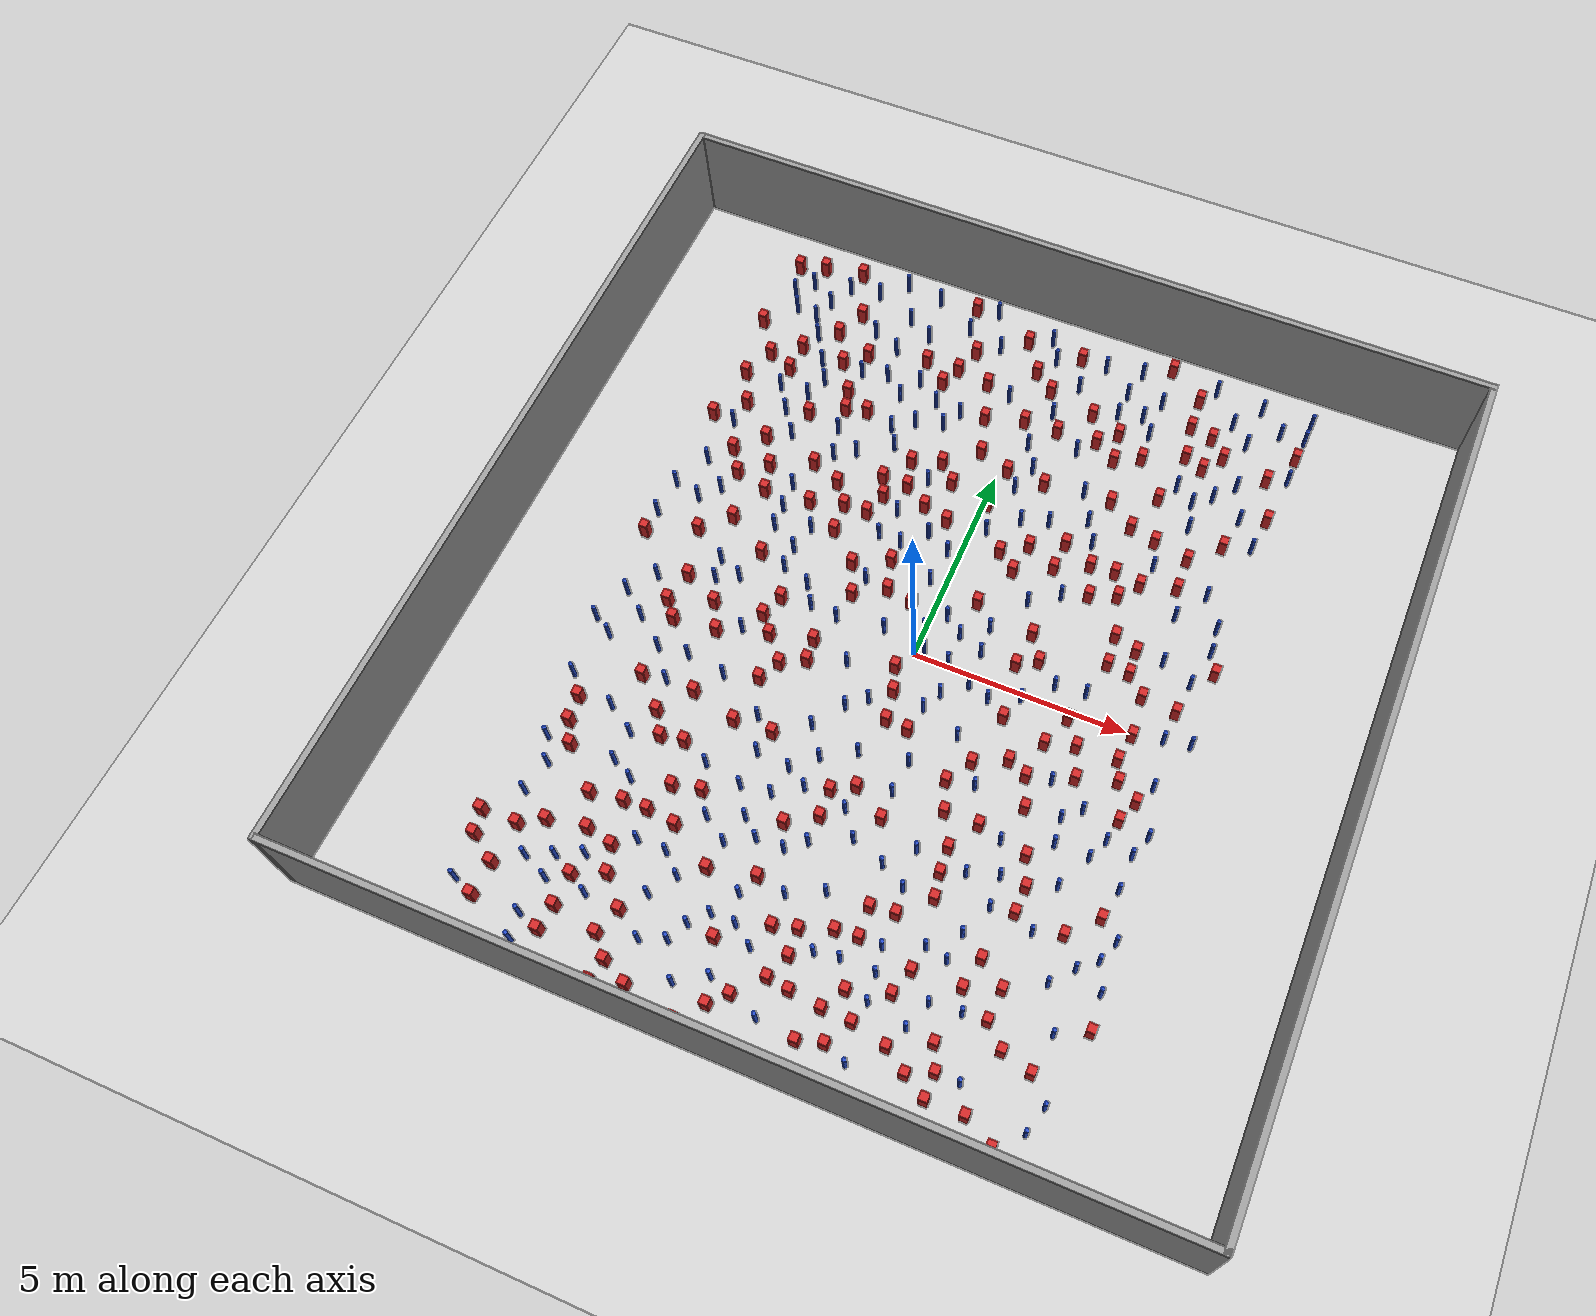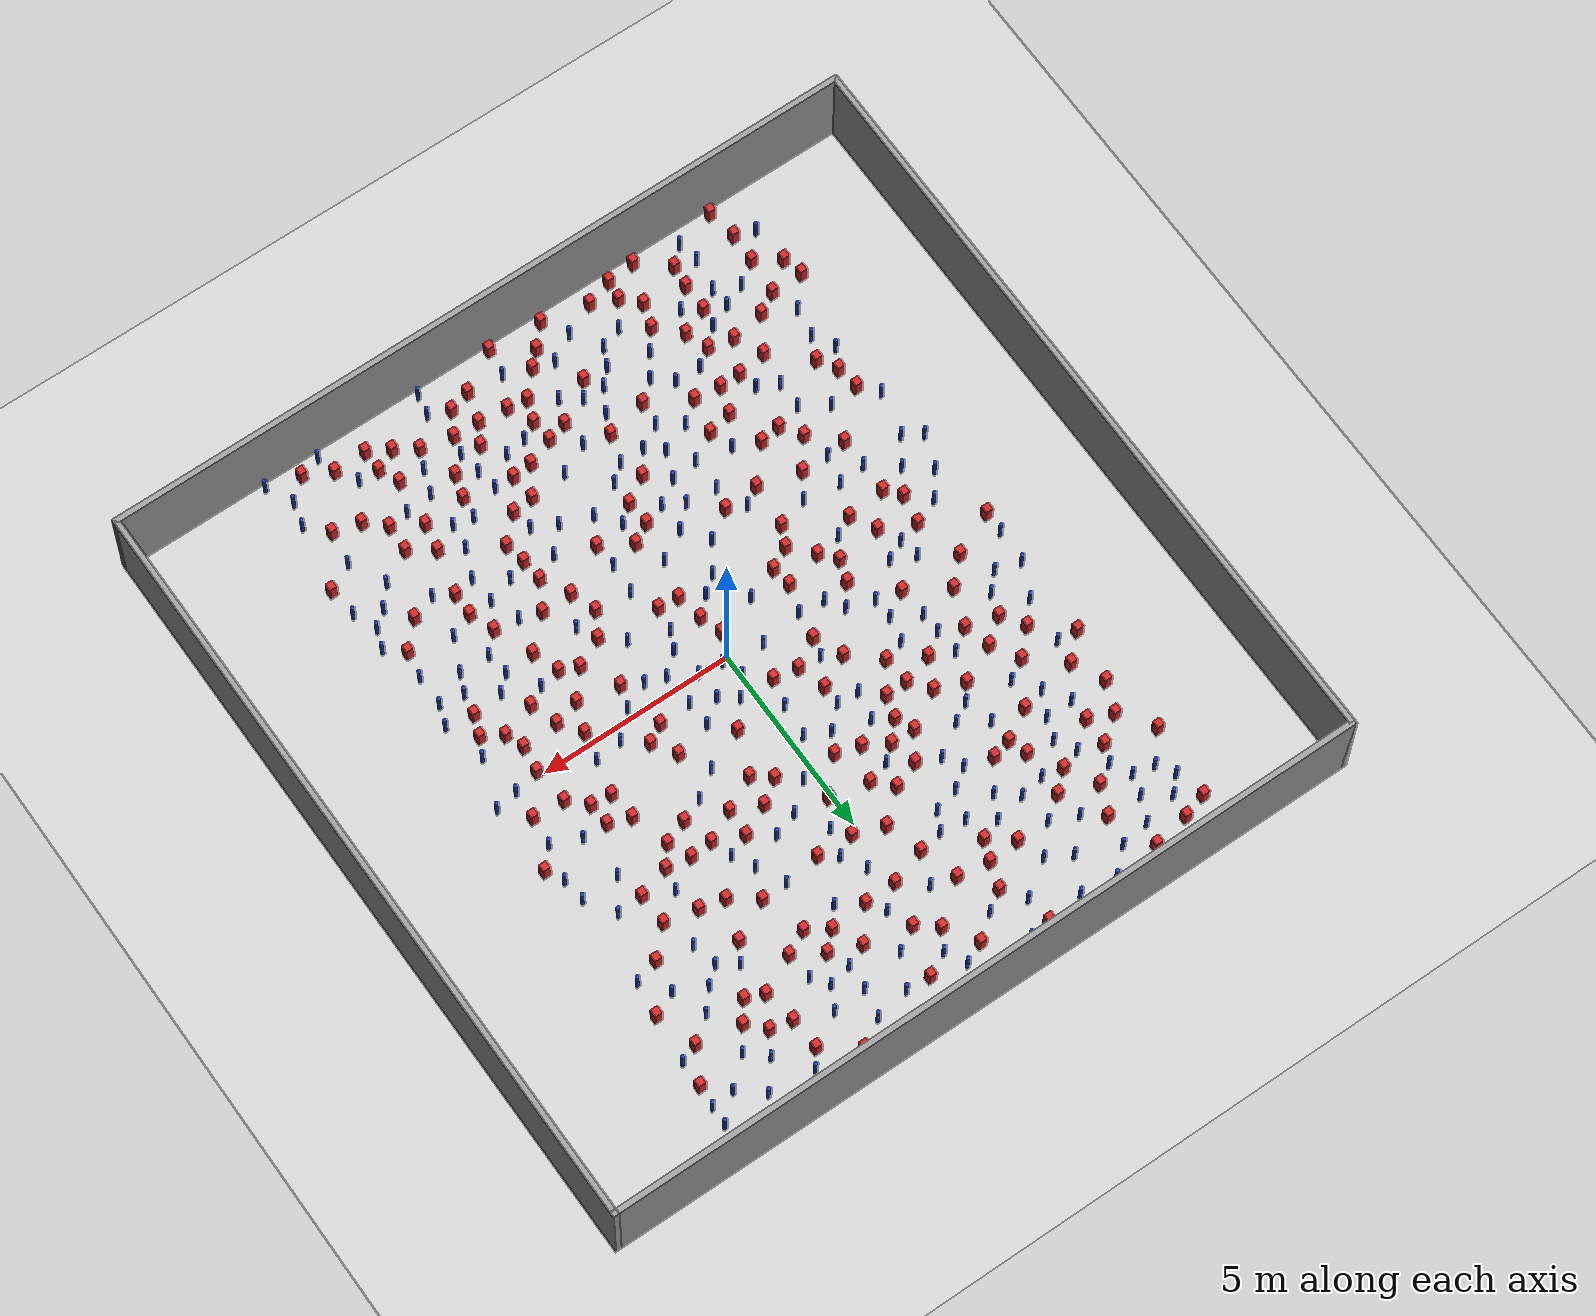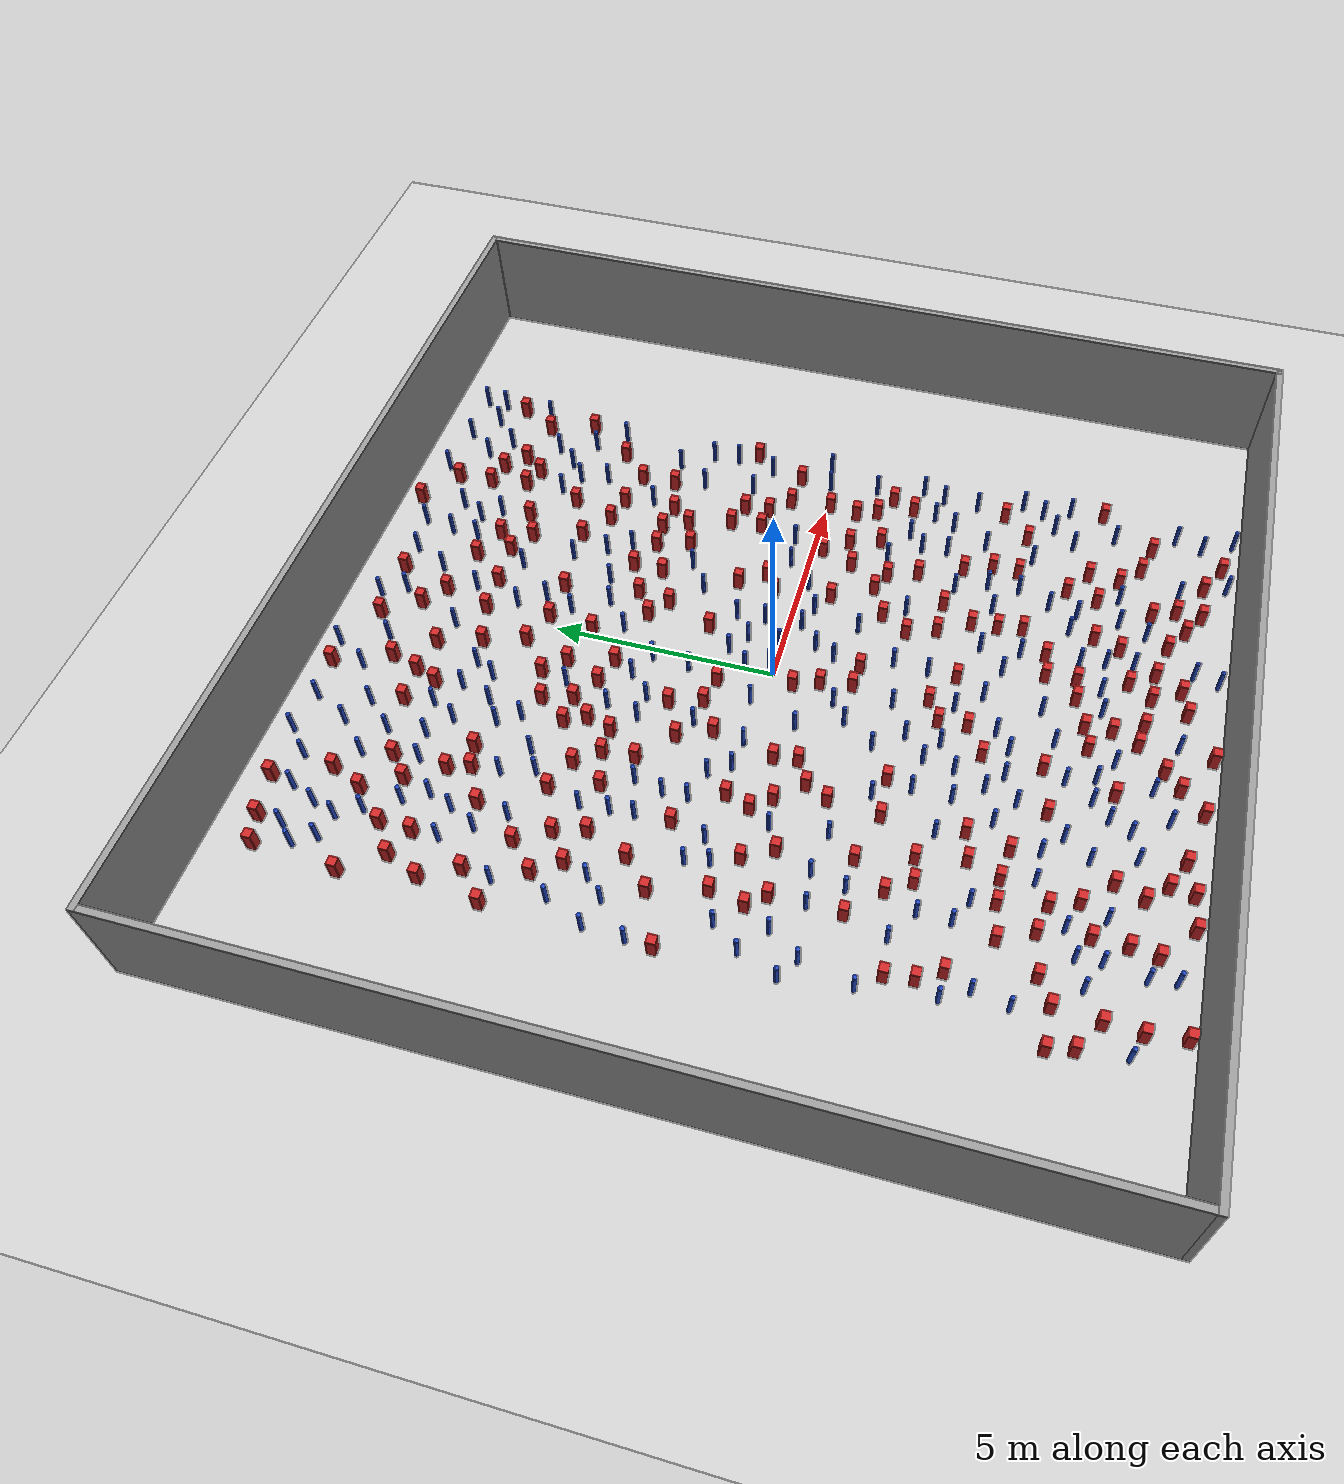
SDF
<sdf version="1.6">
 <world name="default">
  <light name="sun" type="directional">
   <pose>0 0 1000 0 -0 0</pose>
   <diffuse>0.8 0.8 0.8 1</diffuse>
   <specular>0.1 0.1 0.1 1</specular>
   <attenuation>
    <range>1000</range>
    <constant>0.9</constant>
    <linear>0.01</linear>
    <quadratic>0.001</quadratic>
   </attenuation>
   <direction>-0.5 0.5 -1</direction>
  </light>
  <model name="ground_plane">
   <static>1</static>
   <link name="link">
    <collision name="collision">
     <geometry><plane><normal>0 0 1</normal><size>100 100</size></plane></geometry>
     <surface><friction><ode><mu>100</mu><mu2>50</mu2></ode></friction></surface>
    </collision>
    <visual name="visual">
     <cast_shadows>0</cast_shadows>
     <geometry><plane><normal>0 0 1</normal><size>100 100</size></plane></geometry>
     <material>
      <ambient>1.0 1.0 1.0 1.0</ambient>
      <diffuse>0.8 0.8 0.8 1.0</diffuse>
      <specular>0.01 0.01 0.01 1.000000</specular>
     </material>
    </visual>
   </link>
  </model>
  <gravity>0 0 -9.8</gravity>
  <magnetic_field>6e-06 2.3e-05 -4.2e-05</magnetic_field>
  <atmosphere type="adiabatic"/>
  <physics name="default_physics" default="0" type="ode">
   <max_step_size>0.001</max_step_size>
   <real_time_factor>1</real_time_factor>
   <real_time_update_rate>1000</real_time_update_rate>
  </physics>
  <scene><ambient>0.4 0.4 0.4 1</ambient><background>0.7 0.7 0.7 1</background><shadows>1</shadows></scene>
  <spherical_coordinates>
   <surface_model>EARTH_WGS84</surface_model>
   <latitude_deg>0</latitude_deg>
   <longitude_deg>0</longitude_deg>
   <elevation>0</elevation>
   <heading_deg>0</heading_deg>
  </spherical_coordinates>
  <plugin name="gazebo_occupancy_map" filename="libgazebo_2Dmap_plugin.so">
   <map_resolution>0.05</map_resolution>
   <map_topic>generated_map</map_topic>
   <map_height>0.01</map_height>
   <map_size_x>50</map_size_x>
   <map_size_y>50</map_size_y>
  </plugin>
  <model name="NamedLocations">
   <static>true</static>
   <link name="DefaultStart"><pose>8.5 0 0 0 0 3.14</pose></link>
  </model>
  <model name="20x20_walls">
   <pose>0.044518 0.176112 0 0 -0 0</pose>
   <link name="Wall_1">
    <collision name="Wall_1_Collision">
     <geometry><box><size>20 0.15 2.5</size></box></geometry>
     <pose>0 0 1.25 0 -0 0</pose>
    </collision>
    <visual name="Wall_1_Visual">
     <pose>0 0 1.25 0 -0 0</pose>
     <geometry><box><size>20 0.15 2.5</size></box></geometry>
     <material>
      <script><uri>file://media/materials/scripts/gazebo.material</uri><name>Gazebo/Grey</name></script>
      <ambient>0.976471 0.992157 1 1</ambient>
     </material>
     <meta><layer>0</layer></meta>
    </visual>
    <pose>0 9.925 0 0 -0 0</pose>
   </link>
   <link name="Wall_3">
    <collision name="Wall_3_Collision">
     <geometry><box><size>20 0.15 2.5</size></box></geometry>
     <pose>0 0 1.25 0 -0 0</pose>
    </collision>
    <visual name="Wall_3_Visual">
     <pose>0 0 1.25 0 -0 0</pose>
     <geometry><box><size>20 0.15 2.5</size></box></geometry>
     <material>
      <script><uri>file://media/materials/scripts/gazebo.material</uri><name>Gazebo/Grey</name></script>
      <ambient>0.976471 0.992157 1 1</ambient>
     </material>
     <meta><layer>0</layer></meta>
    </visual>
    <pose>9.925 0 0 0 0 -1.5708</pose>
   </link>
   <link name="Wall_4">
    <collision name="Wall_4_Collision">
     <geometry><box><size>20 0.15 2.5</size></box></geometry>
     <pose>0 0 1.25 0 -0 0</pose>
    </collision>
    <visual name="Wall_4_Visual">
     <pose>0 0 1.25 0 -0 0</pose>
     <geometry><box><size>20 0.15 2.5</size></box></geometry>
     <material>
      <script><uri>file://media/materials/scripts/gazebo.material</uri><name>Gazebo/Grey</name></script>
      <ambient>0.976471 0.992157 1 1</ambient>
     </material>
     <meta><layer>0</layer></meta>
    </visual>
    <pose>0 -9.925 0 0 -0 3.14159</pose>
   </link>
   <link name="Wall_5">
    <collision name="Wall_5_Collision">
     <geometry><box><size>20 0.15 2.5</size></box></geometry>
     <pose>0 0 1.25 0 -0 0</pose>
    </collision>
    <visual name="Wall_5_Visual">
     <pose>0 0 1.25 0 -0 0</pose>
     <geometry><box><size>20 0.15 2.5</size></box></geometry>
     <material>
      <script><uri>file://media/materials/scripts/gazebo.material</uri><name>Gazebo/Grey</name></script>
      <ambient>0.976471 0.992157 1 1</ambient>
     </material>
     <meta><layer>0</layer></meta>
    </visual>
    <pose>-9.925 0 0 0 -0 1.5708</pose>
   </link>
   <static>1</static>
  </model>
  <model name="pole_obstacle0">
   <static>true</static>
   <pose>6.45447654039 8.71331853259 7.38925637345e-09 -8.471706928e-08 1.24976765081e-08 -1.74513093015e-07</pose>
   <link name="link">
    <pose>0 0 0.3 0 -0 0</pose>
    <inertial>
     <mass>1</mass>
     <inertia><ixx>0.145833</ixx><ixy>0</ixy><ixz>0</ixz><iyy>0.145833</iyy><iyz>0</iyz><izz>0.125</izz></inertia>
    </inertial>
    <collision name="collision">
     <geometry><cylinder><radius>0.05</radius><length>.6</length></cylinder></geometry>
    </collision>
    <visual name="visual">
     <geometry><cylinder><radius>0.05</radius><length>.6</length></cylinder></geometry>
     <material>
      <script><name>Gazebo/Blue</name><uri>file://media/materials/scripts/gazebo.material</uri></script>
     </material>
    </visual>
   </link>
  </model>
  <model name="pole_obstacle1">
   <static>true</static>
   <pose>0.0124947147275 0.623040329022 7.38925637345e-09 -8.47170692799e-08 1.24976764966e-08 -1.74513093023e-07</pose>
   <link name="link">
    <pose>0 0 0.3 0 -0 0</pose>
    <inertial>
     <mass>1</mass>
     <inertia><ixx>0.145833</ixx><ixy>0</ixy><ixz>0</ixz><iyy>0.145833</iyy><iyz>0</iyz><izz>0.125</izz></inertia>
    </inertial>
    <collision name="collision">
     <geometry><cylinder><radius>0.05</radius><length>.6</length></cylinder></geometry>
    </collision>
    <visual name="visual">
     <geometry><cylinder><radius>0.05</radius><length>.6</length></cylinder></geometry>
     <material>
      <script><name>Gazebo/Blue</name><uri>file://media/materials/scripts/gazebo.material</uri></script>
     </material>
    </visual>
   </link>
  </model>
  <model name="square_post_obstacle0">
   <static>true</static>
   <pose>-1.84166888326 0.796225283095 1.91545236811e-07 -7.35059704564e-06 1.12565212e-07 2.39332434364e-05</pose>
   <link name="link">
    <pose>0 0 0.25 0 -0 0</pose>
    <inertial>
     <mass>100</mass>
     <inertia>
      <ixx>0.166667</ixx>
      <ixy>0</ixy>
      <ixz>0</ixz>
      <iyy>0.166667</iyy>
      <iyz>0</iyz>
      <izz>0.166667</izz>
     </inertia>
    </inertial>
    <collision name="collision"><geometry><box><size>.2 .2 .5</size></box></geometry></collision>
    <visual name="visual">
     <geometry><box><size>.2 .2 .5</size></box></geometry>
     <material>
      <script><name>Gazebo/Red</name><uri>file://media/materials/scripts/gazebo.material</uri></script>
     </material>
    </visual>
   </link>
  </model>
  <model name="square_post_obstacle1">
   <static>true</static>
   <pose>-5.9665953914 -4.91528763904 1.91545236811e-07 -7.35059704564e-06 1.12565212e-07 2.39332434364e-05</pose>
   <link name="link">
    <pose>0 0 0.25 0 -0 0</pose>
    <inertial>
     <mass>100</mass>
     <inertia>
      <ixx>0.166667</ixx>
      <ixy>0</ixy>
      <ixz>0</ixz>
      <iyy>0.166667</iyy>
      <iyz>0</iyz>
      <izz>0.166667</izz>
     </inertia>
    </inertial>
    <collision name="collision"><geometry><box><size>.2 .2 .5</size></box></geometry></collision>
    <visual name="visual">
     <geometry><box><size>.2 .2 .5</size></box></geometry>
     <material>
      <script><name>Gazebo/Red</name><uri>file://media/materials/scripts/gazebo.material</uri></script>
     </material>
    </visual>
   </link>
  </model>
  <model name="pole_obstacle2">
   <static>true</static>
   <pose>-4.24991896851 2.30409226021 7.38925637345e-09 -8.47170692798e-08 1.24976764937e-08 -1.74513093023e-07</pose>
   <link name="link">
    <pose>0 0 0.3 0 -0 0</pose>
    <inertial>
     <mass>1</mass>
     <inertia><ixx>0.145833</ixx><ixy>0</ixy><ixz>0</ixz><iyy>0.145833</iyy><iyz>0</iyz><izz>0.125</izz></inertia>
    </inertial>
    <collision name="collision">
     <geometry><cylinder><radius>0.05</radius><length>.6</length></cylinder></geometry>
    </collision>
    <visual name="visual">
     <geometry><cylinder><radius>0.05</radius><length>.6</length></cylinder></geometry>
     <material>
      <script><name>Gazebo/Blue</name><uri>file://media/materials/scripts/gazebo.material</uri></script>
     </material>
    </visual>
   </link>
  </model>
  <model name="pole_obstacle3">
   <static>true</static>
   <pose>-0.286532830113 -6.21267188489 7.38925637345e-09 -8.47170692799e-08 1.24976765096e-08 -1.74513093014e-07</pose>
   <link name="link">
    <pose>0 0 0.3 0 -0 0</pose>
    <inertial>
     <mass>1</mass>
     <inertia><ixx>0.145833</ixx><ixy>0</ixy><ixz>0</ixz><iyy>0.145833</iyy><iyz>0</iyz><izz>0.125</izz></inertia>
    </inertial>
    <collision name="collision">
     <geometry><cylinder><radius>0.05</radius><length>.6</length></cylinder></geometry>
    </collision>
    <visual name="visual">
     <geometry><cylinder><radius>0.05</radius><length>.6</length></cylinder></geometry>
     <material>
      <script><name>Gazebo/Blue</name><uri>file://media/materials/scripts/gazebo.material</uri></script>
     </material>
    </visual>
   </link>
  </model>
  <model name="pole_obstacle4">
   <static>true</static>
   <pose>-2.08851028054 -7.99821689099 7.38925637345e-09 -8.47170692793e-08 1.24976764454e-08 -1.74513093039e-07</pose>
   <link name="link">
    <pose>0 0 0.3 0 -0 0</pose>
    <inertial>
     <mass>1</mass>
     <inertia><ixx>0.145833</ixx><ixy>0</ixy><ixz>0</ixz><iyy>0.145833</iyy><iyz>0</iyz><izz>0.125</izz></inertia>
    </inertial>
    <collision name="collision">
     <geometry><cylinder><radius>0.05</radius><length>.6</length></cylinder></geometry>
    </collision>
    <visual name="visual">
     <geometry><cylinder><radius>0.05</radius><length>.6</length></cylinder></geometry>
     <material>
      <script><name>Gazebo/Blue</name><uri>file://media/materials/scripts/gazebo.material</uri></script>
     </material>
    </visual>
   </link>
  </model>
  <model name="pole_obstacle5">
   <static>true</static>
   <pose>-5.07244034275 -9.1984680818 7.38925637345e-09 -8.471706928e-08 1.24976765081e-08 -1.74513093015e-07</pose>
   <link name="link">
    <pose>0 0 0.3 0 -0 0</pose>
    <inertial>
     <mass>1</mass>
     <inertia><ixx>0.145833</ixx><ixy>0</ixy><ixz>0</ixz><iyy>0.145833</iyy><iyz>0</iyz><izz>0.125</izz></inertia>
    </inertial>
    <collision name="collision">
     <geometry><cylinder><radius>0.05</radius><length>.6</length></cylinder></geometry>
    </collision>
    <visual name="visual">
     <geometry><cylinder><radius>0.05</radius><length>.6</length></cylinder></geometry>
     <material>
      <script><name>Gazebo/Blue</name><uri>file://media/materials/scripts/gazebo.material</uri></script>
     </material>
    </visual>
   </link>
  </model>
  <model name="pole_obstacle6">
   <static>true</static>
   <pose>-1.34297444694 -2.51298891323 7.38925637345e-09 -8.47170692799e-08 1.24976765053e-08 -1.74513093017e-07</pose>
   <link name="link">
    <pose>0 0 0.3 0 -0 0</pose>
    <inertial>
     <mass>1</mass>
     <inertia><ixx>0.145833</ixx><ixy>0</ixy><ixz>0</ixz><iyy>0.145833</iyy><iyz>0</iyz><izz>0.125</izz></inertia>
    </inertial>
    <collision name="collision">
     <geometry><cylinder><radius>0.05</radius><length>.6</length></cylinder></geometry>
    </collision>
    <visual name="visual">
     <geometry><cylinder><radius>0.05</radius><length>.6</length></cylinder></geometry>
     <material>
      <script><name>Gazebo/Blue</name><uri>file://media/materials/scripts/gazebo.material</uri></script>
     </material>
    </visual>
   </link>
  </model>
  <model name="square_post_obstacle2">
   <static>true</static>
   <pose>-6.92443869913 0.52097010561 1.91545236811e-07 -7.35059704564e-06 1.12565212e-07 2.39332434364e-05</pose>
   <link name="link">
    <pose>0 0 0.25 0 -0 0</pose>
    <inertial>
     <mass>100</mass>
     <inertia>
      <ixx>0.166667</ixx>
      <ixy>0</ixy>
      <ixz>0</ixz>
      <iyy>0.166667</iyy>
      <iyz>0</iyz>
      <izz>0.166667</izz>
     </inertia>
    </inertial>
    <collision name="collision"><geometry><box><size>.2 .2 .5</size></box></geometry></collision>
    <visual name="visual">
     <geometry><box><size>.2 .2 .5</size></box></geometry>
     <material>
      <script><name>Gazebo/Red</name><uri>file://media/materials/scripts/gazebo.material</uri></script>
     </material>
    </visual>
   </link>
  </model>
  <model name="square_post_obstacle3">
   <static>true</static>
   <pose>4.00599388592 -3.51829156355 1.91545236811e-07 -7.35059704564e-06 1.12565212e-07 2.39332434364e-05</pose>
   <link name="link">
    <pose>0 0 0.25 0 -0 0</pose>
    <inertial>
     <mass>100</mass>
     <inertia>
      <ixx>0.166667</ixx>
      <ixy>0</ixy>
      <ixz>0</ixz>
      <iyy>0.166667</iyy>
      <iyz>0</iyz>
      <izz>0.166667</izz>
     </inertia>
    </inertial>
    <collision name="collision"><geometry><box><size>.2 .2 .5</size></box></geometry></collision>
    <visual name="visual">
     <geometry><box><size>.2 .2 .5</size></box></geometry>
     <material>
      <script><name>Gazebo/Red</name><uri>file://media/materials/scripts/gazebo.material</uri></script>
     </material>
    </visual>
   </link>
  </model>
  <model name="square_post_obstacle4">
   <static>true</static>
   <pose>-1.7228530405 8.17220741166 1.91545236811e-07 -7.35059704564e-06 1.12565212e-07 2.39332434364e-05</pose>
   <link name="link">
    <pose>0 0 0.25 0 -0 0</pose>
    <inertial>
     <mass>100</mass>
     <inertia>
      <ixx>0.166667</ixx>
      <ixy>0</ixy>
      <ixz>0</ixz>
      <iyy>0.166667</iyy>
      <iyz>0</iyz>
      <izz>0.166667</izz>
     </inertia>
    </inertial>
    <collision name="collision"><geometry><box><size>.2 .2 .5</size></box></geometry></collision>
    <visual name="visual">
     <geometry><box><size>.2 .2 .5</size></box></geometry>
     <material>
      <script><name>Gazebo/Red</name><uri>file://media/materials/scripts/gazebo.material</uri></script>
     </material>
    </visual>
   </link>
  </model>
  <model name="pole_obstacle7">
   <static>true</static>
   <pose>2.44351836764 -2.47740883795 7.38925637345e-09 -8.47170692798e-08 1.24976764939e-08 -1.74513093025e-07</pose>
   <link name="link">
    <pose>0 0 0.3 0 -0 0</pose>
    <inertial>
     <mass>1</mass>
     <inertia><ixx>0.145833</ixx><ixy>0</ixy><ixz>0</ixz><iyy>0.145833</iyy><iyz>0</iyz><izz>0.125</izz></inertia>
    </inertial>
    <collision name="collision">
     <geometry><cylinder><radius>0.05</radius><length>.6</length></cylinder></geometry>
    </collision>
    <visual name="visual">
     <geometry><cylinder><radius>0.05</radius><length>.6</length></cylinder></geometry>
     <material>
      <script><name>Gazebo/Blue</name><uri>file://media/materials/scripts/gazebo.material</uri></script>
     </material>
    </visual>
   </link>
  </model>
  <model name="pole_obstacle8">
   <static>true</static>
   <pose>5.81876079318 0.0684140431887 7.38925637345e-09 -8.471706928e-08 1.24976765192e-08 -1.7451309301e-07</pose>
   <link name="link">
    <pose>0 0 0.3 0 -0 0</pose>
    <inertial>
     <mass>1</mass>
     <inertia><ixx>0.145833</ixx><ixy>0</ixy><ixz>0</ixz><iyy>0.145833</iyy><iyz>0</iyz><izz>0.125</izz></inertia>
    </inertial>
    <collision name="collision">
     <geometry><cylinder><radius>0.05</radius><length>.6</length></cylinder></geometry>
    </collision>
    <visual name="visual">
     <geometry><cylinder><radius>0.05</radius><length>.6</length></cylinder></geometry>
     <material>
      <script><name>Gazebo/Blue</name><uri>file://media/materials/scripts/gazebo.material</uri></script>
     </material>
    </visual>
   </link>
  </model>
  <model name="square_post_obstacle5">
   <static>true</static>
   <pose>5.47020168853 -9.28129456537 1.91545236811e-07 -7.35059704564e-06 1.12565212e-07 2.39332434364e-05</pose>
   <link name="link">
    <pose>0 0 0.25 0 -0 0</pose>
    <inertial>
     <mass>100</mass>
     <inertia>
      <ixx>0.166667</ixx>
      <ixy>0</ixy>
      <ixz>0</ixz>
      <iyy>0.166667</iyy>
      <iyz>0</iyz>
      <izz>0.166667</izz>
     </inertia>
    </inertial>
    <collision name="collision"><geometry><box><size>.2 .2 .5</size></box></geometry></collision>
    <visual name="visual">
     <geometry><box><size>.2 .2 .5</size></box></geometry>
     <material>
      <script><name>Gazebo/Red</name><uri>file://media/materials/scripts/gazebo.material</uri></script>
     </material>
    </visual>
   </link>
  </model>
  <model name="square_post_obstacle6">
   <static>true</static>
   <pose>-6.26178167945 -4.42269500261 1.91545236811e-07 -7.35059704564e-06 1.12565212e-07 2.39332434364e-05</pose>
   <link name="link">
    <pose>0 0 0.25 0 -0 0</pose>
    <inertial>
     <mass>100</mass>
     <inertia>
      <ixx>0.166667</ixx>
      <ixy>0</ixy>
      <ixz>0</ixz>
      <iyy>0.166667</iyy>
      <iyz>0</iyz>
      <izz>0.166667</izz>
     </inertia>
    </inertial>
    <collision name="collision"><geometry><box><size>.2 .2 .5</size></box></geometry></collision>
    <visual name="visual">
     <geometry><box><size>.2 .2 .5</size></box></geometry>
     <material>
      <script><name>Gazebo/Red</name><uri>file://media/materials/scripts/gazebo.material</uri></script>
     </material>
    </visual>
   </link>
  </model>
  <model name="square_post_obstacle7">
   <static>true</static>
   <pose>0.969384213969 -6.50192660426 1.91545236811e-07 -7.35059704564e-06 1.12565212e-07 2.39332434364e-05</pose>
   <link name="link">
    <pose>0 0 0.25 0 -0 0</pose>
    <inertial>
     <mass>100</mass>
     <inertia>
      <ixx>0.166667</ixx>
      <ixy>0</ixy>
      <ixz>0</ixz>
      <iyy>0.166667</iyy>
      <iyz>0</iyz>
      <izz>0.166667</izz>
     </inertia>
    </inertial>
    <collision name="collision"><geometry><box><size>.2 .2 .5</size></box></geometry></collision>
    <visual name="visual">
     <geometry><box><size>.2 .2 .5</size></box></geometry>
     <material>
      <script><name>Gazebo/Red</name><uri>file://media/materials/scripts/gazebo.material</uri></script>
     </material>
    </visual>
   </link>
  </model>
  <model name="pole_obstacle9">
   <static>true</static>
   <pose>-6.22438378914 -5.47436945772 7.38925637345e-09 -8.47170692796e-08 1.24976764786e-08 -1.74513093032e-07</pose>
   <link name="link">
    <pose>0 0 0.3 0 -0 0</pose>
    <inertial>
     <mass>1</mass>
     <inertia><ixx>0.145833</ixx><ixy>0</ixy><ixz>0</ixz><iyy>0.145833</iyy><iyz>0</iyz><izz>0.125</izz></inertia>
    </inertial>
    <collision name="collision">
     <geometry><cylinder><radius>0.05</radius><length>.6</length></cylinder></geometry>
    </collision>
    <visual name="visual">
     <geometry><cylinder><radius>0.05</radius><length>.6</length></cylinder></geometry>
     <material>
      <script><name>Gazebo/Blue</name><uri>file://media/materials/scripts/gazebo.material</uri></script>
     </material>
    </visual>
   </link>
  </model>
  <model name="pole_obstacle10">
   <static>true</static>
   <pose>2.1343631112 -9.45369826107 7.38925637345e-09 -8.47170692793e-08 1.24976764408e-08 -1.74513093041e-07</pose>
   <link name="link">
    <pose>0 0 0.3 0 -0 0</pose>
    <inertial>
     <mass>1</mass>
     <inertia><ixx>0.145833</ixx><ixy>0</ixy><ixz>0</ixz><iyy>0.145833</iyy><iyz>0</iyz><izz>0.125</izz></inertia>
    </inertial>
    <collision name="collision">
     <geometry><cylinder><radius>0.05</radius><length>.6</length></cylinder></geometry>
    </collision>
    <visual name="visual">
     <geometry><cylinder><radius>0.05</radius><length>.6</length></cylinder></geometry>
     <material>
      <script><name>Gazebo/Blue</name><uri>file://media/materials/scripts/gazebo.material</uri></script>
     </material>
    </visual>
   </link>
  </model>
  <model name="pole_obstacle11">
   <static>true</static>
   <pose>0.533257884497 -4.56651260387 7.38925637345e-09 -8.47170692799e-08 1.24976765073e-08 -1.74513093015e-07</pose>
   <link name="link">
    <pose>0 0 0.3 0 -0 0</pose>
    <inertial>
     <mass>1</mass>
     <inertia><ixx>0.145833</ixx><ixy>0</ixy><ixz>0</ixz><iyy>0.145833</iyy><iyz>0</iyz><izz>0.125</izz></inertia>
    </inertial>
    <collision name="collision">
     <geometry><cylinder><radius>0.05</radius><length>.6</length></cylinder></geometry>
    </collision>
    <visual name="visual">
     <geometry><cylinder><radius>0.05</radius><length>.6</length></cylinder></geometry>
     <material>
      <script><name>Gazebo/Blue</name><uri>file://media/materials/scripts/gazebo.material</uri></script>
     </material>
    </visual>
   </link>
  </model>
  <model name="pole_obstacle12">
   <static>true</static>
   <pose>4.09159602282 9.2911421733 7.38925637345e-09 -8.471706928e-08 1.24976765081e-08 -1.74513093015e-07</pose>
   <link name="link">
    <pose>0 0 0.3 0 -0 0</pose>
    <inertial>
     <mass>1</mass>
     <inertia><ixx>0.145833</ixx><ixy>0</ixy><ixz>0</ixz><iyy>0.145833</iyy><iyz>0</iyz><izz>0.125</izz></inertia>
    </inertial>
    <collision name="collision">
     <geometry><cylinder><radius>0.05</radius><length>.6</length></cylinder></geometry>
    </collision>
    <visual name="visual">
     <geometry><cylinder><radius>0.05</radius><length>.6</length></cylinder></geometry>
     <material>
      <script><name>Gazebo/Blue</name><uri>file://media/materials/scripts/gazebo.material</uri></script>
     </material>
    </visual>
   </link>
  </model>
  <model name="square_post_obstacle8">
   <static>true</static>
   <pose>1.29878756717 2.75642417488 1.91545236811e-07 -7.35059704564e-06 1.12565212e-07 2.39332434364e-05</pose>
   <link name="link">
    <pose>0 0 0.25 0 -0 0</pose>
    <inertial>
     <mass>100</mass>
     <inertia>
      <ixx>0.166667</ixx>
      <ixy>0</ixy>
      <ixz>0</ixz>
      <iyy>0.166667</iyy>
      <iyz>0</iyz>
      <izz>0.166667</izz>
     </inertia>
    </inertial>
    <collision name="collision"><geometry><box><size>.2 .2 .5</size></box></geometry></collision>
    <visual name="visual">
     <geometry><box><size>.2 .2 .5</size></box></geometry>
     <material>
      <script><name>Gazebo/Red</name><uri>file://media/materials/scripts/gazebo.material</uri></script>
     </material>
    </visual>
   </link>
  </model>
  <model name="square_post_obstacle9">
   <static>true</static>
   <pose>-5.61328121798 -6.63471484839 1.91545236811e-07 -7.35059704564e-06 1.12565212e-07 2.39332434364e-05</pose>
   <link name="link">
    <pose>0 0 0.25 0 -0 0</pose>
    <inertial>
     <mass>100</mass>
     <inertia>
      <ixx>0.166667</ixx>
      <ixy>0</ixy>
      <ixz>0</ixz>
      <iyy>0.166667</iyy>
      <iyz>0</iyz>
      <izz>0.166667</izz>
     </inertia>
    </inertial>
    <collision name="collision"><geometry><box><size>.2 .2 .5</size></box></geometry></collision>
    <visual name="visual">
     <geometry><box><size>.2 .2 .5</size></box></geometry>
     <material>
      <script><name>Gazebo/Red</name><uri>file://media/materials/scripts/gazebo.material</uri></script>
     </material>
    </visual>
   </link>
  </model>
  <model name="pole_obstacle13">
   <static>true</static>
   <pose>-1.71100634658 1.28023424929 7.38925637345e-09 -8.471706928e-08 1.24976765079e-08 -1.74513093017e-07</pose>
   <link name="link">
    <pose>0 0 0.3 0 -0 0</pose>
    <inertial>
     <mass>1</mass>
     <inertia><ixx>0.145833</ixx><ixy>0</ixy><ixz>0</ixz><iyy>0.145833</iyy><iyz>0</iyz><izz>0.125</izz></inertia>
    </inertial>
    <collision name="collision">
     <geometry><cylinder><radius>0.05</radius><length>.6</length></cylinder></geometry>
    </collision>
    <visual name="visual">
     <geometry><cylinder><radius>0.05</radius><length>.6</length></cylinder></geometry>
     <material>
      <script><name>Gazebo/Blue</name><uri>file://media/materials/scripts/gazebo.material</uri></script>
     </material>
    </visual>
   </link>
  </model>
  <model name="square_post_obstacle10">
   <static>true</static>
   <pose>-0.545122452451 5.49682571022 1.91545236811e-07 -7.35059704564e-06 1.12565212e-07 2.39332434364e-05</pose>
   <link name="link">
    <pose>0 0 0.25 0 -0 0</pose>
    <inertial>
     <mass>100</mass>
     <inertia>
      <ixx>0.166667</ixx>
      <ixy>0</ixy>
      <ixz>0</ixz>
      <iyy>0.166667</iyy>
      <iyz>0</iyz>
      <izz>0.166667</izz>
     </inertia>
    </inertial>
    <collision name="collision"><geometry><box><size>.2 .2 .5</size></box></geometry></collision>
    <visual name="visual">
     <geometry><box><size>.2 .2 .5</size></box></geometry>
     <material>
      <script><name>Gazebo/Red</name><uri>file://media/materials/scripts/gazebo.material</uri></script>
     </material>
    </visual>
   </link>
  </model>
  <model name="square_post_obstacle11">
   <static>true</static>
   <pose>3.11903485996 2.80575910059 1.91545236811e-07 -7.35059704564e-06 1.12565212e-07 2.39332434364e-05</pose>
   <link name="link">
    <pose>0 0 0.25 0 -0 0</pose>
    <inertial>
     <mass>100</mass>
     <inertia>
      <ixx>0.166667</ixx>
      <ixy>0</ixy>
      <ixz>0</ixz>
      <iyy>0.166667</iyy>
      <iyz>0</iyz>
      <izz>0.166667</izz>
     </inertia>
    </inertial>
    <collision name="collision"><geometry><box><size>.2 .2 .5</size></box></geometry></collision>
    <visual name="visual">
     <geometry><box><size>.2 .2 .5</size></box></geometry>
     <material>
      <script><name>Gazebo/Red</name><uri>file://media/materials/scripts/gazebo.material</uri></script>
     </material>
    </visual>
   </link>
  </model>
  <model name="pole_obstacle14">
   <static>true</static>
   <pose>-3.07545516667 -4.19201038177 7.38925637345e-09 -8.47170692794e-08 1.24976764468e-08 -1.7451309304e-07</pose>
   <link name="link">
    <pose>0 0 0.3 0 -0 0</pose>
    <inertial>
     <mass>1</mass>
     <inertia><ixx>0.145833</ixx><ixy>0</ixy><ixz>0</ixz><iyy>0.145833</iyy><iyz>0</iyz><izz>0.125</izz></inertia>
    </inertial>
    <collision name="collision">
     <geometry><cylinder><radius>0.05</radius><length>.6</length></cylinder></geometry>
    </collision>
    <visual name="visual">
     <geometry><cylinder><radius>0.05</radius><length>.6</length></cylinder></geometry>
     <material>
      <script><name>Gazebo/Blue</name><uri>file://media/materials/scripts/gazebo.material</uri></script>
     </material>
    </visual>
   </link>
  </model>
  <model name="pole_obstacle15">
   <static>true</static>
   <pose>-0.898604787767 -3.89439577498 7.38925637345e-09 -8.47170692799e-08 1.2497676509e-08 -1.74513093016e-07</pose>
   <link name="link">
    <pose>0 0 0.3 0 -0 0</pose>
    <inertial>
     <mass>1</mass>
     <inertia><ixx>0.145833</ixx><ixy>0</ixy><ixz>0</ixz><iyy>0.145833</iyy><iyz>0</iyz><izz>0.125</izz></inertia>
    </inertial>
    <collision name="collision">
     <geometry><cylinder><radius>0.05</radius><length>.6</length></cylinder></geometry>
    </collision>
    <visual name="visual">
     <geometry><cylinder><radius>0.05</radius><length>.6</length></cylinder></geometry>
     <material>
      <script><name>Gazebo/Blue</name><uri>file://media/materials/scripts/gazebo.material</uri></script>
     </material>
    </visual>
   </link>
  </model>
  <model name="square_post_obstacle12">
   <static>true</static>
   <pose>3.74705745859 5.85950981759 1.91545236811e-07 -7.35059704564e-06 1.12565212e-07 2.39332434364e-05</pose>
   <link name="link">
    <pose>0 0 0.25 0 -0 0</pose>
    <inertial>
     <mass>100</mass>
     <inertia>
      <ixx>0.166667</ixx>
      <ixy>0</ixy>
      <ixz>0</ixz>
      <iyy>0.166667</iyy>
      <iyz>0</iyz>
      <izz>0.166667</izz>
     </inertia>
    </inertial>
    <collision name="collision"><geometry><box><size>.2 .2 .5</size></box></geometry></collision>
    <visual name="visual">
     <geometry><box><size>.2 .2 .5</size></box></geometry>
     <material>
      <script><name>Gazebo/Red</name><uri>file://media/materials/scripts/gazebo.material</uri></script>
     </material>
    </visual>
   </link>
  </model>
  <model name="pole_obstacle16">
   <static>true</static>
   <pose>-0.340629063459 1.8112324864 7.38925637345e-09 -8.47170692798e-08 1.24976765025e-08 -1.74513093018e-07</pose>
   <link name="link">
    <pose>0 0 0.3 0 -0 0</pose>
    <inertial>
     <mass>1</mass>
     <inertia><ixx>0.145833</ixx><ixy>0</ixy><ixz>0</ixz><iyy>0.145833</iyy><iyz>0</iyz><izz>0.125</izz></inertia>
    </inertial>
    <collision name="collision">
     <geometry><cylinder><radius>0.05</radius><length>.6</length></cylinder></geometry>
    </collision>
    <visual name="visual">
     <geometry><cylinder><radius>0.05</radius><length>.6</length></cylinder></geometry>
     <material>
      <script><name>Gazebo/Blue</name><uri>file://media/materials/scripts/gazebo.material</uri></script>
     </material>
    </visual>
   </link>
  </model>
  <model name="pole_obstacle17">
   <static>true</static>
   <pose>-3.45545630183 6.66428810305 7.38925637345e-09 -8.47170692794e-08 1.24976764468e-08 -1.7451309304e-07</pose>
   <link name="link">
    <pose>0 0 0.3 0 -0 0</pose>
    <inertial>
     <mass>1</mass>
     <inertia><ixx>0.145833</ixx><ixy>0</ixy><ixz>0</ixz><iyy>0.145833</iyy><iyz>0</iyz><izz>0.125</izz></inertia>
    </inertial>
    <collision name="collision">
     <geometry><cylinder><radius>0.05</radius><length>.6</length></cylinder></geometry>
    </collision>
    <visual name="visual">
     <geometry><cylinder><radius>0.05</radius><length>.6</length></cylinder></geometry>
     <material>
      <script><name>Gazebo/Blue</name><uri>file://media/materials/scripts/gazebo.material</uri></script>
     </material>
    </visual>
   </link>
  </model>
  <model name="square_post_obstacle13">
   <static>true</static>
   <pose>-6.81584707708 8.96019248602 1.91545236811e-07 -7.35059704564e-06 1.12565212e-07 2.39332434364e-05</pose>
   <link name="link">
    <pose>0 0 0.25 0 -0 0</pose>
    <inertial>
     <mass>100</mass>
     <inertia>
      <ixx>0.166667</ixx>
      <ixy>0</ixy>
      <ixz>0</ixz>
      <iyy>0.166667</iyy>
      <iyz>0</iyz>
      <izz>0.166667</izz>
     </inertia>
    </inertial>
    <collision name="collision"><geometry><box><size>.2 .2 .5</size></box></geometry></collision>
    <visual name="visual">
     <geometry><box><size>.2 .2 .5</size></box></geometry>
     <material>
      <script><name>Gazebo/Red</name><uri>file://media/materials/scripts/gazebo.material</uri></script>
     </material>
    </visual>
   </link>
  </model>
  <model name="pole_obstacle18">
   <static>true</static>
   <pose>-0.885350081492 -3.13839814819 7.38925637345e-09 -8.47170692799e-08 1.2497676509e-08 -1.74513093016e-07</pose>
   <link name="link">
    <pose>0 0 0.3 0 -0 0</pose>
    <inertial>
     <mass>1</mass>
     <inertia><ixx>0.145833</ixx><ixy>0</ixy><ixz>0</ixz><iyy>0.145833</iyy><iyz>0</iyz><izz>0.125</izz></inertia>
    </inertial>
    <collision name="collision">
     <geometry><cylinder><radius>0.05</radius><length>.6</length></cylinder></geometry>
    </collision>
    <visual name="visual">
     <geometry><cylinder><radius>0.05</radius><length>.6</length></cylinder></geometry>
     <material>
      <script><name>Gazebo/Blue</name><uri>file://media/materials/scripts/gazebo.material</uri></script>
     </material>
    </visual>
   </link>
  </model>
  <model name="square_post_obstacle14">
   <static>true</static>
   <pose>-3.87301807187 -7.210273516 1.91545236811e-07 -7.35059704564e-06 1.12565212e-07 2.39332434364e-05</pose>
   <link name="link">
    <pose>0 0 0.25 0 -0 0</pose>
    <inertial>
     <mass>100</mass>
     <inertia>
      <ixx>0.166667</ixx>
      <ixy>0</ixy>
      <ixz>0</ixz>
      <iyy>0.166667</iyy>
      <iyz>0</iyz>
      <izz>0.166667</izz>
     </inertia>
    </inertial>
    <collision name="collision"><geometry><box><size>.2 .2 .5</size></box></geometry></collision>
    <visual name="visual">
     <geometry><box><size>.2 .2 .5</size></box></geometry>
     <material>
      <script><name>Gazebo/Red</name><uri>file://media/materials/scripts/gazebo.material</uri></script>
     </material>
    </visual>
   </link>
  </model>
  <model name="pole_obstacle19">
   <static>true</static>
   <pose>-6.45855339897 2.84667445079 7.38925637345e-09 -8.47170692798e-08 1.24976764937e-08 -1.74513093023e-07</pose>
   <link name="link">
    <pose>0 0 0.3 0 -0 0</pose>
    <inertial>
     <mass>1</mass>
     <inertia><ixx>0.145833</ixx><ixy>0</ixy><ixz>0</ixz><iyy>0.145833</iyy><iyz>0</iyz><izz>0.125</izz></inertia>
    </inertial>
    <collision name="collision">
     <geometry><cylinder><radius>0.05</radius><length>.6</length></cylinder></geometry>
    </collision>
    <visual name="visual">
     <geometry><cylinder><radius>0.05</radius><length>.6</length></cylinder></geometry>
     <material>
      <script><name>Gazebo/Blue</name><uri>file://media/materials/scripts/gazebo.material</uri></script>
     </material>
    </visual>
   </link>
  </model>
  <model name="square_post_obstacle15">
   <static>true</static>
   <pose>1.88256273671 6.80930600151 1.91545236811e-07 -7.35059704564e-06 1.12565212e-07 2.39332434364e-05</pose>
   <link name="link">
    <pose>0 0 0.25 0 -0 0</pose>
    <inertial>
     <mass>100</mass>
     <inertia>
      <ixx>0.166667</ixx>
      <ixy>0</ixy>
      <ixz>0</ixz>
      <iyy>0.166667</iyy>
      <iyz>0</iyz>
      <izz>0.166667</izz>
     </inertia>
    </inertial>
    <collision name="collision"><geometry><box><size>.2 .2 .5</size></box></geometry></collision>
    <visual name="visual">
     <geometry><box><size>.2 .2 .5</size></box></geometry>
     <material>
      <script><name>Gazebo/Red</name><uri>file://media/materials/scripts/gazebo.material</uri></script>
     </material>
    </visual>
   </link>
  </model>
  <model name="square_post_obstacle16">
   <static>true</static>
   <pose>6.39530933987 8.14642815846 1.91545236811e-07 -7.35059704564e-06 1.12565212e-07 2.39332434364e-05</pose>
   <link name="link">
    <pose>0 0 0.25 0 -0 0</pose>
    <inertial>
     <mass>100</mass>
     <inertia>
      <ixx>0.166667</ixx>
      <ixy>0</ixy>
      <ixz>0</ixz>
      <iyy>0.166667</iyy>
      <iyz>0</iyz>
      <izz>0.166667</izz>
     </inertia>
    </inertial>
    <collision name="collision"><geometry><box><size>.2 .2 .5</size></box></geometry></collision>
    <visual name="visual">
     <geometry><box><size>.2 .2 .5</size></box></geometry>
     <material>
      <script><name>Gazebo/Red</name><uri>file://media/materials/scripts/gazebo.material</uri></script>
     </material>
    </visual>
   </link>
  </model>
  <model name="square_post_obstacle17">
   <static>true</static>
   <pose>4.44098144034 7.03544417988 1.91545236811e-07 -7.35059704564e-06 1.12565212e-07 2.39332434364e-05</pose>
   <link name="link">
    <pose>0 0 0.25 0 -0 0</pose>
    <inertial>
     <mass>100</mass>
     <inertia>
      <ixx>0.166667</ixx>
      <ixy>0</ixy>
      <ixz>0</ixz>
      <iyy>0.166667</iyy>
      <iyz>0</iyz>
      <izz>0.166667</izz>
     </inertia>
    </inertial>
    <collision name="collision"><geometry><box><size>.2 .2 .5</size></box></geometry></collision>
    <visual name="visual">
     <geometry><box><size>.2 .2 .5</size></box></geometry>
     <material>
      <script><name>Gazebo/Red</name><uri>file://media/materials/scripts/gazebo.material</uri></script>
     </material>
    </visual>
   </link>
  </model>
  <model name="pole_obstacle20">
   <static>true</static>
   <pose>-6.72067759787 -3.35733586468 7.38925637345e-09 -8.47170692798e-08 1.24976764937e-08 -1.74513093023e-07</pose>
   <link name="link">
    <pose>0 0 0.3 0 -0 0</pose>
    <inertial>
     <mass>1</mass>
     <inertia><ixx>0.145833</ixx><ixy>0</ixy><ixz>0</ixz><iyy>0.145833</iyy><iyz>0</iyz><izz>0.125</izz></inertia>
    </inertial>
    <collision name="collision">
     <geometry><cylinder><radius>0.05</radius><length>.6</length></cylinder></geometry>
    </collision>
    <visual name="visual">
     <geometry><cylinder><radius>0.05</radius><length>.6</length></cylinder></geometry>
     <material>
      <script><name>Gazebo/Blue</name><uri>file://media/materials/scripts/gazebo.material</uri></script>
     </material>
    </visual>
   </link>
  </model>
  <model name="pole_obstacle21">
   <static>true</static>
   <pose>5.26631035302 9.1702589592 7.38925637345e-09 -8.471706928e-08 1.24976765081e-08 -1.74513093015e-07</pose>
   <link name="link">
    <pose>0 0 0.3 0 -0 0</pose>
    <inertial>
     <mass>1</mass>
     <inertia><ixx>0.145833</ixx><ixy>0</ixy><ixz>0</ixz><iyy>0.145833</iyy><iyz>0</iyz><izz>0.125</izz></inertia>
    </inertial>
    <collision name="collision">
     <geometry><cylinder><radius>0.05</radius><length>.6</length></cylinder></geometry>
    </collision>
    <visual name="visual">
     <geometry><cylinder><radius>0.05</radius><length>.6</length></cylinder></geometry>
     <material>
      <script><name>Gazebo/Blue</name><uri>file://media/materials/scripts/gazebo.material</uri></script>
     </material>
    </visual>
   </link>
  </model>
  <model name="pole_obstacle22">
   <static>true</static>
   <pose>4.85561236583 -3.89319429137 7.38925637345e-09 -8.47170692798e-08 1.24976764937e-08 -1.74513093023e-07</pose>
   <link name="link">
    <pose>0 0 0.3 0 -0 0</pose>
    <inertial>
     <mass>1</mass>
     <inertia><ixx>0.145833</ixx><ixy>0</ixy><ixz>0</ixz><iyy>0.145833</iyy><iyz>0</iyz><izz>0.125</izz></inertia>
    </inertial>
    <collision name="collision">
     <geometry><cylinder><radius>0.05</radius><length>.6</length></cylinder></geometry>
    </collision>
    <visual name="visual">
     <geometry><cylinder><radius>0.05</radius><length>.6</length></cylinder></geometry>
     <material>
      <script><name>Gazebo/Blue</name><uri>file://media/materials/scripts/gazebo.material</uri></script>
     </material>
    </visual>
   </link>
  </model>
  <model name="pole_obstacle23">
   <static>true</static>
   <pose>1.31565596581 -4.84449528913 7.38925637345e-09 -8.47170692799e-08 1.24976765033e-08 -1.74513093018e-07</pose>
   <link name="link">
    <pose>0 0 0.3 0 -0 0</pose>
    <inertial>
     <mass>1</mass>
     <inertia><ixx>0.145833</ixx><ixy>0</ixy><ixz>0</ixz><iyy>0.145833</iyy><iyz>0</iyz><izz>0.125</izz></inertia>
    </inertial>
    <collision name="collision">
     <geometry><cylinder><radius>0.05</radius><length>.6</length></cylinder></geometry>
    </collision>
    <visual name="visual">
     <geometry><cylinder><radius>0.05</radius><length>.6</length></cylinder></geometry>
     <material>
      <script><name>Gazebo/Blue</name><uri>file://media/materials/scripts/gazebo.material</uri></script>
     </material>
    </visual>
   </link>
  </model>
  <model name="square_post_obstacle18">
   <static>true</static>
   <pose>-1.79494129415 3.93874397708 1.91545236811e-07 -7.35059704564e-06 1.12565212e-07 2.39332434364e-05</pose>
   <link name="link">
    <pose>0 0 0.25 0 -0 0</pose>
    <inertial>
     <mass>100</mass>
     <inertia>
      <ixx>0.166667</ixx>
      <ixy>0</ixy>
      <ixz>0</ixz>
      <iyy>0.166667</iyy>
      <iyz>0</iyz>
      <izz>0.166667</izz>
     </inertia>
    </inertial>
    <collision name="collision"><geometry><box><size>.2 .2 .5</size></box></geometry></collision>
    <visual name="visual">
     <geometry><box><size>.2 .2 .5</size></box></geometry>
     <material>
      <script><name>Gazebo/Red</name><uri>file://media/materials/scripts/gazebo.material</uri></script>
     </material>
    </visual>
   </link>
  </model>
  <model name="pole_obstacle24">
   <static>true</static>
   <pose>-3.95093065033 4.80170679499 7.38925637345e-09 -8.47170692799e-08 1.24976764985e-08 -1.74513093022e-07</pose>
   <link name="link">
    <pose>0 0 0.3 0 -0 0</pose>
    <inertial>
     <mass>1</mass>
     <inertia><ixx>0.145833</ixx><ixy>0</ixy><ixz>0</ixz><iyy>0.145833</iyy><iyz>0</iyz><izz>0.125</izz></inertia>
    </inertial>
    <collision name="collision">
     <geometry><cylinder><radius>0.05</radius><length>.6</length></cylinder></geometry>
    </collision>
    <visual name="visual">
     <geometry><cylinder><radius>0.05</radius><length>.6</length></cylinder></geometry>
     <material>
      <script><name>Gazebo/Blue</name><uri>file://media/materials/scripts/gazebo.material</uri></script>
     </material>
    </visual>
   </link>
  </model>
  <model name="pole_obstacle25">
   <static>true</static>
   <pose>-6.90251473835 1.09132299942 7.38925637345e-09 -8.471706928e-08 1.24976765134e-08 -1.74513093015e-07</pose>
   <link name="link">
    <pose>0 0 0.3 0 -0 0</pose>
    <inertial>
     <mass>1</mass>
     <inertia><ixx>0.145833</ixx><ixy>0</ixy><ixz>0</ixz><iyy>0.145833</iyy><iyz>0</iyz><izz>0.125</izz></inertia>
    </inertial>
    <collision name="collision">
     <geometry><cylinder><radius>0.05</radius><length>.6</length></cylinder></geometry>
    </collision>
    <visual name="visual">
     <geometry><cylinder><radius>0.05</radius><length>.6</length></cylinder></geometry>
     <material>
      <script><name>Gazebo/Blue</name><uri>file://media/materials/scripts/gazebo.material</uri></script>
     </material>
    </visual>
   </link>
  </model>
  <model name="pole_obstacle26">
   <static>true</static>
   <pose>-1.42459127281 6.32206746466 7.38925637345e-09 -8.47170692799e-08 1.24976765033e-08 -1.74513093018e-07</pose>
   <link name="link">
    <pose>0 0 0.3 0 -0 0</pose>
    <inertial>
     <mass>1</mass>
     <inertia><ixx>0.145833</ixx><ixy>0</ixy><ixz>0</ixz><iyy>0.145833</iyy><iyz>0</iyz><izz>0.125</izz></inertia>
    </inertial>
    <collision name="collision">
     <geometry><cylinder><radius>0.05</radius><length>.6</length></cylinder></geometry>
    </collision>
    <visual name="visual">
     <geometry><cylinder><radius>0.05</radius><length>.6</length></cylinder></geometry>
     <material>
      <script><name>Gazebo/Blue</name><uri>file://media/materials/scripts/gazebo.material</uri></script>
     </material>
    </visual>
   </link>
  </model>
  <model name="pole_obstacle27">
   <static>true</static>
   <pose>-2.65658160371 -8.20769209882 7.38925637345e-09 -8.47170692793e-08 1.24976764408e-08 -1.74513093041e-07</pose>
   <link name="link">
    <pose>0 0 0.3 0 -0 0</pose>
    <inertial>
     <mass>1</mass>
     <inertia><ixx>0.145833</ixx><ixy>0</ixy><ixz>0</ixz><iyy>0.145833</iyy><iyz>0</iyz><izz>0.125</izz></inertia>
    </inertial>
    <collision name="collision">
     <geometry><cylinder><radius>0.05</radius><length>.6</length></cylinder></geometry>
    </collision>
    <visual name="visual">
     <geometry><cylinder><radius>0.05</radius><length>.6</length></cylinder></geometry>
     <material>
      <script><name>Gazebo/Blue</name><uri>file://media/materials/scripts/gazebo.material</uri></script>
     </material>
    </visual>
   </link>
  </model>
  <model name="pole_obstacle28">
   <static>true</static>
   <pose>1.99844123974 -6.45437804778 7.38925637345e-09 -8.471706928e-08 1.24976765202e-08 -1.7451309301e-07</pose>
   <link name="link">
    <pose>0 0 0.3 0 -0 0</pose>
    <inertial>
     <mass>1</mass>
     <inertia><ixx>0.145833</ixx><ixy>0</ixy><ixz>0</ixz><iyy>0.145833</iyy><iyz>0</iyz><izz>0.125</izz></inertia>
    </inertial>
    <collision name="collision">
     <geometry><cylinder><radius>0.05</radius><length>.6</length></cylinder></geometry>
    </collision>
    <visual name="visual">
     <geometry><cylinder><radius>0.05</radius><length>.6</length></cylinder></geometry>
     <material>
      <script><name>Gazebo/Blue</name><uri>file://media/materials/scripts/gazebo.material</uri></script>
     </material>
    </visual>
   </link>
  </model>
  <model name="square_post_obstacle19">
   <static>true</static>
   <pose>-0.821396344121 6.42643061462 1.91545236811e-07 -7.35059704564e-06 1.12565212e-07 2.39332434364e-05</pose>
   <link name="link">
    <pose>0 0 0.25 0 -0 0</pose>
    <inertial>
     <mass>100</mass>
     <inertia>
      <ixx>0.166667</ixx>
      <ixy>0</ixy>
      <ixz>0</ixz>
      <iyy>0.166667</iyy>
      <iyz>0</iyz>
      <izz>0.166667</izz>
     </inertia>
    </inertial>
    <collision name="collision"><geometry><box><size>.2 .2 .5</size></box></geometry></collision>
    <visual name="visual">
     <geometry><box><size>.2 .2 .5</size></box></geometry>
     <material>
      <script><name>Gazebo/Red</name><uri>file://media/materials/scripts/gazebo.material</uri></script>
     </material>
    </visual>
   </link>
  </model>
  <model name="square_post_obstacle20">
   <static>true</static>
   <pose>5.050717038 0.856462498009 1.91545236811e-07 -7.35059704564e-06 1.12565212e-07 2.39332434364e-05</pose>
   <link name="link">
    <pose>0 0 0.25 0 -0 0</pose>
    <inertial>
     <mass>100</mass>
     <inertia>
      <ixx>0.166667</ixx>
      <ixy>0</ixy>
      <ixz>0</ixz>
      <iyy>0.166667</iyy>
      <iyz>0</iyz>
      <izz>0.166667</izz>
     </inertia>
    </inertial>
    <collision name="collision"><geometry><box><size>.2 .2 .5</size></box></geometry></collision>
    <visual name="visual">
     <geometry><box><size>.2 .2 .5</size></box></geometry>
     <material>
      <script><name>Gazebo/Red</name><uri>file://media/materials/scripts/gazebo.material</uri></script>
     </material>
    </visual>
   </link>
  </model>
  <model name="pole_obstacle29">
   <static>true</static>
   <pose>-1.49146786509 -4.29631459783 7.38925637345e-09 -8.47170692799e-08 1.24976765033e-08 -1.74513093018e-07</pose>
   <link name="link">
    <pose>0 0 0.3 0 -0 0</pose>
    <inertial>
     <mass>1</mass>
     <inertia><ixx>0.145833</ixx><ixy>0</ixy><ixz>0</ixz><iyy>0.145833</iyy><iyz>0</iyz><izz>0.125</izz></inertia>
    </inertial>
    <collision name="collision">
     <geometry><cylinder><radius>0.05</radius><length>.6</length></cylinder></geometry>
    </collision>
    <visual name="visual">
     <geometry><cylinder><radius>0.05</radius><length>.6</length></cylinder></geometry>
     <material>
      <script><name>Gazebo/Blue</name><uri>file://media/materials/scripts/gazebo.material</uri></script>
     </material>
    </visual>
   </link>
  </model>
  <model name="square_post_obstacle21">
   <static>true</static>
   <pose>0.865709653987 1.68253296853 1.91545236811e-07 -7.35059704564e-06 1.12565212e-07 2.39332434364e-05</pose>
   <link name="link">
    <pose>0 0 0.25 0 -0 0</pose>
    <inertial>
     <mass>100</mass>
     <inertia>
      <ixx>0.166667</ixx>
      <ixy>0</ixy>
      <ixz>0</ixz>
      <iyy>0.166667</iyy>
      <iyz>0</iyz>
      <izz>0.166667</izz>
     </inertia>
    </inertial>
    <collision name="collision"><geometry><box><size>.2 .2 .5</size></box></geometry></collision>
    <visual name="visual">
     <geometry><box><size>.2 .2 .5</size></box></geometry>
     <material>
      <script><name>Gazebo/Red</name><uri>file://media/materials/scripts/gazebo.material</uri></script>
     </material>
    </visual>
   </link>
  </model>
  <model name="pole_obstacle30">
   <static>true</static>
   <pose>-1.89825903132 2.48471601839 7.38925637345e-09 -8.47170692799e-08 1.24976765053e-08 -1.74513093017e-07</pose>
   <link name="link">
    <pose>0 0 0.3 0 -0 0</pose>
    <inertial>
     <mass>1</mass>
     <inertia><ixx>0.145833</ixx><ixy>0</ixy><ixz>0</ixz><iyy>0.145833</iyy><iyz>0</iyz><izz>0.125</izz></inertia>
    </inertial>
    <collision name="collision">
     <geometry><cylinder><radius>0.05</radius><length>.6</length></cylinder></geometry>
    </collision>
    <visual name="visual">
     <geometry><cylinder><radius>0.05</radius><length>.6</length></cylinder></geometry>
     <material>
      <script><name>Gazebo/Blue</name><uri>file://media/materials/scripts/gazebo.material</uri></script>
     </material>
    </visual>
   </link>
  </model>
  <model name="square_post_obstacle22">
   <static>true</static>
   <pose>1.42940118034 -5.77586297094 1.91545236811e-07 -7.35059704564e-06 1.12565212e-07 2.39332434364e-05</pose>
   <link name="link">
    <pose>0 0 0.25 0 -0 0</pose>
    <inertial>
     <mass>100</mass>
     <inertia>
      <ixx>0.166667</ixx>
      <ixy>0</ixy>
      <ixz>0</ixz>
      <iyy>0.166667</iyy>
      <iyz>0</iyz>
      <izz>0.166667</izz>
     </inertia>
    </inertial>
    <collision name="collision"><geometry><box><size>.2 .2 .5</size></box></geometry></collision>
    <visual name="visual">
     <geometry><box><size>.2 .2 .5</size></box></geometry>
     <material>
      <script><name>Gazebo/Red</name><uri>file://media/materials/scripts/gazebo.material</uri></script>
     </material>
    </visual>
   </link>
  </model>
  <model name="square_post_obstacle23">
   <static>true</static>
   <pose>-0.857699240844 4.41628509227 1.91545236811e-07 -7.35059704564e-06 1.12565212e-07 2.39332434364e-05</pose>
   <link name="link">
    <pose>0 0 0.25 0 -0 0</pose>
    <inertial>
     <mass>100</mass>
     <inertia>
      <ixx>0.166667</ixx>
      <ixy>0</ixy>
      <ixz>0</ixz>
      <iyy>0.166667</iyy>
      <iyz>0</iyz>
      <izz>0.166667</izz>
     </inertia>
    </inertial>
    <collision name="collision"><geometry><box><size>.2 .2 .5</size></box></geometry></collision>
    <visual name="visual">
     <geometry><box><size>.2 .2 .5</size></box></geometry>
     <material>
      <script><name>Gazebo/Red</name><uri>file://media/materials/scripts/gazebo.material</uri></script>
     </material>
    </visual>
   </link>
  </model>
  <model name="pole_obstacle31">
   <static>true</static>
   <pose>-5.06959323173 -7.25917310305 7.38925637345e-09 -8.47170692796e-08 1.24976764786e-08 -1.74513093032e-07</pose>
   <link name="link">
    <pose>0 0 0.3 0 -0 0</pose>
    <inertial>
     <mass>1</mass>
     <inertia><ixx>0.145833</ixx><ixy>0</ixy><ixz>0</ixz><iyy>0.145833</iyy><iyz>0</iyz><izz>0.125</izz></inertia>
    </inertial>
    <collision name="collision">
     <geometry><cylinder><radius>0.05</radius><length>.6</length></cylinder></geometry>
    </collision>
    <visual name="visual">
     <geometry><cylinder><radius>0.05</radius><length>.6</length></cylinder></geometry>
     <material>
      <script><name>Gazebo/Blue</name><uri>file://media/materials/scripts/gazebo.material</uri></script>
     </material>
    </visual>
   </link>
  </model>
  <model name="square_post_obstacle24">
   <static>true</static>
   <pose>3.47395471449 3.60048234325 1.91545236811e-07 -7.35059704564e-06 1.12565212e-07 2.39332434364e-05</pose>
   <link name="link">
    <pose>0 0 0.25 0 -0 0</pose>
    <inertial>
     <mass>100</mass>
     <inertia>
      <ixx>0.166667</ixx>
      <ixy>0</ixy>
      <ixz>0</ixz>
      <iyy>0.166667</iyy>
      <iyz>0</iyz>
      <izz>0.166667</izz>
     </inertia>
    </inertial>
    <collision name="collision"><geometry><box><size>.2 .2 .5</size></box></geometry></collision>
    <visual name="visual">
     <geometry><box><size>.2 .2 .5</size></box></geometry>
     <material>
      <script><name>Gazebo/Red</name><uri>file://media/materials/scripts/gazebo.material</uri></script>
     </material>
    </visual>
   </link>
  </model>
  <model name="square_post_obstacle25">
   <static>true</static>
   <pose>4.04534862053 4.72197150912 1.91545236811e-07 -7.35059704564e-06 1.12565212e-07 2.39332434364e-05</pose>
   <link name="link">
    <pose>0 0 0.25 0 -0 0</pose>
    <inertial>
     <mass>100</mass>
     <inertia>
      <ixx>0.166667</ixx>
      <ixy>0</ixy>
      <ixz>0</ixz>
      <iyy>0.166667</iyy>
      <iyz>0</iyz>
      <izz>0.166667</izz>
     </inertia>
    </inertial>
    <collision name="collision"><geometry><box><size>.2 .2 .5</size></box></geometry></collision>
    <visual name="visual">
     <geometry><box><size>.2 .2 .5</size></box></geometry>
     <material>
      <script><name>Gazebo/Red</name><uri>file://media/materials/scripts/gazebo.material</uri></script>
     </material>
    </visual>
   </link>
  </model>
  <model name="square_post_obstacle26">
   <static>true</static>
   <pose>-5.42709398877 3.93280804061 1.91545236811e-07 -7.35059704564e-06 1.12565212e-07 2.39332434364e-05</pose>
   <link name="link">
    <pose>0 0 0.25 0 -0 0</pose>
    <inertial>
     <mass>100</mass>
     <inertia>
      <ixx>0.166667</ixx>
      <ixy>0</ixy>
      <ixz>0</ixz>
      <iyy>0.166667</iyy>
      <iyz>0</iyz>
      <izz>0.166667</izz>
     </inertia>
    </inertial>
    <collision name="collision"><geometry><box><size>.2 .2 .5</size></box></geometry></collision>
    <visual name="visual">
     <geometry><box><size>.2 .2 .5</size></box></geometry>
     <material>
      <script><name>Gazebo/Red</name><uri>file://media/materials/scripts/gazebo.material</uri></script>
     </material>
    </visual>
   </link>
  </model>
  <model name="pole_obstacle32">
   <static>true</static>
   <pose>0.992300856398 4.07284689529 7.38925637345e-09 -8.471706928e-08 1.24976765144e-08 -1.74513093012e-07</pose>
   <link name="link">
    <pose>0 0 0.3 0 -0 0</pose>
    <inertial>
     <mass>1</mass>
     <inertia><ixx>0.145833</ixx><ixy>0</ixy><ixz>0</ixz><iyy>0.145833</iyy><iyz>0</iyz><izz>0.125</izz></inertia>
    </inertial>
    <collision name="collision">
     <geometry><cylinder><radius>0.05</radius><length>.6</length></cylinder></geometry>
    </collision>
    <visual name="visual">
     <geometry><cylinder><radius>0.05</radius><length>.6</length></cylinder></geometry>
     <material>
      <script><name>Gazebo/Blue</name><uri>file://media/materials/scripts/gazebo.material</uri></script>
     </material>
    </visual>
   </link>
  </model>
  <model name="square_post_obstacle27">
   <static>true</static>
   <pose>-4.62665792929 -0.576814760097 1.91545236811e-07 -7.35059704564e-06 1.12565212e-07 2.39332434364e-05</pose>
   <link name="link">
    <pose>0 0 0.25 0 -0 0</pose>
    <inertial>
     <mass>100</mass>
     <inertia>
      <ixx>0.166667</ixx>
      <ixy>0</ixy>
      <ixz>0</ixz>
      <iyy>0.166667</iyy>
      <iyz>0</iyz>
      <izz>0.166667</izz>
     </inertia>
    </inertial>
    <collision name="collision"><geometry><box><size>.2 .2 .5</size></box></geometry></collision>
    <visual name="visual">
     <geometry><box><size>.2 .2 .5</size></box></geometry>
     <material>
      <script><name>Gazebo/Red</name><uri>file://media/materials/scripts/gazebo.material</uri></script>
     </material>
    </visual>
   </link>
  </model>
  <model name="square_post_obstacle28">
   <static>true</static>
   <pose>-3.50459496953 5.5277414915 1.91545236811e-07 -7.35059704564e-06 1.12565212e-07 2.39332434364e-05</pose>
   <link name="link">
    <pose>0 0 0.25 0 -0 0</pose>
    <inertial>
     <mass>100</mass>
     <inertia>
      <ixx>0.166667</ixx>
      <ixy>0</ixy>
      <ixz>0</ixz>
      <iyy>0.166667</iyy>
      <iyz>0</iyz>
      <izz>0.166667</izz>
     </inertia>
    </inertial>
    <collision name="collision"><geometry><box><size>.2 .2 .5</size></box></geometry></collision>
    <visual name="visual">
     <geometry><box><size>.2 .2 .5</size></box></geometry>
     <material>
      <script><name>Gazebo/Red</name><uri>file://media/materials/scripts/gazebo.material</uri></script>
     </material>
    </visual>
   </link>
  </model>
  <model name="pole_obstacle33">
   <static>true</static>
   <pose>-2.66230238334 6.81950726783 7.38925637345e-09 -8.47170692798e-08 1.24976765033e-08 -1.74513093019e-07</pose>
   <link name="link">
    <pose>0 0 0.3 0 -0 0</pose>
    <inertial>
     <mass>1</mass>
     <inertia><ixx>0.145833</ixx><ixy>0</ixy><ixz>0</ixz><iyy>0.145833</iyy><iyz>0</iyz><izz>0.125</izz></inertia>
    </inertial>
    <collision name="collision">
     <geometry><cylinder><radius>0.05</radius><length>.6</length></cylinder></geometry>
    </collision>
    <visual name="visual">
     <geometry><cylinder><radius>0.05</radius><length>.6</length></cylinder></geometry>
     <material>
      <script><name>Gazebo/Blue</name><uri>file://media/materials/scripts/gazebo.material</uri></script>
     </material>
    </visual>
   </link>
  </model>
  <model name="pole_obstacle34">
   <static>true</static>
   <pose>-5.1619256779 -8.64343404357 7.38925637345e-09 -8.471706928e-08 1.24976765081e-08 -1.74513093015e-07</pose>
   <link name="link">
    <pose>0 0 0.3 0 -0 0</pose>
    <inertial>
     <mass>1</mass>
     <inertia><ixx>0.145833</ixx><ixy>0</ixy><ixz>0</ixz><iyy>0.145833</iyy><iyz>0</iyz><izz>0.125</izz></inertia>
    </inertial>
    <collision name="collision">
     <geometry><cylinder><radius>0.05</radius><length>.6</length></cylinder></geometry>
    </collision>
    <visual name="visual">
     <geometry><cylinder><radius>0.05</radius><length>.6</length></cylinder></geometry>
     <material>
      <script><name>Gazebo/Blue</name><uri>file://media/materials/scripts/gazebo.material</uri></script>
     </material>
    </visual>
   </link>
  </model>
  <model name="square_post_obstacle29">
   <static>true</static>
   <pose>5.73695816343 -1.51770821123 1.91545236811e-07 -7.35059704564e-06 1.12565212e-07 2.39332434364e-05</pose>
   <link name="link">
    <pose>0 0 0.25 0 -0 0</pose>
    <inertial>
     <mass>100</mass>
     <inertia>
      <ixx>0.166667</ixx>
      <ixy>0</ixy>
      <ixz>0</ixz>
      <iyy>0.166667</iyy>
      <iyz>0</iyz>
      <izz>0.166667</izz>
     </inertia>
    </inertial>
    <collision name="collision"><geometry><box><size>.2 .2 .5</size></box></geometry></collision>
    <visual name="visual">
     <geometry><box><size>.2 .2 .5</size></box></geometry>
     <material>
      <script><name>Gazebo/Red</name><uri>file://media/materials/scripts/gazebo.material</uri></script>
     </material>
    </visual>
   </link>
  </model>
  <model name="pole_obstacle35">
   <static>true</static>
   <pose>6.05486879121 -2.6827402552 7.38925637345e-09 -8.47170692798e-08 1.24976764937e-08 -1.74513093023e-07</pose>
   <link name="link">
    <pose>0 0 0.3 0 -0 0</pose>
    <inertial>
     <mass>1</mass>
     <inertia><ixx>0.145833</ixx><ixy>0</ixy><ixz>0</ixz><iyy>0.145833</iyy><iyz>0</iyz><izz>0.125</izz></inertia>
    </inertial>
    <collision name="collision">
     <geometry><cylinder><radius>0.05</radius><length>.6</length></cylinder></geometry>
    </collision>
    <visual name="visual">
     <geometry><cylinder><radius>0.05</radius><length>.6</length></cylinder></geometry>
     <material>
      <script><name>Gazebo/Blue</name><uri>file://media/materials/scripts/gazebo.material</uri></script>
     </material>
    </visual>
   </link>
  </model>
  <model name="square_post_obstacle30">
   <static>true</static>
   <pose>3.83258501408 8.07017378821 1.91545236811e-07 -7.35059704564e-06 1.12565212e-07 2.39332434364e-05</pose>
   <link name="link">
    <pose>0 0 0.25 0 -0 0</pose>
    <inertial>
     <mass>100</mass>
     <inertia>
      <ixx>0.166667</ixx>
      <ixy>0</ixy>
      <ixz>0</ixz>
      <iyy>0.166667</iyy>
      <iyz>0</iyz>
      <izz>0.166667</izz>
     </inertia>
    </inertial>
    <collision name="collision"><geometry><box><size>.2 .2 .5</size></box></geometry></collision>
    <visual name="visual">
     <geometry><box><size>.2 .2 .5</size></box></geometry>
     <material>
      <script><name>Gazebo/Red</name><uri>file://media/materials/scripts/gazebo.material</uri></script>
     </material>
    </visual>
   </link>
  </model>
  <model name="pole_obstacle36">
   <static>true</static>
   <pose>-4.87840879598 -0.0129772248864 7.38925637345e-09 -8.471706928e-08 1.24976765076e-08 -1.74513093018e-07</pose>
   <link name="link">
    <pose>0 0 0.3 0 -0 0</pose>
    <inertial>
     <mass>1</mass>
     <inertia><ixx>0.145833</ixx><ixy>0</ixy><ixz>0</ixz><iyy>0.145833</iyy><iyz>0</iyz><izz>0.125</izz></inertia>
    </inertial>
    <collision name="collision">
     <geometry><cylinder><radius>0.05</radius><length>.6</length></cylinder></geometry>
    </collision>
    <visual name="visual">
     <geometry><cylinder><radius>0.05</radius><length>.6</length></cylinder></geometry>
     <material>
      <script><name>Gazebo/Blue</name><uri>file://media/materials/scripts/gazebo.material</uri></script>
     </material>
    </visual>
   </link>
  </model>
  <model name="pole_obstacle37">
   <static>true</static>
   <pose>-6.75819118113 -8.48501316343 7.38925637345e-09 -8.471706928e-08 1.24976765081e-08 -1.74513093015e-07</pose>
   <link name="link">
    <pose>0 0 0.3 0 -0 0</pose>
    <inertial>
     <mass>1</mass>
     <inertia><ixx>0.145833</ixx><ixy>0</ixy><ixz>0</ixz><iyy>0.145833</iyy><iyz>0</iyz><izz>0.125</izz></inertia>
    </inertial>
    <collision name="collision">
     <geometry><cylinder><radius>0.05</radius><length>.6</length></cylinder></geometry>
    </collision>
    <visual name="visual">
     <geometry><cylinder><radius>0.05</radius><length>.6</length></cylinder></geometry>
     <material>
      <script><name>Gazebo/Blue</name><uri>file://media/materials/scripts/gazebo.material</uri></script>
     </material>
    </visual>
   </link>
  </model>
  <model name="pole_obstacle38">
   <static>true</static>
   <pose>-5.52483982158 7.1526593645 7.38925637345e-09 -8.47170692796e-08 1.24976764786e-08 -1.74513093032e-07</pose>
   <link name="link">
    <pose>0 0 0.3 0 -0 0</pose>
    <inertial>
     <mass>1</mass>
     <inertia><ixx>0.145833</ixx><ixy>0</ixy><ixz>0</ixz><iyy>0.145833</iyy><iyz>0</iyz><izz>0.125</izz></inertia>
    </inertial>
    <collision name="collision">
     <geometry><cylinder><radius>0.05</radius><length>.6</length></cylinder></geometry>
    </collision>
    <visual name="visual">
     <geometry><cylinder><radius>0.05</radius><length>.6</length></cylinder></geometry>
     <material>
      <script><name>Gazebo/Blue</name><uri>file://media/materials/scripts/gazebo.material</uri></script>
     </material>
    </visual>
   </link>
  </model>
  <model name="pole_obstacle39">
   <static>true</static>
   <pose>4.00359244685 -7.09326126944 7.38925637345e-09 -8.47170692796e-08 1.24976764793e-08 -1.74513093032e-07</pose>
   <link name="link">
    <pose>0 0 0.3 0 -0 0</pose>
    <inertial>
     <mass>1</mass>
     <inertia><ixx>0.145833</ixx><ixy>0</ixy><ixz>0</ixz><iyy>0.145833</iyy><iyz>0</iyz><izz>0.125</izz></inertia>
    </inertial>
    <collision name="collision">
     <geometry><cylinder><radius>0.05</radius><length>.6</length></cylinder></geometry>
    </collision>
    <visual name="visual">
     <geometry><cylinder><radius>0.05</radius><length>.6</length></cylinder></geometry>
     <material>
      <script><name>Gazebo/Blue</name><uri>file://media/materials/scripts/gazebo.material</uri></script>
     </material>
    </visual>
   </link>
  </model>
  <model name="pole_obstacle40">
   <static>true</static>
   <pose>-1.8678572007 -7.54005335014 7.38925637345e-09 -8.47170692799e-08 1.24976765033e-08 -1.74513093018e-07</pose>
   <link name="link">
    <pose>0 0 0.3 0 -0 0</pose>
    <inertial>
     <mass>1</mass>
     <inertia><ixx>0.145833</ixx><ixy>0</ixy><ixz>0</ixz><iyy>0.145833</iyy><iyz>0</iyz><izz>0.125</izz></inertia>
    </inertial>
    <collision name="collision">
     <geometry><cylinder><radius>0.05</radius><length>.6</length></cylinder></geometry>
    </collision>
    <visual name="visual">
     <geometry><cylinder><radius>0.05</radius><length>.6</length></cylinder></geometry>
     <material>
      <script><name>Gazebo/Blue</name><uri>file://media/materials/scripts/gazebo.material</uri></script>
     </material>
    </visual>
   </link>
  </model>
  <model name="pole_obstacle41">
   <static>true</static>
   <pose>-1.25619150162 -0.82417308649 7.38925637345e-09 -8.47170692799e-08 1.24976765075e-08 -1.74513093017e-07</pose>
   <link name="link">
    <pose>0 0 0.3 0 -0 0</pose>
    <inertial>
     <mass>1</mass>
     <inertia><ixx>0.145833</ixx><ixy>0</ixy><ixz>0</ixz><iyy>0.145833</iyy><iyz>0</iyz><izz>0.125</izz></inertia>
    </inertial>
    <collision name="collision">
     <geometry><cylinder><radius>0.05</radius><length>.6</length></cylinder></geometry>
    </collision>
    <visual name="visual">
     <geometry><cylinder><radius>0.05</radius><length>.6</length></cylinder></geometry>
     <material>
      <script><name>Gazebo/Blue</name><uri>file://media/materials/scripts/gazebo.material</uri></script>
     </material>
    </visual>
   </link>
  </model>
  <model name="pole_obstacle42">
   <static>true</static>
   <pose>-2.51475774408 -6.7155393524 7.38925637345e-09 -8.47170692798e-08 1.24976765033e-08 -1.74513093019e-07</pose>
   <link name="link">
    <pose>0 0 0.3 0 -0 0</pose>
    <inertial>
     <mass>1</mass>
     <inertia><ixx>0.145833</ixx><ixy>0</ixy><ixz>0</ixz><iyy>0.145833</iyy><iyz>0</iyz><izz>0.125</izz></inertia>
    </inertial>
    <collision name="collision">
     <geometry><cylinder><radius>0.05</radius><length>.6</length></cylinder></geometry>
    </collision>
    <visual name="visual">
     <geometry><cylinder><radius>0.05</radius><length>.6</length></cylinder></geometry>
     <material>
      <script><name>Gazebo/Blue</name><uri>file://media/materials/scripts/gazebo.material</uri></script>
     </material>
    </visual>
   </link>
  </model>
  <model name="square_post_obstacle31">
   <static>true</static>
   <pose>2.85902986433 -8.28191390681 1.91545236811e-07 -7.35059704564e-06 1.12565212e-07 2.39332434364e-05</pose>
   <link name="link">
    <pose>0 0 0.25 0 -0 0</pose>
    <inertial>
     <mass>100</mass>
     <inertia>
      <ixx>0.166667</ixx>
      <ixy>0</ixy>
      <ixz>0</ixz>
      <iyy>0.166667</iyy>
      <iyz>0</iyz>
      <izz>0.166667</izz>
     </inertia>
    </inertial>
    <collision name="collision"><geometry><box><size>.2 .2 .5</size></box></geometry></collision>
    <visual name="visual">
     <geometry><box><size>.2 .2 .5</size></box></geometry>
     <material>
      <script><name>Gazebo/Red</name><uri>file://media/materials/scripts/gazebo.material</uri></script>
     </material>
    </visual>
   </link>
  </model>
  <model name="square_post_obstacle32">
   <static>true</static>
   <pose>-4.6437594725 -8.8081123449 1.91545236811e-07 -7.35059704564e-06 1.12565212e-07 2.39332434364e-05</pose>
   <link name="link">
    <pose>0 0 0.25 0 -0 0</pose>
    <inertial>
     <mass>100</mass>
     <inertia>
      <ixx>0.166667</ixx>
      <ixy>0</ixy>
      <ixz>0</ixz>
      <iyy>0.166667</iyy>
      <iyz>0</iyz>
      <izz>0.166667</izz>
     </inertia>
    </inertial>
    <collision name="collision"><geometry><box><size>.2 .2 .5</size></box></geometry></collision>
    <visual name="visual">
     <geometry><box><size>.2 .2 .5</size></box></geometry>
     <material>
      <script><name>Gazebo/Red</name><uri>file://media/materials/scripts/gazebo.material</uri></script>
     </material>
    </visual>
   </link>
  </model>
  <model name="square_post_obstacle33">
   <static>true</static>
   <pose>4.56268803029 -6.33361589708 1.91545236811e-07 -7.35059704564e-06 1.12565212e-07 2.39332434364e-05</pose>
   <link name="link">
    <pose>0 0 0.25 0 -0 0</pose>
    <inertial>
     <mass>100</mass>
     <inertia>
      <ixx>0.166667</ixx>
      <ixy>0</ixy>
      <ixz>0</ixz>
      <iyy>0.166667</iyy>
      <iyz>0</iyz>
      <izz>0.166667</izz>
     </inertia>
    </inertial>
    <collision name="collision"><geometry><box><size>.2 .2 .5</size></box></geometry></collision>
    <visual name="visual">
     <geometry><box><size>.2 .2 .5</size></box></geometry>
     <material>
      <script><name>Gazebo/Red</name><uri>file://media/materials/scripts/gazebo.material</uri></script>
     </material>
    </visual>
   </link>
  </model>
  <model name="square_post_obstacle34">
   <static>true</static>
   <pose>4.88466175146 4.54180376756 1.91545236811e-07 -7.35059704564e-06 1.12565212e-07 2.39332434364e-05</pose>
   <link name="link">
    <pose>0 0 0.25 0 -0 0</pose>
    <inertial>
     <mass>100</mass>
     <inertia>
      <ixx>0.166667</ixx>
      <ixy>0</ixy>
      <ixz>0</ixz>
      <iyy>0.166667</iyy>
      <iyz>0</iyz>
      <izz>0.166667</izz>
     </inertia>
    </inertial>
    <collision name="collision"><geometry><box><size>.2 .2 .5</size></box></geometry></collision>
    <visual name="visual">
     <geometry><box><size>.2 .2 .5</size></box></geometry>
     <material>
      <script><name>Gazebo/Red</name><uri>file://media/materials/scripts/gazebo.material</uri></script>
     </material>
    </visual>
   </link>
  </model>
  <model name="pole_obstacle43">
   <static>true</static>
   <pose>-2.90140061625 -7.28194770969 7.38925637345e-09 -8.47170692798e-08 1.24976765033e-08 -1.74513093019e-07</pose>
   <link name="link">
    <pose>0 0 0.3 0 -0 0</pose>
    <inertial>
     <mass>1</mass>
     <inertia><ixx>0.145833</ixx><ixy>0</ixy><ixz>0</ixz><iyy>0.145833</iyy><iyz>0</iyz><izz>0.125</izz></inertia>
    </inertial>
    <collision name="collision">
     <geometry><cylinder><radius>0.05</radius><length>.6</length></cylinder></geometry>
    </collision>
    <visual name="visual">
     <geometry><cylinder><radius>0.05</radius><length>.6</length></cylinder></geometry>
     <material>
      <script><name>Gazebo/Blue</name><uri>file://media/materials/scripts/gazebo.material</uri></script>
     </material>
    </visual>
   </link>
  </model>
  <model name="pole_obstacle44">
   <static>true</static>
   <pose>4.46348793654 -3.04497540785 7.38925637345e-09 -8.47170692798e-08 1.24976764937e-08 -1.74513093023e-07</pose>
   <link name="link">
    <pose>0 0 0.3 0 -0 0</pose>
    <inertial>
     <mass>1</mass>
     <inertia><ixx>0.145833</ixx><ixy>0</ixy><ixz>0</ixz><iyy>0.145833</iyy><iyz>0</iyz><izz>0.125</izz></inertia>
    </inertial>
    <collision name="collision">
     <geometry><cylinder><radius>0.05</radius><length>.6</length></cylinder></geometry>
    </collision>
    <visual name="visual">
     <geometry><cylinder><radius>0.05</radius><length>.6</length></cylinder></geometry>
     <material>
      <script><name>Gazebo/Blue</name><uri>file://media/materials/scripts/gazebo.material</uri></script>
     </material>
    </visual>
   </link>
  </model>
  <model name="pole_obstacle45">
   <static>true</static>
   <pose>6.42730115407 -5.67031655102 7.38925637345e-09 -8.47170692796e-08 1.24976764786e-08 -1.74513093032e-07</pose>
   <link name="link">
    <pose>0 0 0.3 0 -0 0</pose>
    <inertial>
     <mass>1</mass>
     <inertia><ixx>0.145833</ixx><ixy>0</ixy><ixz>0</ixz><iyy>0.145833</iyy><iyz>0</iyz><izz>0.125</izz></inertia>
    </inertial>
    <collision name="collision">
     <geometry><cylinder><radius>0.05</radius><length>.6</length></cylinder></geometry>
    </collision>
    <visual name="visual">
     <geometry><cylinder><radius>0.05</radius><length>.6</length></cylinder></geometry>
     <material>
      <script><name>Gazebo/Blue</name><uri>file://media/materials/scripts/gazebo.material</uri></script>
     </material>
    </visual>
   </link>
  </model>
  <model name="square_post_obstacle35">
   <static>true</static>
   <pose>-3.72417909975 -3.91523699357 1.91545236811e-07 -7.35059704564e-06 1.12565212e-07 2.39332434364e-05</pose>
   <link name="link">
    <pose>0 0 0.25 0 -0 0</pose>
    <inertial>
     <mass>100</mass>
     <inertia>
      <ixx>0.166667</ixx>
      <ixy>0</ixy>
      <ixz>0</ixz>
      <iyy>0.166667</iyy>
      <iyz>0</iyz>
      <izz>0.166667</izz>
     </inertia>
    </inertial>
    <collision name="collision"><geometry><box><size>.2 .2 .5</size></box></geometry></collision>
    <visual name="visual">
     <geometry><box><size>.2 .2 .5</size></box></geometry>
     <material>
      <script><name>Gazebo/Red</name><uri>file://media/materials/scripts/gazebo.material</uri></script>
     </material>
    </visual>
   </link>
  </model>
  <model name="pole_obstacle46">
   <static>true</static>
   <pose>-5.99376689628 -1.52722841999 7.38925637345e-09 -8.471706928e-08 1.24976765134e-08 -1.74513093015e-07</pose>
   <link name="link">
    <pose>0 0 0.3 0 -0 0</pose>
    <inertial>
     <mass>1</mass>
     <inertia><ixx>0.145833</ixx><ixy>0</ixy><ixz>0</ixz><iyy>0.145833</iyy><iyz>0</iyz><izz>0.125</izz></inertia>
    </inertial>
    <collision name="collision">
     <geometry><cylinder><radius>0.05</radius><length>.6</length></cylinder></geometry>
    </collision>
    <visual name="visual">
     <geometry><cylinder><radius>0.05</radius><length>.6</length></cylinder></geometry>
     <material>
      <script><name>Gazebo/Blue</name><uri>file://media/materials/scripts/gazebo.material</uri></script>
     </material>
    </visual>
   </link>
  </model>
  <model name="pole_obstacle47">
   <static>true</static>
   <pose>5.23842744811 -3.06139203375 7.38925637345e-09 -8.47170692798e-08 1.24976764937e-08 -1.74513093023e-07</pose>
   <link name="link">
    <pose>0 0 0.3 0 -0 0</pose>
    <inertial>
     <mass>1</mass>
     <inertia><ixx>0.145833</ixx><ixy>0</ixy><ixz>0</ixz><iyy>0.145833</iyy><iyz>0</iyz><izz>0.125</izz></inertia>
    </inertial>
    <collision name="collision">
     <geometry><cylinder><radius>0.05</radius><length>.6</length></cylinder></geometry>
    </collision>
    <visual name="visual">
     <geometry><cylinder><radius>0.05</radius><length>.6</length></cylinder></geometry>
     <material>
      <script><name>Gazebo/Blue</name><uri>file://media/materials/scripts/gazebo.material</uri></script>
     </material>
    </visual>
   </link>
  </model>
  <model name="square_post_obstacle36">
   <static>true</static>
   <pose>-1.24274483407 -7.58987991676 1.91545236811e-07 -7.35059704564e-06 1.12565212e-07 2.39332434364e-05</pose>
   <link name="link">
    <pose>0 0 0.25 0 -0 0</pose>
    <inertial>
     <mass>100</mass>
     <inertia>
      <ixx>0.166667</ixx>
      <ixy>0</ixy>
      <ixz>0</ixz>
      <iyy>0.166667</iyy>
      <iyz>0</iyz>
      <izz>0.166667</izz>
     </inertia>
    </inertial>
    <collision name="collision"><geometry><box><size>.2 .2 .5</size></box></geometry></collision>
    <visual name="visual">
     <geometry><box><size>.2 .2 .5</size></box></geometry>
     <material>
      <script><name>Gazebo/Red</name><uri>file://media/materials/scripts/gazebo.material</uri></script>
     </material>
    </visual>
   </link>
  </model>
  <model name="square_post_obstacle37">
   <static>true</static>
   <pose>1.14866573883 5.20477821378 1.91545236811e-07 -7.35059704564e-06 1.12565212e-07 2.39332434364e-05</pose>
   <link name="link">
    <pose>0 0 0.25 0 -0 0</pose>
    <inertial>
     <mass>100</mass>
     <inertia>
      <ixx>0.166667</ixx>
      <ixy>0</ixy>
      <ixz>0</ixz>
      <iyy>0.166667</iyy>
      <iyz>0</iyz>
      <izz>0.166667</izz>
     </inertia>
    </inertial>
    <collision name="collision"><geometry><box><size>.2 .2 .5</size></box></geometry></collision>
    <visual name="visual">
     <geometry><box><size>.2 .2 .5</size></box></geometry>
     <material>
      <script><name>Gazebo/Red</name><uri>file://media/materials/scripts/gazebo.material</uri></script>
     </material>
    </visual>
   </link>
  </model>
  <model name="pole_obstacle48">
   <static>true</static>
   <pose>-2.96846353193 -6.31269912293 7.38925637345e-09 -8.47170692798e-08 1.24976765033e-08 -1.74513093019e-07</pose>
   <link name="link">
    <pose>0 0 0.3 0 -0 0</pose>
    <inertial>
     <mass>1</mass>
     <inertia><ixx>0.145833</ixx><ixy>0</ixy><ixz>0</ixz><iyy>0.145833</iyy><iyz>0</iyz><izz>0.125</izz></inertia>
    </inertial>
    <collision name="collision">
     <geometry><cylinder><radius>0.05</radius><length>.6</length></cylinder></geometry>
    </collision>
    <visual name="visual">
     <geometry><cylinder><radius>0.05</radius><length>.6</length></cylinder></geometry>
     <material>
      <script><name>Gazebo/Blue</name><uri>file://media/materials/scripts/gazebo.material</uri></script>
     </material>
    </visual>
   </link>
  </model>
  <model name="square_post_obstacle38">
   <static>true</static>
   <pose>-1.28426622738 4.8604195114 1.91545236811e-07 -7.35059704564e-06 1.12565212e-07 2.39332434364e-05</pose>
   <link name="link">
    <pose>0 0 0.25 0 -0 0</pose>
    <inertial>
     <mass>100</mass>
     <inertia>
      <ixx>0.166667</ixx>
      <ixy>0</ixy>
      <ixz>0</ixz>
      <iyy>0.166667</iyy>
      <iyz>0</iyz>
      <izz>0.166667</izz>
     </inertia>
    </inertial>
    <collision name="collision"><geometry><box><size>.2 .2 .5</size></box></geometry></collision>
    <visual name="visual">
     <geometry><box><size>.2 .2 .5</size></box></geometry>
     <material>
      <script><name>Gazebo/Red</name><uri>file://media/materials/scripts/gazebo.material</uri></script>
     </material>
    </visual>
   </link>
  </model>
  <model name="square_post_obstacle39">
   <static>true</static>
   <pose>5.06121230279 -0.745210494062 1.91545236811e-07 -7.35059704564e-06 1.12565212e-07 2.39332434364e-05</pose>
   <link name="link">
    <pose>0 0 0.25 0 -0 0</pose>
    <inertial>
     <mass>100</mass>
     <inertia>
      <ixx>0.166667</ixx>
      <ixy>0</ixy>
      <ixz>0</ixz>
      <iyy>0.166667</iyy>
      <iyz>0</iyz>
      <izz>0.166667</izz>
     </inertia>
    </inertial>
    <collision name="collision"><geometry><box><size>.2 .2 .5</size></box></geometry></collision>
    <visual name="visual">
     <geometry><box><size>.2 .2 .5</size></box></geometry>
     <material>
      <script><name>Gazebo/Red</name><uri>file://media/materials/scripts/gazebo.material</uri></script>
     </material>
    </visual>
   </link>
  </model>
  <model name="pole_obstacle49">
   <static>true</static>
   <pose>-1.51936619969 -7.16205877304 7.38925637345e-09 -8.47170692799e-08 1.24976765033e-08 -1.74513093018e-07</pose>
   <link name="link">
    <pose>0 0 0.3 0 -0 0</pose>
    <inertial>
     <mass>1</mass>
     <inertia><ixx>0.145833</ixx><ixy>0</ixy><ixz>0</ixz><iyy>0.145833</iyy><iyz>0</iyz><izz>0.125</izz></inertia>
    </inertial>
    <collision name="collision">
     <geometry><cylinder><radius>0.05</radius><length>.6</length></cylinder></geometry>
    </collision>
    <visual name="visual">
     <geometry><cylinder><radius>0.05</radius><length>.6</length></cylinder></geometry>
     <material>
      <script><name>Gazebo/Blue</name><uri>file://media/materials/scripts/gazebo.material</uri></script>
     </material>
    </visual>
   </link>
  </model>
  <model name="pole_obstacle50">
   <static>true</static>
   <pose>-0.453944152029 -1.47232478835 7.38925637345e-09 -8.47170692798e-08 1.24976765013e-08 -1.7451309302e-07</pose>
   <link name="link">
    <pose>0 0 0.3 0 -0 0</pose>
    <inertial>
     <mass>1</mass>
     <inertia><ixx>0.145833</ixx><ixy>0</ixy><ixz>0</ixz><iyy>0.145833</iyy><iyz>0</iyz><izz>0.125</izz></inertia>
    </inertial>
    <collision name="collision">
     <geometry><cylinder><radius>0.05</radius><length>.6</length></cylinder></geometry>
    </collision>
    <visual name="visual">
     <geometry><cylinder><radius>0.05</radius><length>.6</length></cylinder></geometry>
     <material>
      <script><name>Gazebo/Blue</name><uri>file://media/materials/scripts/gazebo.material</uri></script>
     </material>
    </visual>
   </link>
  </model>
  <model name="pole_obstacle51">
   <static>true</static>
   <pose>1.44427974664 -0.302717819269 7.38925637345e-09 -8.47170692799e-08 1.24976765065e-08 -1.74513093017e-07</pose>
   <link name="link">
    <pose>0 0 0.3 0 -0 0</pose>
    <inertial>
     <mass>1</mass>
     <inertia><ixx>0.145833</ixx><ixy>0</ixy><ixz>0</ixz><iyy>0.145833</iyy><iyz>0</iyz><izz>0.125</izz></inertia>
    </inertial>
    <collision name="collision">
     <geometry><cylinder><radius>0.05</radius><length>.6</length></cylinder></geometry>
    </collision>
    <visual name="visual">
     <geometry><cylinder><radius>0.05</radius><length>.6</length></cylinder></geometry>
     <material>
      <script><name>Gazebo/Blue</name><uri>file://media/materials/scripts/gazebo.material</uri></script>
     </material>
    </visual>
   </link>
  </model>
  <model name="pole_obstacle52">
   <static>true</static>
   <pose>2.24843024175 -8.90656425745 7.38925637345e-09 -8.47170692793e-08 1.24976764408e-08 -1.74513093041e-07</pose>
   <link name="link">
    <pose>0 0 0.3 0 -0 0</pose>
    <inertial>
     <mass>1</mass>
     <inertia><ixx>0.145833</ixx><ixy>0</ixy><ixz>0</ixz><iyy>0.145833</iyy><iyz>0</iyz><izz>0.125</izz></inertia>
    </inertial>
    <collision name="collision">
     <geometry><cylinder><radius>0.05</radius><length>.6</length></cylinder></geometry>
    </collision>
    <visual name="visual">
     <geometry><cylinder><radius>0.05</radius><length>.6</length></cylinder></geometry>
     <material>
      <script><name>Gazebo/Blue</name><uri>file://media/materials/scripts/gazebo.material</uri></script>
     </material>
    </visual>
   </link>
  </model>
  <model name="pole_obstacle53">
   <static>true</static>
   <pose>3.91578654774 -1.73858913442 7.38925637345e-09 -8.471706928e-08 1.24976765152e-08 -1.74513093012e-07</pose>
   <link name="link">
    <pose>0 0 0.3 0 -0 0</pose>
    <inertial>
     <mass>1</mass>
     <inertia><ixx>0.145833</ixx><ixy>0</ixy><ixz>0</ixz><iyy>0.145833</iyy><iyz>0</iyz><izz>0.125</izz></inertia>
    </inertial>
    <collision name="collision">
     <geometry><cylinder><radius>0.05</radius><length>.6</length></cylinder></geometry>
    </collision>
    <visual name="visual">
     <geometry><cylinder><radius>0.05</radius><length>.6</length></cylinder></geometry>
     <material>
      <script><name>Gazebo/Blue</name><uri>file://media/materials/scripts/gazebo.material</uri></script>
     </material>
    </visual>
   </link>
  </model>
  <model name="square_post_obstacle40">
   <static>true</static>
   <pose>-5.06158124552 -5.74783284415 1.91545236811e-07 -7.35059704564e-06 1.12565212e-07 2.39332434364e-05</pose>
   <link name="link">
    <pose>0 0 0.25 0 -0 0</pose>
    <inertial>
     <mass>100</mass>
     <inertia>
      <ixx>0.166667</ixx>
      <ixy>0</ixy>
      <ixz>0</ixz>
      <iyy>0.166667</iyy>
      <iyz>0</iyz>
      <izz>0.166667</izz>
     </inertia>
    </inertial>
    <collision name="collision"><geometry><box><size>.2 .2 .5</size></box></geometry></collision>
    <visual name="visual">
     <geometry><box><size>.2 .2 .5</size></box></geometry>
     <material>
      <script><name>Gazebo/Red</name><uri>file://media/materials/scripts/gazebo.material</uri></script>
     </material>
    </visual>
   </link>
  </model>
  <model name="pole_obstacle54">
   <static>true</static>
   <pose>-2.97733800173 8.14151858667 7.38925637345e-09 -8.47170692793e-08 1.24976764408e-08 -1.74513093041e-07</pose>
   <link name="link">
    <pose>0 0 0.3 0 -0 0</pose>
    <inertial>
     <mass>1</mass>
     <inertia><ixx>0.145833</ixx><ixy>0</ixy><ixz>0</ixz><iyy>0.145833</iyy><iyz>0</iyz><izz>0.125</izz></inertia>
    </inertial>
    <collision name="collision">
     <geometry><cylinder><radius>0.05</radius><length>.6</length></cylinder></geometry>
    </collision>
    <visual name="visual">
     <geometry><cylinder><radius>0.05</radius><length>.6</length></cylinder></geometry>
     <material>
      <script><name>Gazebo/Blue</name><uri>file://media/materials/scripts/gazebo.material</uri></script>
     </material>
    </visual>
   </link>
  </model>
  <model name="square_post_obstacle41">
   <static>true</static>
   <pose>-0.250888118481 -6.90935245224 1.91545236811e-07 -7.35059704564e-06 1.12565212e-07 2.39332434364e-05</pose>
   <link name="link">
    <pose>0 0 0.25 0 -0 0</pose>
    <inertial>
     <mass>100</mass>
     <inertia>
      <ixx>0.166667</ixx>
      <ixy>0</ixy>
      <ixz>0</ixz>
      <iyy>0.166667</iyy>
      <iyz>0</iyz>
      <izz>0.166667</izz>
     </inertia>
    </inertial>
    <collision name="collision"><geometry><box><size>.2 .2 .5</size></box></geometry></collision>
    <visual name="visual">
     <geometry><box><size>.2 .2 .5</size></box></geometry>
     <material>
      <script><name>Gazebo/Red</name><uri>file://media/materials/scripts/gazebo.material</uri></script>
     </material>
    </visual>
   </link>
  </model>
  <model name="pole_obstacle55">
   <static>true</static>
   <pose>2.99132134271 -4.35292238982 7.38925637345e-09 -8.47170692798e-08 1.24976765033e-08 -1.74513093019e-07</pose>
   <link name="link">
    <pose>0 0 0.3 0 -0 0</pose>
    <inertial>
     <mass>1</mass>
     <inertia><ixx>0.145833</ixx><ixy>0</ixy><ixz>0</ixz><iyy>0.145833</iyy><iyz>0</iyz><izz>0.125</izz></inertia>
    </inertial>
    <collision name="collision">
     <geometry><cylinder><radius>0.05</radius><length>.6</length></cylinder></geometry>
    </collision>
    <visual name="visual">
     <geometry><cylinder><radius>0.05</radius><length>.6</length></cylinder></geometry>
     <material>
      <script><name>Gazebo/Blue</name><uri>file://media/materials/scripts/gazebo.material</uri></script>
     </material>
    </visual>
   </link>
  </model>
  <model name="square_post_obstacle42">
   <static>true</static>
   <pose>2.44247866948 -3.97164580899 1.91545236811e-07 -7.35059704564e-06 1.12565212e-07 2.39332434364e-05</pose>
   <link name="link">
    <pose>0 0 0.25 0 -0 0</pose>
    <inertial>
     <mass>100</mass>
     <inertia>
      <ixx>0.166667</ixx>
      <ixy>0</ixy>
      <ixz>0</ixz>
      <iyy>0.166667</iyy>
      <iyz>0</iyz>
      <izz>0.166667</izz>
     </inertia>
    </inertial>
    <collision name="collision"><geometry><box><size>.2 .2 .5</size></box></geometry></collision>
    <visual name="visual">
     <geometry><box><size>.2 .2 .5</size></box></geometry>
     <material>
      <script><name>Gazebo/Red</name><uri>file://media/materials/scripts/gazebo.material</uri></script>
     </material>
    </visual>
   </link>
  </model>
  <model name="square_post_obstacle43">
   <static>true</static>
   <pose>-5.29275886241 -2.82763483217 1.91545236811e-07 -7.35059704564e-06 1.12565212e-07 2.39332434364e-05</pose>
   <link name="link">
    <pose>0 0 0.25 0 -0 0</pose>
    <inertial>
     <mass>100</mass>
     <inertia>
      <ixx>0.166667</ixx>
      <ixy>0</ixy>
      <ixz>0</ixz>
      <iyy>0.166667</iyy>
      <iyz>0</iyz>
      <izz>0.166667</izz>
     </inertia>
    </inertial>
    <collision name="collision"><geometry><box><size>.2 .2 .5</size></box></geometry></collision>
    <visual name="visual">
     <geometry><box><size>.2 .2 .5</size></box></geometry>
     <material>
      <script><name>Gazebo/Red</name><uri>file://media/materials/scripts/gazebo.material</uri></script>
     </material>
    </visual>
   </link>
  </model>
  <model name="pole_obstacle56">
   <static>true</static>
   <pose>-0.504290990763 7.22764131729 7.38925637345e-09 -8.471706928e-08 1.24976765117e-08 -1.74513093013e-07</pose>
   <link name="link">
    <pose>0 0 0.3 0 -0 0</pose>
    <inertial>
     <mass>1</mass>
     <inertia><ixx>0.145833</ixx><ixy>0</ixy><ixz>0</ixz><iyy>0.145833</iyy><iyz>0</iyz><izz>0.125</izz></inertia>
    </inertial>
    <collision name="collision">
     <geometry><cylinder><radius>0.05</radius><length>.6</length></cylinder></geometry>
    </collision>
    <visual name="visual">
     <geometry><cylinder><radius>0.05</radius><length>.6</length></cylinder></geometry>
     <material>
      <script><name>Gazebo/Blue</name><uri>file://media/materials/scripts/gazebo.material</uri></script>
     </material>
    </visual>
   </link>
  </model>
  <model name="pole_obstacle57">
   <static>true</static>
   <pose>3.89834939903 0.471611564849 7.38925637345e-09 -8.47170692801e-08 1.24976765209e-08 -1.74513093011e-07</pose>
   <link name="link">
    <pose>0 0 0.3 0 -0 0</pose>
    <inertial>
     <mass>1</mass>
     <inertia><ixx>0.145833</ixx><ixy>0</ixy><ixz>0</ixz><iyy>0.145833</iyy><iyz>0</iyz><izz>0.125</izz></inertia>
    </inertial>
    <collision name="collision">
     <geometry><cylinder><radius>0.05</radius><length>.6</length></cylinder></geometry>
    </collision>
    <visual name="visual">
     <geometry><cylinder><radius>0.05</radius><length>.6</length></cylinder></geometry>
     <material>
      <script><name>Gazebo/Blue</name><uri>file://media/materials/scripts/gazebo.material</uri></script>
     </material>
    </visual>
   </link>
  </model>
  <model name="pole_obstacle58">
   <static>true</static>
   <pose>2.67838793935 7.8905832889 7.38925637345e-09 -8.47170692798e-08 1.24976765033e-08 -1.74513093019e-07</pose>
   <link name="link">
    <pose>0 0 0.3 0 -0 0</pose>
    <inertial>
     <mass>1</mass>
     <inertia><ixx>0.145833</ixx><ixy>0</ixy><ixz>0</ixz><iyy>0.145833</iyy><iyz>0</iyz><izz>0.125</izz></inertia>
    </inertial>
    <collision name="collision">
     <geometry><cylinder><radius>0.05</radius><length>.6</length></cylinder></geometry>
    </collision>
    <visual name="visual">
     <geometry><cylinder><radius>0.05</radius><length>.6</length></cylinder></geometry>
     <material>
      <script><name>Gazebo/Blue</name><uri>file://media/materials/scripts/gazebo.material</uri></script>
     </material>
    </visual>
   </link>
  </model>
  <model name="square_post_obstacle44">
   <static>true</static>
   <pose>2.29198382454 1.40110998466 1.91545236811e-07 -7.35059704564e-06 1.12565212e-07 2.39332434364e-05</pose>
   <link name="link">
    <pose>0 0 0.25 0 -0 0</pose>
    <inertial>
     <mass>100</mass>
     <inertia>
      <ixx>0.166667</ixx>
      <ixy>0</ixy>
      <ixz>0</ixz>
      <iyy>0.166667</iyy>
      <iyz>0</iyz>
      <izz>0.166667</izz>
     </inertia>
    </inertial>
    <collision name="collision"><geometry><box><size>.2 .2 .5</size></box></geometry></collision>
    <visual name="visual">
     <geometry><box><size>.2 .2 .5</size></box></geometry>
     <material>
      <script><name>Gazebo/Red</name><uri>file://media/materials/scripts/gazebo.material</uri></script>
     </material>
    </visual>
   </link>
  </model>
  <model name="pole_obstacle59">
   <static>true</static>
   <pose>-2.96096445457 6.25453781629 7.38925637345e-09 -8.47170692798e-08 1.24976765033e-08 -1.74513093019e-07</pose>
   <link name="link">
    <pose>0 0 0.3 0 -0 0</pose>
    <inertial>
     <mass>1</mass>
     <inertia><ixx>0.145833</ixx><ixy>0</ixy><ixz>0</ixz><iyy>0.145833</iyy><iyz>0</iyz><izz>0.125</izz></inertia>
    </inertial>
    <collision name="collision">
     <geometry><cylinder><radius>0.05</radius><length>.6</length></cylinder></geometry>
    </collision>
    <visual name="visual">
     <geometry><cylinder><radius>0.05</radius><length>.6</length></cylinder></geometry>
     <material>
      <script><name>Gazebo/Blue</name><uri>file://media/materials/scripts/gazebo.material</uri></script>
     </material>
    </visual>
   </link>
  </model>
  <model name="square_post_obstacle45">
   <static>true</static>
   <pose>-4.72384394061 -6.47394857997 1.91545236811e-07 -7.35059704564e-06 1.12565212e-07 2.39332434364e-05</pose>
   <link name="link">
    <pose>0 0 0.25 0 -0 0</pose>
    <inertial>
     <mass>100</mass>
     <inertia>
      <ixx>0.166667</ixx>
      <ixy>0</ixy>
      <ixz>0</ixz>
      <iyy>0.166667</iyy>
      <iyz>0</iyz>
      <izz>0.166667</izz>
     </inertia>
    </inertial>
    <collision name="collision"><geometry><box><size>.2 .2 .5</size></box></geometry></collision>
    <visual name="visual">
     <geometry><box><size>.2 .2 .5</size></box></geometry>
     <material>
      <script><name>Gazebo/Red</name><uri>file://media/materials/scripts/gazebo.material</uri></script>
     </material>
    </visual>
   </link>
  </model>
  <model name="pole_obstacle60">
   <static>true</static>
   <pose>-1.92962845941 0.116779656312 7.38925637345e-09 -8.47170692799e-08 1.24976765089e-08 -1.74513093016e-07</pose>
   <link name="link">
    <pose>0 0 0.3 0 -0 0</pose>
    <inertial>
     <mass>1</mass>
     <inertia><ixx>0.145833</ixx><ixy>0</ixy><ixz>0</ixz><iyy>0.145833</iyy><iyz>0</iyz><izz>0.125</izz></inertia>
    </inertial>
    <collision name="collision">
     <geometry><cylinder><radius>0.05</radius><length>.6</length></cylinder></geometry>
    </collision>
    <visual name="visual">
     <geometry><cylinder><radius>0.05</radius><length>.6</length></cylinder></geometry>
     <material>
      <script><name>Gazebo/Blue</name><uri>file://media/materials/scripts/gazebo.material</uri></script>
     </material>
    </visual>
   </link>
  </model>
  <model name="square_post_obstacle46">
   <static>true</static>
   <pose>2.06076503231 -3.25968005404 1.91545236811e-07 -7.35059704564e-06 1.12565212e-07 2.39332434364e-05</pose>
   <link name="link">
    <pose>0 0 0.25 0 -0 0</pose>
    <inertial>
     <mass>100</mass>
     <inertia>
      <ixx>0.166667</ixx>
      <ixy>0</ixy>
      <ixz>0</ixz>
      <iyy>0.166667</iyy>
      <iyz>0</iyz>
      <izz>0.166667</izz>
     </inertia>
    </inertial>
    <collision name="collision"><geometry><box><size>.2 .2 .5</size></box></geometry></collision>
    <visual name="visual">
     <geometry><box><size>.2 .2 .5</size></box></geometry>
     <material>
      <script><name>Gazebo/Red</name><uri>file://media/materials/scripts/gazebo.material</uri></script>
     </material>
    </visual>
   </link>
  </model>
  <model name="pole_obstacle61">
   <static>true</static>
   <pose>-6.91969139833 -1.91432501296 7.38925637345e-09 -8.471706928e-08 1.24976765134e-08 -1.74513093015e-07</pose>
   <link name="link">
    <pose>0 0 0.3 0 -0 0</pose>
    <inertial>
     <mass>1</mass>
     <inertia><ixx>0.145833</ixx><ixy>0</ixy><ixz>0</ixz><iyy>0.145833</iyy><iyz>0</iyz><izz>0.125</izz></inertia>
    </inertial>
    <collision name="collision">
     <geometry><cylinder><radius>0.05</radius><length>.6</length></cylinder></geometry>
    </collision>
    <visual name="visual">
     <geometry><cylinder><radius>0.05</radius><length>.6</length></cylinder></geometry>
     <material>
      <script><name>Gazebo/Blue</name><uri>file://media/materials/scripts/gazebo.material</uri></script>
     </material>
    </visual>
   </link>
  </model>
  <model name="square_post_obstacle47">
   <static>true</static>
   <pose>-3.75698951049 -5.62028620985 1.91545236811e-07 -7.35059704564e-06 1.12565212e-07 2.39332434364e-05</pose>
   <link name="link">
    <pose>0 0 0.25 0 -0 0</pose>
    <inertial>
     <mass>100</mass>
     <inertia>
      <ixx>0.166667</ixx>
      <ixy>0</ixy>
      <ixz>0</ixz>
      <iyy>0.166667</iyy>
      <iyz>0</iyz>
      <izz>0.166667</izz>
     </inertia>
    </inertial>
    <collision name="collision"><geometry><box><size>.2 .2 .5</size></box></geometry></collision>
    <visual name="visual">
     <geometry><box><size>.2 .2 .5</size></box></geometry>
     <material>
      <script><name>Gazebo/Red</name><uri>file://media/materials/scripts/gazebo.material</uri></script>
     </material>
    </visual>
   </link>
  </model>
  <model name="pole_obstacle62">
   <static>true</static>
   <pose>6.00380496168 -8.79087107958 7.38925637345e-09 -8.471706928e-08 1.24976765081e-08 -1.74513093015e-07</pose>
   <link name="link">
    <pose>0 0 0.3 0 -0 0</pose>
    <inertial>
     <mass>1</mass>
     <inertia><ixx>0.145833</ixx><ixy>0</ixy><ixz>0</ixz><iyy>0.145833</iyy><iyz>0</iyz><izz>0.125</izz></inertia>
    </inertial>
    <collision name="collision">
     <geometry><cylinder><radius>0.05</radius><length>.6</length></cylinder></geometry>
    </collision>
    <visual name="visual">
     <geometry><cylinder><radius>0.05</radius><length>.6</length></cylinder></geometry>
     <material>
      <script><name>Gazebo/Blue</name><uri>file://media/materials/scripts/gazebo.material</uri></script>
     </material>
    </visual>
   </link>
  </model>
  <model name="square_post_obstacle48">
   <static>true</static>
   <pose>-3.2810798544 0.108381300336 1.91545236811e-07 -7.35059704564e-06 1.12565212e-07 2.39332434364e-05</pose>
   <link name="link">
    <pose>0 0 0.25 0 -0 0</pose>
    <inertial>
     <mass>100</mass>
     <inertia>
      <ixx>0.166667</ixx>
      <ixy>0</ixy>
      <ixz>0</ixz>
      <iyy>0.166667</iyy>
      <iyz>0</iyz>
      <izz>0.166667</izz>
     </inertia>
    </inertial>
    <collision name="collision"><geometry><box><size>.2 .2 .5</size></box></geometry></collision>
    <visual name="visual">
     <geometry><box><size>.2 .2 .5</size></box></geometry>
     <material>
      <script><name>Gazebo/Red</name><uri>file://media/materials/scripts/gazebo.material</uri></script>
     </material>
    </visual>
   </link>
  </model>
  <model name="square_post_obstacle49">
   <static>true</static>
   <pose>0.273968868932 -6.76495690813 1.91545236811e-07 -7.35059704564e-06 1.12565212e-07 2.39332434364e-05</pose>
   <link name="link">
    <pose>0 0 0.25 0 -0 0</pose>
    <inertial>
     <mass>100</mass>
     <inertia>
      <ixx>0.166667</ixx>
      <ixy>0</ixy>
      <ixz>0</ixz>
      <iyy>0.166667</iyy>
      <iyz>0</iyz>
      <izz>0.166667</izz>
     </inertia>
    </inertial>
    <collision name="collision"><geometry><box><size>.2 .2 .5</size></box></geometry></collision>
    <visual name="visual">
     <geometry><box><size>.2 .2 .5</size></box></geometry>
     <material>
      <script><name>Gazebo/Red</name><uri>file://media/materials/scripts/gazebo.material</uri></script>
     </material>
    </visual>
   </link>
  </model>
  <model name="pole_obstacle63">
   <static>true</static>
   <pose>2.09076308118 -7.01022061048 7.38925637345e-09 -8.47170692798e-08 1.24976765033e-08 -1.74513093019e-07</pose>
   <link name="link">
    <pose>0 0 0.3 0 -0 0</pose>
    <inertial>
     <mass>1</mass>
     <inertia><ixx>0.145833</ixx><ixy>0</ixy><ixz>0</ixz><iyy>0.145833</iyy><iyz>0</iyz><izz>0.125</izz></inertia>
    </inertial>
    <collision name="collision">
     <geometry><cylinder><radius>0.05</radius><length>.6</length></cylinder></geometry>
    </collision>
    <visual name="visual">
     <geometry><cylinder><radius>0.05</radius><length>.6</length></cylinder></geometry>
     <material>
      <script><name>Gazebo/Blue</name><uri>file://media/materials/scripts/gazebo.material</uri></script>
     </material>
    </visual>
   </link>
  </model>
  <model name="pole_obstacle64">
   <static>true</static>
   <pose>-5.11754043893 6.48112355918 7.38925637345e-09 -8.47170692796e-08 1.24976764786e-08 -1.74513093032e-07</pose>
   <link name="link">
    <pose>0 0 0.3 0 -0 0</pose>
    <inertial>
     <mass>1</mass>
     <inertia><ixx>0.145833</ixx><ixy>0</ixy><ixz>0</ixz><iyy>0.145833</iyy><iyz>0</iyz><izz>0.125</izz></inertia>
    </inertial>
    <collision name="collision">
     <geometry><cylinder><radius>0.05</radius><length>.6</length></cylinder></geometry>
    </collision>
    <visual name="visual">
     <geometry><cylinder><radius>0.05</radius><length>.6</length></cylinder></geometry>
     <material>
      <script><name>Gazebo/Blue</name><uri>file://media/materials/scripts/gazebo.material</uri></script>
     </material>
    </visual>
   </link>
  </model>
  <model name="pole_obstacle65">
   <static>true</static>
   <pose>-1.62433108443 -8.74397455599 7.38925637345e-09 -8.47170692798e-08 1.24976764881e-08 -1.74513093027e-07</pose>
   <link name="link">
    <pose>0 0 0.3 0 -0 0</pose>
    <inertial>
     <mass>1</mass>
     <inertia><ixx>0.145833</ixx><ixy>0</ixy><ixz>0</ixz><iyy>0.145833</iyy><iyz>0</iyz><izz>0.125</izz></inertia>
    </inertial>
    <collision name="collision">
     <geometry><cylinder><radius>0.05</radius><length>.6</length></cylinder></geometry>
    </collision>
    <visual name="visual">
     <geometry><cylinder><radius>0.05</radius><length>.6</length></cylinder></geometry>
     <material>
      <script><name>Gazebo/Blue</name><uri>file://media/materials/scripts/gazebo.material</uri></script>
     </material>
    </visual>
   </link>
  </model>
  <model name="pole_obstacle66">
   <static>true</static>
   <pose>0.640411259399 7.17117177708 7.38925637345e-09 -8.471706928e-08 1.24976765086e-08 -1.74513093015e-07</pose>
   <link name="link">
    <pose>0 0 0.3 0 -0 0</pose>
    <inertial>
     <mass>1</mass>
     <inertia><ixx>0.145833</ixx><ixy>0</ixy><ixz>0</ixz><iyy>0.145833</iyy><iyz>0</iyz><izz>0.125</izz></inertia>
    </inertial>
    <collision name="collision">
     <geometry><cylinder><radius>0.05</radius><length>.6</length></cylinder></geometry>
    </collision>
    <visual name="visual">
     <geometry><cylinder><radius>0.05</radius><length>.6</length></cylinder></geometry>
     <material>
      <script><name>Gazebo/Blue</name><uri>file://media/materials/scripts/gazebo.material</uri></script>
     </material>
    </visual>
   </link>
  </model>
  <model name="square_post_obstacle50">
   <static>true</static>
   <pose>0.323421957365 -7.35520028261 1.91545236811e-07 -7.35059704564e-06 1.12565212e-07 2.39332434364e-05</pose>
   <link name="link">
    <pose>0 0 0.25 0 -0 0</pose>
    <inertial>
     <mass>100</mass>
     <inertia>
      <ixx>0.166667</ixx>
      <ixy>0</ixy>
      <ixz>0</ixz>
      <iyy>0.166667</iyy>
      <iyz>0</iyz>
      <izz>0.166667</izz>
     </inertia>
    </inertial>
    <collision name="collision"><geometry><box><size>.2 .2 .5</size></box></geometry></collision>
    <visual name="visual">
     <geometry><box><size>.2 .2 .5</size></box></geometry>
     <material>
      <script><name>Gazebo/Red</name><uri>file://media/materials/scripts/gazebo.material</uri></script>
     </material>
    </visual>
   </link>
  </model>
  <model name="pole_obstacle67">
   <static>true</static>
   <pose>-5.03378330368 -7.78260591415 7.38925637345e-09 -8.47170692796e-08 1.24976764786e-08 -1.74513093032e-07</pose>
   <link name="link">
    <pose>0 0 0.3 0 -0 0</pose>
    <inertial>
     <mass>1</mass>
     <inertia><ixx>0.145833</ixx><ixy>0</ixy><ixz>0</ixz><iyy>0.145833</iyy><iyz>0</iyz><izz>0.125</izz></inertia>
    </inertial>
    <collision name="collision">
     <geometry><cylinder><radius>0.05</radius><length>.6</length></cylinder></geometry>
    </collision>
    <visual name="visual">
     <geometry><cylinder><radius>0.05</radius><length>.6</length></cylinder></geometry>
     <material>
      <script><name>Gazebo/Blue</name><uri>file://media/materials/scripts/gazebo.material</uri></script>
     </material>
    </visual>
   </link>
  </model>
  <model name="pole_obstacle68">
   <static>true</static>
   <pose>-5.03636740687 5.43750752926 7.38925637345e-09 -8.47170692796e-08 1.24976764786e-08 -1.74513093032e-07</pose>
   <link name="link">
    <pose>0 0 0.3 0 -0 0</pose>
    <inertial>
     <mass>1</mass>
     <inertia><ixx>0.145833</ixx><ixy>0</ixy><ixz>0</ixz><iyy>0.145833</iyy><iyz>0</iyz><izz>0.125</izz></inertia>
    </inertial>
    <collision name="collision">
     <geometry><cylinder><radius>0.05</radius><length>.6</length></cylinder></geometry>
    </collision>
    <visual name="visual">
     <geometry><cylinder><radius>0.05</radius><length>.6</length></cylinder></geometry>
     <material>
      <script><name>Gazebo/Blue</name><uri>file://media/materials/scripts/gazebo.material</uri></script>
     </material>
    </visual>
   </link>
  </model>
  <model name="square_post_obstacle51">
   <static>true</static>
   <pose>-0.642570770435 8.95882077669 1.91545236811e-07 -7.35059704564e-06 1.12565212e-07 2.39332434364e-05</pose>
   <link name="link">
    <pose>0 0 0.25 0 -0 0</pose>
    <inertial>
     <mass>100</mass>
     <inertia>
      <ixx>0.166667</ixx>
      <ixy>0</ixy>
      <ixz>0</ixz>
      <iyy>0.166667</iyy>
      <iyz>0</iyz>
      <izz>0.166667</izz>
     </inertia>
    </inertial>
    <collision name="collision"><geometry><box><size>.2 .2 .5</size></box></geometry></collision>
    <visual name="visual">
     <geometry><box><size>.2 .2 .5</size></box></geometry>
     <material>
      <script><name>Gazebo/Red</name><uri>file://media/materials/scripts/gazebo.material</uri></script>
     </material>
    </visual>
   </link>
  </model>
  <model name="square_post_obstacle52">
   <static>true</static>
   <pose>-2.21235901721 3.48319267639 1.91545236811e-07 -7.35059704564e-06 1.12565212e-07 2.39332434364e-05</pose>
   <link name="link">
    <pose>0 0 0.25 0 -0 0</pose>
    <inertial>
     <mass>100</mass>
     <inertia>
      <ixx>0.166667</ixx>
      <ixy>0</ixy>
      <ixz>0</ixz>
      <iyy>0.166667</iyy>
      <iyz>0</iyz>
      <izz>0.166667</izz>
     </inertia>
    </inertial>
    <collision name="collision"><geometry><box><size>.2 .2 .5</size></box></geometry></collision>
    <visual name="visual">
     <geometry><box><size>.2 .2 .5</size></box></geometry>
     <material>
      <script><name>Gazebo/Red</name><uri>file://media/materials/scripts/gazebo.material</uri></script>
     </material>
    </visual>
   </link>
  </model>
  <model name="square_post_obstacle53">
   <static>true</static>
   <pose>-1.35628569744 1.9452621509 1.91545236811e-07 -7.35059704564e-06 1.12565212e-07 2.39332434364e-05</pose>
   <link name="link">
    <pose>0 0 0.25 0 -0 0</pose>
    <inertial>
     <mass>100</mass>
     <inertia>
      <ixx>0.166667</ixx>
      <ixy>0</ixy>
      <ixz>0</ixz>
      <iyy>0.166667</iyy>
      <iyz>0</iyz>
      <izz>0.166667</izz>
     </inertia>
    </inertial>
    <collision name="collision"><geometry><box><size>.2 .2 .5</size></box></geometry></collision>
    <visual name="visual">
     <geometry><box><size>.2 .2 .5</size></box></geometry>
     <material>
      <script><name>Gazebo/Red</name><uri>file://media/materials/scripts/gazebo.material</uri></script>
     </material>
    </visual>
   </link>
  </model>
  <model name="square_post_obstacle54">
   <static>true</static>
   <pose>-2.74522304164 7.46933086073 1.91545236811e-07 -7.35059704564e-06 1.12565212e-07 2.39332434364e-05</pose>
   <link name="link">
    <pose>0 0 0.25 0 -0 0</pose>
    <inertial>
     <mass>100</mass>
     <inertia>
      <ixx>0.166667</ixx>
      <ixy>0</ixy>
      <ixz>0</ixz>
      <iyy>0.166667</iyy>
      <iyz>0</iyz>
      <izz>0.166667</izz>
     </inertia>
    </inertial>
    <collision name="collision"><geometry><box><size>.2 .2 .5</size></box></geometry></collision>
    <visual name="visual">
     <geometry><box><size>.2 .2 .5</size></box></geometry>
     <material>
      <script><name>Gazebo/Red</name><uri>file://media/materials/scripts/gazebo.material</uri></script>
     </material>
    </visual>
   </link>
  </model>
  <model name="square_post_obstacle55">
   <static>true</static>
   <pose>3.71096104566 -7.85134940278 1.91545236811e-07 -7.35059704564e-06 1.12565212e-07 2.39332434364e-05</pose>
   <link name="link">
    <pose>0 0 0.25 0 -0 0</pose>
    <inertial>
     <mass>100</mass>
     <inertia>
      <ixx>0.166667</ixx>
      <ixy>0</ixy>
      <ixz>0</ixz>
      <iyy>0.166667</iyy>
      <iyz>0</iyz>
      <izz>0.166667</izz>
     </inertia>
    </inertial>
    <collision name="collision"><geometry><box><size>.2 .2 .5</size></box></geometry></collision>
    <visual name="visual">
     <geometry><box><size>.2 .2 .5</size></box></geometry>
     <material>
      <script><name>Gazebo/Red</name><uri>file://media/materials/scripts/gazebo.material</uri></script>
     </material>
    </visual>
   </link>
  </model>
  <model name="square_post_obstacle56">
   <static>true</static>
   <pose>-5.01915212647 3.23879473327 1.91545236811e-07 -7.35059704564e-06 1.12565212e-07 2.39332434364e-05</pose>
   <link name="link">
    <pose>0 0 0.25 0 -0 0</pose>
    <inertial>
     <mass>100</mass>
     <inertia>
      <ixx>0.166667</ixx>
      <ixy>0</ixy>
      <ixz>0</ixz>
      <iyy>0.166667</iyy>
      <iyz>0</iyz>
      <izz>0.166667</izz>
     </inertia>
    </inertial>
    <collision name="collision"><geometry><box><size>.2 .2 .5</size></box></geometry></collision>
    <visual name="visual">
     <geometry><box><size>.2 .2 .5</size></box></geometry>
     <material>
      <script><name>Gazebo/Red</name><uri>file://media/materials/scripts/gazebo.material</uri></script>
     </material>
    </visual>
   </link>
  </model>
  <model name="square_post_obstacle57">
   <static>true</static>
   <pose>-3.0917251226 -8.85280388952 1.91545236811e-07 -7.35059704564e-06 1.12565212e-07 2.39332434364e-05</pose>
   <link name="link">
    <pose>0 0 0.25 0 -0 0</pose>
    <inertial>
     <mass>100</mass>
     <inertia>
      <ixx>0.166667</ixx>
      <ixy>0</ixy>
      <ixz>0</ixz>
      <iyy>0.166667</iyy>
      <iyz>0</iyz>
      <izz>0.166667</izz>
     </inertia>
    </inertial>
    <collision name="collision"><geometry><box><size>.2 .2 .5</size></box></geometry></collision>
    <visual name="visual">
     <geometry><box><size>.2 .2 .5</size></box></geometry>
     <material>
      <script><name>Gazebo/Red</name><uri>file://media/materials/scripts/gazebo.material</uri></script>
     </material>
    </visual>
   </link>
  </model>
  <model name="square_post_obstacle58">
   <static>true</static>
   <pose>0.107334259408 -7.92188177164 1.91545236811e-07 -7.35059704564e-06 1.12565212e-07 2.39332434364e-05</pose>
   <link name="link">
    <pose>0 0 0.25 0 -0 0</pose>
    <inertial>
     <mass>100</mass>
     <inertia>
      <ixx>0.166667</ixx>
      <ixy>0</ixy>
      <ixz>0</ixz>
      <iyy>0.166667</iyy>
      <iyz>0</iyz>
      <izz>0.166667</izz>
     </inertia>
    </inertial>
    <collision name="collision"><geometry><box><size>.2 .2 .5</size></box></geometry></collision>
    <visual name="visual">
     <geometry><box><size>.2 .2 .5</size></box></geometry>
     <material>
      <script><name>Gazebo/Red</name><uri>file://media/materials/scripts/gazebo.material</uri></script>
     </material>
    </visual>
   </link>
  </model>
  <model name="pole_obstacle69">
   <static>true</static>
   <pose>4.70257432908 -5.01154501933 7.38925637345e-09 -8.47170692796e-08 1.24976764786e-08 -1.74513093032e-07</pose>
   <link name="link">
    <pose>0 0 0.3 0 -0 0</pose>
    <inertial>
     <mass>1</mass>
     <inertia><ixx>0.145833</ixx><ixy>0</ixy><ixz>0</ixz><iyy>0.145833</iyy><iyz>0</iyz><izz>0.125</izz></inertia>
    </inertial>
    <collision name="collision">
     <geometry><cylinder><radius>0.05</radius><length>.6</length></cylinder></geometry>
    </collision>
    <visual name="visual">
     <geometry><cylinder><radius>0.05</radius><length>.6</length></cylinder></geometry>
     <material>
      <script><name>Gazebo/Blue</name><uri>file://media/materials/scripts/gazebo.material</uri></script>
     </material>
    </visual>
   </link>
  </model>
  <model name="pole_obstacle70">
   <static>true</static>
   <pose>2.61512561731 -0.169626297726 7.38925637345e-09 -8.471706928e-08 1.24976765208e-08 -1.7451309301e-07</pose>
   <link name="link">
    <pose>0 0 0.3 0 -0 0</pose>
    <inertial>
     <mass>1</mass>
     <inertia><ixx>0.145833</ixx><ixy>0</ixy><ixz>0</ixz><iyy>0.145833</iyy><iyz>0</iyz><izz>0.125</izz></inertia>
    </inertial>
    <collision name="collision">
     <geometry><cylinder><radius>0.05</radius><length>.6</length></cylinder></geometry>
    </collision>
    <visual name="visual">
     <geometry><cylinder><radius>0.05</radius><length>.6</length></cylinder></geometry>
     <material>
      <script><name>Gazebo/Blue</name><uri>file://media/materials/scripts/gazebo.material</uri></script>
     </material>
    </visual>
   </link>
  </model>
  <model name="square_post_obstacle59">
   <static>true</static>
   <pose>-2.06392335858 -2.99747650352 1.91545236811e-07 -7.35059704564e-06 1.12565212e-07 2.39332434364e-05</pose>
   <link name="link">
    <pose>0 0 0.25 0 -0 0</pose>
    <inertial>
     <mass>100</mass>
     <inertia>
      <ixx>0.166667</ixx>
      <ixy>0</ixy>
      <ixz>0</ixz>
      <iyy>0.166667</iyy>
      <iyz>0</iyz>
      <izz>0.166667</izz>
     </inertia>
    </inertial>
    <collision name="collision"><geometry><box><size>.2 .2 .5</size></box></geometry></collision>
    <visual name="visual">
     <geometry><box><size>.2 .2 .5</size></box></geometry>
     <material>
      <script><name>Gazebo/Red</name><uri>file://media/materials/scripts/gazebo.material</uri></script>
     </material>
    </visual>
   </link>
  </model>
  <model name="square_post_obstacle60">
   <static>true</static>
   <pose>-4.75649983137 8.14834760686 1.91545236811e-07 -7.35059704564e-06 1.12565212e-07 2.39332434364e-05</pose>
   <link name="link">
    <pose>0 0 0.25 0 -0 0</pose>
    <inertial>
     <mass>100</mass>
     <inertia>
      <ixx>0.166667</ixx>
      <ixy>0</ixy>
      <ixz>0</ixz>
      <iyy>0.166667</iyy>
      <iyz>0</iyz>
      <izz>0.166667</izz>
     </inertia>
    </inertial>
    <collision name="collision"><geometry><box><size>.2 .2 .5</size></box></geometry></collision>
    <visual name="visual">
     <geometry><box><size>.2 .2 .5</size></box></geometry>
     <material>
      <script><name>Gazebo/Red</name><uri>file://media/materials/scripts/gazebo.material</uri></script>
     </material>
    </visual>
   </link>
  </model>
  <model name="square_post_obstacle61">
   <static>true</static>
   <pose>2.21870142798 0.555596916005 1.91545236811e-07 -7.35059704564e-06 1.12565212e-07 2.39332434364e-05</pose>
   <link name="link">
    <pose>0 0 0.25 0 -0 0</pose>
    <inertial>
     <mass>100</mass>
     <inertia>
      <ixx>0.166667</ixx>
      <ixy>0</ixy>
      <ixz>0</ixz>
      <iyy>0.166667</iyy>
      <iyz>0</iyz>
      <izz>0.166667</izz>
     </inertia>
    </inertial>
    <collision name="collision"><geometry><box><size>.2 .2 .5</size></box></geometry></collision>
    <visual name="visual">
     <geometry><box><size>.2 .2 .5</size></box></geometry>
     <material>
      <script><name>Gazebo/Red</name><uri>file://media/materials/scripts/gazebo.material</uri></script>
     </material>
    </visual>
   </link>
  </model>
  <model name="pole_obstacle71">
   <static>true</static>
   <pose>-2.51953963286 4.87381141419 7.38925637345e-09 -8.47170692798e-08 1.24976765033e-08 -1.74513093019e-07</pose>
   <link name="link">
    <pose>0 0 0.3 0 -0 0</pose>
    <inertial>
     <mass>1</mass>
     <inertia><ixx>0.145833</ixx><ixy>0</ixy><ixz>0</ixz><iyy>0.145833</iyy><iyz>0</iyz><izz>0.125</izz></inertia>
    </inertial>
    <collision name="collision">
     <geometry><cylinder><radius>0.05</radius><length>.6</length></cylinder></geometry>
    </collision>
    <visual name="visual">
     <geometry><cylinder><radius>0.05</radius><length>.6</length></cylinder></geometry>
     <material>
      <script><name>Gazebo/Blue</name><uri>file://media/materials/scripts/gazebo.material</uri></script>
     </material>
    </visual>
   </link>
  </model>
  <model name="pole_obstacle72">
   <static>true</static>
   <pose>0.173429523786 8.69050600248 7.38925637345e-09 -8.47170692796e-08 1.2497676475e-08 -1.74513093035e-07</pose>
   <link name="link">
    <pose>0 0 0.3 0 -0 0</pose>
    <inertial>
     <mass>1</mass>
     <inertia><ixx>0.145833</ixx><ixy>0</ixy><ixz>0</ixz><iyy>0.145833</iyy><iyz>0</iyz><izz>0.125</izz></inertia>
    </inertial>
    <collision name="collision">
     <geometry><cylinder><radius>0.05</radius><length>.6</length></cylinder></geometry>
    </collision>
    <visual name="visual">
     <geometry><cylinder><radius>0.05</radius><length>.6</length></cylinder></geometry>
     <material>
      <script><name>Gazebo/Blue</name><uri>file://media/materials/scripts/gazebo.material</uri></script>
     </material>
    </visual>
   </link>
  </model>
  <model name="square_post_obstacle62">
   <static>true</static>
   <pose>-5.7246895634 6.69212594619 1.91545236811e-07 -7.35059704564e-06 1.12565212e-07 2.39332434364e-05</pose>
   <link name="link">
    <pose>0 0 0.25 0 -0 0</pose>
    <inertial>
     <mass>100</mass>
     <inertia>
      <ixx>0.166667</ixx>
      <ixy>0</ixy>
      <ixz>0</ixz>
      <iyy>0.166667</iyy>
      <iyz>0</iyz>
      <izz>0.166667</izz>
     </inertia>
    </inertial>
    <collision name="collision"><geometry><box><size>.2 .2 .5</size></box></geometry></collision>
    <visual name="visual">
     <geometry><box><size>.2 .2 .5</size></box></geometry>
     <material>
      <script><name>Gazebo/Red</name><uri>file://media/materials/scripts/gazebo.material</uri></script>
     </material>
    </visual>
   </link>
  </model>
  <model name="square_post_obstacle63">
   <static>true</static>
   <pose>1.53615987998 7.51273771347 1.91545236811e-07 -7.35059704564e-06 1.12565212e-07 2.39332434364e-05</pose>
   <link name="link">
    <pose>0 0 0.25 0 -0 0</pose>
    <inertial>
     <mass>100</mass>
     <inertia>
      <ixx>0.166667</ixx>
      <ixy>0</ixy>
      <ixz>0</ixz>
      <iyy>0.166667</iyy>
      <iyz>0</iyz>
      <izz>0.166667</izz>
     </inertia>
    </inertial>
    <collision name="collision"><geometry><box><size>.2 .2 .5</size></box></geometry></collision>
    <visual name="visual">
     <geometry><box><size>.2 .2 .5</size></box></geometry>
     <material>
      <script><name>Gazebo/Red</name><uri>file://media/materials/scripts/gazebo.material</uri></script>
     </material>
    </visual>
   </link>
  </model>
  <model name="pole_obstacle73">
   <static>true</static>
   <pose>-4.05500292199 9.43750154544 7.38925637345e-09 -8.471706928e-08 1.24976765081e-08 -1.74513093015e-07</pose>
   <link name="link">
    <pose>0 0 0.3 0 -0 0</pose>
    <inertial>
     <mass>1</mass>
     <inertia><ixx>0.145833</ixx><ixy>0</ixy><ixz>0</ixz><iyy>0.145833</iyy><iyz>0</iyz><izz>0.125</izz></inertia>
    </inertial>
    <collision name="collision">
     <geometry><cylinder><radius>0.05</radius><length>.6</length></cylinder></geometry>
    </collision>
    <visual name="visual">
     <geometry><cylinder><radius>0.05</radius><length>.6</length></cylinder></geometry>
     <material>
      <script><name>Gazebo/Blue</name><uri>file://media/materials/scripts/gazebo.material</uri></script>
     </material>
    </visual>
   </link>
  </model>
  <model name="pole_obstacle74">
   <static>true</static>
   <pose>1.6143871549 4.2832349217 7.38925637345e-09 -8.47170692799e-08 1.24976765033e-08 -1.74513093018e-07</pose>
   <link name="link">
    <pose>0 0 0.3 0 -0 0</pose>
    <inertial>
     <mass>1</mass>
     <inertia><ixx>0.145833</ixx><ixy>0</ixy><ixz>0</ixz><iyy>0.145833</iyy><iyz>0</iyz><izz>0.125</izz></inertia>
    </inertial>
    <collision name="collision">
     <geometry><cylinder><radius>0.05</radius><length>.6</length></cylinder></geometry>
    </collision>
    <visual name="visual">
     <geometry><cylinder><radius>0.05</radius><length>.6</length></cylinder></geometry>
     <material>
      <script><name>Gazebo/Blue</name><uri>file://media/materials/scripts/gazebo.material</uri></script>
     </material>
    </visual>
   </link>
  </model>
  <model name="square_post_obstacle64">
   <static>true</static>
   <pose>-3.50725362793 -8.42364837594 1.91545236811e-07 -7.35059704564e-06 1.12565212e-07 2.39332434364e-05</pose>
   <link name="link">
    <pose>0 0 0.25 0 -0 0</pose>
    <inertial>
     <mass>100</mass>
     <inertia>
      <ixx>0.166667</ixx>
      <ixy>0</ixy>
      <ixz>0</ixz>
      <iyy>0.166667</iyy>
      <iyz>0</iyz>
      <izz>0.166667</izz>
     </inertia>
    </inertial>
    <collision name="collision"><geometry><box><size>.2 .2 .5</size></box></geometry></collision>
    <visual name="visual">
     <geometry><box><size>.2 .2 .5</size></box></geometry>
     <material>
      <script><name>Gazebo/Red</name><uri>file://media/materials/scripts/gazebo.material</uri></script>
     </material>
    </visual>
   </link>
  </model>
  <model name="pole_obstacle75">
   <static>true</static>
   <pose>-3.54913548603 0.852820549501 7.38925637345e-09 -8.471706928e-08 1.24976765177e-08 -1.74513093012e-07</pose>
   <link name="link">
    <pose>0 0 0.3 0 -0 0</pose>
    <inertial>
     <mass>1</mass>
     <inertia><ixx>0.145833</ixx><ixy>0</ixy><ixz>0</ixz><iyy>0.145833</iyy><iyz>0</iyz><izz>0.125</izz></inertia>
    </inertial>
    <collision name="collision">
     <geometry><cylinder><radius>0.05</radius><length>.6</length></cylinder></geometry>
    </collision>
    <visual name="visual">
     <geometry><cylinder><radius>0.05</radius><length>.6</length></cylinder></geometry>
     <material>
      <script><name>Gazebo/Blue</name><uri>file://media/materials/scripts/gazebo.material</uri></script>
     </material>
    </visual>
   </link>
  </model>
  <model name="pole_obstacle76">
   <static>true</static>
   <pose>3.19816486732 0.395554763302 7.38925637345e-09 -8.471706928e-08 1.24976765172e-08 -1.74513093013e-07</pose>
   <link name="link">
    <pose>0 0 0.3 0 -0 0</pose>
    <inertial>
     <mass>1</mass>
     <inertia><ixx>0.145833</ixx><ixy>0</ixy><ixz>0</ixz><iyy>0.145833</iyy><iyz>0</iyz><izz>0.125</izz></inertia>
    </inertial>
    <collision name="collision">
     <geometry><cylinder><radius>0.05</radius><length>.6</length></cylinder></geometry>
    </collision>
    <visual name="visual">
     <geometry><cylinder><radius>0.05</radius><length>.6</length></cylinder></geometry>
     <material>
      <script><name>Gazebo/Blue</name><uri>file://media/materials/scripts/gazebo.material</uri></script>
     </material>
    </visual>
   </link>
  </model>
  <model name="square_post_obstacle65">
   <static>true</static>
   <pose>4.12832801389 -0.794457500878 1.91545236811e-07 -7.35059704564e-06 1.12565212e-07 2.39332434364e-05</pose>
   <link name="link">
    <pose>0 0 0.25 0 -0 0</pose>
    <inertial>
     <mass>100</mass>
     <inertia>
      <ixx>0.166667</ixx>
      <ixy>0</ixy>
      <ixz>0</ixz>
      <iyy>0.166667</iyy>
      <iyz>0</iyz>
      <izz>0.166667</izz>
     </inertia>
    </inertial>
    <collision name="collision"><geometry><box><size>.2 .2 .5</size></box></geometry></collision>
    <visual name="visual">
     <geometry><box><size>.2 .2 .5</size></box></geometry>
     <material>
      <script><name>Gazebo/Red</name><uri>file://media/materials/scripts/gazebo.material</uri></script>
     </material>
    </visual>
   </link>
  </model>
  <model name="pole_obstacle77">
   <static>true</static>
   <pose>-0.828081729767 0.271024163784 7.38925637345e-09 -8.471706928e-08 1.24976765127e-08 -1.74513093013e-07</pose>
   <link name="link">
    <pose>0 0 0.3 0 -0 0</pose>
    <inertial>
     <mass>1</mass>
     <inertia><ixx>0.145833</ixx><ixy>0</ixy><ixz>0</ixz><iyy>0.145833</iyy><iyz>0</iyz><izz>0.125</izz></inertia>
    </inertial>
    <collision name="collision">
     <geometry><cylinder><radius>0.05</radius><length>.6</length></cylinder></geometry>
    </collision>
    <visual name="visual">
     <geometry><cylinder><radius>0.05</radius><length>.6</length></cylinder></geometry>
     <material>
      <script><name>Gazebo/Blue</name><uri>file://media/materials/scripts/gazebo.material</uri></script>
     </material>
    </visual>
   </link>
  </model>
  <model name="square_post_obstacle66">
   <static>true</static>
   <pose>-6.257573936 -8.67982564111 1.91545236811e-07 -7.35059704564e-06 1.12565212e-07 2.39332434364e-05</pose>
   <link name="link">
    <pose>0 0 0.25 0 -0 0</pose>
    <inertial>
     <mass>100</mass>
     <inertia>
      <ixx>0.166667</ixx>
      <ixy>0</ixy>
      <ixz>0</ixz>
      <iyy>0.166667</iyy>
      <iyz>0</iyz>
      <izz>0.166667</izz>
     </inertia>
    </inertial>
    <collision name="collision"><geometry><box><size>.2 .2 .5</size></box></geometry></collision>
    <visual name="visual">
     <geometry><box><size>.2 .2 .5</size></box></geometry>
     <material>
      <script><name>Gazebo/Red</name><uri>file://media/materials/scripts/gazebo.material</uri></script>
     </material>
    </visual>
   </link>
  </model>
  <model name="pole_obstacle78">
   <static>true</static>
   <pose>-3.64310096105 -6.30392233489 7.38925637345e-09 -8.47170692798e-08 1.24976765033e-08 -1.74513093019e-07</pose>
   <link name="link">
    <pose>0 0 0.3 0 -0 0</pose>
    <inertial>
     <mass>1</mass>
     <inertia><ixx>0.145833</ixx><ixy>0</ixy><ixz>0</ixz><iyy>0.145833</iyy><iyz>0</iyz><izz>0.125</izz></inertia>
    </inertial>
    <collision name="collision">
     <geometry><cylinder><radius>0.05</radius><length>.6</length></cylinder></geometry>
    </collision>
    <visual name="visual">
     <geometry><cylinder><radius>0.05</radius><length>.6</length></cylinder></geometry>
     <material>
      <script><name>Gazebo/Blue</name><uri>file://media/materials/scripts/gazebo.material</uri></script>
     </material>
    </visual>
   </link>
  </model>
  <model name="pole_obstacle79">
   <static>true</static>
   <pose>-5.3608389748 8.79041969187 7.38925637345e-09 -8.471706928e-08 1.24976765081e-08 -1.74513093015e-07</pose>
   <link name="link">
    <pose>0 0 0.3 0 -0 0</pose>
    <inertial>
     <mass>1</mass>
     <inertia><ixx>0.145833</ixx><ixy>0</ixy><ixz>0</ixz><iyy>0.145833</iyy><iyz>0</iyz><izz>0.125</izz></inertia>
    </inertial>
    <collision name="collision">
     <geometry><cylinder><radius>0.05</radius><length>.6</length></cylinder></geometry>
    </collision>
    <visual name="visual">
     <geometry><cylinder><radius>0.05</radius><length>.6</length></cylinder></geometry>
     <material>
      <script><name>Gazebo/Blue</name><uri>file://media/materials/scripts/gazebo.material</uri></script>
     </material>
    </visual>
   </link>
  </model>
  <model name="square_post_obstacle67">
   <static>true</static>
   <pose>-0.0289529675434 -1.08019975364 1.91545236811e-07 -7.35059704564e-06 1.12565212e-07 2.39332434364e-05</pose>
   <link name="link">
    <pose>0 0 0.25 0 -0 0</pose>
    <inertial>
     <mass>100</mass>
     <inertia>
      <ixx>0.166667</ixx>
      <ixy>0</ixy>
      <ixz>0</ixz>
      <iyy>0.166667</iyy>
      <iyz>0</iyz>
      <izz>0.166667</izz>
     </inertia>
    </inertial>
    <collision name="collision"><geometry><box><size>.2 .2 .5</size></box></geometry></collision>
    <visual name="visual">
     <geometry><box><size>.2 .2 .5</size></box></geometry>
     <material>
      <script><name>Gazebo/Red</name><uri>file://media/materials/scripts/gazebo.material</uri></script>
     </material>
    </visual>
   </link>
  </model>
  <model name="square_post_obstacle68">
   <static>true</static>
   <pose>2.84794088507 -3.26135374026 1.91545236811e-07 -7.35059704564e-06 1.12565212e-07 2.39332434364e-05</pose>
   <link name="link">
    <pose>0 0 0.25 0 -0 0</pose>
    <inertial>
     <mass>100</mass>
     <inertia>
      <ixx>0.166667</ixx>
      <ixy>0</ixy>
      <ixz>0</ixz>
      <iyy>0.166667</iyy>
      <iyz>0</iyz>
      <izz>0.166667</izz>
     </inertia>
    </inertial>
    <collision name="collision"><geometry><box><size>.2 .2 .5</size></box></geometry></collision>
    <visual name="visual">
     <geometry><box><size>.2 .2 .5</size></box></geometry>
     <material>
      <script><name>Gazebo/Red</name><uri>file://media/materials/scripts/gazebo.material</uri></script>
     </material>
    </visual>
   </link>
  </model>
  <model name="pole_obstacle80">
   <static>true</static>
   <pose>1.94999545837 -0.470431281667 7.38925637345e-09 -8.47170692799e-08 1.24976765044e-08 -1.74513093018e-07</pose>
   <link name="link">
    <pose>0 0 0.3 0 -0 0</pose>
    <inertial>
     <mass>1</mass>
     <inertia><ixx>0.145833</ixx><ixy>0</ixy><ixz>0</ixz><iyy>0.145833</iyy><iyz>0</iyz><izz>0.125</izz></inertia>
    </inertial>
    <collision name="collision">
     <geometry><cylinder><radius>0.05</radius><length>.6</length></cylinder></geometry>
    </collision>
    <visual name="visual">
     <geometry><cylinder><radius>0.05</radius><length>.6</length></cylinder></geometry>
     <material>
      <script><name>Gazebo/Blue</name><uri>file://media/materials/scripts/gazebo.material</uri></script>
     </material>
    </visual>
   </link>
  </model>
  <model name="square_post_obstacle69">
   <static>true</static>
   <pose>0.0938976587752 -1.7775641572 1.91545236811e-07 -7.35059704564e-06 1.12565212e-07 2.39332434364e-05</pose>
   <link name="link">
    <pose>0 0 0.25 0 -0 0</pose>
    <inertial>
     <mass>100</mass>
     <inertia>
      <ixx>0.166667</ixx>
      <ixy>0</ixy>
      <ixz>0</ixz>
      <iyy>0.166667</iyy>
      <iyz>0</iyz>
      <izz>0.166667</izz>
     </inertia>
    </inertial>
    <collision name="collision"><geometry><box><size>.2 .2 .5</size></box></geometry></collision>
    <visual name="visual">
     <geometry><box><size>.2 .2 .5</size></box></geometry>
     <material>
      <script><name>Gazebo/Red</name><uri>file://media/materials/scripts/gazebo.material</uri></script>
     </material>
    </visual>
   </link>
  </model>
  <model name="pole_obstacle81">
   <static>true</static>
   <pose>-0.318635826672 -4.98049582709 7.38925637345e-09 -8.471706928e-08 1.24976765079e-08 -1.74513093015e-07</pose>
   <link name="link">
    <pose>0 0 0.3 0 -0 0</pose>
    <inertial>
     <mass>1</mass>
     <inertia><ixx>0.145833</ixx><ixy>0</ixy><ixz>0</ixz><iyy>0.145833</iyy><iyz>0</iyz><izz>0.125</izz></inertia>
    </inertial>
    <collision name="collision">
     <geometry><cylinder><radius>0.05</radius><length>.6</length></cylinder></geometry>
    </collision>
    <visual name="visual">
     <geometry><cylinder><radius>0.05</radius><length>.6</length></cylinder></geometry>
     <material>
      <script><name>Gazebo/Blue</name><uri>file://media/materials/scripts/gazebo.material</uri></script>
     </material>
    </visual>
   </link>
  </model>
  <model name="square_post_obstacle70">
   <static>true</static>
   <pose>3.3650989649 -1.84867344312 1.91545236811e-07 -7.35059704564e-06 1.12565212e-07 2.39332434364e-05</pose>
   <link name="link">
    <pose>0 0 0.25 0 -0 0</pose>
    <inertial>
     <mass>100</mass>
     <inertia>
      <ixx>0.166667</ixx>
      <ixy>0</ixy>
      <ixz>0</ixz>
      <iyy>0.166667</iyy>
      <iyz>0</iyz>
      <izz>0.166667</izz>
     </inertia>
    </inertial>
    <collision name="collision"><geometry><box><size>.2 .2 .5</size></box></geometry></collision>
    <visual name="visual">
     <geometry><box><size>.2 .2 .5</size></box></geometry>
     <material>
      <script><name>Gazebo/Red</name><uri>file://media/materials/scripts/gazebo.material</uri></script>
     </material>
    </visual>
   </link>
  </model>
  <model name="pole_obstacle82">
   <static>true</static>
   <pose>0.876127477094 -3.28093531462 7.38925637345e-09 -8.47170692799e-08 1.2497676509e-08 -1.74513093016e-07</pose>
   <link name="link">
    <pose>0 0 0.3 0 -0 0</pose>
    <inertial>
     <mass>1</mass>
     <inertia><ixx>0.145833</ixx><ixy>0</ixy><ixz>0</ixz><iyy>0.145833</iyy><iyz>0</iyz><izz>0.125</izz></inertia>
    </inertial>
    <collision name="collision">
     <geometry><cylinder><radius>0.05</radius><length>.6</length></cylinder></geometry>
    </collision>
    <visual name="visual">
     <geometry><cylinder><radius>0.05</radius><length>.6</length></cylinder></geometry>
     <material>
      <script><name>Gazebo/Blue</name><uri>file://media/materials/scripts/gazebo.material</uri></script>
     </material>
    </visual>
   </link>
  </model>
  <model name="square_post_obstacle71">
   <static>true</static>
   <pose>4.99521495875 -7.48334320355 1.91545236811e-07 -7.35059704564e-06 1.12565212e-07 2.39332434364e-05</pose>
   <link name="link">
    <pose>0 0 0.25 0 -0 0</pose>
    <inertial>
     <mass>100</mass>
     <inertia>
      <ixx>0.166667</ixx>
      <ixy>0</ixy>
      <ixz>0</ixz>
      <iyy>0.166667</iyy>
      <iyz>0</iyz>
      <izz>0.166667</izz>
     </inertia>
    </inertial>
    <collision name="collision"><geometry><box><size>.2 .2 .5</size></box></geometry></collision>
    <visual name="visual">
     <geometry><box><size>.2 .2 .5</size></box></geometry>
     <material>
      <script><name>Gazebo/Red</name><uri>file://media/materials/scripts/gazebo.material</uri></script>
     </material>
    </visual>
   </link>
  </model>
  <model name="square_post_obstacle72">
   <static>true</static>
   <pose>-2.09253523566 -1.12056770915 1.91545236811e-07 -7.35059704564e-06 1.12565212e-07 2.39332434364e-05</pose>
   <link name="link">
    <pose>0 0 0.25 0 -0 0</pose>
    <inertial>
     <mass>100</mass>
     <inertia>
      <ixx>0.166667</ixx>
      <ixy>0</ixy>
      <ixz>0</ixz>
      <iyy>0.166667</iyy>
      <iyz>0</iyz>
      <izz>0.166667</izz>
     </inertia>
    </inertial>
    <collision name="collision"><geometry><box><size>.2 .2 .5</size></box></geometry></collision>
    <visual name="visual">
     <geometry><box><size>.2 .2 .5</size></box></geometry>
     <material>
      <script><name>Gazebo/Red</name><uri>file://media/materials/scripts/gazebo.material</uri></script>
     </material>
    </visual>
   </link>
  </model>
  <model name="pole_obstacle83">
   <static>true</static>
   <pose>-4.92048808278 4.24363847536 7.38925637345e-09 -8.47170692796e-08 1.24976764786e-08 -1.74513093032e-07</pose>
   <link name="link">
    <pose>0 0 0.3 0 -0 0</pose>
    <inertial>
     <mass>1</mass>
     <inertia><ixx>0.145833</ixx><ixy>0</ixy><ixz>0</ixz><iyy>0.145833</iyy><iyz>0</iyz><izz>0.125</izz></inertia>
    </inertial>
    <collision name="collision">
     <geometry><cylinder><radius>0.05</radius><length>.6</length></cylinder></geometry>
    </collision>
    <visual name="visual">
     <geometry><cylinder><radius>0.05</radius><length>.6</length></cylinder></geometry>
     <material>
      <script><name>Gazebo/Blue</name><uri>file://media/materials/scripts/gazebo.material</uri></script>
     </material>
    </visual>
   </link>
  </model>
  <model name="pole_obstacle84">
   <static>true</static>
   <pose>-0.957178390832 -7.17100986073 7.38925637345e-09 -8.47170692799e-08 1.2497676509e-08 -1.74513093015e-07</pose>
   <link name="link">
    <pose>0 0 0.3 0 -0 0</pose>
    <inertial>
     <mass>1</mass>
     <inertia><ixx>0.145833</ixx><ixy>0</ixy><ixz>0</ixz><iyy>0.145833</iyy><iyz>0</iyz><izz>0.125</izz></inertia>
    </inertial>
    <collision name="collision">
     <geometry><cylinder><radius>0.05</radius><length>.6</length></cylinder></geometry>
    </collision>
    <visual name="visual">
     <geometry><cylinder><radius>0.05</radius><length>.6</length></cylinder></geometry>
     <material>
      <script><name>Gazebo/Blue</name><uri>file://media/materials/scripts/gazebo.material</uri></script>
     </material>
    </visual>
   </link>
  </model>
  <model name="pole_obstacle85">
   <static>true</static>
   <pose>0.725029253224 -1.20004533083 7.38925637345e-09 -8.47170692799e-08 1.24976765033e-08 -1.7451309302e-07</pose>
   <link name="link">
    <pose>0 0 0.3 0 -0 0</pose>
    <inertial>
     <mass>1</mass>
     <inertia><ixx>0.145833</ixx><ixy>0</ixy><ixz>0</ixz><iyy>0.145833</iyy><iyz>0</iyz><izz>0.125</izz></inertia>
    </inertial>
    <collision name="collision">
     <geometry><cylinder><radius>0.05</radius><length>.6</length></cylinder></geometry>
    </collision>
    <visual name="visual">
     <geometry><cylinder><radius>0.05</radius><length>.6</length></cylinder></geometry>
     <material>
      <script><name>Gazebo/Blue</name><uri>file://media/materials/scripts/gazebo.material</uri></script>
     </material>
    </visual>
   </link>
  </model>
  <model name="square_post_obstacle73">
   <static>true</static>
   <pose>0.849298990074 3.11304717606 1.91545236811e-07 -7.35059704564e-06 1.12565212e-07 2.39332434364e-05</pose>
   <link name="link">
    <pose>0 0 0.25 0 -0 0</pose>
    <inertial>
     <mass>100</mass>
     <inertia>
      <ixx>0.166667</ixx>
      <ixy>0</ixy>
      <ixz>0</ixz>
      <iyy>0.166667</iyy>
      <iyz>0</iyz>
      <izz>0.166667</izz>
     </inertia>
    </inertial>
    <collision name="collision"><geometry><box><size>.2 .2 .5</size></box></geometry></collision>
    <visual name="visual">
     <geometry><box><size>.2 .2 .5</size></box></geometry>
     <material>
      <script><name>Gazebo/Red</name><uri>file://media/materials/scripts/gazebo.material</uri></script>
     </material>
    </visual>
   </link>
  </model>
  <model name="pole_obstacle86">
   <static>true</static>
   <pose>0.482200809113 -5.83749112108 7.38925637345e-09 -8.471706928e-08 1.24976765095e-08 -1.74513093014e-07</pose>
   <link name="link">
    <pose>0 0 0.3 0 -0 0</pose>
    <inertial>
     <mass>1</mass>
     <inertia><ixx>0.145833</ixx><ixy>0</ixy><ixz>0</ixz><iyy>0.145833</iyy><iyz>0</iyz><izz>0.125</izz></inertia>
    </inertial>
    <collision name="collision">
     <geometry><cylinder><radius>0.05</radius><length>.6</length></cylinder></geometry>
    </collision>
    <visual name="visual">
     <geometry><cylinder><radius>0.05</radius><length>.6</length></cylinder></geometry>
     <material>
      <script><name>Gazebo/Blue</name><uri>file://media/materials/scripts/gazebo.material</uri></script>
     </material>
    </visual>
   </link>
  </model>
  <model name="square_post_obstacle74">
   <static>true</static>
   <pose>-5.61669726903 -0.928070456622 1.91545236811e-07 -7.35059704564e-06 1.12565212e-07 2.39332434364e-05</pose>
   <link name="link">
    <pose>0 0 0.25 0 -0 0</pose>
    <inertial>
     <mass>100</mass>
     <inertia>
      <ixx>0.166667</ixx>
      <ixy>0</ixy>
      <ixz>0</ixz>
      <iyy>0.166667</iyy>
      <iyz>0</iyz>
      <izz>0.166667</izz>
     </inertia>
    </inertial>
    <collision name="collision"><geometry><box><size>.2 .2 .5</size></box></geometry></collision>
    <visual name="visual">
     <geometry><box><size>.2 .2 .5</size></box></geometry>
     <material>
      <script><name>Gazebo/Red</name><uri>file://media/materials/scripts/gazebo.material</uri></script>
     </material>
    </visual>
   </link>
  </model>
  <model name="pole_obstacle87">
   <static>true</static>
   <pose>4.75795117632 -2.11434063005 7.38925637345e-09 -8.47170692798e-08 1.24976764937e-08 -1.74513093023e-07</pose>
   <link name="link">
    <pose>0 0 0.3 0 -0 0</pose>
    <inertial>
     <mass>1</mass>
     <inertia><ixx>0.145833</ixx><ixy>0</ixy><ixz>0</ixz><iyy>0.145833</iyy><iyz>0</iyz><izz>0.125</izz></inertia>
    </inertial>
    <collision name="collision">
     <geometry><cylinder><radius>0.05</radius><length>.6</length></cylinder></geometry>
    </collision>
    <visual name="visual">
     <geometry><cylinder><radius>0.05</radius><length>.6</length></cylinder></geometry>
     <material>
      <script><name>Gazebo/Blue</name><uri>file://media/materials/scripts/gazebo.material</uri></script>
     </material>
    </visual>
   </link>
  </model>
  <model name="pole_obstacle88">
   <static>true</static>
   <pose>1.39824187825 0.532559908431 7.38925637345e-09 -8.47170692799e-08 1.24976765051e-08 -1.74513093017e-07</pose>
   <link name="link">
    <pose>0 0 0.3 0 -0 0</pose>
    <inertial>
     <mass>1</mass>
     <inertia><ixx>0.145833</ixx><ixy>0</ixy><ixz>0</ixz><iyy>0.145833</iyy><iyz>0</iyz><izz>0.125</izz></inertia>
    </inertial>
    <collision name="collision">
     <geometry><cylinder><radius>0.05</radius><length>.6</length></cylinder></geometry>
    </collision>
    <visual name="visual">
     <geometry><cylinder><radius>0.05</radius><length>.6</length></cylinder></geometry>
     <material>
      <script><name>Gazebo/Blue</name><uri>file://media/materials/scripts/gazebo.material</uri></script>
     </material>
    </visual>
   </link>
  </model>
  <model name="square_post_obstacle75">
   <static>true</static>
   <pose>3.93964495955 -8.37580098149 1.91545236811e-07 -7.35059704564e-06 1.12565212e-07 2.39332434364e-05</pose>
   <link name="link">
    <pose>0 0 0.25 0 -0 0</pose>
    <inertial>
     <mass>100</mass>
     <inertia>
      <ixx>0.166667</ixx>
      <ixy>0</ixy>
      <ixz>0</ixz>
      <iyy>0.166667</iyy>
      <iyz>0</iyz>
      <izz>0.166667</izz>
     </inertia>
    </inertial>
    <collision name="collision"><geometry><box><size>.2 .2 .5</size></box></geometry></collision>
    <visual name="visual">
     <geometry><box><size>.2 .2 .5</size></box></geometry>
     <material>
      <script><name>Gazebo/Red</name><uri>file://media/materials/scripts/gazebo.material</uri></script>
     </material>
    </visual>
   </link>
  </model>
  <model name="square_post_obstacle76">
   <static>true</static>
   <pose>0.0927801151584 6.71166293264 1.91545236811e-07 -7.35059704564e-06 1.12565212e-07 2.39332434364e-05</pose>
   <link name="link">
    <pose>0 0 0.25 0 -0 0</pose>
    <inertial>
     <mass>100</mass>
     <inertia>
      <ixx>0.166667</ixx>
      <ixy>0</ixy>
      <ixz>0</ixz>
      <iyy>0.166667</iyy>
      <iyz>0</iyz>
      <izz>0.166667</izz>
     </inertia>
    </inertial>
    <collision name="collision"><geometry><box><size>.2 .2 .5</size></box></geometry></collision>
    <visual name="visual">
     <geometry><box><size>.2 .2 .5</size></box></geometry>
     <material>
      <script><name>Gazebo/Red</name><uri>file://media/materials/scripts/gazebo.material</uri></script>
     </material>
    </visual>
   </link>
  </model>
  <model name="square_post_obstacle77">
   <static>true</static>
   <pose>0.12801445875 4.19459039145 1.91545236811e-07 -7.35059704564e-06 1.12565212e-07 2.39332434364e-05</pose>
   <link name="link">
    <pose>0 0 0.25 0 -0 0</pose>
    <inertial>
     <mass>100</mass>
     <inertia>
      <ixx>0.166667</ixx>
      <ixy>0</ixy>
      <ixz>0</ixz>
      <iyy>0.166667</iyy>
      <iyz>0</iyz>
      <izz>0.166667</izz>
     </inertia>
    </inertial>
    <collision name="collision"><geometry><box><size>.2 .2 .5</size></box></geometry></collision>
    <visual name="visual">
     <geometry><box><size>.2 .2 .5</size></box></geometry>
     <material>
      <script><name>Gazebo/Red</name><uri>file://media/materials/scripts/gazebo.material</uri></script>
     </material>
    </visual>
   </link>
  </model>
  <model name="square_post_obstacle78">
   <static>true</static>
   <pose>0.373668749294 7.776331562 1.91545236811e-07 -7.35059704564e-06 1.12565212e-07 2.39332434364e-05</pose>
   <link name="link">
    <pose>0 0 0.25 0 -0 0</pose>
    <inertial>
     <mass>100</mass>
     <inertia>
      <ixx>0.166667</ixx>
      <ixy>0</ixy>
      <ixz>0</ixz>
      <iyy>0.166667</iyy>
      <iyz>0</iyz>
      <izz>0.166667</izz>
     </inertia>
    </inertial>
    <collision name="collision"><geometry><box><size>.2 .2 .5</size></box></geometry></collision>
    <visual name="visual">
     <geometry><box><size>.2 .2 .5</size></box></geometry>
     <material>
      <script><name>Gazebo/Red</name><uri>file://media/materials/scripts/gazebo.material</uri></script>
     </material>
    </visual>
   </link>
  </model>
  <model name="pole_obstacle89">
   <static>true</static>
   <pose>1.66759979632 -1.54506632148 7.38925637345e-09 -8.471706928e-08 1.24976765079e-08 -1.74513093017e-07</pose>
   <link name="link">
    <pose>0 0 0.3 0 -0 0</pose>
    <inertial>
     <mass>1</mass>
     <inertia><ixx>0.145833</ixx><ixy>0</ixy><ixz>0</ixz><iyy>0.145833</iyy><iyz>0</iyz><izz>0.125</izz></inertia>
    </inertial>
    <collision name="collision">
     <geometry><cylinder><radius>0.05</radius><length>.6</length></cylinder></geometry>
    </collision>
    <visual name="visual">
     <geometry><cylinder><radius>0.05</radius><length>.6</length></cylinder></geometry>
     <material>
      <script><name>Gazebo/Blue</name><uri>file://media/materials/scripts/gazebo.material</uri></script>
     </material>
    </visual>
   </link>
  </model>
  <model name="square_post_obstacle79">
   <static>true</static>
   <pose>-6.88968282874 4.08089302245 1.91545236811e-07 -7.35059704564e-06 1.12565212e-07 2.39332434364e-05</pose>
   <link name="link">
    <pose>0 0 0.25 0 -0 0</pose>
    <inertial>
     <mass>100</mass>
     <inertia>
      <ixx>0.166667</ixx>
      <ixy>0</ixy>
      <ixz>0</ixz>
      <iyy>0.166667</iyy>
      <iyz>0</iyz>
      <izz>0.166667</izz>
     </inertia>
    </inertial>
    <collision name="collision"><geometry><box><size>.2 .2 .5</size></box></geometry></collision>
    <visual name="visual">
     <geometry><box><size>.2 .2 .5</size></box></geometry>
     <material>
      <script><name>Gazebo/Red</name><uri>file://media/materials/scripts/gazebo.material</uri></script>
     </material>
    </visual>
   </link>
  </model>
  <model name="square_post_obstacle80">
   <static>true</static>
   <pose>1.98970775335 -5.70588017651 1.91545236811e-07 -7.35059704564e-06 1.12565212e-07 2.39332434364e-05</pose>
   <link name="link">
    <pose>0 0 0.25 0 -0 0</pose>
    <inertial>
     <mass>100</mass>
     <inertia>
      <ixx>0.166667</ixx>
      <ixy>0</ixy>
      <ixz>0</ixz>
      <iyy>0.166667</iyy>
      <iyz>0</iyz>
      <izz>0.166667</izz>
     </inertia>
    </inertial>
    <collision name="collision"><geometry><box><size>.2 .2 .5</size></box></geometry></collision>
    <visual name="visual">
     <geometry><box><size>.2 .2 .5</size></box></geometry>
     <material>
      <script><name>Gazebo/Red</name><uri>file://media/materials/scripts/gazebo.material</uri></script>
     </material>
    </visual>
   </link>
  </model>
  <model name="square_post_obstacle81">
   <static>true</static>
   <pose>2.66585608434 0.818674959784 1.91545236811e-07 -7.35059704564e-06 1.12565212e-07 2.39332434364e-05</pose>
   <link name="link">
    <pose>0 0 0.25 0 -0 0</pose>
    <inertial>
     <mass>100</mass>
     <inertia>
      <ixx>0.166667</ixx>
      <ixy>0</ixy>
      <ixz>0</ixz>
      <iyy>0.166667</iyy>
      <iyz>0</iyz>
      <izz>0.166667</izz>
     </inertia>
    </inertial>
    <collision name="collision"><geometry><box><size>.2 .2 .5</size></box></geometry></collision>
    <visual name="visual">
     <geometry><box><size>.2 .2 .5</size></box></geometry>
     <material>
      <script><name>Gazebo/Red</name><uri>file://media/materials/scripts/gazebo.material</uri></script>
     </material>
    </visual>
   </link>
  </model>
  <model name="pole_obstacle90">
   <static>true</static>
   <pose>1.52917028168 6.38101492161 7.38925637345e-09 -8.47170692799e-08 1.24976765033e-08 -1.74513093018e-07</pose>
   <link name="link">
    <pose>0 0 0.3 0 -0 0</pose>
    <inertial>
     <mass>1</mass>
     <inertia><ixx>0.145833</ixx><ixy>0</ixy><ixz>0</ixz><iyy>0.145833</iyy><iyz>0</iyz><izz>0.125</izz></inertia>
    </inertial>
    <collision name="collision">
     <geometry><cylinder><radius>0.05</radius><length>.6</length></cylinder></geometry>
    </collision>
    <visual name="visual">
     <geometry><cylinder><radius>0.05</radius><length>.6</length></cylinder></geometry>
     <material>
      <script><name>Gazebo/Blue</name><uri>file://media/materials/scripts/gazebo.material</uri></script>
     </material>
    </visual>
   </link>
  </model>
  <model name="square_post_obstacle82">
   <static>true</static>
   <pose>-2.8935753535 2.18808637038 1.91545236811e-07 -7.35059704564e-06 1.12565212e-07 2.39332434364e-05</pose>
   <link name="link">
    <pose>0 0 0.25 0 -0 0</pose>
    <inertial>
     <mass>100</mass>
     <inertia>
      <ixx>0.166667</ixx>
      <ixy>0</ixy>
      <ixz>0</ixz>
      <iyy>0.166667</iyy>
      <iyz>0</iyz>
      <izz>0.166667</izz>
     </inertia>
    </inertial>
    <collision name="collision"><geometry><box><size>.2 .2 .5</size></box></geometry></collision>
    <visual name="visual">
     <geometry><box><size>.2 .2 .5</size></box></geometry>
     <material>
      <script><name>Gazebo/Red</name><uri>file://media/materials/scripts/gazebo.material</uri></script>
     </material>
    </visual>
   </link>
  </model>
  <model name="square_post_obstacle83">
   <static>true</static>
   <pose>5.68722203319 -7.66866848318 1.91545236811e-07 -7.35059704564e-06 1.12565212e-07 2.39332434364e-05</pose>
   <link name="link">
    <pose>0 0 0.25 0 -0 0</pose>
    <inertial>
     <mass>100</mass>
     <inertia>
      <ixx>0.166667</ixx>
      <ixy>0</ixy>
      <ixz>0</ixz>
      <iyy>0.166667</iyy>
      <iyz>0</iyz>
      <izz>0.166667</izz>
     </inertia>
    </inertial>
    <collision name="collision"><geometry><box><size>.2 .2 .5</size></box></geometry></collision>
    <visual name="visual">
     <geometry><box><size>.2 .2 .5</size></box></geometry>
     <material>
      <script><name>Gazebo/Red</name><uri>file://media/materials/scripts/gazebo.material</uri></script>
     </material>
    </visual>
   </link>
  </model>
  <model name="square_post_obstacle84">
   <static>true</static>
   <pose>4.09072070267 1.34215857867 1.91545236811e-07 -7.35059704564e-06 1.12565212e-07 2.39332434364e-05</pose>
   <link name="link">
    <pose>0 0 0.25 0 -0 0</pose>
    <inertial>
     <mass>100</mass>
     <inertia>
      <ixx>0.166667</ixx>
      <ixy>0</ixy>
      <ixz>0</ixz>
      <iyy>0.166667</iyy>
      <iyz>0</iyz>
      <izz>0.166667</izz>
     </inertia>
    </inertial>
    <collision name="collision"><geometry><box><size>.2 .2 .5</size></box></geometry></collision>
    <visual name="visual">
     <geometry><box><size>.2 .2 .5</size></box></geometry>
     <material>
      <script><name>Gazebo/Red</name><uri>file://media/materials/scripts/gazebo.material</uri></script>
     </material>
    </visual>
   </link>
  </model>
  <model name="pole_obstacle91">
   <static>true</static>
   <pose>2.09401292833 5.34486153771 7.38925637345e-09 -8.47170692798e-08 1.24976765033e-08 -1.74513093019e-07</pose>
   <link name="link">
    <pose>0 0 0.3 0 -0 0</pose>
    <inertial>
     <mass>1</mass>
     <inertia><ixx>0.145833</ixx><ixy>0</ixy><ixz>0</ixz><iyy>0.145833</iyy><iyz>0</iyz><izz>0.125</izz></inertia>
    </inertial>
    <collision name="collision">
     <geometry><cylinder><radius>0.05</radius><length>.6</length></cylinder></geometry>
    </collision>
    <visual name="visual">
     <geometry><cylinder><radius>0.05</radius><length>.6</length></cylinder></geometry>
     <material>
      <script><name>Gazebo/Blue</name><uri>file://media/materials/scripts/gazebo.material</uri></script>
     </material>
    </visual>
   </link>
  </model>
  <model name="square_post_obstacle85">
   <static>true</static>
   <pose>-4.57660462501 -8.22993537688 1.91545236811e-07 -7.35059704564e-06 1.12565212e-07 2.39332434364e-05</pose>
   <link name="link">
    <pose>0 0 0.25 0 -0 0</pose>
    <inertial>
     <mass>100</mass>
     <inertia>
      <ixx>0.166667</ixx>
      <ixy>0</ixy>
      <ixz>0</ixz>
      <iyy>0.166667</iyy>
      <iyz>0</iyz>
      <izz>0.166667</izz>
     </inertia>
    </inertial>
    <collision name="collision"><geometry><box><size>.2 .2 .5</size></box></geometry></collision>
    <visual name="visual">
     <geometry><box><size>.2 .2 .5</size></box></geometry>
     <material>
      <script><name>Gazebo/Red</name><uri>file://media/materials/scripts/gazebo.material</uri></script>
     </material>
    </visual>
   </link>
  </model>
  <model name="pole_obstacle92">
   <static>true</static>
   <pose>2.97230451236 7.47218144167 7.38925637345e-09 -8.47170692798e-08 1.24976765033e-08 -1.74513093019e-07</pose>
   <link name="link">
    <pose>0 0 0.3 0 -0 0</pose>
    <inertial>
     <mass>1</mass>
     <inertia><ixx>0.145833</ixx><ixy>0</ixy><ixz>0</ixz><iyy>0.145833</iyy><iyz>0</iyz><izz>0.125</izz></inertia>
    </inertial>
    <collision name="collision">
     <geometry><cylinder><radius>0.05</radius><length>.6</length></cylinder></geometry>
    </collision>
    <visual name="visual">
     <geometry><cylinder><radius>0.05</radius><length>.6</length></cylinder></geometry>
     <material>
      <script><name>Gazebo/Blue</name><uri>file://media/materials/scripts/gazebo.material</uri></script>
     </material>
    </visual>
   </link>
  </model>
  <model name="pole_obstacle93">
   <static>true</static>
   <pose>0.349221355884 3.52798118626 7.38925637345e-09 -8.471706928e-08 1.24976765084e-08 -1.74513093017e-07</pose>
   <link name="link">
    <pose>0 0 0.3 0 -0 0</pose>
    <inertial>
     <mass>1</mass>
     <inertia><ixx>0.145833</ixx><ixy>0</ixy><ixz>0</ixz><iyy>0.145833</iyy><iyz>0</iyz><izz>0.125</izz></inertia>
    </inertial>
    <collision name="collision">
     <geometry><cylinder><radius>0.05</radius><length>.6</length></cylinder></geometry>
    </collision>
    <visual name="visual">
     <geometry><cylinder><radius>0.05</radius><length>.6</length></cylinder></geometry>
     <material>
      <script><name>Gazebo/Blue</name><uri>file://media/materials/scripts/gazebo.material</uri></script>
     </material>
    </visual>
   </link>
  </model>
  <model name="square_post_obstacle86">
   <static>true</static>
   <pose>2.5569345561 -7.26580302891 1.91545236811e-07 -7.35059704564e-06 1.12565212e-07 2.39332434364e-05</pose>
   <link name="link">
    <pose>0 0 0.25 0 -0 0</pose>
    <inertial>
     <mass>100</mass>
     <inertia>
      <ixx>0.166667</ixx>
      <ixy>0</ixy>
      <ixz>0</ixz>
      <iyy>0.166667</iyy>
      <iyz>0</iyz>
      <izz>0.166667</izz>
     </inertia>
    </inertial>
    <collision name="collision"><geometry><box><size>.2 .2 .5</size></box></geometry></collision>
    <visual name="visual">
     <geometry><box><size>.2 .2 .5</size></box></geometry>
     <material>
      <script><name>Gazebo/Red</name><uri>file://media/materials/scripts/gazebo.material</uri></script>
     </material>
    </visual>
   </link>
  </model>
  <model name="pole_obstacle94">
   <static>true</static>
   <pose>-0.160150394242 -2.71162221499 7.38925637345e-09 -8.47170692792e-08 1.24976764377e-08 -1.74513093042e-07</pose>
   <link name="link">
    <pose>0 0 0.3 0 -0 0</pose>
    <inertial>
     <mass>1</mass>
     <inertia><ixx>0.145833</ixx><ixy>0</ixy><ixz>0</ixz><iyy>0.145833</iyy><iyz>0</iyz><izz>0.125</izz></inertia>
    </inertial>
    <collision name="collision">
     <geometry><cylinder><radius>0.05</radius><length>.6</length></cylinder></geometry>
    </collision>
    <visual name="visual">
     <geometry><cylinder><radius>0.05</radius><length>.6</length></cylinder></geometry>
     <material>
      <script><name>Gazebo/Blue</name><uri>file://media/materials/scripts/gazebo.material</uri></script>
     </material>
    </visual>
   </link>
  </model>
  <model name="square_post_obstacle87">
   <static>true</static>
   <pose>-6.01334357902 3.34565354494 1.91545236811e-07 -7.35059704564e-06 1.12565212e-07 2.39332434364e-05</pose>
   <link name="link">
    <pose>0 0 0.25 0 -0 0</pose>
    <inertial>
     <mass>100</mass>
     <inertia>
      <ixx>0.166667</ixx>
      <ixy>0</ixy>
      <ixz>0</ixz>
      <iyy>0.166667</iyy>
      <iyz>0</iyz>
      <izz>0.166667</izz>
     </inertia>
    </inertial>
    <collision name="collision"><geometry><box><size>.2 .2 .5</size></box></geometry></collision>
    <visual name="visual">
     <geometry><box><size>.2 .2 .5</size></box></geometry>
     <material>
      <script><name>Gazebo/Red</name><uri>file://media/materials/scripts/gazebo.material</uri></script>
     </material>
    </visual>
   </link>
  </model>
  <model name="pole_obstacle95">
   <static>true</static>
   <pose>5.33167928406 6.85743216982 7.38925637345e-09 -8.47170692796e-08 1.24976764786e-08 -1.74513093032e-07</pose>
   <link name="link">
    <pose>0 0 0.3 0 -0 0</pose>
    <inertial>
     <mass>1</mass>
     <inertia><ixx>0.145833</ixx><ixy>0</ixy><ixz>0</ixz><iyy>0.145833</iyy><iyz>0</iyz><izz>0.125</izz></inertia>
    </inertial>
    <collision name="collision">
     <geometry><cylinder><radius>0.05</radius><length>.6</length></cylinder></geometry>
    </collision>
    <visual name="visual">
     <geometry><cylinder><radius>0.05</radius><length>.6</length></cylinder></geometry>
     <material>
      <script><name>Gazebo/Blue</name><uri>file://media/materials/scripts/gazebo.material</uri></script>
     </material>
    </visual>
   </link>
  </model>
  <model name="square_post_obstacle88">
   <static>true</static>
   <pose>-4.14101319104 7.07830304073 1.91545236811e-07 -7.35059704564e-06 1.12565212e-07 2.39332434364e-05</pose>
   <link name="link">
    <pose>0 0 0.25 0 -0 0</pose>
    <inertial>
     <mass>100</mass>
     <inertia>
      <ixx>0.166667</ixx>
      <ixy>0</ixy>
      <ixz>0</ixz>
      <iyy>0.166667</iyy>
      <iyz>0</iyz>
      <izz>0.166667</izz>
     </inertia>
    </inertial>
    <collision name="collision"><geometry><box><size>.2 .2 .5</size></box></geometry></collision>
    <visual name="visual">
     <geometry><box><size>.2 .2 .5</size></box></geometry>
     <material>
      <script><name>Gazebo/Red</name><uri>file://media/materials/scripts/gazebo.material</uri></script>
     </material>
    </visual>
   </link>
  </model>
  <model name="pole_obstacle96">
   <static>true</static>
   <pose>1.36179086106 1.18065942514 7.38925637345e-09 -8.471706928e-08 1.24976765079e-08 -1.74513093017e-07</pose>
   <link name="link">
    <pose>0 0 0.3 0 -0 0</pose>
    <inertial>
     <mass>1</mass>
     <inertia><ixx>0.145833</ixx><ixy>0</ixy><ixz>0</ixz><iyy>0.145833</iyy><iyz>0</iyz><izz>0.125</izz></inertia>
    </inertial>
    <collision name="collision">
     <geometry><cylinder><radius>0.05</radius><length>.6</length></cylinder></geometry>
    </collision>
    <visual name="visual">
     <geometry><cylinder><radius>0.05</radius><length>.6</length></cylinder></geometry>
     <material>
      <script><name>Gazebo/Blue</name><uri>file://media/materials/scripts/gazebo.material</uri></script>
     </material>
    </visual>
   </link>
  </model>
  <model name="pole_obstacle97">
   <static>true</static>
   <pose>1.90308461652 -5.15342676283 7.38925637345e-09 -8.47170692799e-08 1.24976765033e-08 -1.74513093018e-07</pose>
   <link name="link">
    <pose>0 0 0.3 0 -0 0</pose>
    <inertial>
     <mass>1</mass>
     <inertia><ixx>0.145833</ixx><ixy>0</ixy><ixz>0</ixz><iyy>0.145833</iyy><iyz>0</iyz><izz>0.125</izz></inertia>
    </inertial>
    <collision name="collision">
     <geometry><cylinder><radius>0.05</radius><length>.6</length></cylinder></geometry>
    </collision>
    <visual name="visual">
     <geometry><cylinder><radius>0.05</radius><length>.6</length></cylinder></geometry>
     <material>
      <script><name>Gazebo/Blue</name><uri>file://media/materials/scripts/gazebo.material</uri></script>
     </material>
    </visual>
   </link>
  </model>
  <model name="square_post_obstacle89">
   <static>true</static>
   <pose>0.744844221076 8.97318051248 1.91545236811e-07 -7.35059704564e-06 1.12565212e-07 2.39332434364e-05</pose>
   <link name="link">
    <pose>0 0 0.25 0 -0 0</pose>
    <inertial>
     <mass>100</mass>
     <inertia>
      <ixx>0.166667</ixx>
      <ixy>0</ixy>
      <ixz>0</ixz>
      <iyy>0.166667</iyy>
      <iyz>0</iyz>
      <izz>0.166667</izz>
     </inertia>
    </inertial>
    <collision name="collision"><geometry><box><size>.2 .2 .5</size></box></geometry></collision>
    <visual name="visual">
     <geometry><box><size>.2 .2 .5</size></box></geometry>
     <material>
      <script><name>Gazebo/Red</name><uri>file://media/materials/scripts/gazebo.material</uri></script>
     </material>
    </visual>
   </link>
  </model>
  <model name="pole_obstacle98">
   <static>true</static>
   <pose>-4.9206498968 -4.8788065518 7.38925637345e-09 -8.47170692796e-08 1.24976764786e-08 -1.74513093032e-07</pose>
   <link name="link">
    <pose>0 0 0.3 0 -0 0</pose>
    <inertial>
     <mass>1</mass>
     <inertia><ixx>0.145833</ixx><ixy>0</ixy><ixz>0</ixz><iyy>0.145833</iyy><iyz>0</iyz><izz>0.125</izz></inertia>
    </inertial>
    <collision name="collision">
     <geometry><cylinder><radius>0.05</radius><length>.6</length></cylinder></geometry>
    </collision>
    <visual name="visual">
     <geometry><cylinder><radius>0.05</radius><length>.6</length></cylinder></geometry>
     <material>
      <script><name>Gazebo/Blue</name><uri>file://media/materials/scripts/gazebo.material</uri></script>
     </material>
    </visual>
   </link>
  </model>
  <model name="pole_obstacle99">
   <static>true</static>
   <pose>-5.29137952723 -2.07930860232 7.38925637345e-09 -8.47170692798e-08 1.24976764937e-08 -1.74513093023e-07</pose>
   <link name="link">
    <pose>0 0 0.3 0 -0 0</pose>
    <inertial>
     <mass>1</mass>
     <inertia><ixx>0.145833</ixx><ixy>0</ixy><ixz>0</ixz><iyy>0.145833</iyy><iyz>0</iyz><izz>0.125</izz></inertia>
    </inertial>
    <collision name="collision">
     <geometry><cylinder><radius>0.05</radius><length>.6</length></cylinder></geometry>
    </collision>
    <visual name="visual">
     <geometry><cylinder><radius>0.05</radius><length>.6</length></cylinder></geometry>
     <material>
      <script><name>Gazebo/Blue</name><uri>file://media/materials/scripts/gazebo.material</uri></script>
     </material>
    </visual>
   </link>
  </model>
  <model name="square_post_obstacle90">
   <static>true</static>
   <pose>-0.220753854092 -0.512005402692 1.91545236811e-07 -7.35059704564e-06 1.12565212e-07 2.39332434364e-05</pose>
   <link name="link">
    <pose>0 0 0.25 0 -0 0</pose>
    <inertial>
     <mass>100</mass>
     <inertia>
      <ixx>0.166667</ixx>
      <ixy>0</ixy>
      <ixz>0</ixz>
      <iyy>0.166667</iyy>
      <iyz>0</iyz>
      <izz>0.166667</izz>
     </inertia>
    </inertial>
    <collision name="collision"><geometry><box><size>.2 .2 .5</size></box></geometry></collision>
    <visual name="visual">
     <geometry><box><size>.2 .2 .5</size></box></geometry>
     <material>
      <script><name>Gazebo/Red</name><uri>file://media/materials/scripts/gazebo.material</uri></script>
     </material>
    </visual>
   </link>
  </model>
  <model name="square_post_obstacle91">
   <static>true</static>
   <pose>-0.971007164723 -6.07107753039 1.91545236811e-07 -7.35059704564e-06 1.12565212e-07 2.39332434364e-05</pose>
   <link name="link">
    <pose>0 0 0.25 0 -0 0</pose>
    <inertial>
     <mass>100</mass>
     <inertia>
      <ixx>0.166667</ixx>
      <ixy>0</ixy>
      <ixz>0</ixz>
      <iyy>0.166667</iyy>
      <iyz>0</iyz>
      <izz>0.166667</izz>
     </inertia>
    </inertial>
    <collision name="collision"><geometry><box><size>.2 .2 .5</size></box></geometry></collision>
    <visual name="visual">
     <geometry><box><size>.2 .2 .5</size></box></geometry>
     <material>
      <script><name>Gazebo/Red</name><uri>file://media/materials/scripts/gazebo.material</uri></script>
     </material>
    </visual>
   </link>
  </model>
  <model name="pole_obstacle100">
   <static>true</static>
   <pose>6.16857240504 -8.1782169016 7.38925637345e-09 -8.471706928e-08 1.24976765081e-08 -1.74513093015e-07</pose>
   <link name="link">
    <pose>0 0 0.3 0 -0 0</pose>
    <inertial>
     <mass>1</mass>
     <inertia><ixx>0.145833</ixx><ixy>0</ixy><ixz>0</ixz><iyy>0.145833</iyy><iyz>0</iyz><izz>0.125</izz></inertia>
    </inertial>
    <collision name="collision">
     <geometry><cylinder><radius>0.05</radius><length>.6</length></cylinder></geometry>
    </collision>
    <visual name="visual">
     <geometry><cylinder><radius>0.05</radius><length>.6</length></cylinder></geometry>
     <material>
      <script><name>Gazebo/Blue</name><uri>file://media/materials/scripts/gazebo.material</uri></script>
     </material>
    </visual>
   </link>
  </model>
  <model name="square_post_obstacle92">
   <static>true</static>
   <pose>1.14984041746 -8.85655158752 1.91545236811e-07 -7.35059704564e-06 1.12565212e-07 2.39332434364e-05</pose>
   <link name="link">
    <pose>0 0 0.25 0 -0 0</pose>
    <inertial>
     <mass>100</mass>
     <inertia>
      <ixx>0.166667</ixx>
      <ixy>0</ixy>
      <ixz>0</ixz>
      <iyy>0.166667</iyy>
      <iyz>0</iyz>
      <izz>0.166667</izz>
     </inertia>
    </inertial>
    <collision name="collision"><geometry><box><size>.2 .2 .5</size></box></geometry></collision>
    <visual name="visual">
     <geometry><box><size>.2 .2 .5</size></box></geometry>
     <material>
      <script><name>Gazebo/Red</name><uri>file://media/materials/scripts/gazebo.material</uri></script>
     </material>
    </visual>
   </link>
  </model>
  <model name="pole_obstacle101">
   <static>true</static>
   <pose>-2.51668406593 -2.76872930905 7.38925637345e-09 -8.47170692798e-08 1.24976764939e-08 -1.74513093025e-07</pose>
   <link name="link">
    <pose>0 0 0.3 0 -0 0</pose>
    <inertial>
     <mass>1</mass>
     <inertia><ixx>0.145833</ixx><ixy>0</ixy><ixz>0</ixz><iyy>0.145833</iyy><iyz>0</iyz><izz>0.125</izz></inertia>
    </inertial>
    <collision name="collision">
     <geometry><cylinder><radius>0.05</radius><length>.6</length></cylinder></geometry>
    </collision>
    <visual name="visual">
     <geometry><cylinder><radius>0.05</radius><length>.6</length></cylinder></geometry>
     <material>
      <script><name>Gazebo/Blue</name><uri>file://media/materials/scripts/gazebo.material</uri></script>
     </material>
    </visual>
   </link>
  </model>
  <model name="square_post_obstacle93">
   <static>true</static>
   <pose>4.91069095418 3.73931372454 1.91545236811e-07 -7.35059704564e-06 1.12565212e-07 2.39332434364e-05</pose>
   <link name="link">
    <pose>0 0 0.25 0 -0 0</pose>
    <inertial>
     <mass>100</mass>
     <inertia>
      <ixx>0.166667</ixx>
      <ixy>0</ixy>
      <ixz>0</ixz>
      <iyy>0.166667</iyy>
      <iyz>0</iyz>
      <izz>0.166667</izz>
     </inertia>
    </inertial>
    <collision name="collision"><geometry><box><size>.2 .2 .5</size></box></geometry></collision>
    <visual name="visual">
     <geometry><box><size>.2 .2 .5</size></box></geometry>
     <material>
      <script><name>Gazebo/Red</name><uri>file://media/materials/scripts/gazebo.material</uri></script>
     </material>
    </visual>
   </link>
  </model>
  <model name="square_post_obstacle94">
   <static>true</static>
   <pose>4.23458515603 -4.75592010998 1.91545236811e-07 -7.35059704564e-06 1.12565212e-07 2.39332434364e-05</pose>
   <link name="link">
    <pose>0 0 0.25 0 -0 0</pose>
    <inertial>
     <mass>100</mass>
     <inertia>
      <ixx>0.166667</ixx>
      <ixy>0</ixy>
      <ixz>0</ixz>
      <iyy>0.166667</iyy>
      <iyz>0</iyz>
      <izz>0.166667</izz>
     </inertia>
    </inertial>
    <collision name="collision"><geometry><box><size>.2 .2 .5</size></box></geometry></collision>
    <visual name="visual">
     <geometry><box><size>.2 .2 .5</size></box></geometry>
     <material>
      <script><name>Gazebo/Red</name><uri>file://media/materials/scripts/gazebo.material</uri></script>
     </material>
    </visual>
   </link>
  </model>
  <model name="square_post_obstacle95">
   <static>true</static>
   <pose>-0.137517161224 8.17719361656 1.91545236811e-07 -7.35059704564e-06 1.12565212e-07 2.39332434364e-05</pose>
   <link name="link">
    <pose>0 0 0.25 0 -0 0</pose>
    <inertial>
     <mass>100</mass>
     <inertia>
      <ixx>0.166667</ixx>
      <ixy>0</ixy>
      <ixz>0</ixz>
      <iyy>0.166667</iyy>
      <iyz>0</iyz>
      <izz>0.166667</izz>
     </inertia>
    </inertial>
    <collision name="collision"><geometry><box><size>.2 .2 .5</size></box></geometry></collision>
    <visual name="visual">
     <geometry><box><size>.2 .2 .5</size></box></geometry>
     <material>
      <script><name>Gazebo/Red</name><uri>file://media/materials/scripts/gazebo.material</uri></script>
     </material>
    </visual>
   </link>
  </model>
  <model name="square_post_obstacle96">
   <static>true</static>
   <pose>0.619751280939 -1.82297365712 1.91545236811e-07 -7.35059704564e-06 1.12565212e-07 2.39332434364e-05</pose>
   <link name="link">
    <pose>0 0 0.25 0 -0 0</pose>
    <inertial>
     <mass>100</mass>
     <inertia>
      <ixx>0.166667</ixx>
      <ixy>0</ixy>
      <ixz>0</ixz>
      <iyy>0.166667</iyy>
      <iyz>0</iyz>
      <izz>0.166667</izz>
     </inertia>
    </inertial>
    <collision name="collision"><geometry><box><size>.2 .2 .5</size></box></geometry></collision>
    <visual name="visual">
     <geometry><box><size>.2 .2 .5</size></box></geometry>
     <material>
      <script><name>Gazebo/Red</name><uri>file://media/materials/scripts/gazebo.material</uri></script>
     </material>
    </visual>
   </link>
  </model>
  <model name="square_post_obstacle97">
   <static>true</static>
   <pose>-2.15792454071 1.53755298461 1.91545236811e-07 -7.35059704564e-06 1.12565212e-07 2.39332434364e-05</pose>
   <link name="link">
    <pose>0 0 0.25 0 -0 0</pose>
    <inertial>
     <mass>100</mass>
     <inertia>
      <ixx>0.166667</ixx>
      <ixy>0</ixy>
      <ixz>0</ixz>
      <iyy>0.166667</iyy>
      <iyz>0</iyz>
      <izz>0.166667</izz>
     </inertia>
    </inertial>
    <collision name="collision"><geometry><box><size>.2 .2 .5</size></box></geometry></collision>
    <visual name="visual">
     <geometry><box><size>.2 .2 .5</size></box></geometry>
     <material>
      <script><name>Gazebo/Red</name><uri>file://media/materials/scripts/gazebo.material</uri></script>
     </material>
    </visual>
   </link>
  </model>
  <model name="pole_obstacle102">
   <static>true</static>
   <pose>5.82768981374 -6.79400900313 7.38925637345e-09 -8.47170692796e-08 1.24976764786e-08 -1.74513093032e-07</pose>
   <link name="link">
    <pose>0 0 0.3 0 -0 0</pose>
    <inertial>
     <mass>1</mass>
     <inertia><ixx>0.145833</ixx><ixy>0</ixy><ixz>0</ixz><iyy>0.145833</iyy><iyz>0</iyz><izz>0.125</izz></inertia>
    </inertial>
    <collision name="collision">
     <geometry><cylinder><radius>0.05</radius><length>.6</length></cylinder></geometry>
    </collision>
    <visual name="visual">
     <geometry><cylinder><radius>0.05</radius><length>.6</length></cylinder></geometry>
     <material>
      <script><name>Gazebo/Blue</name><uri>file://media/materials/scripts/gazebo.material</uri></script>
     </material>
    </visual>
   </link>
  </model>
  <model name="pole_obstacle103">
   <static>true</static>
   <pose>-2.11839803121 8.73889166792 7.38925637345e-09 -8.47170692793e-08 1.24976764408e-08 -1.74513093041e-07</pose>
   <link name="link">
    <pose>0 0 0.3 0 -0 0</pose>
    <inertial>
     <mass>1</mass>
     <inertia><ixx>0.145833</ixx><ixy>0</ixy><ixz>0</ixz><iyy>0.145833</iyy><iyz>0</iyz><izz>0.125</izz></inertia>
    </inertial>
    <collision name="collision">
     <geometry><cylinder><radius>0.05</radius><length>.6</length></cylinder></geometry>
    </collision>
    <visual name="visual">
     <geometry><cylinder><radius>0.05</radius><length>.6</length></cylinder></geometry>
     <material>
      <script><name>Gazebo/Blue</name><uri>file://media/materials/scripts/gazebo.material</uri></script>
     </material>
    </visual>
   </link>
  </model>
  <model name="square_post_obstacle98">
   <static>true</static>
   <pose>2.04072906367 -8.09755141206 1.91545236811e-07 -7.35059704564e-06 1.12565212e-07 2.39332434364e-05</pose>
   <link name="link">
    <pose>0 0 0.25 0 -0 0</pose>
    <inertial>
     <mass>100</mass>
     <inertia>
      <ixx>0.166667</ixx>
      <ixy>0</ixy>
      <ixz>0</ixz>
      <iyy>0.166667</iyy>
      <iyz>0</iyz>
      <izz>0.166667</izz>
     </inertia>
    </inertial>
    <collision name="collision"><geometry><box><size>.2 .2 .5</size></box></geometry></collision>
    <visual name="visual">
     <geometry><box><size>.2 .2 .5</size></box></geometry>
     <material>
      <script><name>Gazebo/Red</name><uri>file://media/materials/scripts/gazebo.material</uri></script>
     </material>
    </visual>
   </link>
  </model>
  <model name="square_post_obstacle99">
   <static>true</static>
   <pose>-4.00716939597 5.39353231033 1.91545236811e-07 -7.35059704564e-06 1.12565212e-07 2.39332434364e-05</pose>
   <link name="link">
    <pose>0 0 0.25 0 -0 0</pose>
    <inertial>
     <mass>100</mass>
     <inertia>
      <ixx>0.166667</ixx>
      <ixy>0</ixy>
      <ixz>0</ixz>
      <iyy>0.166667</iyy>
      <iyz>0</iyz>
      <izz>0.166667</izz>
     </inertia>
    </inertial>
    <collision name="collision"><geometry><box><size>.2 .2 .5</size></box></geometry></collision>
    <visual name="visual">
     <geometry><box><size>.2 .2 .5</size></box></geometry>
     <material>
      <script><name>Gazebo/Red</name><uri>file://media/materials/scripts/gazebo.material</uri></script>
     </material>
    </visual>
   </link>
  </model>
  <model name="pole_obstacle104">
   <static>true</static>
   <pose>-1.22256996855 8.50922935559 7.38925637345e-09 -8.47170692798e-08 1.24976764881e-08 -1.74513093027e-07</pose>
   <link name="link">
    <pose>0 0 0.3 0 -0 0</pose>
    <inertial>
     <mass>1</mass>
     <inertia><ixx>0.145833</ixx><ixy>0</ixy><ixz>0</ixz><iyy>0.145833</iyy><iyz>0</iyz><izz>0.125</izz></inertia>
    </inertial>
    <collision name="collision">
     <geometry><cylinder><radius>0.05</radius><length>.6</length></cylinder></geometry>
    </collision>
    <visual name="visual">
     <geometry><cylinder><radius>0.05</radius><length>.6</length></cylinder></geometry>
     <material>
      <script><name>Gazebo/Blue</name><uri>file://media/materials/scripts/gazebo.material</uri></script>
     </material>
    </visual>
   </link>
  </model>
  <model name="pole_obstacle105">
   <static>true</static>
   <pose>-3.14019684714 9.31271577675 7.38925637345e-09 -8.47170692793e-08 1.24976764408e-08 -1.74513093041e-07</pose>
   <link name="link">
    <pose>0 0 0.3 0 -0 0</pose>
    <inertial>
     <mass>1</mass>
     <inertia><ixx>0.145833</ixx><ixy>0</ixy><ixz>0</ixz><iyy>0.145833</iyy><iyz>0</iyz><izz>0.125</izz></inertia>
    </inertial>
    <collision name="collision">
     <geometry><cylinder><radius>0.05</radius><length>.6</length></cylinder></geometry>
    </collision>
    <visual name="visual">
     <geometry><cylinder><radius>0.05</radius><length>.6</length></cylinder></geometry>
     <material>
      <script><name>Gazebo/Blue</name><uri>file://media/materials/scripts/gazebo.material</uri></script>
     </material>
    </visual>
   </link>
  </model>
  <model name="square_post_obstacle100">
   <static>true</static>
   <pose>2.30271309138 7.2138376437 1.91545236811e-07 -7.35059704564e-06 1.12565212e-07 2.39332434364e-05</pose>
   <link name="link">
    <pose>0 0 0.25 0 -0 0</pose>
    <inertial>
     <mass>100</mass>
     <inertia>
      <ixx>0.166667</ixx>
      <ixy>0</ixy>
      <ixz>0</ixz>
      <iyy>0.166667</iyy>
      <iyz>0</iyz>
      <izz>0.166667</izz>
     </inertia>
    </inertial>
    <collision name="collision"><geometry><box><size>.2 .2 .5</size></box></geometry></collision>
    <visual name="visual">
     <geometry><box><size>.2 .2 .5</size></box></geometry>
     <material>
      <script><name>Gazebo/Red</name><uri>file://media/materials/scripts/gazebo.material</uri></script>
     </material>
    </visual>
   </link>
  </model>
  <model name="pole_obstacle106">
   <static>true</static>
   <pose>0.964677962123 8.13944833201 7.38925637345e-09 -8.47170692796e-08 1.24976764734e-08 -1.74513093035e-07</pose>
   <link name="link">
    <pose>0 0 0.3 0 -0 0</pose>
    <inertial>
     <mass>1</mass>
     <inertia><ixx>0.145833</ixx><ixy>0</ixy><ixz>0</ixz><iyy>0.145833</iyy><iyz>0</iyz><izz>0.125</izz></inertia>
    </inertial>
    <collision name="collision">
     <geometry><cylinder><radius>0.05</radius><length>.6</length></cylinder></geometry>
    </collision>
    <visual name="visual">
     <geometry><cylinder><radius>0.05</radius><length>.6</length></cylinder></geometry>
     <material>
      <script><name>Gazebo/Blue</name><uri>file://media/materials/scripts/gazebo.material</uri></script>
     </material>
    </visual>
   </link>
  </model>
  <model name="square_post_obstacle101">
   <static>true</static>
   <pose>-4.30361724133 -5.63852997986 1.91545236811e-07 -7.35059704564e-06 1.12565212e-07 2.39332434364e-05</pose>
   <link name="link">
    <pose>0 0 0.25 0 -0 0</pose>
    <inertial>
     <mass>100</mass>
     <inertia>
      <ixx>0.166667</ixx>
      <ixy>0</ixy>
      <ixz>0</ixz>
      <iyy>0.166667</iyy>
      <iyz>0</iyz>
      <izz>0.166667</izz>
     </inertia>
    </inertial>
    <collision name="collision"><geometry><box><size>.2 .2 .5</size></box></geometry></collision>
    <visual name="visual">
     <geometry><box><size>.2 .2 .5</size></box></geometry>
     <material>
      <script><name>Gazebo/Red</name><uri>file://media/materials/scripts/gazebo.material</uri></script>
     </material>
    </visual>
   </link>
  </model>
  <model name="square_post_obstacle102">
   <static>true</static>
   <pose>2.13735632605 3.18171864107 1.91545236811e-07 -7.35059704564e-06 1.12565212e-07 2.39332434364e-05</pose>
   <link name="link">
    <pose>0 0 0.25 0 -0 0</pose>
    <inertial>
     <mass>100</mass>
     <inertia>
      <ixx>0.166667</ixx>
      <ixy>0</ixy>
      <ixz>0</ixz>
      <iyy>0.166667</iyy>
      <iyz>0</iyz>
      <izz>0.166667</izz>
     </inertia>
    </inertial>
    <collision name="collision"><geometry><box><size>.2 .2 .5</size></box></geometry></collision>
    <visual name="visual">
     <geometry><box><size>.2 .2 .5</size></box></geometry>
     <material>
      <script><name>Gazebo/Red</name><uri>file://media/materials/scripts/gazebo.material</uri></script>
     </material>
    </visual>
   </link>
  </model>
  <model name="pole_obstacle107">
   <static>true</static>
   <pose>-1.76943010486 -4.98240096241 7.38925637345e-09 -8.47170692799e-08 1.24976765033e-08 -1.74513093018e-07</pose>
   <link name="link">
    <pose>0 0 0.3 0 -0 0</pose>
    <inertial>
     <mass>1</mass>
     <inertia><ixx>0.145833</ixx><ixy>0</ixy><ixz>0</ixz><iyy>0.145833</iyy><iyz>0</iyz><izz>0.125</izz></inertia>
    </inertial>
    <collision name="collision">
     <geometry><cylinder><radius>0.05</radius><length>.6</length></cylinder></geometry>
    </collision>
    <visual name="visual">
     <geometry><cylinder><radius>0.05</radius><length>.6</length></cylinder></geometry>
     <material>
      <script><name>Gazebo/Blue</name><uri>file://media/materials/scripts/gazebo.material</uri></script>
     </material>
    </visual>
   </link>
  </model>
  <model name="pole_obstacle108">
   <static>true</static>
   <pose>-1.95162576598 -5.66853087811 7.38925637345e-09 -8.47170692799e-08 1.2497676507e-08 -1.74513093016e-07</pose>
   <link name="link">
    <pose>0 0 0.3 0 -0 0</pose>
    <inertial>
     <mass>1</mass>
     <inertia><ixx>0.145833</ixx><ixy>0</ixy><ixz>0</ixz><iyy>0.145833</iyy><iyz>0</iyz><izz>0.125</izz></inertia>
    </inertial>
    <collision name="collision">
     <geometry><cylinder><radius>0.05</radius><length>.6</length></cylinder></geometry>
    </collision>
    <visual name="visual">
     <geometry><cylinder><radius>0.05</radius><length>.6</length></cylinder></geometry>
     <material>
      <script><name>Gazebo/Blue</name><uri>file://media/materials/scripts/gazebo.material</uri></script>
     </material>
    </visual>
   </link>
  </model>
  <model name="pole_obstacle109">
   <static>true</static>
   <pose>5.59062107229 3.79712545104 7.38925637345e-09 -8.47170692798e-08 1.24976764937e-08 -1.74513093023e-07</pose>
   <link name="link">
    <pose>0 0 0.3 0 -0 0</pose>
    <inertial>
     <mass>1</mass>
     <inertia><ixx>0.145833</ixx><ixy>0</ixy><ixz>0</ixz><iyy>0.145833</iyy><iyz>0</iyz><izz>0.125</izz></inertia>
    </inertial>
    <collision name="collision">
     <geometry><cylinder><radius>0.05</radius><length>.6</length></cylinder></geometry>
    </collision>
    <visual name="visual">
     <geometry><cylinder><radius>0.05</radius><length>.6</length></cylinder></geometry>
     <material>
      <script><name>Gazebo/Blue</name><uri>file://media/materials/scripts/gazebo.material</uri></script>
     </material>
    </visual>
   </link>
  </model>
  <model name="pole_obstacle110">
   <static>true</static>
   <pose>0.103716579273 -4.01333294461 7.38925637345e-09 -8.471706928e-08 1.24976765082e-08 -1.74513093017e-07</pose>
   <link name="link">
    <pose>0 0 0.3 0 -0 0</pose>
    <inertial>
     <mass>1</mass>
     <inertia><ixx>0.145833</ixx><ixy>0</ixy><ixz>0</ixz><iyy>0.145833</iyy><iyz>0</iyz><izz>0.125</izz></inertia>
    </inertial>
    <collision name="collision">
     <geometry><cylinder><radius>0.05</radius><length>.6</length></cylinder></geometry>
    </collision>
    <visual name="visual">
     <geometry><cylinder><radius>0.05</radius><length>.6</length></cylinder></geometry>
     <material>
      <script><name>Gazebo/Blue</name><uri>file://media/materials/scripts/gazebo.material</uri></script>
     </material>
    </visual>
   </link>
  </model>
  <model name="square_post_obstacle103">
   <static>true</static>
   <pose>5.93173742704 7.30629015142 1.91545236811e-07 -7.35059704564e-06 1.12565212e-07 2.39332434364e-05</pose>
   <link name="link">
    <pose>0 0 0.25 0 -0 0</pose>
    <inertial>
     <mass>100</mass>
     <inertia>
      <ixx>0.166667</ixx>
      <ixy>0</ixy>
      <ixz>0</ixz>
      <iyy>0.166667</iyy>
      <iyz>0</iyz>
      <izz>0.166667</izz>
     </inertia>
    </inertial>
    <collision name="collision"><geometry><box><size>.2 .2 .5</size></box></geometry></collision>
    <visual name="visual">
     <geometry><box><size>.2 .2 .5</size></box></geometry>
     <material>
      <script><name>Gazebo/Red</name><uri>file://media/materials/scripts/gazebo.material</uri></script>
     </material>
    </visual>
   </link>
  </model>
  <model name="square_post_obstacle104">
   <static>true</static>
   <pose>-6.95942787793 7.06242237203 1.91545236811e-07 -7.35059704564e-06 1.12565212e-07 2.39332434364e-05</pose>
   <link name="link">
    <pose>0 0 0.25 0 -0 0</pose>
    <inertial>
     <mass>100</mass>
     <inertia>
      <ixx>0.166667</ixx>
      <ixy>0</ixy>
      <ixz>0</ixz>
      <iyy>0.166667</iyy>
      <iyz>0</iyz>
      <izz>0.166667</izz>
     </inertia>
    </inertial>
    <collision name="collision"><geometry><box><size>.2 .2 .5</size></box></geometry></collision>
    <visual name="visual">
     <geometry><box><size>.2 .2 .5</size></box></geometry>
     <material>
      <script><name>Gazebo/Red</name><uri>file://media/materials/scripts/gazebo.material</uri></script>
     </material>
    </visual>
   </link>
  </model>
  <model name="square_post_obstacle105">
   <static>true</static>
   <pose>-4.06142930733 -2.76066638361 1.91545236811e-07 -7.35059704564e-06 1.12565212e-07 2.39332434364e-05</pose>
   <link name="link">
    <pose>0 0 0.25 0 -0 0</pose>
    <inertial>
     <mass>100</mass>
     <inertia>
      <ixx>0.166667</ixx>
      <ixy>0</ixy>
      <ixz>0</ixz>
      <iyy>0.166667</iyy>
      <iyz>0</iyz>
      <izz>0.166667</izz>
     </inertia>
    </inertial>
    <collision name="collision"><geometry><box><size>.2 .2 .5</size></box></geometry></collision>
    <visual name="visual">
     <geometry><box><size>.2 .2 .5</size></box></geometry>
     <material>
      <script><name>Gazebo/Red</name><uri>file://media/materials/scripts/gazebo.material</uri></script>
     </material>
    </visual>
   </link>
  </model>
  <model name="pole_obstacle111">
   <static>true</static>
   <pose>-4.24816655339 7.78083860626 7.38925637345e-09 -8.47170692796e-08 1.24976764786e-08 -1.74513093032e-07</pose>
   <link name="link">
    <pose>0 0 0.3 0 -0 0</pose>
    <inertial>
     <mass>1</mass>
     <inertia><ixx>0.145833</ixx><ixy>0</ixy><ixz>0</ixz><iyy>0.145833</iyy><iyz>0</iyz><izz>0.125</izz></inertia>
    </inertial>
    <collision name="collision">
     <geometry><cylinder><radius>0.05</radius><length>.6</length></cylinder></geometry>
    </collision>
    <visual name="visual">
     <geometry><cylinder><radius>0.05</radius><length>.6</length></cylinder></geometry>
     <material>
      <script><name>Gazebo/Blue</name><uri>file://media/materials/scripts/gazebo.material</uri></script>
     </material>
    </visual>
   </link>
  </model>
  <model name="square_post_obstacle106">
   <static>true</static>
   <pose>-6.14487959214 -6.94677643695 1.91545236811e-07 -7.35059704564e-06 1.12565212e-07 2.39332434364e-05</pose>
   <link name="link">
    <pose>0 0 0.25 0 -0 0</pose>
    <inertial>
     <mass>100</mass>
     <inertia>
      <ixx>0.166667</ixx>
      <ixy>0</ixy>
      <ixz>0</ixz>
      <iyy>0.166667</iyy>
      <iyz>0</iyz>
      <izz>0.166667</izz>
     </inertia>
    </inertial>
    <collision name="collision"><geometry><box><size>.2 .2 .5</size></box></geometry></collision>
    <visual name="visual">
     <geometry><box><size>.2 .2 .5</size></box></geometry>
     <material>
      <script><name>Gazebo/Red</name><uri>file://media/materials/scripts/gazebo.material</uri></script>
     </material>
    </visual>
   </link>
  </model>
  <model name="square_post_obstacle107">
   <static>true</static>
   <pose>-3.90266766539 -9.43903984513 1.91545236811e-07 -7.35059704564e-06 1.12565212e-07 2.39332434364e-05</pose>
   <link name="link">
    <pose>0 0 0.25 0 -0 0</pose>
    <inertial>
     <mass>100</mass>
     <inertia>
      <ixx>0.166667</ixx>
      <ixy>0</ixy>
      <ixz>0</ixz>
      <iyy>0.166667</iyy>
      <iyz>0</iyz>
      <izz>0.166667</izz>
     </inertia>
    </inertial>
    <collision name="collision"><geometry><box><size>.2 .2 .5</size></box></geometry></collision>
    <visual name="visual">
     <geometry><box><size>.2 .2 .5</size></box></geometry>
     <material>
      <script><name>Gazebo/Red</name><uri>file://media/materials/scripts/gazebo.material</uri></script>
     </material>
    </visual>
   </link>
  </model>
  <model name="square_post_obstacle108">
   <static>true</static>
   <pose>-4.82991864865 2.56284255322 1.91545236811e-07 -7.35059704564e-06 1.12565212e-07 2.39332434364e-05</pose>
   <link name="link">
    <pose>0 0 0.25 0 -0 0</pose>
    <inertial>
     <mass>100</mass>
     <inertia>
      <ixx>0.166667</ixx>
      <ixy>0</ixy>
      <ixz>0</ixz>
      <iyy>0.166667</iyy>
      <iyz>0</iyz>
      <izz>0.166667</izz>
     </inertia>
    </inertial>
    <collision name="collision"><geometry><box><size>.2 .2 .5</size></box></geometry></collision>
    <visual name="visual">
     <geometry><box><size>.2 .2 .5</size></box></geometry>
     <material>
      <script><name>Gazebo/Red</name><uri>file://media/materials/scripts/gazebo.material</uri></script>
     </material>
    </visual>
   </link>
  </model>
  <model name="pole_obstacle112">
   <static>true</static>
   <pose>-1.36255652613 -5.32771840145 7.38925637345e-09 -8.47170692799e-08 1.24976765033e-08 -1.74513093018e-07</pose>
   <link name="link">
    <pose>0 0 0.3 0 -0 0</pose>
    <inertial>
     <mass>1</mass>
     <inertia><ixx>0.145833</ixx><ixy>0</ixy><ixz>0</ixz><iyy>0.145833</iyy><iyz>0</iyz><izz>0.125</izz></inertia>
    </inertial>
    <collision name="collision">
     <geometry><cylinder><radius>0.05</radius><length>.6</length></cylinder></geometry>
    </collision>
    <visual name="visual">
     <geometry><cylinder><radius>0.05</radius><length>.6</length></cylinder></geometry>
     <material>
      <script><name>Gazebo/Blue</name><uri>file://media/materials/scripts/gazebo.material</uri></script>
     </material>
    </visual>
   </link>
  </model>
  <model name="square_post_obstacle109">
   <static>true</static>
   <pose>-3.47151218805 -0.443176530957 1.91545236811e-07 -7.35059704564e-06 1.12565212e-07 2.39332434364e-05</pose>
   <link name="link">
    <pose>0 0 0.25 0 -0 0</pose>
    <inertial>
     <mass>100</mass>
     <inertia>
      <ixx>0.166667</ixx>
      <ixy>0</ixy>
      <ixz>0</ixz>
      <iyy>0.166667</iyy>
      <iyz>0</iyz>
      <izz>0.166667</izz>
     </inertia>
    </inertial>
    <collision name="collision"><geometry><box><size>.2 .2 .5</size></box></geometry></collision>
    <visual name="visual">
     <geometry><box><size>.2 .2 .5</size></box></geometry>
     <material>
      <script><name>Gazebo/Red</name><uri>file://media/materials/scripts/gazebo.material</uri></script>
     </material>
    </visual>
   </link>
  </model>
  <model name="square_post_obstacle110">
   <static>true</static>
   <pose>2.75830531948 5.35155786229 1.91545236811e-07 -7.35059704564e-06 1.12565212e-07 2.39332434364e-05</pose>
   <link name="link">
    <pose>0 0 0.25 0 -0 0</pose>
    <inertial>
     <mass>100</mass>
     <inertia>
      <ixx>0.166667</ixx>
      <ixy>0</ixy>
      <ixz>0</ixz>
      <iyy>0.166667</iyy>
      <iyz>0</iyz>
      <izz>0.166667</izz>
     </inertia>
    </inertial>
    <collision name="collision"><geometry><box><size>.2 .2 .5</size></box></geometry></collision>
    <visual name="visual">
     <geometry><box><size>.2 .2 .5</size></box></geometry>
     <material>
      <script><name>Gazebo/Red</name><uri>file://media/materials/scripts/gazebo.material</uri></script>
     </material>
    </visual>
   </link>
  </model>
  <model name="pole_obstacle113">
   <static>true</static>
   <pose>1.379358159 8.94537067735 7.38925637345e-09 -8.47170692798e-08 1.24976764881e-08 -1.74513093027e-07</pose>
   <link name="link">
    <pose>0 0 0.3 0 -0 0</pose>
    <inertial>
     <mass>1</mass>
     <inertia><ixx>0.145833</ixx><ixy>0</ixy><ixz>0</ixz><iyy>0.145833</iyy><iyz>0</iyz><izz>0.125</izz></inertia>
    </inertial>
    <collision name="collision">
     <geometry><cylinder><radius>0.05</radius><length>.6</length></cylinder></geometry>
    </collision>
    <visual name="visual">
     <geometry><cylinder><radius>0.05</radius><length>.6</length></cylinder></geometry>
     <material>
      <script><name>Gazebo/Blue</name><uri>file://media/materials/scripts/gazebo.material</uri></script>
     </material>
    </visual>
   </link>
  </model>
  <model name="pole_obstacle114">
   <static>true</static>
   <pose>-5.81493300668 2.22496002811 7.38925637345e-09 -8.47170692798e-08 1.24976764937e-08 -1.74513093023e-07</pose>
   <link name="link">
    <pose>0 0 0.3 0 -0 0</pose>
    <inertial>
     <mass>1</mass>
     <inertia><ixx>0.145833</ixx><ixy>0</ixy><ixz>0</ixz><iyy>0.145833</iyy><iyz>0</iyz><izz>0.125</izz></inertia>
    </inertial>
    <collision name="collision">
     <geometry><cylinder><radius>0.05</radius><length>.6</length></cylinder></geometry>
    </collision>
    <visual name="visual">
     <geometry><cylinder><radius>0.05</radius><length>.6</length></cylinder></geometry>
     <material>
      <script><name>Gazebo/Blue</name><uri>file://media/materials/scripts/gazebo.material</uri></script>
     </material>
    </visual>
   </link>
  </model>
  <model name="square_post_obstacle111">
   <static>true</static>
   <pose>-6.22340323108 -7.91022410932 1.91545236811e-07 -7.35059704564e-06 1.12565212e-07 2.39332434364e-05</pose>
   <link name="link">
    <pose>0 0 0.25 0 -0 0</pose>
    <inertial>
     <mass>100</mass>
     <inertia>
      <ixx>0.166667</ixx>
      <ixy>0</ixy>
      <ixz>0</ixz>
      <iyy>0.166667</iyy>
      <iyz>0</iyz>
      <izz>0.166667</izz>
     </inertia>
    </inertial>
    <collision name="collision"><geometry><box><size>.2 .2 .5</size></box></geometry></collision>
    <visual name="visual">
     <geometry><box><size>.2 .2 .5</size></box></geometry>
     <material>
      <script><name>Gazebo/Red</name><uri>file://media/materials/scripts/gazebo.material</uri></script>
     </material>
    </visual>
   </link>
  </model>
  <model name="pole_obstacle115">
   <static>true</static>
   <pose>4.73510388301 8.50815964453 7.38925637345e-09 -8.471706928e-08 1.24976765081e-08 -1.74513093015e-07</pose>
   <link name="link">
    <pose>0 0 0.3 0 -0 0</pose>
    <inertial>
     <mass>1</mass>
     <inertia><ixx>0.145833</ixx><ixy>0</ixy><ixz>0</ixz><iyy>0.145833</iyy><iyz>0</iyz><izz>0.125</izz></inertia>
    </inertial>
    <collision name="collision">
     <geometry><cylinder><radius>0.05</radius><length>.6</length></cylinder></geometry>
    </collision>
    <visual name="visual">
     <geometry><cylinder><radius>0.05</radius><length>.6</length></cylinder></geometry>
     <material>
      <script><name>Gazebo/Blue</name><uri>file://media/materials/scripts/gazebo.material</uri></script>
     </material>
    </visual>
   </link>
  </model>
  <model name="square_post_obstacle112">
   <static>true</static>
   <pose>6.25944131388 6.25667901129 1.91545236811e-07 -7.35059704564e-06 1.12565212e-07 2.39332434364e-05</pose>
   <link name="link">
    <pose>0 0 0.25 0 -0 0</pose>
    <inertial>
     <mass>100</mass>
     <inertia>
      <ixx>0.166667</ixx>
      <ixy>0</ixy>
      <ixz>0</ixz>
      <iyy>0.166667</iyy>
      <iyz>0</iyz>
      <izz>0.166667</izz>
     </inertia>
    </inertial>
    <collision name="collision"><geometry><box><size>.2 .2 .5</size></box></geometry></collision>
    <visual name="visual">
     <geometry><box><size>.2 .2 .5</size></box></geometry>
     <material>
      <script><name>Gazebo/Red</name><uri>file://media/materials/scripts/gazebo.material</uri></script>
     </material>
    </visual>
   </link>
  </model>
  <model name="square_post_obstacle113">
   <static>true</static>
   <pose>-4.77679507834 4.95509098481 1.91545236811e-07 -7.35059704564e-06 1.12565212e-07 2.39332434364e-05</pose>
   <link name="link">
    <pose>0 0 0.25 0 -0 0</pose>
    <inertial>
     <mass>100</mass>
     <inertia>
      <ixx>0.166667</ixx>
      <ixy>0</ixy>
      <ixz>0</ixz>
      <iyy>0.166667</iyy>
      <iyz>0</iyz>
      <izz>0.166667</izz>
     </inertia>
    </inertial>
    <collision name="collision"><geometry><box><size>.2 .2 .5</size></box></geometry></collision>
    <visual name="visual">
     <geometry><box><size>.2 .2 .5</size></box></geometry>
     <material>
      <script><name>Gazebo/Red</name><uri>file://media/materials/scripts/gazebo.material</uri></script>
     </material>
    </visual>
   </link>
  </model>
  <model name="square_post_obstacle114">
   <static>true</static>
   <pose>-0.591307790971 3.40807365381 1.91545236811e-07 -7.35059704564e-06 1.12565212e-07 2.39332434364e-05</pose>
   <link name="link">
    <pose>0 0 0.25 0 -0 0</pose>
    <inertial>
     <mass>100</mass>
     <inertia>
      <ixx>0.166667</ixx>
      <ixy>0</ixy>
      <ixz>0</ixz>
      <iyy>0.166667</iyy>
      <iyz>0</iyz>
      <izz>0.166667</izz>
     </inertia>
    </inertial>
    <collision name="collision"><geometry><box><size>.2 .2 .5</size></box></geometry></collision>
    <visual name="visual">
     <geometry><box><size>.2 .2 .5</size></box></geometry>
     <material>
      <script><name>Gazebo/Red</name><uri>file://media/materials/scripts/gazebo.material</uri></script>
     </material>
    </visual>
   </link>
  </model>
  <model name="square_post_obstacle115">
   <static>true</static>
   <pose>5.85704405423 0.792932591989 1.91545236811e-07 -7.35059704564e-06 1.12565212e-07 2.39332434364e-05</pose>
   <link name="link">
    <pose>0 0 0.25 0 -0 0</pose>
    <inertial>
     <mass>100</mass>
     <inertia>
      <ixx>0.166667</ixx>
      <ixy>0</ixy>
      <ixz>0</ixz>
      <iyy>0.166667</iyy>
      <iyz>0</iyz>
      <izz>0.166667</izz>
     </inertia>
    </inertial>
    <collision name="collision"><geometry><box><size>.2 .2 .5</size></box></geometry></collision>
    <visual name="visual">
     <geometry><box><size>.2 .2 .5</size></box></geometry>
     <material>
      <script><name>Gazebo/Red</name><uri>file://media/materials/scripts/gazebo.material</uri></script>
     </material>
    </visual>
   </link>
  </model>
  <model name="pole_obstacle116">
   <static>true</static>
   <pose>-0.260102825469 2.65175239321 7.38925637345e-09 -8.471706928e-08 1.24976765139e-08 -1.74513093014e-07</pose>
   <link name="link">
    <pose>0 0 0.3 0 -0 0</pose>
    <inertial>
     <mass>1</mass>
     <inertia><ixx>0.145833</ixx><ixy>0</ixy><ixz>0</ixz><iyy>0.145833</iyy><iyz>0</iyz><izz>0.125</izz></inertia>
    </inertial>
    <collision name="collision">
     <geometry><cylinder><radius>0.05</radius><length>.6</length></cylinder></geometry>
    </collision>
    <visual name="visual">
     <geometry><cylinder><radius>0.05</radius><length>.6</length></cylinder></geometry>
     <material>
      <script><name>Gazebo/Blue</name><uri>file://media/materials/scripts/gazebo.material</uri></script>
     </material>
    </visual>
   </link>
  </model>
  <model name="pole_obstacle117">
   <static>true</static>
   <pose>-1.64648015821 9.49421220998 7.38925637345e-09 -8.47170692798e-08 1.24976764881e-08 -1.74513093027e-07</pose>
   <link name="link">
    <pose>0 0 0.3 0 -0 0</pose>
    <inertial>
     <mass>1</mass>
     <inertia><ixx>0.145833</ixx><ixy>0</ixy><ixz>0</ixz><iyy>0.145833</iyy><iyz>0</iyz><izz>0.125</izz></inertia>
    </inertial>
    <collision name="collision">
     <geometry><cylinder><radius>0.05</radius><length>.6</length></cylinder></geometry>
    </collision>
    <visual name="visual">
     <geometry><cylinder><radius>0.05</radius><length>.6</length></cylinder></geometry>
     <material>
      <script><name>Gazebo/Blue</name><uri>file://media/materials/scripts/gazebo.material</uri></script>
     </material>
    </visual>
   </link>
  </model>
  <model name="square_post_obstacle116">
   <static>true</static>
   <pose>-3.06910853028 -5.70859727033 1.91545236811e-07 -7.35059704564e-06 1.12565212e-07 2.39332434364e-05</pose>
   <link name="link">
    <pose>0 0 0.25 0 -0 0</pose>
    <inertial>
     <mass>100</mass>
     <inertia>
      <ixx>0.166667</ixx>
      <ixy>0</ixy>
      <ixz>0</ixz>
      <iyy>0.166667</iyy>
      <iyz>0</iyz>
      <izz>0.166667</izz>
     </inertia>
    </inertial>
    <collision name="collision"><geometry><box><size>.2 .2 .5</size></box></geometry></collision>
    <visual name="visual">
     <geometry><box><size>.2 .2 .5</size></box></geometry>
     <material>
      <script><name>Gazebo/Red</name><uri>file://media/materials/scripts/gazebo.material</uri></script>
     </material>
    </visual>
   </link>
  </model>
  <model name="square_post_obstacle117">
   <static>true</static>
   <pose>-3.16539178634 -9.36030528622 1.91545236811e-07 -7.35059704564e-06 1.12565212e-07 2.39332434364e-05</pose>
   <link name="link">
    <pose>0 0 0.25 0 -0 0</pose>
    <inertial>
     <mass>100</mass>
     <inertia>
      <ixx>0.166667</ixx>
      <ixy>0</ixy>
      <ixz>0</ixz>
      <iyy>0.166667</iyy>
      <iyz>0</iyz>
      <izz>0.166667</izz>
     </inertia>
    </inertial>
    <collision name="collision"><geometry><box><size>.2 .2 .5</size></box></geometry></collision>
    <visual name="visual">
     <geometry><box><size>.2 .2 .5</size></box></geometry>
     <material>
      <script><name>Gazebo/Red</name><uri>file://media/materials/scripts/gazebo.material</uri></script>
     </material>
    </visual>
   </link>
  </model>
  <model name="square_post_obstacle118">
   <static>true</static>
   <pose>5.15334759942 -0.0833712169399 1.91545236811e-07 -7.35059704564e-06 1.12565212e-07 2.39332434364e-05</pose>
   <link name="link">
    <pose>0 0 0.25 0 -0 0</pose>
    <inertial>
     <mass>100</mass>
     <inertia>
      <ixx>0.166667</ixx>
      <ixy>0</ixy>
      <ixz>0</ixz>
      <iyy>0.166667</iyy>
      <iyz>0</iyz>
      <izz>0.166667</izz>
     </inertia>
    </inertial>
    <collision name="collision"><geometry><box><size>.2 .2 .5</size></box></geometry></collision>
    <visual name="visual">
     <geometry><box><size>.2 .2 .5</size></box></geometry>
     <material>
      <script><name>Gazebo/Red</name><uri>file://media/materials/scripts/gazebo.material</uri></script>
     </material>
    </visual>
   </link>
  </model>
  <model name="pole_obstacle118">
   <static>true</static>
   <pose>3.40644092852 -5.57253508935 7.38925637345e-09 -8.47170692798e-08 1.24976765033e-08 -1.74513093019e-07</pose>
   <link name="link">
    <pose>0 0 0.3 0 -0 0</pose>
    <inertial>
     <mass>1</mass>
     <inertia><ixx>0.145833</ixx><ixy>0</ixy><ixz>0</ixz><iyy>0.145833</iyy><iyz>0</iyz><izz>0.125</izz></inertia>
    </inertial>
    <collision name="collision">
     <geometry><cylinder><radius>0.05</radius><length>.6</length></cylinder></geometry>
    </collision>
    <visual name="visual">
     <geometry><cylinder><radius>0.05</radius><length>.6</length></cylinder></geometry>
     <material>
      <script><name>Gazebo/Blue</name><uri>file://media/materials/scripts/gazebo.material</uri></script>
     </material>
    </visual>
   </link>
  </model>
  <model name="square_post_obstacle119">
   <static>true</static>
   <pose>4.52713903767 -7.03802349716 1.91545236811e-07 -7.35059704564e-06 1.12565212e-07 2.39332434364e-05</pose>
   <link name="link">
    <pose>0 0 0.25 0 -0 0</pose>
    <inertial>
     <mass>100</mass>
     <inertia>
      <ixx>0.166667</ixx>
      <ixy>0</ixy>
      <ixz>0</ixz>
      <iyy>0.166667</iyy>
      <iyz>0</iyz>
      <izz>0.166667</izz>
     </inertia>
    </inertial>
    <collision name="collision"><geometry><box><size>.2 .2 .5</size></box></geometry></collision>
    <visual name="visual">
     <geometry><box><size>.2 .2 .5</size></box></geometry>
     <material>
      <script><name>Gazebo/Red</name><uri>file://media/materials/scripts/gazebo.material</uri></script>
     </material>
    </visual>
   </link>
  </model>
  <model name="square_post_obstacle120">
   <static>true</static>
   <pose>-5.19561572266 1.62065021869 1.91545236811e-07 -7.35059704564e-06 1.12565212e-07 2.39332434364e-05</pose>
   <link name="link">
    <pose>0 0 0.25 0 -0 0</pose>
    <inertial>
     <mass>100</mass>
     <inertia>
      <ixx>0.166667</ixx>
      <ixy>0</ixy>
      <ixz>0</ixz>
      <iyy>0.166667</iyy>
      <iyz>0</iyz>
      <izz>0.166667</izz>
     </inertia>
    </inertial>
    <collision name="collision"><geometry><box><size>.2 .2 .5</size></box></geometry></collision>
    <visual name="visual">
     <geometry><box><size>.2 .2 .5</size></box></geometry>
     <material>
      <script><name>Gazebo/Red</name><uri>file://media/materials/scripts/gazebo.material</uri></script>
     </material>
    </visual>
   </link>
  </model>
  <model name="pole_obstacle119">
   <static>true</static>
   <pose>4.04341013082 6.33520967192 7.38925637345e-09 -8.47170692796e-08 1.24976764793e-08 -1.74513093032e-07</pose>
   <link name="link">
    <pose>0 0 0.3 0 -0 0</pose>
    <inertial>
     <mass>1</mass>
     <inertia><ixx>0.145833</ixx><ixy>0</ixy><ixz>0</ixz><iyy>0.145833</iyy><iyz>0</iyz><izz>0.125</izz></inertia>
    </inertial>
    <collision name="collision">
     <geometry><cylinder><radius>0.05</radius><length>.6</length></cylinder></geometry>
    </collision>
    <visual name="visual">
     <geometry><cylinder><radius>0.05</radius><length>.6</length></cylinder></geometry>
     <material>
      <script><name>Gazebo/Blue</name><uri>file://media/materials/scripts/gazebo.material</uri></script>
     </material>
    </visual>
   </link>
  </model>
  <model name="pole_obstacle120">
   <static>true</static>
   <pose>5.97224075246 -1.05763922725 7.38925637345e-09 -8.471706928e-08 1.24976765134e-08 -1.74513093015e-07</pose>
   <link name="link">
    <pose>0 0 0.3 0 -0 0</pose>
    <inertial>
     <mass>1</mass>
     <inertia><ixx>0.145833</ixx><ixy>0</ixy><ixz>0</ixz><iyy>0.145833</iyy><iyz>0</iyz><izz>0.125</izz></inertia>
    </inertial>
    <collision name="collision">
     <geometry><cylinder><radius>0.05</radius><length>.6</length></cylinder></geometry>
    </collision>
    <visual name="visual">
     <geometry><cylinder><radius>0.05</radius><length>.6</length></cylinder></geometry>
     <material>
      <script><name>Gazebo/Blue</name><uri>file://media/materials/scripts/gazebo.material</uri></script>
     </material>
    </visual>
   </link>
  </model>
  <model name="pole_obstacle121">
   <static>true</static>
   <pose>5.66531852088 6.01052796393 7.38925637345e-09 -8.47170692796e-08 1.24976764786e-08 -1.74513093032e-07</pose>
   <link name="link">
    <pose>0 0 0.3 0 -0 0</pose>
    <inertial>
     <mass>1</mass>
     <inertia><ixx>0.145833</ixx><ixy>0</ixy><ixz>0</ixz><iyy>0.145833</iyy><iyz>0</iyz><izz>0.125</izz></inertia>
    </inertial>
    <collision name="collision">
     <geometry><cylinder><radius>0.05</radius><length>.6</length></cylinder></geometry>
    </collision>
    <visual name="visual">
     <geometry><cylinder><radius>0.05</radius><length>.6</length></cylinder></geometry>
     <material>
      <script><name>Gazebo/Blue</name><uri>file://media/materials/scripts/gazebo.material</uri></script>
     </material>
    </visual>
   </link>
  </model>
  <model name="square_post_obstacle121">
   <static>true</static>
   <pose>-4.6113617156 -3.48484949745 1.91545236811e-07 -7.35059704564e-06 1.12565212e-07 2.39332434364e-05</pose>
   <link name="link">
    <pose>0 0 0.25 0 -0 0</pose>
    <inertial>
     <mass>100</mass>
     <inertia>
      <ixx>0.166667</ixx>
      <ixy>0</ixy>
      <ixz>0</ixz>
      <iyy>0.166667</iyy>
      <iyz>0</iyz>
      <izz>0.166667</izz>
     </inertia>
    </inertial>
    <collision name="collision"><geometry><box><size>.2 .2 .5</size></box></geometry></collision>
    <visual name="visual">
     <geometry><box><size>.2 .2 .5</size></box></geometry>
     <material>
      <script><name>Gazebo/Red</name><uri>file://media/materials/scripts/gazebo.material</uri></script>
     </material>
    </visual>
   </link>
  </model>
  <model name="pole_obstacle122">
   <static>true</static>
   <pose>-4.39364811315 0.233506268186 7.38925637345e-09 -8.471706928e-08 1.24976765136e-08 -1.74513093014e-07</pose>
   <link name="link">
    <pose>0 0 0.3 0 -0 0</pose>
    <inertial>
     <mass>1</mass>
     <inertia><ixx>0.145833</ixx><ixy>0</ixy><ixz>0</ixz><iyy>0.145833</iyy><iyz>0</iyz><izz>0.125</izz></inertia>
    </inertial>
    <collision name="collision">
     <geometry><cylinder><radius>0.05</radius><length>.6</length></cylinder></geometry>
    </collision>
    <visual name="visual">
     <geometry><cylinder><radius>0.05</radius><length>.6</length></cylinder></geometry>
     <material>
      <script><name>Gazebo/Blue</name><uri>file://media/materials/scripts/gazebo.material</uri></script>
     </material>
    </visual>
   </link>
  </model>
  <model name="pole_obstacle123">
   <static>true</static>
   <pose>-4.22449619167 1.77889194608 7.38925637345e-09 -8.471706928e-08 1.24976765134e-08 -1.74513093015e-07</pose>
   <link name="link">
    <pose>0 0 0.3 0 -0 0</pose>
    <inertial>
     <mass>1</mass>
     <inertia><ixx>0.145833</ixx><ixy>0</ixy><ixz>0</ixz><iyy>0.145833</iyy><iyz>0</iyz><izz>0.125</izz></inertia>
    </inertial>
    <collision name="collision">
     <geometry><cylinder><radius>0.05</radius><length>.6</length></cylinder></geometry>
    </collision>
    <visual name="visual">
     <geometry><cylinder><radius>0.05</radius><length>.6</length></cylinder></geometry>
     <material>
      <script><name>Gazebo/Blue</name><uri>file://media/materials/scripts/gazebo.material</uri></script>
     </material>
    </visual>
   </link>
  </model>
  <model name="pole_obstacle124">
   <static>true</static>
   <pose>-0.867034689101 -1.8082081701 7.38925637345e-09 -8.47170692799e-08 1.24976765033e-08 -1.7451309302e-07</pose>
   <link name="link">
    <pose>0 0 0.3 0 -0 0</pose>
    <inertial>
     <mass>1</mass>
     <inertia><ixx>0.145833</ixx><ixy>0</ixy><ixz>0</ixz><iyy>0.145833</iyy><iyz>0</iyz><izz>0.125</izz></inertia>
    </inertial>
    <collision name="collision">
     <geometry><cylinder><radius>0.05</radius><length>.6</length></cylinder></geometry>
    </collision>
    <visual name="visual">
     <geometry><cylinder><radius>0.05</radius><length>.6</length></cylinder></geometry>
     <material>
      <script><name>Gazebo/Blue</name><uri>file://media/materials/scripts/gazebo.material</uri></script>
     </material>
    </visual>
   </link>
  </model>
  <model name="pole_obstacle125">
   <static>true</static>
   <pose>-3.28691719615 4.363153871 7.38925637345e-09 -8.47170692794e-08 1.24976764468e-08 -1.7451309304e-07</pose>
   <link name="link">
    <pose>0 0 0.3 0 -0 0</pose>
    <inertial>
     <mass>1</mass>
     <inertia><ixx>0.145833</ixx><ixy>0</ixy><ixz>0</ixz><iyy>0.145833</iyy><iyz>0</iyz><izz>0.125</izz></inertia>
    </inertial>
    <collision name="collision">
     <geometry><cylinder><radius>0.05</radius><length>.6</length></cylinder></geometry>
    </collision>
    <visual name="visual">
     <geometry><cylinder><radius>0.05</radius><length>.6</length></cylinder></geometry>
     <material>
      <script><name>Gazebo/Blue</name><uri>file://media/materials/scripts/gazebo.material</uri></script>
     </material>
    </visual>
   </link>
  </model>
  <model name="pole_obstacle126">
   <static>true</static>
   <pose>0.411483870109 6.09299620234 7.38925637345e-09 -8.471706928e-08 1.24976765079e-08 -1.74513093015e-07</pose>
   <link name="link">
    <pose>0 0 0.3 0 -0 0</pose>
    <inertial>
     <mass>1</mass>
     <inertia><ixx>0.145833</ixx><ixy>0</ixy><ixz>0</ixz><iyy>0.145833</iyy><iyz>0</iyz><izz>0.125</izz></inertia>
    </inertial>
    <collision name="collision">
     <geometry><cylinder><radius>0.05</radius><length>.6</length></cylinder></geometry>
    </collision>
    <visual name="visual">
     <geometry><cylinder><radius>0.05</radius><length>.6</length></cylinder></geometry>
     <material>
      <script><name>Gazebo/Blue</name><uri>file://media/materials/scripts/gazebo.material</uri></script>
     </material>
    </visual>
   </link>
  </model>
  <model name="square_post_obstacle122">
   <static>true</static>
   <pose>-2.47578755836 -9.1397418726 1.91545236811e-07 -7.35059704564e-06 1.12565212e-07 2.39332434364e-05</pose>
   <link name="link">
    <pose>0 0 0.25 0 -0 0</pose>
    <inertial>
     <mass>100</mass>
     <inertia>
      <ixx>0.166667</ixx>
      <ixy>0</ixy>
      <ixz>0</ixz>
      <iyy>0.166667</iyy>
      <iyz>0</iyz>
      <izz>0.166667</izz>
     </inertia>
    </inertial>
    <collision name="collision"><geometry><box><size>.2 .2 .5</size></box></geometry></collision>
    <visual name="visual">
     <geometry><box><size>.2 .2 .5</size></box></geometry>
     <material>
      <script><name>Gazebo/Red</name><uri>file://media/materials/scripts/gazebo.material</uri></script>
     </material>
    </visual>
   </link>
  </model>
  <model name="pole_obstacle127">
   <static>true</static>
   <pose>5.78582600154 -5.38404836335 7.38925637345e-09 -8.47170692796e-08 1.24976764786e-08 -1.74513093032e-07</pose>
   <link name="link">
    <pose>0 0 0.3 0 -0 0</pose>
    <inertial>
     <mass>1</mass>
     <inertia><ixx>0.145833</ixx><ixy>0</ixy><ixz>0</ixz><iyy>0.145833</iyy><iyz>0</iyz><izz>0.125</izz></inertia>
    </inertial>
    <collision name="collision">
     <geometry><cylinder><radius>0.05</radius><length>.6</length></cylinder></geometry>
    </collision>
    <visual name="visual">
     <geometry><cylinder><radius>0.05</radius><length>.6</length></cylinder></geometry>
     <material>
      <script><name>Gazebo/Blue</name><uri>file://media/materials/scripts/gazebo.material</uri></script>
     </material>
    </visual>
   </link>
  </model>
  <model name="square_post_obstacle123">
   <static>true</static>
   <pose>3.94166321461 -8.93773927921 1.91545236811e-07 -7.35059704564e-06 1.12565212e-07 2.39332434364e-05</pose>
   <link name="link">
    <pose>0 0 0.25 0 -0 0</pose>
    <inertial>
     <mass>100</mass>
     <inertia>
      <ixx>0.166667</ixx>
      <ixy>0</ixy>
      <ixz>0</ixz>
      <iyy>0.166667</iyy>
      <iyz>0</iyz>
      <izz>0.166667</izz>
     </inertia>
    </inertial>
    <collision name="collision"><geometry><box><size>.2 .2 .5</size></box></geometry></collision>
    <visual name="visual">
     <geometry><box><size>.2 .2 .5</size></box></geometry>
     <material>
      <script><name>Gazebo/Red</name><uri>file://media/materials/scripts/gazebo.material</uri></script>
     </material>
    </visual>
   </link>
  </model>
  <model name="pole_obstacle128">
   <static>true</static>
   <pose>-2.32021772974 5.67991072781 7.38925637345e-09 -8.47170692798e-08 1.24976765033e-08 -1.74513093019e-07</pose>
   <link name="link">
    <pose>0 0 0.3 0 -0 0</pose>
    <inertial>
     <mass>1</mass>
     <inertia><ixx>0.145833</ixx><ixy>0</ixy><ixz>0</ixz><iyy>0.145833</iyy><iyz>0</iyz><izz>0.125</izz></inertia>
    </inertial>
    <collision name="collision">
     <geometry><cylinder><radius>0.05</radius><length>.6</length></cylinder></geometry>
    </collision>
    <visual name="visual">
     <geometry><cylinder><radius>0.05</radius><length>.6</length></cylinder></geometry>
     <material>
      <script><name>Gazebo/Blue</name><uri>file://media/materials/scripts/gazebo.material</uri></script>
     </material>
    </visual>
   </link>
  </model>
  <model name="square_post_obstacle124">
   <static>true</static>
   <pose>3.02655755236 6.77022255775 1.91545236811e-07 -7.35059704564e-06 1.12565212e-07 2.39332434364e-05</pose>
   <link name="link">
    <pose>0 0 0.25 0 -0 0</pose>
    <inertial>
     <mass>100</mass>
     <inertia>
      <ixx>0.166667</ixx>
      <ixy>0</ixy>
      <ixz>0</ixz>
      <iyy>0.166667</iyy>
      <iyz>0</iyz>
      <izz>0.166667</izz>
     </inertia>
    </inertial>
    <collision name="collision"><geometry><box><size>.2 .2 .5</size></box></geometry></collision>
    <visual name="visual">
     <geometry><box><size>.2 .2 .5</size></box></geometry>
     <material>
      <script><name>Gazebo/Red</name><uri>file://media/materials/scripts/gazebo.material</uri></script>
     </material>
    </visual>
   </link>
  </model>
  <model name="pole_obstacle129">
   <static>true</static>
   <pose>5.93803016133 1.55037709091 7.38925637345e-09 -8.471706928e-08 1.24976765134e-08 -1.74513093015e-07</pose>
   <link name="link">
    <pose>0 0 0.3 0 -0 0</pose>
    <inertial>
     <mass>1</mass>
     <inertia><ixx>0.145833</ixx><ixy>0</ixy><ixz>0</ixz><iyy>0.145833</iyy><iyz>0</iyz><izz>0.125</izz></inertia>
    </inertial>
    <collision name="collision">
     <geometry><cylinder><radius>0.05</radius><length>.6</length></cylinder></geometry>
    </collision>
    <visual name="visual">
     <geometry><cylinder><radius>0.05</radius><length>.6</length></cylinder></geometry>
     <material>
      <script><name>Gazebo/Blue</name><uri>file://media/materials/scripts/gazebo.material</uri></script>
     </material>
    </visual>
   </link>
  </model>
  <model name="square_post_obstacle125">
   <static>true</static>
   <pose>2.42046167539 -0.743113017028 1.91545236811e-07 -7.35059704564e-06 1.12565212e-07 2.39332434364e-05</pose>
   <link name="link">
    <pose>0 0 0.25 0 -0 0</pose>
    <inertial>
     <mass>100</mass>
     <inertia>
      <ixx>0.166667</ixx>
      <ixy>0</ixy>
      <ixz>0</ixz>
      <iyy>0.166667</iyy>
      <iyz>0</iyz>
      <izz>0.166667</izz>
     </inertia>
    </inertial>
    <collision name="collision"><geometry><box><size>.2 .2 .5</size></box></geometry></collision>
    <visual name="visual">
     <geometry><box><size>.2 .2 .5</size></box></geometry>
     <material>
      <script><name>Gazebo/Red</name><uri>file://media/materials/scripts/gazebo.material</uri></script>
     </material>
    </visual>
   </link>
  </model>
  <model name="pole_obstacle130">
   <static>true</static>
   <pose>2.82012892378 -6.11336026137 7.38925637345e-09 -8.47170692798e-08 1.24976765033e-08 -1.74513093019e-07</pose>
   <link name="link">
    <pose>0 0 0.3 0 -0 0</pose>
    <inertial>
     <mass>1</mass>
     <inertia><ixx>0.145833</ixx><ixy>0</ixy><ixz>0</ixz><iyy>0.145833</iyy><iyz>0</iyz><izz>0.125</izz></inertia>
    </inertial>
    <collision name="collision">
     <geometry><cylinder><radius>0.05</radius><length>.6</length></cylinder></geometry>
    </collision>
    <visual name="visual">
     <geometry><cylinder><radius>0.05</radius><length>.6</length></cylinder></geometry>
     <material>
      <script><name>Gazebo/Blue</name><uri>file://media/materials/scripts/gazebo.material</uri></script>
     </material>
    </visual>
   </link>
  </model>
  <model name="pole_obstacle131">
   <static>true</static>
   <pose>-2.7924716195 5.33730707047 7.38925637345e-09 -8.47170692798e-08 1.24976765033e-08 -1.74513093019e-07</pose>
   <link name="link">
    <pose>0 0 0.3 0 -0 0</pose>
    <inertial>
     <mass>1</mass>
     <inertia><ixx>0.145833</ixx><ixy>0</ixy><ixz>0</ixz><iyy>0.145833</iyy><iyz>0</iyz><izz>0.125</izz></inertia>
    </inertial>
    <collision name="collision">
     <geometry><cylinder><radius>0.05</radius><length>.6</length></cylinder></geometry>
    </collision>
    <visual name="visual">
     <geometry><cylinder><radius>0.05</radius><length>.6</length></cylinder></geometry>
     <material>
      <script><name>Gazebo/Blue</name><uri>file://media/materials/scripts/gazebo.material</uri></script>
     </material>
    </visual>
   </link>
  </model>
  <model name="square_post_obstacle126">
   <static>true</static>
   <pose>0.125007978404 -9.48924546544 1.91545236811e-07 -7.35059704564e-06 1.12565212e-07 2.39332434364e-05</pose>
   <link name="link">
    <pose>0 0 0.25 0 -0 0</pose>
    <inertial>
     <mass>100</mass>
     <inertia>
      <ixx>0.166667</ixx>
      <ixy>0</ixy>
      <ixz>0</ixz>
      <iyy>0.166667</iyy>
      <iyz>0</iyz>
      <izz>0.166667</izz>
     </inertia>
    </inertial>
    <collision name="collision"><geometry><box><size>.2 .2 .5</size></box></geometry></collision>
    <visual name="visual">
     <geometry><box><size>.2 .2 .5</size></box></geometry>
     <material>
      <script><name>Gazebo/Red</name><uri>file://media/materials/scripts/gazebo.material</uri></script>
     </material>
    </visual>
   </link>
  </model>
  <model name="square_post_obstacle127">
   <static>true</static>
   <pose>3.78755181517 8.88391971758 1.91545236811e-07 -7.35059704564e-06 1.12565212e-07 2.39332434364e-05</pose>
   <link name="link">
    <pose>0 0 0.25 0 -0 0</pose>
    <inertial>
     <mass>100</mass>
     <inertia>
      <ixx>0.166667</ixx>
      <ixy>0</ixy>
      <ixz>0</ixz>
      <iyy>0.166667</iyy>
      <iyz>0</iyz>
      <izz>0.166667</izz>
     </inertia>
    </inertial>
    <collision name="collision"><geometry><box><size>.2 .2 .5</size></box></geometry></collision>
    <visual name="visual">
     <geometry><box><size>.2 .2 .5</size></box></geometry>
     <material>
      <script><name>Gazebo/Red</name><uri>file://media/materials/scripts/gazebo.material</uri></script>
     </material>
    </visual>
   </link>
  </model>
  <model name="square_post_obstacle128">
   <static>true</static>
   <pose>1.82935872686 -2.59796208963 1.91545236811e-07 -7.35059704564e-06 1.12565212e-07 2.39332434364e-05</pose>
   <link name="link">
    <pose>0 0 0.25 0 -0 0</pose>
    <inertial>
     <mass>100</mass>
     <inertia>
      <ixx>0.166667</ixx>
      <ixy>0</ixy>
      <ixz>0</ixz>
      <iyy>0.166667</iyy>
      <iyz>0</iyz>
      <izz>0.166667</izz>
     </inertia>
    </inertial>
    <collision name="collision"><geometry><box><size>.2 .2 .5</size></box></geometry></collision>
    <visual name="visual">
     <geometry><box><size>.2 .2 .5</size></box></geometry>
     <material>
      <script><name>Gazebo/Red</name><uri>file://media/materials/scripts/gazebo.material</uri></script>
     </material>
    </visual>
   </link>
  </model>
  <model name="pole_obstacle132">
   <static>true</static>
   <pose>2.73510532201 4.11237364212 7.38925637345e-09 -8.47170692798e-08 1.24976765033e-08 -1.74513093019e-07</pose>
   <link name="link">
    <pose>0 0 0.3 0 -0 0</pose>
    <inertial>
     <mass>1</mass>
     <inertia><ixx>0.145833</ixx><ixy>0</ixy><ixz>0</ixz><iyy>0.145833</iyy><iyz>0</iyz><izz>0.125</izz></inertia>
    </inertial>
    <collision name="collision">
     <geometry><cylinder><radius>0.05</radius><length>.6</length></cylinder></geometry>
    </collision>
    <visual name="visual">
     <geometry><cylinder><radius>0.05</radius><length>.6</length></cylinder></geometry>
     <material>
      <script><name>Gazebo/Blue</name><uri>file://media/materials/scripts/gazebo.material</uri></script>
     </material>
    </visual>
   </link>
  </model>
  <model name="square_post_obstacle129">
   <static>true</static>
   <pose>-6.36824734647 6.22308009176 1.91545236811e-07 -7.35059704564e-06 1.12565212e-07 2.39332434364e-05</pose>
   <link name="link">
    <pose>0 0 0.25 0 -0 0</pose>
    <inertial>
     <mass>100</mass>
     <inertia>
      <ixx>0.166667</ixx>
      <ixy>0</ixy>
      <ixz>0</ixz>
      <iyy>0.166667</iyy>
      <iyz>0</iyz>
      <izz>0.166667</izz>
     </inertia>
    </inertial>
    <collision name="collision"><geometry><box><size>.2 .2 .5</size></box></geometry></collision>
    <visual name="visual">
     <geometry><box><size>.2 .2 .5</size></box></geometry>
     <material>
      <script><name>Gazebo/Red</name><uri>file://media/materials/scripts/gazebo.material</uri></script>
     </material>
    </visual>
   </link>
  </model>
  <model name="square_post_obstacle130">
   <static>true</static>
   <pose>4.24127412293 -4.15732295035 1.91545236811e-07 -7.35059704564e-06 1.12565212e-07 2.39332434364e-05</pose>
   <link name="link">
    <pose>0 0 0.25 0 -0 0</pose>
    <inertial>
     <mass>100</mass>
     <inertia>
      <ixx>0.166667</ixx>
      <ixy>0</ixy>
      <ixz>0</ixz>
      <iyy>0.166667</iyy>
      <iyz>0</iyz>
      <izz>0.166667</izz>
     </inertia>
    </inertial>
    <collision name="collision"><geometry><box><size>.2 .2 .5</size></box></geometry></collision>
    <visual name="visual">
     <geometry><box><size>.2 .2 .5</size></box></geometry>
     <material>
      <script><name>Gazebo/Red</name><uri>file://media/materials/scripts/gazebo.material</uri></script>
     </material>
    </visual>
   </link>
  </model>
  <model name="square_post_obstacle131">
   <static>true</static>
   <pose>-1.26534838294 -9.40108813432 1.91545236811e-07 -7.35059704564e-06 1.12565212e-07 2.39332434364e-05</pose>
   <link name="link">
    <pose>0 0 0.25 0 -0 0</pose>
    <inertial>
     <mass>100</mass>
     <inertia>
      <ixx>0.166667</ixx>
      <ixy>0</ixy>
      <ixz>0</ixz>
      <iyy>0.166667</iyy>
      <iyz>0</iyz>
      <izz>0.166667</izz>
     </inertia>
    </inertial>
    <collision name="collision"><geometry><box><size>.2 .2 .5</size></box></geometry></collision>
    <visual name="visual">
     <geometry><box><size>.2 .2 .5</size></box></geometry>
     <material>
      <script><name>Gazebo/Red</name><uri>file://media/materials/scripts/gazebo.material</uri></script>
     </material>
    </visual>
   </link>
  </model>
  <model name="square_post_obstacle132">
   <static>true</static>
   <pose>-6.2821920136 4.66394013239 1.91545236811e-07 -7.35059704564e-06 1.12565212e-07 2.39332434364e-05</pose>
   <link name="link">
    <pose>0 0 0.25 0 -0 0</pose>
    <inertial>
     <mass>100</mass>
     <inertia>
      <ixx>0.166667</ixx>
      <ixy>0</ixy>
      <ixz>0</ixz>
      <iyy>0.166667</iyy>
      <iyz>0</iyz>
      <izz>0.166667</izz>
     </inertia>
    </inertial>
    <collision name="collision"><geometry><box><size>.2 .2 .5</size></box></geometry></collision>
    <visual name="visual">
     <geometry><box><size>.2 .2 .5</size></box></geometry>
     <material>
      <script><name>Gazebo/Red</name><uri>file://media/materials/scripts/gazebo.material</uri></script>
     </material>
    </visual>
   </link>
  </model>
  <model name="pole_obstacle133">
   <static>true</static>
   <pose>6.04828328993 -3.49419927393 7.38925637345e-09 -8.47170692798e-08 1.24976764937e-08 -1.74513093023e-07</pose>
   <link name="link">
    <pose>0 0 0.3 0 -0 0</pose>
    <inertial>
     <mass>1</mass>
     <inertia><ixx>0.145833</ixx><ixy>0</ixy><ixz>0</ixz><iyy>0.145833</iyy><iyz>0</iyz><izz>0.125</izz></inertia>
    </inertial>
    <collision name="collision">
     <geometry><cylinder><radius>0.05</radius><length>.6</length></cylinder></geometry>
    </collision>
    <visual name="visual">
     <geometry><cylinder><radius>0.05</radius><length>.6</length></cylinder></geometry>
     <material>
      <script><name>Gazebo/Blue</name><uri>file://media/materials/scripts/gazebo.material</uri></script>
     </material>
    </visual>
   </link>
  </model>
  <model name="pole_obstacle134">
   <static>true</static>
   <pose>1.84756739505 -4.27157341599 7.38925637345e-09 -8.47170692799e-08 1.24976765033e-08 -1.74513093018e-07</pose>
   <link name="link">
    <pose>0 0 0.3 0 -0 0</pose>
    <inertial>
     <mass>1</mass>
     <inertia><ixx>0.145833</ixx><ixy>0</ixy><ixz>0</ixz><iyy>0.145833</iyy><iyz>0</iyz><izz>0.125</izz></inertia>
    </inertial>
    <collision name="collision">
     <geometry><cylinder><radius>0.05</radius><length>.6</length></cylinder></geometry>
    </collision>
    <visual name="visual">
     <geometry><cylinder><radius>0.05</radius><length>.6</length></cylinder></geometry>
     <material>
      <script><name>Gazebo/Blue</name><uri>file://media/materials/scripts/gazebo.material</uri></script>
     </material>
    </visual>
   </link>
  </model>
  <model name="pole_obstacle135">
   <static>true</static>
   <pose>0.372882364056 1.08765149797 7.38925637345e-09 -8.47170692798e-08 1.24976765025e-08 -1.74513093018e-07</pose>
   <link name="link">
    <pose>0 0 0.3 0 -0 0</pose>
    <inertial>
     <mass>1</mass>
     <inertia><ixx>0.145833</ixx><ixy>0</ixy><ixz>0</ixz><iyy>0.145833</iyy><iyz>0</iyz><izz>0.125</izz></inertia>
    </inertial>
    <collision name="collision">
     <geometry><cylinder><radius>0.05</radius><length>.6</length></cylinder></geometry>
    </collision>
    <visual name="visual">
     <geometry><cylinder><radius>0.05</radius><length>.6</length></cylinder></geometry>
     <material>
      <script><name>Gazebo/Blue</name><uri>file://media/materials/scripts/gazebo.material</uri></script>
     </material>
    </visual>
   </link>
  </model>
  <model name="pole_obstacle136">
   <static>true</static>
   <pose>-1.38850623863 -3.61622420832 7.38925637345e-09 -8.47170692799e-08 1.24976765053e-08 -1.74513093017e-07</pose>
   <link name="link">
    <pose>0 0 0.3 0 -0 0</pose>
    <inertial>
     <mass>1</mass>
     <inertia><ixx>0.145833</ixx><ixy>0</ixy><ixz>0</ixz><iyy>0.145833</iyy><iyz>0</iyz><izz>0.125</izz></inertia>
    </inertial>
    <collision name="collision">
     <geometry><cylinder><radius>0.05</radius><length>.6</length></cylinder></geometry>
    </collision>
    <visual name="visual">
     <geometry><cylinder><radius>0.05</radius><length>.6</length></cylinder></geometry>
     <material>
      <script><name>Gazebo/Blue</name><uri>file://media/materials/scripts/gazebo.material</uri></script>
     </material>
    </visual>
   </link>
  </model>
  <model name="square_post_obstacle133">
   <static>true</static>
   <pose>3.41253947796 4.87228864916 1.91545236811e-07 -7.35059704564e-06 1.12565212e-07 2.39332434364e-05</pose>
   <link name="link">
    <pose>0 0 0.25 0 -0 0</pose>
    <inertial>
     <mass>100</mass>
     <inertia>
      <ixx>0.166667</ixx>
      <ixy>0</ixy>
      <ixz>0</ixz>
      <iyy>0.166667</iyy>
      <iyz>0</iyz>
      <izz>0.166667</izz>
     </inertia>
    </inertial>
    <collision name="collision"><geometry><box><size>.2 .2 .5</size></box></geometry></collision>
    <visual name="visual">
     <geometry><box><size>.2 .2 .5</size></box></geometry>
     <material>
      <script><name>Gazebo/Red</name><uri>file://media/materials/scripts/gazebo.material</uri></script>
     </material>
    </visual>
   </link>
  </model>
  <model name="pole_obstacle137">
   <static>true</static>
   <pose>-6.20926822166 1.81255780626 7.38925637345e-09 -8.471706928e-08 1.24976765134e-08 -1.74513093015e-07</pose>
   <link name="link">
    <pose>0 0 0.3 0 -0 0</pose>
    <inertial>
     <mass>1</mass>
     <inertia><ixx>0.145833</ixx><ixy>0</ixy><ixz>0</ixz><iyy>0.145833</iyy><iyz>0</iyz><izz>0.125</izz></inertia>
    </inertial>
    <collision name="collision">
     <geometry><cylinder><radius>0.05</radius><length>.6</length></cylinder></geometry>
    </collision>
    <visual name="visual">
     <geometry><cylinder><radius>0.05</radius><length>.6</length></cylinder></geometry>
     <material>
      <script><name>Gazebo/Blue</name><uri>file://media/materials/scripts/gazebo.material</uri></script>
     </material>
    </visual>
   </link>
  </model>
  <model name="pole_obstacle138">
   <static>true</static>
   <pose>5.21124114447 1.85469773715 7.38925637345e-09 -8.471706928e-08 1.24976765134e-08 -1.74513093015e-07</pose>
   <link name="link">
    <pose>0 0 0.3 0 -0 0</pose>
    <inertial>
     <mass>1</mass>
     <inertia><ixx>0.145833</ixx><ixy>0</ixy><ixz>0</ixz><iyy>0.145833</iyy><iyz>0</iyz><izz>0.125</izz></inertia>
    </inertial>
    <collision name="collision">
     <geometry><cylinder><radius>0.05</radius><length>.6</length></cylinder></geometry>
    </collision>
    <visual name="visual">
     <geometry><cylinder><radius>0.05</radius><length>.6</length></cylinder></geometry>
     <material>
      <script><name>Gazebo/Blue</name><uri>file://media/materials/scripts/gazebo.material</uri></script>
     </material>
    </visual>
   </link>
  </model>
  <model name="square_post_obstacle134">
   <static>true</static>
   <pose>-3.29774649587 -7.80258098426 1.91545236811e-07 -7.35059704564e-06 1.12565212e-07 2.39332434364e-05</pose>
   <link name="link">
    <pose>0 0 0.25 0 -0 0</pose>
    <inertial>
     <mass>100</mass>
     <inertia>
      <ixx>0.166667</ixx>
      <ixy>0</ixy>
      <ixz>0</ixz>
      <iyy>0.166667</iyy>
      <iyz>0</iyz>
      <izz>0.166667</izz>
     </inertia>
    </inertial>
    <collision name="collision"><geometry><box><size>.2 .2 .5</size></box></geometry></collision>
    <visual name="visual">
     <geometry><box><size>.2 .2 .5</size></box></geometry>
     <material>
      <script><name>Gazebo/Red</name><uri>file://media/materials/scripts/gazebo.material</uri></script>
     </material>
    </visual>
   </link>
  </model>
  <model name="pole_obstacle139">
   <static>true</static>
   <pose>-4.2930610036 2.9426122269 7.38925637345e-09 -8.47170692798e-08 1.24976764937e-08 -1.74513093023e-07</pose>
   <link name="link">
    <pose>0 0 0.3 0 -0 0</pose>
    <inertial>
     <mass>1</mass>
     <inertia><ixx>0.145833</ixx><ixy>0</ixy><ixz>0</ixz><iyy>0.145833</iyy><iyz>0</iyz><izz>0.125</izz></inertia>
    </inertial>
    <collision name="collision">
     <geometry><cylinder><radius>0.05</radius><length>.6</length></cylinder></geometry>
    </collision>
    <visual name="visual">
     <geometry><cylinder><radius>0.05</radius><length>.6</length></cylinder></geometry>
     <material>
      <script><name>Gazebo/Blue</name><uri>file://media/materials/scripts/gazebo.material</uri></script>
     </material>
    </visual>
   </link>
  </model>
  <model name="pole_obstacle140">
   <static>true</static>
   <pose>0.242353646663 -8.76124676907 7.38925637345e-09 -8.47170692797e-08 1.24976764785e-08 -1.74513093032e-07</pose>
   <link name="link">
    <pose>0 0 0.3 0 -0 0</pose>
    <inertial>
     <mass>1</mass>
     <inertia><ixx>0.145833</ixx><ixy>0</ixy><ixz>0</ixz><iyy>0.145833</iyy><iyz>0</iyz><izz>0.125</izz></inertia>
    </inertial>
    <collision name="collision">
     <geometry><cylinder><radius>0.05</radius><length>.6</length></cylinder></geometry>
    </collision>
    <visual name="visual">
     <geometry><cylinder><radius>0.05</radius><length>.6</length></cylinder></geometry>
     <material>
      <script><name>Gazebo/Blue</name><uri>file://media/materials/scripts/gazebo.material</uri></script>
     </material>
    </visual>
   </link>
  </model>
  <model name="square_post_obstacle135">
   <static>true</static>
   <pose>-4.56794497632 -7.50665923051 1.91545236811e-07 -7.35059704564e-06 1.12565212e-07 2.39332434364e-05</pose>
   <link name="link">
    <pose>0 0 0.25 0 -0 0</pose>
    <inertial>
     <mass>100</mass>
     <inertia>
      <ixx>0.166667</ixx>
      <ixy>0</ixy>
      <ixz>0</ixz>
      <iyy>0.166667</iyy>
      <iyz>0</iyz>
      <izz>0.166667</izz>
     </inertia>
    </inertial>
    <collision name="collision"><geometry><box><size>.2 .2 .5</size></box></geometry></collision>
    <visual name="visual">
     <geometry><box><size>.2 .2 .5</size></box></geometry>
     <material>
      <script><name>Gazebo/Red</name><uri>file://media/materials/scripts/gazebo.material</uri></script>
     </material>
    </visual>
   </link>
  </model>
  <model name="square_post_obstacle136">
   <static>true</static>
   <pose>-6.33937242744 -3.82792688996 1.91545236811e-07 -7.35059704564e-06 1.12565212e-07 2.39332434364e-05</pose>
   <link name="link">
    <pose>0 0 0.25 0 -0 0</pose>
    <inertial>
     <mass>100</mass>
     <inertia>
      <ixx>0.166667</ixx>
      <ixy>0</ixy>
      <ixz>0</ixz>
      <iyy>0.166667</iyy>
      <iyz>0</iyz>
      <izz>0.166667</izz>
     </inertia>
    </inertial>
    <collision name="collision"><geometry><box><size>.2 .2 .5</size></box></geometry></collision>
    <visual name="visual">
     <geometry><box><size>.2 .2 .5</size></box></geometry>
     <material>
      <script><name>Gazebo/Red</name><uri>file://media/materials/scripts/gazebo.material</uri></script>
     </material>
    </visual>
   </link>
  </model>
  <model name="square_post_obstacle137">
   <static>true</static>
   <pose>-2.6310140548 -1.41466564747 1.91545236811e-07 -7.35059704564e-06 1.12565212e-07 2.39332434364e-05</pose>
   <link name="link">
    <pose>0 0 0.25 0 -0 0</pose>
    <inertial>
     <mass>100</mass>
     <inertia>
      <ixx>0.166667</ixx>
      <ixy>0</ixy>
      <ixz>0</ixz>
      <iyy>0.166667</iyy>
      <iyz>0</iyz>
      <izz>0.166667</izz>
     </inertia>
    </inertial>
    <collision name="collision"><geometry><box><size>.2 .2 .5</size></box></geometry></collision>
    <visual name="visual">
     <geometry><box><size>.2 .2 .5</size></box></geometry>
     <material>
      <script><name>Gazebo/Red</name><uri>file://media/materials/scripts/gazebo.material</uri></script>
     </material>
    </visual>
   </link>
  </model>
  <model name="pole_obstacle141">
   <static>true</static>
   <pose>5.37393038951 -5.87638050627 7.38925637345e-09 -8.47170692796e-08 1.24976764786e-08 -1.74513093032e-07</pose>
   <link name="link">
    <pose>0 0 0.3 0 -0 0</pose>
    <inertial>
     <mass>1</mass>
     <inertia><ixx>0.145833</ixx><ixy>0</ixy><ixz>0</ixz><iyy>0.145833</iyy><iyz>0</iyz><izz>0.125</izz></inertia>
    </inertial>
    <collision name="collision">
     <geometry><cylinder><radius>0.05</radius><length>.6</length></cylinder></geometry>
    </collision>
    <visual name="visual">
     <geometry><cylinder><radius>0.05</radius><length>.6</length></cylinder></geometry>
     <material>
      <script><name>Gazebo/Blue</name><uri>file://media/materials/scripts/gazebo.material</uri></script>
     </material>
    </visual>
   </link>
  </model>
  <model name="square_post_obstacle138">
   <static>true</static>
   <pose>0.221521625188 5.22940378726 1.91545236811e-07 -7.35059704564e-06 1.12565212e-07 2.39332434364e-05</pose>
   <link name="link">
    <pose>0 0 0.25 0 -0 0</pose>
    <inertial>
     <mass>100</mass>
     <inertia>
      <ixx>0.166667</ixx>
      <ixy>0</ixy>
      <ixz>0</ixz>
      <iyy>0.166667</iyy>
      <iyz>0</iyz>
      <izz>0.166667</izz>
     </inertia>
    </inertial>
    <collision name="collision"><geometry><box><size>.2 .2 .5</size></box></geometry></collision>
    <visual name="visual">
     <geometry><box><size>.2 .2 .5</size></box></geometry>
     <material>
      <script><name>Gazebo/Red</name><uri>file://media/materials/scripts/gazebo.material</uri></script>
     </material>
    </visual>
   </link>
  </model>
  <model name="pole_obstacle142">
   <static>true</static>
   <pose>-4.75733904757 -2.74081186531 7.38925637345e-09 -8.47170692798e-08 1.24976764937e-08 -1.74513093023e-07</pose>
   <link name="link">
    <pose>0 0 0.3 0 -0 0</pose>
    <inertial>
     <mass>1</mass>
     <inertia><ixx>0.145833</ixx><ixy>0</ixy><ixz>0</ixz><iyy>0.145833</iyy><iyz>0</iyz><izz>0.125</izz></inertia>
    </inertial>
    <collision name="collision">
     <geometry><cylinder><radius>0.05</radius><length>.6</length></cylinder></geometry>
    </collision>
    <visual name="visual">
     <geometry><cylinder><radius>0.05</radius><length>.6</length></cylinder></geometry>
     <material>
      <script><name>Gazebo/Blue</name><uri>file://media/materials/scripts/gazebo.material</uri></script>
     </material>
    </visual>
   </link>
  </model>
  <model name="square_post_obstacle139">
   <static>true</static>
   <pose>4.39076563859 7.94858100316 1.91545236811e-07 -7.35059704564e-06 1.12565212e-07 2.39332434364e-05</pose>
   <link name="link">
    <pose>0 0 0.25 0 -0 0</pose>
    <inertial>
     <mass>100</mass>
     <inertia>
      <ixx>0.166667</ixx>
      <ixy>0</ixy>
      <ixz>0</ixz>
      <iyy>0.166667</iyy>
      <iyz>0</iyz>
      <izz>0.166667</izz>
     </inertia>
    </inertial>
    <collision name="collision"><geometry><box><size>.2 .2 .5</size></box></geometry></collision>
    <visual name="visual">
     <geometry><box><size>.2 .2 .5</size></box></geometry>
     <material>
      <script><name>Gazebo/Red</name><uri>file://media/materials/scripts/gazebo.material</uri></script>
     </material>
    </visual>
   </link>
  </model>
  <model name="pole_obstacle143">
   <static>true</static>
   <pose>-2.58420724374 0.185829936448 7.38925637345e-09 -8.47170692801e-08 1.24976765195e-08 -1.74513093011e-07</pose>
   <link name="link">
    <pose>0 0 0.3 0 -0 0</pose>
    <inertial>
     <mass>1</mass>
     <inertia><ixx>0.145833</ixx><ixy>0</ixy><ixz>0</ixz><iyy>0.145833</iyy><iyz>0</iyz><izz>0.125</izz></inertia>
    </inertial>
    <collision name="collision">
     <geometry><cylinder><radius>0.05</radius><length>.6</length></cylinder></geometry>
    </collision>
    <visual name="visual">
     <geometry><cylinder><radius>0.05</radius><length>.6</length></cylinder></geometry>
     <material>
      <script><name>Gazebo/Blue</name><uri>file://media/materials/scripts/gazebo.material</uri></script>
     </material>
    </visual>
   </link>
  </model>
  <model name="pole_obstacle144">
   <static>true</static>
   <pose>-1.74920956709 3.20711275899 7.38925637345e-09 -8.47170692799e-08 1.24976765053e-08 -1.74513093017e-07</pose>
   <link name="link">
    <pose>0 0 0.3 0 -0 0</pose>
    <inertial>
     <mass>1</mass>
     <inertia><ixx>0.145833</ixx><ixy>0</ixy><ixz>0</ixz><iyy>0.145833</iyy><iyz>0</iyz><izz>0.125</izz></inertia>
    </inertial>
    <collision name="collision">
     <geometry><cylinder><radius>0.05</radius><length>.6</length></cylinder></geometry>
    </collision>
    <visual name="visual">
     <geometry><cylinder><radius>0.05</radius><length>.6</length></cylinder></geometry>
     <material>
      <script><name>Gazebo/Blue</name><uri>file://media/materials/scripts/gazebo.material</uri></script>
     </material>
    </visual>
   </link>
  </model>
  <model name="pole_obstacle145">
   <static>true</static>
   <pose>3.30708489699 -7.16539405852 7.38925637345e-09 -8.47170692798e-08 1.24976765033e-08 -1.74513093019e-07</pose>
   <link name="link">
    <pose>0 0 0.3 0 -0 0</pose>
    <inertial>
     <mass>1</mass>
     <inertia><ixx>0.145833</ixx><ixy>0</ixy><ixz>0</ixz><iyy>0.145833</iyy><iyz>0</iyz><izz>0.125</izz></inertia>
    </inertial>
    <collision name="collision">
     <geometry><cylinder><radius>0.05</radius><length>.6</length></cylinder></geometry>
    </collision>
    <visual name="visual">
     <geometry><cylinder><radius>0.05</radius><length>.6</length></cylinder></geometry>
     <material>
      <script><name>Gazebo/Blue</name><uri>file://media/materials/scripts/gazebo.material</uri></script>
     </material>
    </visual>
   </link>
  </model>
  <model name="square_post_obstacle140">
   <static>true</static>
   <pose>1.48662328223 -6.45413619623 1.91545236811e-07 -7.35059704564e-06 1.12565212e-07 2.39332434364e-05</pose>
   <link name="link">
    <pose>0 0 0.25 0 -0 0</pose>
    <inertial>
     <mass>100</mass>
     <inertia>
      <ixx>0.166667</ixx>
      <ixy>0</ixy>
      <ixz>0</ixz>
      <iyy>0.166667</iyy>
      <iyz>0</iyz>
      <izz>0.166667</izz>
     </inertia>
    </inertial>
    <collision name="collision"><geometry><box><size>.2 .2 .5</size></box></geometry></collision>
    <visual name="visual">
     <geometry><box><size>.2 .2 .5</size></box></geometry>
     <material>
      <script><name>Gazebo/Red</name><uri>file://media/materials/scripts/gazebo.material</uri></script>
     </material>
    </visual>
   </link>
  </model>
  <model name="pole_obstacle146">
   <static>true</static>
   <pose>-2.18228824495 -4.37427057992 7.38925637345e-09 -8.47170692798e-08 1.24976765033e-08 -1.74513093019e-07</pose>
   <link name="link">
    <pose>0 0 0.3 0 -0 0</pose>
    <inertial>
     <mass>1</mass>
     <inertia><ixx>0.145833</ixx><ixy>0</ixy><ixz>0</ixz><iyy>0.145833</iyy><iyz>0</iyz><izz>0.125</izz></inertia>
    </inertial>
    <collision name="collision">
     <geometry><cylinder><radius>0.05</radius><length>.6</length></cylinder></geometry>
    </collision>
    <visual name="visual">
     <geometry><cylinder><radius>0.05</radius><length>.6</length></cylinder></geometry>
     <material>
      <script><name>Gazebo/Blue</name><uri>file://media/materials/scripts/gazebo.material</uri></script>
     </material>
    </visual>
   </link>
  </model>
  <model name="pole_obstacle147">
   <static>true</static>
   <pose>2.12012925198 8.38776427869 7.38925637345e-09 -8.47170692793e-08 1.24976764408e-08 -1.74513093041e-07</pose>
   <link name="link">
    <pose>0 0 0.3 0 -0 0</pose>
    <inertial>
     <mass>1</mass>
     <inertia><ixx>0.145833</ixx><ixy>0</ixy><ixz>0</ixz><iyy>0.145833</iyy><iyz>0</iyz><izz>0.125</izz></inertia>
    </inertial>
    <collision name="collision">
     <geometry><cylinder><radius>0.05</radius><length>.6</length></cylinder></geometry>
    </collision>
    <visual name="visual">
     <geometry><cylinder><radius>0.05</radius><length>.6</length></cylinder></geometry>
     <material>
      <script><name>Gazebo/Blue</name><uri>file://media/materials/scripts/gazebo.material</uri></script>
     </material>
    </visual>
   </link>
  </model>
  <model name="square_post_obstacle141">
   <static>true</static>
   <pose>-1.94130491127 7.51752611965 1.91545236811e-07 -7.35059704564e-06 1.12565212e-07 2.39332434364e-05</pose>
   <link name="link">
    <pose>0 0 0.25 0 -0 0</pose>
    <inertial>
     <mass>100</mass>
     <inertia>
      <ixx>0.166667</ixx>
      <ixy>0</ixy>
      <ixz>0</ixz>
      <iyy>0.166667</iyy>
      <iyz>0</iyz>
      <izz>0.166667</izz>
     </inertia>
    </inertial>
    <collision name="collision"><geometry><box><size>.2 .2 .5</size></box></geometry></collision>
    <visual name="visual">
     <geometry><box><size>.2 .2 .5</size></box></geometry>
     <material>
      <script><name>Gazebo/Red</name><uri>file://media/materials/scripts/gazebo.material</uri></script>
     </material>
    </visual>
   </link>
  </model>
  <model name="pole_obstacle148">
   <static>true</static>
   <pose>6.0606092011 3.07383645956 7.38925637345e-09 -8.47170692798e-08 1.24976764937e-08 -1.74513093023e-07</pose>
   <link name="link">
    <pose>0 0 0.3 0 -0 0</pose>
    <inertial>
     <mass>1</mass>
     <inertia><ixx>0.145833</ixx><ixy>0</ixy><ixz>0</ixz><iyy>0.145833</iyy><iyz>0</iyz><izz>0.125</izz></inertia>
    </inertial>
    <collision name="collision">
     <geometry><cylinder><radius>0.05</radius><length>.6</length></cylinder></geometry>
    </collision>
    <visual name="visual">
     <geometry><cylinder><radius>0.05</radius><length>.6</length></cylinder></geometry>
     <material>
      <script><name>Gazebo/Blue</name><uri>file://media/materials/scripts/gazebo.material</uri></script>
     </material>
    </visual>
   </link>
  </model>
  <model name="pole_obstacle149">
   <static>true</static>
   <pose>-4.61305406385 8.9139836378 7.38925637345e-09 -8.471706928e-08 1.24976765081e-08 -1.74513093015e-07</pose>
   <link name="link">
    <pose>0 0 0.3 0 -0 0</pose>
    <inertial>
     <mass>1</mass>
     <inertia><ixx>0.145833</ixx><ixy>0</ixy><ixz>0</ixz><iyy>0.145833</iyy><iyz>0</iyz><izz>0.125</izz></inertia>
    </inertial>
    <collision name="collision">
     <geometry><cylinder><radius>0.05</radius><length>.6</length></cylinder></geometry>
    </collision>
    <visual name="visual">
     <geometry><cylinder><radius>0.05</radius><length>.6</length></cylinder></geometry>
     <material>
      <script><name>Gazebo/Blue</name><uri>file://media/materials/scripts/gazebo.material</uri></script>
     </material>
    </visual>
   </link>
  </model>
  <model name="square_post_obstacle142">
   <static>true</static>
   <pose>-4.18539245256 1.0003989443 1.91545236811e-07 -7.35059704564e-06 1.12565212e-07 2.39332434364e-05</pose>
   <link name="link">
    <pose>0 0 0.25 0 -0 0</pose>
    <inertial>
     <mass>100</mass>
     <inertia>
      <ixx>0.166667</ixx>
      <ixy>0</ixy>
      <ixz>0</ixz>
      <iyy>0.166667</iyy>
      <iyz>0</iyz>
      <izz>0.166667</izz>
     </inertia>
    </inertial>
    <collision name="collision"><geometry><box><size>.2 .2 .5</size></box></geometry></collision>
    <visual name="visual">
     <geometry><box><size>.2 .2 .5</size></box></geometry>
     <material>
      <script><name>Gazebo/Red</name><uri>file://media/materials/scripts/gazebo.material</uri></script>
     </material>
    </visual>
   </link>
  </model>
  <model name="square_post_obstacle143">
   <static>true</static>
   <pose>5.32343478043 -4.80483782721 1.91545236811e-07 -7.35059704564e-06 1.12565212e-07 2.39332434364e-05</pose>
   <link name="link">
    <pose>0 0 0.25 0 -0 0</pose>
    <inertial>
     <mass>100</mass>
     <inertia>
      <ixx>0.166667</ixx>
      <ixy>0</ixy>
      <ixz>0</ixz>
      <iyy>0.166667</iyy>
      <iyz>0</iyz>
      <izz>0.166667</izz>
     </inertia>
    </inertial>
    <collision name="collision"><geometry><box><size>.2 .2 .5</size></box></geometry></collision>
    <visual name="visual">
     <geometry><box><size>.2 .2 .5</size></box></geometry>
     <material>
      <script><name>Gazebo/Red</name><uri>file://media/materials/scripts/gazebo.material</uri></script>
     </material>
    </visual>
   </link>
  </model>
  <model name="square_post_obstacle144">
   <static>true</static>
   <pose>-4.06904151334 3.69124016544 1.91545236811e-07 -7.35059704564e-06 1.12565212e-07 2.39332434364e-05</pose>
   <link name="link">
    <pose>0 0 0.25 0 -0 0</pose>
    <inertial>
     <mass>100</mass>
     <inertia>
      <ixx>0.166667</ixx>
      <ixy>0</ixy>
      <ixz>0</ixz>
      <iyy>0.166667</iyy>
      <iyz>0</iyz>
      <izz>0.166667</izz>
     </inertia>
    </inertial>
    <collision name="collision"><geometry><box><size>.2 .2 .5</size></box></geometry></collision>
    <visual name="visual">
     <geometry><box><size>.2 .2 .5</size></box></geometry>
     <material>
      <script><name>Gazebo/Red</name><uri>file://media/materials/scripts/gazebo.material</uri></script>
     </material>
    </visual>
   </link>
  </model>
  <model name="pole_obstacle150">
   <static>true</static>
   <pose>-3.77168111989 -0.933499570476 7.38925637345e-09 -8.471706928e-08 1.24976765177e-08 -1.74513093012e-07</pose>
   <link name="link">
    <pose>0 0 0.3 0 -0 0</pose>
    <inertial>
     <mass>1</mass>
     <inertia><ixx>0.145833</ixx><ixy>0</ixy><ixz>0</ixz><iyy>0.145833</iyy><iyz>0</iyz><izz>0.125</izz></inertia>
    </inertial>
    <collision name="collision">
     <geometry><cylinder><radius>0.05</radius><length>.6</length></cylinder></geometry>
    </collision>
    <visual name="visual">
     <geometry><cylinder><radius>0.05</radius><length>.6</length></cylinder></geometry>
     <material>
      <script><name>Gazebo/Blue</name><uri>file://media/materials/scripts/gazebo.material</uri></script>
     </material>
    </visual>
   </link>
  </model>
  <model name="pole_obstacle151">
   <static>true</static>
   <pose>6.33274950542 -9.49070463449 7.38925637345e-09 -8.471706928e-08 1.24976765081e-08 -1.74513093015e-07</pose>
   <link name="link">
    <pose>0 0 0.3 0 -0 0</pose>
    <inertial>
     <mass>1</mass>
     <inertia><ixx>0.145833</ixx><ixy>0</ixy><ixz>0</ixz><iyy>0.145833</iyy><iyz>0</iyz><izz>0.125</izz></inertia>
    </inertial>
    <collision name="collision">
     <geometry><cylinder><radius>0.05</radius><length>.6</length></cylinder></geometry>
    </collision>
    <visual name="visual">
     <geometry><cylinder><radius>0.05</radius><length>.6</length></cylinder></geometry>
     <material>
      <script><name>Gazebo/Blue</name><uri>file://media/materials/scripts/gazebo.material</uri></script>
     </material>
    </visual>
   </link>
  </model>
  <model name="pole_obstacle152">
   <static>true</static>
   <pose>3.3222979483 -6.21852213091 7.38925637345e-09 -8.47170692798e-08 1.24976765033e-08 -1.74513093019e-07</pose>
   <link name="link">
    <pose>0 0 0.3 0 -0 0</pose>
    <inertial>
     <mass>1</mass>
     <inertia><ixx>0.145833</ixx><ixy>0</ixy><ixz>0</ixz><iyy>0.145833</iyy><iyz>0</iyz><izz>0.125</izz></inertia>
    </inertial>
    <collision name="collision">
     <geometry><cylinder><radius>0.05</radius><length>.6</length></cylinder></geometry>
    </collision>
    <visual name="visual">
     <geometry><cylinder><radius>0.05</radius><length>.6</length></cylinder></geometry>
     <material>
      <script><name>Gazebo/Blue</name><uri>file://media/materials/scripts/gazebo.material</uri></script>
     </material>
    </visual>
   </link>
  </model>
  <model name="square_post_obstacle145">
   <static>true</static>
   <pose>-4.26310953707 -3.99916581293 1.91545236811e-07 -7.35059704564e-06 1.12565212e-07 2.39332434364e-05</pose>
   <link name="link">
    <pose>0 0 0.25 0 -0 0</pose>
    <inertial>
     <mass>100</mass>
     <inertia>
      <ixx>0.166667</ixx>
      <ixy>0</ixy>
      <ixz>0</ixz>
      <iyy>0.166667</iyy>
      <iyz>0</iyz>
      <izz>0.166667</izz>
     </inertia>
    </inertial>
    <collision name="collision"><geometry><box><size>.2 .2 .5</size></box></geometry></collision>
    <visual name="visual">
     <geometry><box><size>.2 .2 .5</size></box></geometry>
     <material>
      <script><name>Gazebo/Red</name><uri>file://media/materials/scripts/gazebo.material</uri></script>
     </material>
    </visual>
   </link>
  </model>
  <model name="square_post_obstacle146">
   <static>true</static>
   <pose>2.59145087519 -5.10392792335 1.91545236811e-07 -7.35059704564e-06 1.12565212e-07 2.39332434364e-05</pose>
   <link name="link">
    <pose>0 0 0.25 0 -0 0</pose>
    <inertial>
     <mass>100</mass>
     <inertia>
      <ixx>0.166667</ixx>
      <ixy>0</ixy>
      <ixz>0</ixz>
      <iyy>0.166667</iyy>
      <iyz>0</iyz>
      <izz>0.166667</izz>
     </inertia>
    </inertial>
    <collision name="collision"><geometry><box><size>.2 .2 .5</size></box></geometry></collision>
    <visual name="visual">
     <geometry><box><size>.2 .2 .5</size></box></geometry>
     <material>
      <script><name>Gazebo/Red</name><uri>file://media/materials/scripts/gazebo.material</uri></script>
     </material>
    </visual>
   </link>
  </model>
  <model name="square_post_obstacle147">
   <static>true</static>
   <pose>3.46332336645 -0.981634640758 1.91545236811e-07 -7.35059704564e-06 1.12565212e-07 2.39332434364e-05</pose>
   <link name="link">
    <pose>0 0 0.25 0 -0 0</pose>
    <inertial>
     <mass>100</mass>
     <inertia>
      <ixx>0.166667</ixx>
      <ixy>0</ixy>
      <ixz>0</ixz>
      <iyy>0.166667</iyy>
      <iyz>0</iyz>
      <izz>0.166667</izz>
     </inertia>
    </inertial>
    <collision name="collision"><geometry><box><size>.2 .2 .5</size></box></geometry></collision>
    <visual name="visual">
     <geometry><box><size>.2 .2 .5</size></box></geometry>
     <material>
      <script><name>Gazebo/Red</name><uri>file://media/materials/scripts/gazebo.material</uri></script>
     </material>
    </visual>
   </link>
  </model>
  <model name="square_post_obstacle148">
   <static>true</static>
   <pose>2.73459389724 -6.67757374376 1.91545236811e-07 -7.35059704564e-06 1.12565212e-07 2.39332434364e-05</pose>
   <link name="link">
    <pose>0 0 0.25 0 -0 0</pose>
    <inertial>
     <mass>100</mass>
     <inertia>
      <ixx>0.166667</ixx>
      <ixy>0</ixy>
      <ixz>0</ixz>
      <iyy>0.166667</iyy>
      <iyz>0</iyz>
      <izz>0.166667</izz>
     </inertia>
    </inertial>
    <collision name="collision"><geometry><box><size>.2 .2 .5</size></box></geometry></collision>
    <visual name="visual">
     <geometry><box><size>.2 .2 .5</size></box></geometry>
     <material>
      <script><name>Gazebo/Red</name><uri>file://media/materials/scripts/gazebo.material</uri></script>
     </material>
    </visual>
   </link>
  </model>
  <model name="square_post_obstacle149">
   <static>true</static>
   <pose>-5.75304478414 5.97259973843 1.91545236811e-07 -7.35059704564e-06 1.12565212e-07 2.39332434364e-05</pose>
   <link name="link">
    <pose>0 0 0.25 0 -0 0</pose>
    <inertial>
     <mass>100</mass>
     <inertia>
      <ixx>0.166667</ixx>
      <ixy>0</ixy>
      <ixz>0</ixz>
      <iyy>0.166667</iyy>
      <iyz>0</iyz>
      <izz>0.166667</izz>
     </inertia>
    </inertial>
    <collision name="collision"><geometry><box><size>.2 .2 .5</size></box></geometry></collision>
    <visual name="visual">
     <geometry><box><size>.2 .2 .5</size></box></geometry>
     <material>
      <script><name>Gazebo/Red</name><uri>file://media/materials/scripts/gazebo.material</uri></script>
     </material>
    </visual>
   </link>
  </model>
  <model name="square_post_obstacle150">
   <static>true</static>
   <pose>-2.96222555149 -3.05649186935 1.91545236811e-07 -7.35059704564e-06 1.12565212e-07 2.39332434364e-05</pose>
   <link name="link">
    <pose>0 0 0.25 0 -0 0</pose>
    <inertial>
     <mass>100</mass>
     <inertia>
      <ixx>0.166667</ixx>
      <ixy>0</ixy>
      <ixz>0</ixz>
      <iyy>0.166667</iyy>
      <iyz>0</iyz>
      <izz>0.166667</izz>
     </inertia>
    </inertial>
    <collision name="collision"><geometry><box><size>.2 .2 .5</size></box></geometry></collision>
    <visual name="visual">
     <geometry><box><size>.2 .2 .5</size></box></geometry>
     <material>
      <script><name>Gazebo/Red</name><uri>file://media/materials/scripts/gazebo.material</uri></script>
     </material>
    </visual>
   </link>
  </model>
  <model name="pole_obstacle153">
   <static>true</static>
   <pose>-6.61904613542 8.21037295926 7.38925637345e-09 -8.471706928e-08 1.24976765081e-08 -1.74513093015e-07</pose>
   <link name="link">
    <pose>0 0 0.3 0 -0 0</pose>
    <inertial>
     <mass>1</mass>
     <inertia><ixx>0.145833</ixx><ixy>0</ixy><ixz>0</ixz><iyy>0.145833</iyy><iyz>0</iyz><izz>0.125</izz></inertia>
    </inertial>
    <collision name="collision">
     <geometry><cylinder><radius>0.05</radius><length>.6</length></cylinder></geometry>
    </collision>
    <visual name="visual">
     <geometry><cylinder><radius>0.05</radius><length>.6</length></cylinder></geometry>
     <material>
      <script><name>Gazebo/Blue</name><uri>file://media/materials/scripts/gazebo.material</uri></script>
     </material>
    </visual>
   </link>
  </model>
  <model name="pole_obstacle154">
   <static>true</static>
   <pose>-1.67817559306 5.86618983934 7.38925637345e-09 -8.47170692799e-08 1.24976765033e-08 -1.74513093018e-07</pose>
   <link name="link">
    <pose>0 0 0.3 0 -0 0</pose>
    <inertial>
     <mass>1</mass>
     <inertia><ixx>0.145833</ixx><ixy>0</ixy><ixz>0</ixz><iyy>0.145833</iyy><iyz>0</iyz><izz>0.125</izz></inertia>
    </inertial>
    <collision name="collision">
     <geometry><cylinder><radius>0.05</radius><length>.6</length></cylinder></geometry>
    </collision>
    <visual name="visual">
     <geometry><cylinder><radius>0.05</radius><length>.6</length></cylinder></geometry>
     <material>
      <script><name>Gazebo/Blue</name><uri>file://media/materials/scripts/gazebo.material</uri></script>
     </material>
    </visual>
   </link>
  </model>
  <model name="square_post_obstacle151">
   <static>true</static>
   <pose>-6.67901263395 5.45932519691 1.91545236811e-07 -7.35059704564e-06 1.12565212e-07 2.39332434364e-05</pose>
   <link name="link">
    <pose>0 0 0.25 0 -0 0</pose>
    <inertial>
     <mass>100</mass>
     <inertia>
      <ixx>0.166667</ixx>
      <ixy>0</ixy>
      <ixz>0</ixz>
      <iyy>0.166667</iyy>
      <iyz>0</iyz>
      <izz>0.166667</izz>
     </inertia>
    </inertial>
    <collision name="collision"><geometry><box><size>.2 .2 .5</size></box></geometry></collision>
    <visual name="visual">
     <geometry><box><size>.2 .2 .5</size></box></geometry>
     <material>
      <script><name>Gazebo/Red</name><uri>file://media/materials/scripts/gazebo.material</uri></script>
     </material>
    </visual>
   </link>
  </model>
  <model name="pole_obstacle155">
   <static>true</static>
   <pose>-5.64784667991 -7.50350563528 7.38925637345e-09 -8.47170692796e-08 1.24976764786e-08 -1.74513093032e-07</pose>
   <link name="link">
    <pose>0 0 0.3 0 -0 0</pose>
    <inertial>
     <mass>1</mass>
     <inertia><ixx>0.145833</ixx><ixy>0</ixy><ixz>0</ixz><iyy>0.145833</iyy><iyz>0</iyz><izz>0.125</izz></inertia>
    </inertial>
    <collision name="collision">
     <geometry><cylinder><radius>0.05</radius><length>.6</length></cylinder></geometry>
    </collision>
    <visual name="visual">
     <geometry><cylinder><radius>0.05</radius><length>.6</length></cylinder></geometry>
     <material>
      <script><name>Gazebo/Blue</name><uri>file://media/materials/scripts/gazebo.material</uri></script>
     </material>
    </visual>
   </link>
  </model>
  <model name="pole_obstacle156">
   <static>true</static>
   <pose>1.30325834038 -7.00333021548 7.38925637345e-09 -8.47170692799e-08 1.24976765033e-08 -1.74513093018e-07</pose>
   <link name="link">
    <pose>0 0 0.3 0 -0 0</pose>
    <inertial>
     <mass>1</mass>
     <inertia><ixx>0.145833</ixx><ixy>0</ixy><ixz>0</ixz><iyy>0.145833</iyy><iyz>0</iyz><izz>0.125</izz></inertia>
    </inertial>
    <collision name="collision">
     <geometry><cylinder><radius>0.05</radius><length>.6</length></cylinder></geometry>
    </collision>
    <visual name="visual">
     <geometry><cylinder><radius>0.05</radius><length>.6</length></cylinder></geometry>
     <material>
      <script><name>Gazebo/Blue</name><uri>file://media/materials/scripts/gazebo.material</uri></script>
     </material>
    </visual>
   </link>
  </model>
  <model name="square_post_obstacle152">
   <static>true</static>
   <pose>5.23527161902 -1.21942527809 1.91545236811e-07 -7.35059704564e-06 1.12565212e-07 2.39332434364e-05</pose>
   <link name="link">
    <pose>0 0 0.25 0 -0 0</pose>
    <inertial>
     <mass>100</mass>
     <inertia>
      <ixx>0.166667</ixx>
      <ixy>0</ixy>
      <ixz>0</ixz>
      <iyy>0.166667</iyy>
      <iyz>0</iyz>
      <izz>0.166667</izz>
     </inertia>
    </inertial>
    <collision name="collision"><geometry><box><size>.2 .2 .5</size></box></geometry></collision>
    <visual name="visual">
     <geometry><box><size>.2 .2 .5</size></box></geometry>
     <material>
      <script><name>Gazebo/Red</name><uri>file://media/materials/scripts/gazebo.material</uri></script>
     </material>
    </visual>
   </link>
  </model>
  <model name="pole_obstacle157">
   <static>true</static>
   <pose>3.71724900948 -4.84696282365 7.38925637345e-09 -8.47170692798e-08 1.24976765033e-08 -1.74513093019e-07</pose>
   <link name="link">
    <pose>0 0 0.3 0 -0 0</pose>
    <inertial>
     <mass>1</mass>
     <inertia><ixx>0.145833</ixx><ixy>0</ixy><ixz>0</ixz><iyy>0.145833</iyy><iyz>0</iyz><izz>0.125</izz></inertia>
    </inertial>
    <collision name="collision">
     <geometry><cylinder><radius>0.05</radius><length>.6</length></cylinder></geometry>
    </collision>
    <visual name="visual">
     <geometry><cylinder><radius>0.05</radius><length>.6</length></cylinder></geometry>
     <material>
      <script><name>Gazebo/Blue</name><uri>file://media/materials/scripts/gazebo.material</uri></script>
     </material>
    </visual>
   </link>
  </model>
  <model name="pole_obstacle158">
   <static>true</static>
   <pose>-1.16585708767 -6.55467579378 7.38925637345e-09 -8.47170692799e-08 1.24976765033e-08 -1.74513093018e-07</pose>
   <link name="link">
    <pose>0 0 0.3 0 -0 0</pose>
    <inertial>
     <mass>1</mass>
     <inertia><ixx>0.145833</ixx><ixy>0</ixy><ixz>0</ixz><iyy>0.145833</iyy><iyz>0</iyz><izz>0.125</izz></inertia>
    </inertial>
    <collision name="collision">
     <geometry><cylinder><radius>0.05</radius><length>.6</length></cylinder></geometry>
    </collision>
    <visual name="visual">
     <geometry><cylinder><radius>0.05</radius><length>.6</length></cylinder></geometry>
     <material>
      <script><name>Gazebo/Blue</name><uri>file://media/materials/scripts/gazebo.material</uri></script>
     </material>
    </visual>
   </link>
  </model>
  <model name="square_post_obstacle153">
   <static>true</static>
   <pose>6.4971379441 -6.45543249096 1.91545236811e-07 -7.35059704564e-06 1.12565212e-07 2.39332434364e-05</pose>
   <link name="link">
    <pose>0 0 0.25 0 -0 0</pose>
    <inertial>
     <mass>100</mass>
     <inertia>
      <ixx>0.166667</ixx>
      <ixy>0</ixy>
      <ixz>0</ixz>
      <iyy>0.166667</iyy>
      <iyz>0</iyz>
      <izz>0.166667</izz>
     </inertia>
    </inertial>
    <collision name="collision"><geometry><box><size>.2 .2 .5</size></box></geometry></collision>
    <visual name="visual">
     <geometry><box><size>.2 .2 .5</size></box></geometry>
     <material>
      <script><name>Gazebo/Red</name><uri>file://media/materials/scripts/gazebo.material</uri></script>
     </material>
    </visual>
   </link>
  </model>
  <model name="pole_obstacle159">
   <static>true</static>
   <pose>-4.91276007358 -4.17387571632 7.38925637345e-09 -8.47170692796e-08 1.24976764786e-08 -1.74513093032e-07</pose>
   <link name="link">
    <pose>0 0 0.3 0 -0 0</pose>
    <inertial>
     <mass>1</mass>
     <inertia><ixx>0.145833</ixx><ixy>0</ixy><ixz>0</ixz><iyy>0.145833</iyy><iyz>0</iyz><izz>0.125</izz></inertia>
    </inertial>
    <collision name="collision">
     <geometry><cylinder><radius>0.05</radius><length>.6</length></cylinder></geometry>
    </collision>
    <visual name="visual">
     <geometry><cylinder><radius>0.05</radius><length>.6</length></cylinder></geometry>
     <material>
      <script><name>Gazebo/Blue</name><uri>file://media/materials/scripts/gazebo.material</uri></script>
     </material>
    </visual>
   </link>
  </model>
  <model name="pole_obstacle160">
   <static>true</static>
   <pose>4.91325508364 6.37074374586 7.38925637345e-09 -8.47170692796e-08 1.24976764786e-08 -1.74513093032e-07</pose>
   <link name="link">
    <pose>0 0 0.3 0 -0 0</pose>
    <inertial>
     <mass>1</mass>
     <inertia><ixx>0.145833</ixx><ixy>0</ixy><ixz>0</ixz><iyy>0.145833</iyy><iyz>0</iyz><izz>0.125</izz></inertia>
    </inertial>
    <collision name="collision">
     <geometry><cylinder><radius>0.05</radius><length>.6</length></cylinder></geometry>
    </collision>
    <visual name="visual">
     <geometry><cylinder><radius>0.05</radius><length>.6</length></cylinder></geometry>
     <material>
      <script><name>Gazebo/Blue</name><uri>file://media/materials/scripts/gazebo.material</uri></script>
     </material>
    </visual>
   </link>
  </model>
  <model name="pole_obstacle161">
   <static>true</static>
   <pose>-6.58614506836 -1.04851093051 7.38925637345e-09 -8.471706928e-08 1.24976765101e-08 -1.74513093015e-07</pose>
   <link name="link">
    <pose>0 0 0.3 0 -0 0</pose>
    <inertial>
     <mass>1</mass>
     <inertia><ixx>0.145833</ixx><ixy>0</ixy><ixz>0</ixz><iyy>0.145833</iyy><iyz>0</iyz><izz>0.125</izz></inertia>
    </inertial>
    <collision name="collision">
     <geometry><cylinder><radius>0.05</radius><length>.6</length></cylinder></geometry>
    </collision>
    <visual name="visual">
     <geometry><cylinder><radius>0.05</radius><length>.6</length></cylinder></geometry>
     <material>
      <script><name>Gazebo/Blue</name><uri>file://media/materials/scripts/gazebo.material</uri></script>
     </material>
    </visual>
   </link>
  </model>
  <model name="pole_obstacle162">
   <static>true</static>
   <pose>-6.12782548668 -0.441250665291 7.38925637345e-09 -8.47170692798e-08 1.24976765003e-08 -1.7451309302e-07</pose>
   <link name="link">
    <pose>0 0 0.3 0 -0 0</pose>
    <inertial>
     <mass>1</mass>
     <inertia><ixx>0.145833</ixx><ixy>0</ixy><ixz>0</ixz><iyy>0.145833</iyy><iyz>0</iyz><izz>0.125</izz></inertia>
    </inertial>
    <collision name="collision">
     <geometry><cylinder><radius>0.05</radius><length>.6</length></cylinder></geometry>
    </collision>
    <visual name="visual">
     <geometry><cylinder><radius>0.05</radius><length>.6</length></cylinder></geometry>
     <material>
      <script><name>Gazebo/Blue</name><uri>file://media/materials/scripts/gazebo.material</uri></script>
     </material>
    </visual>
   </link>
  </model>
  <model name="pole_obstacle163">
   <static>true</static>
   <pose>3.67319600759 -4.13760938251 7.38925637345e-09 -8.47170692798e-08 1.24976765033e-08 -1.74513093019e-07</pose>
   <link name="link">
    <pose>0 0 0.3 0 -0 0</pose>
    <inertial>
     <mass>1</mass>
     <inertia><ixx>0.145833</ixx><ixy>0</ixy><ixz>0</ixz><iyy>0.145833</iyy><iyz>0</iyz><izz>0.125</izz></inertia>
    </inertial>
    <collision name="collision">
     <geometry><cylinder><radius>0.05</radius><length>.6</length></cylinder></geometry>
    </collision>
    <visual name="visual">
     <geometry><cylinder><radius>0.05</radius><length>.6</length></cylinder></geometry>
     <material>
      <script><name>Gazebo/Blue</name><uri>file://media/materials/scripts/gazebo.material</uri></script>
     </material>
    </visual>
   </link>
  </model>
  <model name="square_post_obstacle154">
   <static>true</static>
   <pose>-2.02763414815 -6.30942202889 1.91545236811e-07 -7.35059704564e-06 1.12565212e-07 2.39332434364e-05</pose>
   <link name="link">
    <pose>0 0 0.25 0 -0 0</pose>
    <inertial>
     <mass>100</mass>
     <inertia>
      <ixx>0.166667</ixx>
      <ixy>0</ixy>
      <ixz>0</ixz>
      <iyy>0.166667</iyy>
      <iyz>0</iyz>
      <izz>0.166667</izz>
     </inertia>
    </inertial>
    <collision name="collision"><geometry><box><size>.2 .2 .5</size></box></geometry></collision>
    <visual name="visual">
     <geometry><box><size>.2 .2 .5</size></box></geometry>
     <material>
      <script><name>Gazebo/Red</name><uri>file://media/materials/scripts/gazebo.material</uri></script>
     </material>
    </visual>
   </link>
  </model>
  <model name="pole_obstacle164">
   <static>true</static>
   <pose>0.940165816419 -0.7437776914 7.38925637345e-09 -8.47170692799e-08 1.24976765008e-08 -1.7451309302e-07</pose>
   <link name="link">
    <pose>0 0 0.3 0 -0 0</pose>
    <inertial>
     <mass>1</mass>
     <inertia><ixx>0.145833</ixx><ixy>0</ixy><ixz>0</ixz><iyy>0.145833</iyy><iyz>0</iyz><izz>0.125</izz></inertia>
    </inertial>
    <collision name="collision">
     <geometry><cylinder><radius>0.05</radius><length>.6</length></cylinder></geometry>
    </collision>
    <visual name="visual">
     <geometry><cylinder><radius>0.05</radius><length>.6</length></cylinder></geometry>
     <material>
      <script><name>Gazebo/Blue</name><uri>file://media/materials/scripts/gazebo.material</uri></script>
     </material>
    </visual>
   </link>
  </model>
  <model name="square_post_obstacle155">
   <static>true</static>
   <pose>-2.41719369752 3.95034800189 1.91545236811e-07 -7.35059704564e-06 1.12565212e-07 2.39332434364e-05</pose>
   <link name="link">
    <pose>0 0 0.25 0 -0 0</pose>
    <inertial>
     <mass>100</mass>
     <inertia>
      <ixx>0.166667</ixx>
      <ixy>0</ixy>
      <ixz>0</ixz>
      <iyy>0.166667</iyy>
      <iyz>0</iyz>
      <izz>0.166667</izz>
     </inertia>
    </inertial>
    <collision name="collision"><geometry><box><size>.2 .2 .5</size></box></geometry></collision>
    <visual name="visual">
     <geometry><box><size>.2 .2 .5</size></box></geometry>
     <material>
      <script><name>Gazebo/Red</name><uri>file://media/materials/scripts/gazebo.material</uri></script>
     </material>
    </visual>
   </link>
  </model>
  <model name="square_post_obstacle156">
   <static>true</static>
   <pose>-4.2762970276 -1.20666730393 1.91545236811e-07 -7.35059704564e-06 1.12565212e-07 2.39332434364e-05</pose>
   <link name="link">
    <pose>0 0 0.25 0 -0 0</pose>
    <inertial>
     <mass>100</mass>
     <inertia>
      <ixx>0.166667</ixx>
      <ixy>0</ixy>
      <ixz>0</ixz>
      <iyy>0.166667</iyy>
      <iyz>0</iyz>
      <izz>0.166667</izz>
     </inertia>
    </inertial>
    <collision name="collision"><geometry><box><size>.2 .2 .5</size></box></geometry></collision>
    <visual name="visual">
     <geometry><box><size>.2 .2 .5</size></box></geometry>
     <material>
      <script><name>Gazebo/Red</name><uri>file://media/materials/scripts/gazebo.material</uri></script>
     </material>
    </visual>
   </link>
  </model>
  <model name="square_post_obstacle157">
   <static>true</static>
   <pose>-3.34788894406 3.4032372411 1.91545236811e-07 -7.35059704564e-06 1.12565212e-07 2.39332434364e-05</pose>
   <link name="link">
    <pose>0 0 0.25 0 -0 0</pose>
    <inertial>
     <mass>100</mass>
     <inertia>
      <ixx>0.166667</ixx>
      <ixy>0</ixy>
      <ixz>0</ixz>
      <iyy>0.166667</iyy>
      <iyz>0</iyz>
      <izz>0.166667</izz>
     </inertia>
    </inertial>
    <collision name="collision"><geometry><box><size>.2 .2 .5</size></box></geometry></collision>
    <visual name="visual">
     <geometry><box><size>.2 .2 .5</size></box></geometry>
     <material>
      <script><name>Gazebo/Red</name><uri>file://media/materials/scripts/gazebo.material</uri></script>
     </material>
    </visual>
   </link>
  </model>
  <model name="square_post_obstacle158">
   <static>true</static>
   <pose>2.42943344809 6.46743483589 1.91545236811e-07 -7.35059704564e-06 1.12565212e-07 2.39332434364e-05</pose>
   <link name="link">
    <pose>0 0 0.25 0 -0 0</pose>
    <inertial>
     <mass>100</mass>
     <inertia>
      <ixx>0.166667</ixx>
      <ixy>0</ixy>
      <ixz>0</ixz>
      <iyy>0.166667</iyy>
      <iyz>0</iyz>
      <izz>0.166667</izz>
     </inertia>
    </inertial>
    <collision name="collision"><geometry><box><size>.2 .2 .5</size></box></geometry></collision>
    <visual name="visual">
     <geometry><box><size>.2 .2 .5</size></box></geometry>
     <material>
      <script><name>Gazebo/Red</name><uri>file://media/materials/scripts/gazebo.material</uri></script>
     </material>
    </visual>
   </link>
  </model>
  <model name="pole_obstacle165">
   <static>true</static>
   <pose>-6.3587974429 7.76310651013 7.38925637345e-09 -8.47170692796e-08 1.24976764786e-08 -1.74513093032e-07</pose>
   <link name="link">
    <pose>0 0 0.3 0 -0 0</pose>
    <inertial>
     <mass>1</mass>
     <inertia><ixx>0.145833</ixx><ixy>0</ixy><ixz>0</ixz><iyy>0.145833</iyy><iyz>0</iyz><izz>0.125</izz></inertia>
    </inertial>
    <collision name="collision">
     <geometry><cylinder><radius>0.05</radius><length>.6</length></cylinder></geometry>
    </collision>
    <visual name="visual">
     <geometry><cylinder><radius>0.05</radius><length>.6</length></cylinder></geometry>
     <material>
      <script><name>Gazebo/Blue</name><uri>file://media/materials/scripts/gazebo.material</uri></script>
     </material>
    </visual>
   </link>
  </model>
  <model name="square_post_obstacle159">
   <static>true</static>
   <pose>4.78913847551 -8.91963876401 1.91545236811e-07 -7.35059704564e-06 1.12565212e-07 2.39332434364e-05</pose>
   <link name="link">
    <pose>0 0 0.25 0 -0 0</pose>
    <inertial>
     <mass>100</mass>
     <inertia>
      <ixx>0.166667</ixx>
      <ixy>0</ixy>
      <ixz>0</ixz>
      <iyy>0.166667</iyy>
      <iyz>0</iyz>
      <izz>0.166667</izz>
     </inertia>
    </inertial>
    <collision name="collision"><geometry><box><size>.2 .2 .5</size></box></geometry></collision>
    <visual name="visual">
     <geometry><box><size>.2 .2 .5</size></box></geometry>
     <material>
      <script><name>Gazebo/Red</name><uri>file://media/materials/scripts/gazebo.material</uri></script>
     </material>
    </visual>
   </link>
  </model>
  <model name="square_post_obstacle160">
   <static>true</static>
   <pose>-3.7269110861 2.67064120237 1.91545236811e-07 -7.35059704564e-06 1.12565212e-07 2.39332434364e-05</pose>
   <link name="link">
    <pose>0 0 0.25 0 -0 0</pose>
    <inertial>
     <mass>100</mass>
     <inertia>
      <ixx>0.166667</ixx>
      <ixy>0</ixy>
      <ixz>0</ixz>
      <iyy>0.166667</iyy>
      <iyz>0</iyz>
      <izz>0.166667</izz>
     </inertia>
    </inertial>
    <collision name="collision"><geometry><box><size>.2 .2 .5</size></box></geometry></collision>
    <visual name="visual">
     <geometry><box><size>.2 .2 .5</size></box></geometry>
     <material>
      <script><name>Gazebo/Red</name><uri>file://media/materials/scripts/gazebo.material</uri></script>
     </material>
    </visual>
   </link>
  </model>
  <model name="square_post_obstacle161">
   <static>true</static>
   <pose>3.60274676277 -2.53036139323 1.91545236811e-07 -7.35059704564e-06 1.12565212e-07 2.39332434364e-05</pose>
   <link name="link">
    <pose>0 0 0.25 0 -0 0</pose>
    <inertial>
     <mass>100</mass>
     <inertia>
      <ixx>0.166667</ixx>
      <ixy>0</ixy>
      <ixz>0</ixz>
      <iyy>0.166667</iyy>
      <iyz>0</iyz>
      <izz>0.166667</izz>
     </inertia>
    </inertial>
    <collision name="collision"><geometry><box><size>.2 .2 .5</size></box></geometry></collision>
    <visual name="visual">
     <geometry><box><size>.2 .2 .5</size></box></geometry>
     <material>
      <script><name>Gazebo/Red</name><uri>file://media/materials/scripts/gazebo.material</uri></script>
     </material>
    </visual>
   </link>
  </model>
  <model name="square_post_obstacle162">
   <static>true</static>
   <pose>-5.63460304776 2.77464821181 1.91545236811e-07 -7.35059704564e-06 1.12565212e-07 2.39332434364e-05</pose>
   <link name="link">
    <pose>0 0 0.25 0 -0 0</pose>
    <inertial>
     <mass>100</mass>
     <inertia>
      <ixx>0.166667</ixx>
      <ixy>0</ixy>
      <ixz>0</ixz>
      <iyy>0.166667</iyy>
      <iyz>0</iyz>
      <izz>0.166667</izz>
     </inertia>
    </inertial>
    <collision name="collision"><geometry><box><size>.2 .2 .5</size></box></geometry></collision>
    <visual name="visual">
     <geometry><box><size>.2 .2 .5</size></box></geometry>
     <material>
      <script><name>Gazebo/Red</name><uri>file://media/materials/scripts/gazebo.material</uri></script>
     </material>
    </visual>
   </link>
  </model>
  <model name="square_post_obstacle163">
   <static>true</static>
   <pose>-5.06967839574 7.42364494006 1.91545236811e-07 -7.35059704564e-06 1.12565212e-07 2.39332434364e-05</pose>
   <link name="link">
    <pose>0 0 0.25 0 -0 0</pose>
    <inertial>
     <mass>100</mass>
     <inertia>
      <ixx>0.166667</ixx>
      <ixy>0</ixy>
      <ixz>0</ixz>
      <iyy>0.166667</iyy>
      <iyz>0</iyz>
      <izz>0.166667</izz>
     </inertia>
    </inertial>
    <collision name="collision"><geometry><box><size>.2 .2 .5</size></box></geometry></collision>
    <visual name="visual">
     <geometry><box><size>.2 .2 .5</size></box></geometry>
     <material>
      <script><name>Gazebo/Red</name><uri>file://media/materials/scripts/gazebo.material</uri></script>
     </material>
    </visual>
   </link>
  </model>
  <model name="pole_obstacle166">
   <static>true</static>
   <pose>-0.953097794303 -8.34191826974 7.38925637345e-09 -8.47170692797e-08 1.24976764802e-08 -1.74513093032e-07</pose>
   <link name="link">
    <pose>0 0 0.3 0 -0 0</pose>
    <inertial>
     <mass>1</mass>
     <inertia><ixx>0.145833</ixx><ixy>0</ixy><ixz>0</ixz><iyy>0.145833</iyy><iyz>0</iyz><izz>0.125</izz></inertia>
    </inertial>
    <collision name="collision">
     <geometry><cylinder><radius>0.05</radius><length>.6</length></cylinder></geometry>
    </collision>
    <visual name="visual">
     <geometry><cylinder><radius>0.05</radius><length>.6</length></cylinder></geometry>
     <material>
      <script><name>Gazebo/Blue</name><uri>file://media/materials/scripts/gazebo.material</uri></script>
     </material>
    </visual>
   </link>
  </model>
  <model name="square_post_obstacle164">
   <static>true</static>
   <pose>-2.38788847021 2.91514629639 1.91545236811e-07 -7.35059704564e-06 1.12565212e-07 2.39332434364e-05</pose>
   <link name="link">
    <pose>0 0 0.25 0 -0 0</pose>
    <inertial>
     <mass>100</mass>
     <inertia>
      <ixx>0.166667</ixx>
      <ixy>0</ixy>
      <ixz>0</ixz>
      <iyy>0.166667</iyy>
      <iyz>0</iyz>
      <izz>0.166667</izz>
     </inertia>
    </inertial>
    <collision name="collision"><geometry><box><size>.2 .2 .5</size></box></geometry></collision>
    <visual name="visual">
     <geometry><box><size>.2 .2 .5</size></box></geometry>
     <material>
      <script><name>Gazebo/Red</name><uri>file://media/materials/scripts/gazebo.material</uri></script>
     </material>
    </visual>
   </link>
  </model>
  <model name="pole_obstacle167">
   <static>true</static>
   <pose>-4.0855546315 6.5438590245 7.38925637345e-09 -8.47170692796e-08 1.24976764786e-08 -1.74513093032e-07</pose>
   <link name="link">
    <pose>0 0 0.3 0 -0 0</pose>
    <inertial>
     <mass>1</mass>
     <inertia><ixx>0.145833</ixx><ixy>0</ixy><ixz>0</ixz><iyy>0.145833</iyy><iyz>0</iyz><izz>0.125</izz></inertia>
    </inertial>
    <collision name="collision">
     <geometry><cylinder><radius>0.05</radius><length>.6</length></cylinder></geometry>
    </collision>
    <visual name="visual">
     <geometry><cylinder><radius>0.05</radius><length>.6</length></cylinder></geometry>
     <material>
      <script><name>Gazebo/Blue</name><uri>file://media/materials/scripts/gazebo.material</uri></script>
     </material>
    </visual>
   </link>
  </model>
  <model name="pole_obstacle168">
   <static>true</static>
   <pose>0.756130022275 -7.09077780997 7.38925637345e-09 -8.471706928e-08 1.24976765086e-08 -1.74513093015e-07</pose>
   <link name="link">
    <pose>0 0 0.3 0 -0 0</pose>
    <inertial>
     <mass>1</mass>
     <inertia><ixx>0.145833</ixx><ixy>0</ixy><ixz>0</ixz><iyy>0.145833</iyy><iyz>0</iyz><izz>0.125</izz></inertia>
    </inertial>
    <collision name="collision">
     <geometry><cylinder><radius>0.05</radius><length>.6</length></cylinder></geometry>
    </collision>
    <visual name="visual">
     <geometry><cylinder><radius>0.05</radius><length>.6</length></cylinder></geometry>
     <material>
      <script><name>Gazebo/Blue</name><uri>file://media/materials/scripts/gazebo.material</uri></script>
     </material>
    </visual>
   </link>
  </model>
  <model name="square_post_obstacle165">
   <static>true</static>
   <pose>4.01994350826 2.06260012082 1.91545236811e-07 -7.35059704564e-06 1.12565212e-07 2.39332434364e-05</pose>
   <link name="link">
    <pose>0 0 0.25 0 -0 0</pose>
    <inertial>
     <mass>100</mass>
     <inertia>
      <ixx>0.166667</ixx>
      <ixy>0</ixy>
      <ixz>0</ixz>
      <iyy>0.166667</iyy>
      <iyz>0</iyz>
      <izz>0.166667</izz>
     </inertia>
    </inertial>
    <collision name="collision"><geometry><box><size>.2 .2 .5</size></box></geometry></collision>
    <visual name="visual">
     <geometry><box><size>.2 .2 .5</size></box></geometry>
     <material>
      <script><name>Gazebo/Red</name><uri>file://media/materials/scripts/gazebo.material</uri></script>
     </material>
    </visual>
   </link>
  </model>
  <model name="square_post_obstacle166">
   <static>true</static>
   <pose>1.36604166631 -8.07511861934 1.91545236811e-07 -7.35059704564e-06 1.12565212e-07 2.39332434364e-05</pose>
   <link name="link">
    <pose>0 0 0.25 0 -0 0</pose>
    <inertial>
     <mass>100</mass>
     <inertia>
      <ixx>0.166667</ixx>
      <ixy>0</ixy>
      <ixz>0</ixz>
      <iyy>0.166667</iyy>
      <iyz>0</iyz>
      <izz>0.166667</izz>
     </inertia>
    </inertial>
    <collision name="collision"><geometry><box><size>.2 .2 .5</size></box></geometry></collision>
    <visual name="visual">
     <geometry><box><size>.2 .2 .5</size></box></geometry>
     <material>
      <script><name>Gazebo/Red</name><uri>file://media/materials/scripts/gazebo.material</uri></script>
     </material>
    </visual>
   </link>
  </model>
  <model name="square_post_obstacle167">
   <static>true</static>
   <pose>4.57509815485 1.87101891292 1.91545236811e-07 -7.35059704564e-06 1.12565212e-07 2.39332434364e-05</pose>
   <link name="link">
    <pose>0 0 0.25 0 -0 0</pose>
    <inertial>
     <mass>100</mass>
     <inertia>
      <ixx>0.166667</ixx>
      <ixy>0</ixy>
      <ixz>0</ixz>
      <iyy>0.166667</iyy>
      <iyz>0</iyz>
      <izz>0.166667</izz>
     </inertia>
    </inertial>
    <collision name="collision"><geometry><box><size>.2 .2 .5</size></box></geometry></collision>
    <visual name="visual">
     <geometry><box><size>.2 .2 .5</size></box></geometry>
     <material>
      <script><name>Gazebo/Red</name><uri>file://media/materials/scripts/gazebo.material</uri></script>
     </material>
    </visual>
   </link>
  </model>
  <model name="pole_obstacle169">
   <static>true</static>
   <pose>6.36457108659 -4.55844032263 7.38925637345e-09 -8.47170692796e-08 1.24976764786e-08 -1.74513093032e-07</pose>
   <link name="link">
    <pose>0 0 0.3 0 -0 0</pose>
    <inertial>
     <mass>1</mass>
     <inertia><ixx>0.145833</ixx><ixy>0</ixy><ixz>0</ixz><iyy>0.145833</iyy><iyz>0</iyz><izz>0.125</izz></inertia>
    </inertial>
    <collision name="collision">
     <geometry><cylinder><radius>0.05</radius><length>.6</length></cylinder></geometry>
    </collision>
    <visual name="visual">
     <geometry><cylinder><radius>0.05</radius><length>.6</length></cylinder></geometry>
     <material>
      <script><name>Gazebo/Blue</name><uri>file://media/materials/scripts/gazebo.material</uri></script>
     </material>
    </visual>
   </link>
  </model>
  <model name="square_post_obstacle168">
   <static>true</static>
   <pose>-0.964861458707 -4.78723383157 1.91545236811e-07 -7.35059704564e-06 1.12565212e-07 2.39332434364e-05</pose>
   <link name="link">
    <pose>0 0 0.25 0 -0 0</pose>
    <inertial>
     <mass>100</mass>
     <inertia>
      <ixx>0.166667</ixx>
      <ixy>0</ixy>
      <ixz>0</ixz>
      <iyy>0.166667</iyy>
      <iyz>0</iyz>
      <izz>0.166667</izz>
     </inertia>
    </inertial>
    <collision name="collision"><geometry><box><size>.2 .2 .5</size></box></geometry></collision>
    <visual name="visual">
     <geometry><box><size>.2 .2 .5</size></box></geometry>
     <material>
      <script><name>Gazebo/Red</name><uri>file://media/materials/scripts/gazebo.material</uri></script>
     </material>
    </visual>
   </link>
  </model>
  <model name="square_post_obstacle169">
   <static>true</static>
   <pose>3.73546566326 -0.243188171383 1.91545236811e-07 -7.35059704564e-06 1.12565212e-07 2.39332434364e-05</pose>
   <link name="link">
    <pose>0 0 0.25 0 -0 0</pose>
    <inertial>
     <mass>100</mass>
     <inertia>
      <ixx>0.166667</ixx>
      <ixy>0</ixy>
      <ixz>0</ixz>
      <iyy>0.166667</iyy>
      <iyz>0</iyz>
      <izz>0.166667</izz>
     </inertia>
    </inertial>
    <collision name="collision"><geometry><box><size>.2 .2 .5</size></box></geometry></collision>
    <visual name="visual">
     <geometry><box><size>.2 .2 .5</size></box></geometry>
     <material>
      <script><name>Gazebo/Red</name><uri>file://media/materials/scripts/gazebo.material</uri></script>
     </material>
    </visual>
   </link>
  </model>
  <model name="square_post_obstacle170">
   <static>true</static>
   <pose>0.620230956699 -7.99465606517 1.91545236811e-07 -7.35059704564e-06 1.12565212e-07 2.39332434364e-05</pose>
   <link name="link">
    <pose>0 0 0.25 0 -0 0</pose>
    <inertial>
     <mass>100</mass>
     <inertia>
      <ixx>0.166667</ixx>
      <ixy>0</ixy>
      <ixz>0</ixz>
      <iyy>0.166667</iyy>
      <iyz>0</iyz>
      <izz>0.166667</izz>
     </inertia>
    </inertial>
    <collision name="collision"><geometry><box><size>.2 .2 .5</size></box></geometry></collision>
    <visual name="visual">
     <geometry><box><size>.2 .2 .5</size></box></geometry>
     <material>
      <script><name>Gazebo/Red</name><uri>file://media/materials/scripts/gazebo.material</uri></script>
     </material>
    </visual>
   </link>
  </model>
  <model name="square_post_obstacle171">
   <static>true</static>
   <pose>2.49052798905 -4.55020485268 1.91545236811e-07 -7.35059704564e-06 1.12565212e-07 2.39332434364e-05</pose>
   <link name="link">
    <pose>0 0 0.25 0 -0 0</pose>
    <inertial>
     <mass>100</mass>
     <inertia>
      <ixx>0.166667</ixx>
      <ixy>0</ixy>
      <ixz>0</ixz>
      <iyy>0.166667</iyy>
      <iyz>0</iyz>
      <izz>0.166667</izz>
     </inertia>
    </inertial>
    <collision name="collision"><geometry><box><size>.2 .2 .5</size></box></geometry></collision>
    <visual name="visual">
     <geometry><box><size>.2 .2 .5</size></box></geometry>
     <material>
      <script><name>Gazebo/Red</name><uri>file://media/materials/scripts/gazebo.material</uri></script>
     </material>
    </visual>
   </link>
  </model>
  <model name="pole_obstacle170">
   <static>true</static>
   <pose>4.5089978193 6.02216792372 7.38925637345e-09 -8.47170692796e-08 1.24976764786e-08 -1.74513093032e-07</pose>
   <link name="link">
    <pose>0 0 0.3 0 -0 0</pose>
    <inertial>
     <mass>1</mass>
     <inertia><ixx>0.145833</ixx><ixy>0</ixy><ixz>0</ixz><iyy>0.145833</iyy><iyz>0</iyz><izz>0.125</izz></inertia>
    </inertial>
    <collision name="collision">
     <geometry><cylinder><radius>0.05</radius><length>.6</length></cylinder></geometry>
    </collision>
    <visual name="visual">
     <geometry><cylinder><radius>0.05</radius><length>.6</length></cylinder></geometry>
     <material>
      <script><name>Gazebo/Blue</name><uri>file://media/materials/scripts/gazebo.material</uri></script>
     </material>
    </visual>
   </link>
  </model>
  <model name="pole_obstacle171">
   <static>true</static>
   <pose>5.44652371918 -2.57839066101 7.38925637345e-09 -8.47170692798e-08 1.24976764937e-08 -1.74513093023e-07</pose>
   <link name="link">
    <pose>0 0 0.3 0 -0 0</pose>
    <inertial>
     <mass>1</mass>
     <inertia><ixx>0.145833</ixx><ixy>0</ixy><ixz>0</ixz><iyy>0.145833</iyy><iyz>0</iyz><izz>0.125</izz></inertia>
    </inertial>
    <collision name="collision">
     <geometry><cylinder><radius>0.05</radius><length>.6</length></cylinder></geometry>
    </collision>
    <visual name="visual">
     <geometry><cylinder><radius>0.05</radius><length>.6</length></cylinder></geometry>
     <material>
      <script><name>Gazebo/Blue</name><uri>file://media/materials/scripts/gazebo.material</uri></script>
     </material>
    </visual>
   </link>
  </model>
  <model name="pole_obstacle172">
   <static>true</static>
   <pose>4.64876427292 5.37289668389 7.38925637345e-09 -8.47170692796e-08 1.24976764786e-08 -1.74513093032e-07</pose>
   <link name="link">
    <pose>0 0 0.3 0 -0 0</pose>
    <inertial>
     <mass>1</mass>
     <inertia><ixx>0.145833</ixx><ixy>0</ixy><ixz>0</ixz><iyy>0.145833</iyy><iyz>0</iyz><izz>0.125</izz></inertia>
    </inertial>
    <collision name="collision">
     <geometry><cylinder><radius>0.05</radius><length>.6</length></cylinder></geometry>
    </collision>
    <visual name="visual">
     <geometry><cylinder><radius>0.05</radius><length>.6</length></cylinder></geometry>
     <material>
      <script><name>Gazebo/Blue</name><uri>file://media/materials/scripts/gazebo.material</uri></script>
     </material>
    </visual>
   </link>
  </model>
  <model name="pole_obstacle173">
   <static>true</static>
   <pose>3.08331396928 -7.78650063329 7.38925637345e-09 -8.47170692798e-08 1.24976765033e-08 -1.74513093019e-07</pose>
   <link name="link">
    <pose>0 0 0.3 0 -0 0</pose>
    <inertial>
     <mass>1</mass>
     <inertia><ixx>0.145833</ixx><ixy>0</ixy><ixz>0</ixz><iyy>0.145833</iyy><iyz>0</iyz><izz>0.125</izz></inertia>
    </inertial>
    <collision name="collision">
     <geometry><cylinder><radius>0.05</radius><length>.6</length></cylinder></geometry>
    </collision>
    <visual name="visual">
     <geometry><cylinder><radius>0.05</radius><length>.6</length></cylinder></geometry>
     <material>
      <script><name>Gazebo/Blue</name><uri>file://media/materials/scripts/gazebo.material</uri></script>
     </material>
    </visual>
   </link>
  </model>
  <model name="pole_obstacle174">
   <static>true</static>
   <pose>-6.85638800964 1.98134842607 7.38925637345e-09 -8.471706928e-08 1.24976765177e-08 -1.74513093012e-07</pose>
   <link name="link">
    <pose>0 0 0.3 0 -0 0</pose>
    <inertial>
     <mass>1</mass>
     <inertia><ixx>0.145833</ixx><ixy>0</ixy><ixz>0</ixz><iyy>0.145833</iyy><iyz>0</iyz><izz>0.125</izz></inertia>
    </inertial>
    <collision name="collision">
     <geometry><cylinder><radius>0.05</radius><length>.6</length></cylinder></geometry>
    </collision>
    <visual name="visual">
     <geometry><cylinder><radius>0.05</radius><length>.6</length></cylinder></geometry>
     <material>
      <script><name>Gazebo/Blue</name><uri>file://media/materials/scripts/gazebo.material</uri></script>
     </material>
    </visual>
   </link>
  </model>
  <model name="square_post_obstacle172">
   <static>true</static>
   <pose>-2.16045845289 -0.59510986876 1.91545236811e-07 -7.35059704564e-06 1.12565212e-07 2.39332434364e-05</pose>
   <link name="link">
    <pose>0 0 0.25 0 -0 0</pose>
    <inertial>
     <mass>100</mass>
     <inertia>
      <ixx>0.166667</ixx>
      <ixy>0</ixy>
      <ixz>0</ixz>
      <iyy>0.166667</iyy>
      <iyz>0</iyz>
      <izz>0.166667</izz>
     </inertia>
    </inertial>
    <collision name="collision"><geometry><box><size>.2 .2 .5</size></box></geometry></collision>
    <visual name="visual">
     <geometry><box><size>.2 .2 .5</size></box></geometry>
     <material>
      <script><name>Gazebo/Red</name><uri>file://media/materials/scripts/gazebo.material</uri></script>
     </material>
    </visual>
   </link>
  </model>
  <model name="square_post_obstacle173">
   <static>true</static>
   <pose>-6.98679246769 -6.95802532587 1.91545236811e-07 -7.35059704564e-06 1.12565212e-07 2.39332434364e-05</pose>
   <link name="link">
    <pose>0 0 0.25 0 -0 0</pose>
    <inertial>
     <mass>100</mass>
     <inertia>
      <ixx>0.166667</ixx>
      <ixy>0</ixy>
      <ixz>0</ixz>
      <iyy>0.166667</iyy>
      <iyz>0</iyz>
      <izz>0.166667</izz>
     </inertia>
    </inertial>
    <collision name="collision"><geometry><box><size>.2 .2 .5</size></box></geometry></collision>
    <visual name="visual">
     <geometry><box><size>.2 .2 .5</size></box></geometry>
     <material>
      <script><name>Gazebo/Red</name><uri>file://media/materials/scripts/gazebo.material</uri></script>
     </material>
    </visual>
   </link>
  </model>
  <model name="pole_obstacle175">
   <static>true</static>
   <pose>6.17928507557 -5.05448056824 7.38925637345e-09 -8.47170692796e-08 1.24976764786e-08 -1.74513093032e-07</pose>
   <link name="link">
    <pose>0 0 0.3 0 -0 0</pose>
    <inertial>
     <mass>1</mass>
     <inertia><ixx>0.145833</ixx><ixy>0</ixy><ixz>0</ixz><iyy>0.145833</iyy><iyz>0</iyz><izz>0.125</izz></inertia>
    </inertial>
    <collision name="collision">
     <geometry><cylinder><radius>0.05</radius><length>.6</length></cylinder></geometry>
    </collision>
    <visual name="visual">
     <geometry><cylinder><radius>0.05</radius><length>.6</length></cylinder></geometry>
     <material>
      <script><name>Gazebo/Blue</name><uri>file://media/materials/scripts/gazebo.material</uri></script>
     </material>
    </visual>
   </link>
  </model>
  <model name="pole_obstacle176">
   <static>true</static>
   <pose>5.20187309964 8.07165407701 7.38925637345e-09 -8.471706928e-08 1.24976765081e-08 -1.74513093015e-07</pose>
   <link name="link">
    <pose>0 0 0.3 0 -0 0</pose>
    <inertial>
     <mass>1</mass>
     <inertia><ixx>0.145833</ixx><ixy>0</ixy><ixz>0</ixz><iyy>0.145833</iyy><iyz>0</iyz><izz>0.125</izz></inertia>
    </inertial>
    <collision name="collision">
     <geometry><cylinder><radius>0.05</radius><length>.6</length></cylinder></geometry>
    </collision>
    <visual name="visual">
     <geometry><cylinder><radius>0.05</radius><length>.6</length></cylinder></geometry>
     <material>
      <script><name>Gazebo/Blue</name><uri>file://media/materials/scripts/gazebo.material</uri></script>
     </material>
    </visual>
   </link>
  </model>
  <model name="square_post_obstacle174">
   <static>true</static>
   <pose>1.41731749386 3.50843459891 1.91545236811e-07 -7.35059704564e-06 1.12565212e-07 2.39332434364e-05</pose>
   <link name="link">
    <pose>0 0 0.25 0 -0 0</pose>
    <inertial>
     <mass>100</mass>
     <inertia>
      <ixx>0.166667</ixx>
      <ixy>0</ixy>
      <ixz>0</ixz>
      <iyy>0.166667</iyy>
      <iyz>0</iyz>
      <izz>0.166667</izz>
     </inertia>
    </inertial>
    <collision name="collision"><geometry><box><size>.2 .2 .5</size></box></geometry></collision>
    <visual name="visual">
     <geometry><box><size>.2 .2 .5</size></box></geometry>
     <material>
      <script><name>Gazebo/Red</name><uri>file://media/materials/scripts/gazebo.material</uri></script>
     </material>
    </visual>
   </link>
  </model>
  <model name="pole_obstacle177">
   <static>true</static>
   <pose>1.90437619206 2.12844670781 7.38925637345e-09 -8.47170692799e-08 1.24976765053e-08 -1.74513093017e-07</pose>
   <link name="link">
    <pose>0 0 0.3 0 -0 0</pose>
    <inertial>
     <mass>1</mass>
     <inertia><ixx>0.145833</ixx><ixy>0</ixy><ixz>0</ixz><iyy>0.145833</iyy><iyz>0</iyz><izz>0.125</izz></inertia>
    </inertial>
    <collision name="collision">
     <geometry><cylinder><radius>0.05</radius><length>.6</length></cylinder></geometry>
    </collision>
    <visual name="visual">
     <geometry><cylinder><radius>0.05</radius><length>.6</length></cylinder></geometry>
     <material>
      <script><name>Gazebo/Blue</name><uri>file://media/materials/scripts/gazebo.material</uri></script>
     </material>
    </visual>
   </link>
  </model>
  <model name="pole_obstacle178">
   <static>true</static>
   <pose>3.39564321255 -3.41494010249 7.38925637345e-09 -8.47170692798e-08 1.24976764939e-08 -1.74513093025e-07</pose>
   <link name="link">
    <pose>0 0 0.3 0 -0 0</pose>
    <inertial>
     <mass>1</mass>
     <inertia><ixx>0.145833</ixx><ixy>0</ixy><ixz>0</ixz><iyy>0.145833</iyy><iyz>0</iyz><izz>0.125</izz></inertia>
    </inertial>
    <collision name="collision">
     <geometry><cylinder><radius>0.05</radius><length>.6</length></cylinder></geometry>
    </collision>
    <visual name="visual">
     <geometry><cylinder><radius>0.05</radius><length>.6</length></cylinder></geometry>
     <material>
      <script><name>Gazebo/Blue</name><uri>file://media/materials/scripts/gazebo.material</uri></script>
     </material>
    </visual>
   </link>
  </model>
  <model name="pole_obstacle179">
   <static>true</static>
   <pose>-6.45365916004 -2.20495858029 7.38925637345e-09 -8.47170692798e-08 1.24976764937e-08 -1.74513093023e-07</pose>
   <link name="link">
    <pose>0 0 0.3 0 -0 0</pose>
    <inertial>
     <mass>1</mass>
     <inertia><ixx>0.145833</ixx><ixy>0</ixy><ixz>0</ixz><iyy>0.145833</iyy><iyz>0</iyz><izz>0.125</izz></inertia>
    </inertial>
    <collision name="collision">
     <geometry><cylinder><radius>0.05</radius><length>.6</length></cylinder></geometry>
    </collision>
    <visual name="visual">
     <geometry><cylinder><radius>0.05</radius><length>.6</length></cylinder></geometry>
     <material>
      <script><name>Gazebo/Blue</name><uri>file://media/materials/scripts/gazebo.material</uri></script>
     </material>
    </visual>
   </link>
  </model>
  <model name="square_post_obstacle175">
   <static>true</static>
   <pose>-6.8575599824 -7.49042331447 1.91545236811e-07 -7.35059704564e-06 1.12565212e-07 2.39332434364e-05</pose>
   <link name="link">
    <pose>0 0 0.25 0 -0 0</pose>
    <inertial>
     <mass>100</mass>
     <inertia>
      <ixx>0.166667</ixx>
      <ixy>0</ixy>
      <ixz>0</ixz>
      <iyy>0.166667</iyy>
      <iyz>0</iyz>
      <izz>0.166667</izz>
     </inertia>
    </inertial>
    <collision name="collision"><geometry><box><size>.2 .2 .5</size></box></geometry></collision>
    <visual name="visual">
     <geometry><box><size>.2 .2 .5</size></box></geometry>
     <material>
      <script><name>Gazebo/Red</name><uri>file://media/materials/scripts/gazebo.material</uri></script>
     </material>
    </visual>
   </link>
  </model>
  <model name="square_post_obstacle176">
   <static>true</static>
   <pose>-0.517954680762 1.10375994769 1.91545236811e-07 -7.35059704564e-06 1.12565212e-07 2.39332434364e-05</pose>
   <link name="link">
    <pose>0 0 0.25 0 -0 0</pose>
    <inertial>
     <mass>100</mass>
     <inertia>
      <ixx>0.166667</ixx>
      <ixy>0</ixy>
      <ixz>0</ixz>
      <iyy>0.166667</iyy>
      <iyz>0</iyz>
      <izz>0.166667</izz>
     </inertia>
    </inertial>
    <collision name="collision"><geometry><box><size>.2 .2 .5</size></box></geometry></collision>
    <visual name="visual">
     <geometry><box><size>.2 .2 .5</size></box></geometry>
     <material>
      <script><name>Gazebo/Red</name><uri>file://media/materials/scripts/gazebo.material</uri></script>
     </material>
    </visual>
   </link>
  </model>
  <model name="square_post_obstacle177">
   <static>true</static>
   <pose>3.39961296374 -8.62977874536 1.91545236811e-07 -7.35059704564e-06 1.12565212e-07 2.39332434364e-05</pose>
   <link name="link">
    <pose>0 0 0.25 0 -0 0</pose>
    <inertial>
     <mass>100</mass>
     <inertia>
      <ixx>0.166667</ixx>
      <ixy>0</ixy>
      <ixz>0</ixz>
      <iyy>0.166667</iyy>
      <iyz>0</iyz>
      <izz>0.166667</izz>
     </inertia>
    </inertial>
    <collision name="collision"><geometry><box><size>.2 .2 .5</size></box></geometry></collision>
    <visual name="visual">
     <geometry><box><size>.2 .2 .5</size></box></geometry>
     <material>
      <script><name>Gazebo/Red</name><uri>file://media/materials/scripts/gazebo.material</uri></script>
     </material>
    </visual>
   </link>
  </model>
  <model name="square_post_obstacle178">
   <static>true</static>
   <pose>-5.29379480085 -1.31139139884 1.91545236811e-07 -7.35059704564e-06 1.12565212e-07 2.39332434364e-05</pose>
   <link name="link">
    <pose>0 0 0.25 0 -0 0</pose>
    <inertial>
     <mass>100</mass>
     <inertia>
      <ixx>0.166667</ixx>
      <ixy>0</ixy>
      <ixz>0</ixz>
      <iyy>0.166667</iyy>
      <iyz>0</iyz>
      <izz>0.166667</izz>
     </inertia>
    </inertial>
    <collision name="collision"><geometry><box><size>.2 .2 .5</size></box></geometry></collision>
    <visual name="visual">
     <geometry><box><size>.2 .2 .5</size></box></geometry>
     <material>
      <script><name>Gazebo/Red</name><uri>file://media/materials/scripts/gazebo.material</uri></script>
     </material>
    </visual>
   </link>
  </model>
  <model name="square_post_obstacle179">
   <static>true</static>
   <pose>5.52763052811 5.18787239867 1.91545236811e-07 -7.35059704564e-06 1.12565212e-07 2.39332434364e-05</pose>
   <link name="link">
    <pose>0 0 0.25 0 -0 0</pose>
    <inertial>
     <mass>100</mass>
     <inertia>
      <ixx>0.166667</ixx>
      <ixy>0</ixy>
      <ixz>0</ixz>
      <iyy>0.166667</iyy>
      <iyz>0</iyz>
      <izz>0.166667</izz>
     </inertia>
    </inertial>
    <collision name="collision"><geometry><box><size>.2 .2 .5</size></box></geometry></collision>
    <visual name="visual">
     <geometry><box><size>.2 .2 .5</size></box></geometry>
     <material>
      <script><name>Gazebo/Red</name><uri>file://media/materials/scripts/gazebo.material</uri></script>
     </material>
    </visual>
   </link>
  </model>
  <model name="pole_obstacle180">
   <static>true</static>
   <pose>-6.36695704557 -6.22769318527 7.38925637345e-09 -8.47170692796e-08 1.24976764786e-08 -1.74513093032e-07</pose>
   <link name="link">
    <pose>0 0 0.3 0 -0 0</pose>
    <inertial>
     <mass>1</mass>
     <inertia><ixx>0.145833</ixx><ixy>0</ixy><ixz>0</ixz><iyy>0.145833</iyy><iyz>0</iyz><izz>0.125</izz></inertia>
    </inertial>
    <collision name="collision">
     <geometry><cylinder><radius>0.05</radius><length>.6</length></cylinder></geometry>
    </collision>
    <visual name="visual">
     <geometry><cylinder><radius>0.05</radius><length>.6</length></cylinder></geometry>
     <material>
      <script><name>Gazebo/Blue</name><uri>file://media/materials/scripts/gazebo.material</uri></script>
     </material>
    </visual>
   </link>
  </model>
  <model name="square_post_obstacle180">
   <static>true</static>
   <pose>-5.24549457326 9.32475183295 1.91545236811e-07 -7.35059704564e-06 1.12565212e-07 2.39332434364e-05</pose>
   <link name="link">
    <pose>0 0 0.25 0 -0 0</pose>
    <inertial>
     <mass>100</mass>
     <inertia>
      <ixx>0.166667</ixx>
      <ixy>0</ixy>
      <ixz>0</ixz>
      <iyy>0.166667</iyy>
      <iyz>0</iyz>
      <izz>0.166667</izz>
     </inertia>
    </inertial>
    <collision name="collision"><geometry><box><size>.2 .2 .5</size></box></geometry></collision>
    <visual name="visual">
     <geometry><box><size>.2 .2 .5</size></box></geometry>
     <material>
      <script><name>Gazebo/Red</name><uri>file://media/materials/scripts/gazebo.material</uri></script>
     </material>
    </visual>
   </link>
  </model>
  <model name="pole_obstacle181">
   <static>true</static>
   <pose>-6.25987703267 8.58584738126 7.38925637345e-09 -8.471706928e-08 1.24976765081e-08 -1.74513093015e-07</pose>
   <link name="link">
    <pose>0 0 0.3 0 -0 0</pose>
    <inertial>
     <mass>1</mass>
     <inertia><ixx>0.145833</ixx><ixy>0</ixy><ixz>0</ixz><iyy>0.145833</iyy><iyz>0</iyz><izz>0.125</izz></inertia>
    </inertial>
    <collision name="collision">
     <geometry><cylinder><radius>0.05</radius><length>.6</length></cylinder></geometry>
    </collision>
    <visual name="visual">
     <geometry><cylinder><radius>0.05</radius><length>.6</length></cylinder></geometry>
     <material>
      <script><name>Gazebo/Blue</name><uri>file://media/materials/scripts/gazebo.material</uri></script>
     </material>
    </visual>
   </link>
  </model>
  <model name="square_post_obstacle181">
   <static>true</static>
   <pose>0.895132631628 -3.91885023995 1.91545236811e-07 -7.35059704564e-06 1.12565212e-07 2.39332434364e-05</pose>
   <link name="link">
    <pose>0 0 0.25 0 -0 0</pose>
    <inertial>
     <mass>100</mass>
     <inertia>
      <ixx>0.166667</ixx>
      <ixy>0</ixy>
      <ixz>0</ixz>
      <iyy>0.166667</iyy>
      <iyz>0</iyz>
      <izz>0.166667</izz>
     </inertia>
    </inertial>
    <collision name="collision"><geometry><box><size>.2 .2 .5</size></box></geometry></collision>
    <visual name="visual">
     <geometry><box><size>.2 .2 .5</size></box></geometry>
     <material>
      <script><name>Gazebo/Red</name><uri>file://media/materials/scripts/gazebo.material</uri></script>
     </material>
    </visual>
   </link>
  </model>
  <model name="pole_obstacle182">
   <static>true</static>
   <pose>-4.11343143143 -7.76706808917 7.38925637345e-09 -8.47170692796e-08 1.24976764786e-08 -1.74513093032e-07</pose>
   <link name="link">
    <pose>0 0 0.3 0 -0 0</pose>
    <inertial>
     <mass>1</mass>
     <inertia><ixx>0.145833</ixx><ixy>0</ixy><ixz>0</ixz><iyy>0.145833</iyy><iyz>0</iyz><izz>0.125</izz></inertia>
    </inertial>
    <collision name="collision">
     <geometry><cylinder><radius>0.05</radius><length>.6</length></cylinder></geometry>
    </collision>
    <visual name="visual">
     <geometry><cylinder><radius>0.05</radius><length>.6</length></cylinder></geometry>
     <material>
      <script><name>Gazebo/Blue</name><uri>file://media/materials/scripts/gazebo.material</uri></script>
     </material>
    </visual>
   </link>
  </model>
  <model name="square_post_obstacle182">
   <static>true</static>
   <pose>6.35492816936 2.00564149812 1.91545236811e-07 -7.35059704564e-06 1.12565212e-07 2.39332434364e-05</pose>
   <link name="link">
    <pose>0 0 0.25 0 -0 0</pose>
    <inertial>
     <mass>100</mass>
     <inertia>
      <ixx>0.166667</ixx>
      <ixy>0</ixy>
      <ixz>0</ixz>
      <iyy>0.166667</iyy>
      <iyz>0</iyz>
      <izz>0.166667</izz>
     </inertia>
    </inertial>
    <collision name="collision"><geometry><box><size>.2 .2 .5</size></box></geometry></collision>
    <visual name="visual">
     <geometry><box><size>.2 .2 .5</size></box></geometry>
     <material>
      <script><name>Gazebo/Red</name><uri>file://media/materials/scripts/gazebo.material</uri></script>
     </material>
    </visual>
   </link>
  </model>
  <model name="pole_obstacle183">
   <static>true</static>
   <pose>-4.97478725122 0.496109577653 7.38925637345e-09 -8.47170692799e-08 1.24976765124e-08 -1.74513093015e-07</pose>
   <link name="link">
    <pose>0 0 0.3 0 -0 0</pose>
    <inertial>
     <mass>1</mass>
     <inertia><ixx>0.145833</ixx><ixy>0</ixy><ixz>0</ixz><iyy>0.145833</iyy><iyz>0</iyz><izz>0.125</izz></inertia>
    </inertial>
    <collision name="collision">
     <geometry><cylinder><radius>0.05</radius><length>.6</length></cylinder></geometry>
    </collision>
    <visual name="visual">
     <geometry><cylinder><radius>0.05</radius><length>.6</length></cylinder></geometry>
     <material>
      <script><name>Gazebo/Blue</name><uri>file://media/materials/scripts/gazebo.material</uri></script>
     </material>
    </visual>
   </link>
  </model>
  <model name="square_post_obstacle183">
   <static>true</static>
   <pose>-0.43335994967 -8.51542949639 1.91545236811e-07 -7.35059704564e-06 1.12565212e-07 2.39332434364e-05</pose>
   <link name="link">
    <pose>0 0 0.25 0 -0 0</pose>
    <inertial>
     <mass>100</mass>
     <inertia>
      <ixx>0.166667</ixx>
      <ixy>0</ixy>
      <ixz>0</ixz>
      <iyy>0.166667</iyy>
      <iyz>0</iyz>
      <izz>0.166667</izz>
     </inertia>
    </inertial>
    <collision name="collision"><geometry><box><size>.2 .2 .5</size></box></geometry></collision>
    <visual name="visual">
     <geometry><box><size>.2 .2 .5</size></box></geometry>
     <material>
      <script><name>Gazebo/Red</name><uri>file://media/materials/scripts/gazebo.material</uri></script>
     </material>
    </visual>
   </link>
  </model>
  <model name="pole_obstacle184">
   <static>true</static>
   <pose>-0.847567713841 2.9417875932 7.38925637345e-09 -8.47170692799e-08 1.2497676509e-08 -1.74513093016e-07</pose>
   <link name="link">
    <pose>0 0 0.3 0 -0 0</pose>
    <inertial>
     <mass>1</mass>
     <inertia><ixx>0.145833</ixx><ixy>0</ixy><ixz>0</ixz><iyy>0.145833</iyy><iyz>0</iyz><izz>0.125</izz></inertia>
    </inertial>
    <collision name="collision">
     <geometry><cylinder><radius>0.05</radius><length>.6</length></cylinder></geometry>
    </collision>
    <visual name="visual">
     <geometry><cylinder><radius>0.05</radius><length>.6</length></cylinder></geometry>
     <material>
      <script><name>Gazebo/Blue</name><uri>file://media/materials/scripts/gazebo.material</uri></script>
     </material>
    </visual>
   </link>
  </model>
  <model name="pole_obstacle185">
   <static>true</static>
   <pose>-0.105836003474 9.21250348855 7.38925637345e-09 -8.47170692796e-08 1.24976764728e-08 -1.74513093036e-07</pose>
   <link name="link">
    <pose>0 0 0.3 0 -0 0</pose>
    <inertial>
     <mass>1</mass>
     <inertia><ixx>0.145833</ixx><ixy>0</ixy><ixz>0</ixz><iyy>0.145833</iyy><iyz>0</iyz><izz>0.125</izz></inertia>
    </inertial>
    <collision name="collision">
     <geometry><cylinder><radius>0.05</radius><length>.6</length></cylinder></geometry>
    </collision>
    <visual name="visual">
     <geometry><cylinder><radius>0.05</radius><length>.6</length></cylinder></geometry>
     <material>
      <script><name>Gazebo/Blue</name><uri>file://media/materials/scripts/gazebo.material</uri></script>
     </material>
    </visual>
   </link>
  </model>
  <model name="square_post_obstacle184">
   <static>true</static>
   <pose>-4.62413871388 6.64277733354 1.91545236811e-07 -7.35059704564e-06 1.12565212e-07 2.39332434364e-05</pose>
   <link name="link">
    <pose>0 0 0.25 0 -0 0</pose>
    <inertial>
     <mass>100</mass>
     <inertia>
      <ixx>0.166667</ixx>
      <ixy>0</ixy>
      <ixz>0</ixz>
      <iyy>0.166667</iyy>
      <iyz>0</iyz>
      <izz>0.166667</izz>
     </inertia>
    </inertial>
    <collision name="collision"><geometry><box><size>.2 .2 .5</size></box></geometry></collision>
    <visual name="visual">
     <geometry><box><size>.2 .2 .5</size></box></geometry>
     <material>
      <script><name>Gazebo/Red</name><uri>file://media/materials/scripts/gazebo.material</uri></script>
     </material>
    </visual>
   </link>
  </model>
  <model name="square_post_obstacle185">
   <static>true</static>
   <pose>4.80184566235 7.51460642698 1.91545236811e-07 -7.35059704564e-06 1.12565212e-07 2.39332434364e-05</pose>
   <link name="link">
    <pose>0 0 0.25 0 -0 0</pose>
    <inertial>
     <mass>100</mass>
     <inertia>
      <ixx>0.166667</ixx>
      <ixy>0</ixy>
      <ixz>0</ixz>
      <iyy>0.166667</iyy>
      <iyz>0</iyz>
      <izz>0.166667</izz>
     </inertia>
    </inertial>
    <collision name="collision"><geometry><box><size>.2 .2 .5</size></box></geometry></collision>
    <visual name="visual">
     <geometry><box><size>.2 .2 .5</size></box></geometry>
     <material>
      <script><name>Gazebo/Red</name><uri>file://media/materials/scripts/gazebo.material</uri></script>
     </material>
    </visual>
   </link>
  </model>
  <model name="square_post_obstacle186">
   <static>true</static>
   <pose>-5.47103681924 -0.172901350283 1.91545236811e-07 -7.35059704564e-06 1.12565212e-07 2.39332434364e-05</pose>
   <link name="link">
    <pose>0 0 0.25 0 -0 0</pose>
    <inertial>
     <mass>100</mass>
     <inertia>
      <ixx>0.166667</ixx>
      <ixy>0</ixy>
      <ixz>0</ixz>
      <iyy>0.166667</iyy>
      <iyz>0</iyz>
      <izz>0.166667</izz>
     </inertia>
    </inertial>
    <collision name="collision"><geometry><box><size>.2 .2 .5</size></box></geometry></collision>
    <visual name="visual">
     <geometry><box><size>.2 .2 .5</size></box></geometry>
     <material>
      <script><name>Gazebo/Red</name><uri>file://media/materials/scripts/gazebo.material</uri></script>
     </material>
    </visual>
   </link>
  </model>
  <model name="pole_obstacle186">
   <static>true</static>
   <pose>6.12707917852 2.46583057717 7.38925637345e-09 -8.47170692798e-08 1.24976764937e-08 -1.74513093023e-07</pose>
   <link name="link">
    <pose>0 0 0.3 0 -0 0</pose>
    <inertial>
     <mass>1</mass>
     <inertia><ixx>0.145833</ixx><ixy>0</ixy><ixz>0</ixz><iyy>0.145833</iyy><iyz>0</iyz><izz>0.125</izz></inertia>
    </inertial>
    <collision name="collision">
     <geometry><cylinder><radius>0.05</radius><length>.6</length></cylinder></geometry>
    </collision>
    <visual name="visual">
     <geometry><cylinder><radius>0.05</radius><length>.6</length></cylinder></geometry>
     <material>
      <script><name>Gazebo/Blue</name><uri>file://media/materials/scripts/gazebo.material</uri></script>
     </material>
    </visual>
   </link>
  </model>
  <model name="square_post_obstacle187">
   <static>true</static>
   <pose>-3.51667542233 -4.93211447361 1.91545236811e-07 -7.35059704564e-06 1.12565212e-07 2.39332434364e-05</pose>
   <link name="link">
    <pose>0 0 0.25 0 -0 0</pose>
    <inertial>
     <mass>100</mass>
     <inertia>
      <ixx>0.166667</ixx>
      <ixy>0</ixy>
      <ixz>0</ixz>
      <iyy>0.166667</iyy>
      <iyz>0</iyz>
      <izz>0.166667</izz>
     </inertia>
    </inertial>
    <collision name="collision"><geometry><box><size>.2 .2 .5</size></box></geometry></collision>
    <visual name="visual">
     <geometry><box><size>.2 .2 .5</size></box></geometry>
     <material>
      <script><name>Gazebo/Red</name><uri>file://media/materials/scripts/gazebo.material</uri></script>
     </material>
    </visual>
   </link>
  </model>
  <model name="square_post_obstacle188">
   <static>true</static>
   <pose>-0.35789125374 -3.73919280678 1.91545236811e-07 -7.35059704564e-06 1.12565212e-07 2.39332434364e-05</pose>
   <link name="link">
    <pose>0 0 0.25 0 -0 0</pose>
    <inertial>
     <mass>100</mass>
     <inertia>
      <ixx>0.166667</ixx>
      <ixy>0</ixy>
      <ixz>0</ixz>
      <iyy>0.166667</iyy>
      <iyz>0</iyz>
      <izz>0.166667</izz>
     </inertia>
    </inertial>
    <collision name="collision"><geometry><box><size>.2 .2 .5</size></box></geometry></collision>
    <visual name="visual">
     <geometry><box><size>.2 .2 .5</size></box></geometry>
     <material>
      <script><name>Gazebo/Red</name><uri>file://media/materials/scripts/gazebo.material</uri></script>
     </material>
    </visual>
   </link>
  </model>
  <model name="square_post_obstacle189">
   <static>true</static>
   <pose>0.129101302014 -3.45223396361 1.91545236811e-07 -7.35059704564e-06 1.12565212e-07 2.39332434364e-05</pose>
   <link name="link">
    <pose>0 0 0.25 0 -0 0</pose>
    <inertial>
     <mass>100</mass>
     <inertia>
      <ixx>0.166667</ixx>
      <ixy>0</ixy>
      <ixz>0</ixz>
      <iyy>0.166667</iyy>
      <iyz>0</iyz>
      <izz>0.166667</izz>
     </inertia>
    </inertial>
    <collision name="collision"><geometry><box><size>.2 .2 .5</size></box></geometry></collision>
    <visual name="visual">
     <geometry><box><size>.2 .2 .5</size></box></geometry>
     <material>
      <script><name>Gazebo/Red</name><uri>file://media/materials/scripts/gazebo.material</uri></script>
     </material>
    </visual>
   </link>
  </model>
  <model name="square_post_obstacle190">
   <static>true</static>
   <pose>-2.87969414148 -1.91982523271 1.91545236811e-07 -7.35059704564e-06 1.12565212e-07 2.39332434364e-05</pose>
   <link name="link">
    <pose>0 0 0.25 0 -0 0</pose>
    <inertial>
     <mass>100</mass>
     <inertia>
      <ixx>0.166667</ixx>
      <ixy>0</ixy>
      <ixz>0</ixz>
      <iyy>0.166667</iyy>
      <iyz>0</iyz>
      <izz>0.166667</izz>
     </inertia>
    </inertial>
    <collision name="collision"><geometry><box><size>.2 .2 .5</size></box></geometry></collision>
    <visual name="visual">
     <geometry><box><size>.2 .2 .5</size></box></geometry>
     <material>
      <script><name>Gazebo/Red</name><uri>file://media/materials/scripts/gazebo.material</uri></script>
     </material>
    </visual>
   </link>
  </model>
  <model name="square_post_obstacle191">
   <static>true</static>
   <pose>-5.80418802004 1.0213523448 1.91545236811e-07 -7.35059704564e-06 1.12565212e-07 2.39332434364e-05</pose>
   <link name="link">
    <pose>0 0 0.25 0 -0 0</pose>
    <inertial>
     <mass>100</mass>
     <inertia>
      <ixx>0.166667</ixx>
      <ixy>0</ixy>
      <ixz>0</ixz>
      <iyy>0.166667</iyy>
      <iyz>0</iyz>
      <izz>0.166667</izz>
     </inertia>
    </inertial>
    <collision name="collision"><geometry><box><size>.2 .2 .5</size></box></geometry></collision>
    <visual name="visual">
     <geometry><box><size>.2 .2 .5</size></box></geometry>
     <material>
      <script><name>Gazebo/Red</name><uri>file://media/materials/scripts/gazebo.material</uri></script>
     </material>
    </visual>
   </link>
  </model>
  <model name="square_post_obstacle192">
   <static>true</static>
   <pose>1.71192326999 -8.68845558385 1.91545236811e-07 -7.35059704564e-06 1.12565212e-07 2.39332434364e-05</pose>
   <link name="link">
    <pose>0 0 0.25 0 -0 0</pose>
    <inertial>
     <mass>100</mass>
     <inertia>
      <ixx>0.166667</ixx>
      <ixy>0</ixy>
      <ixz>0</ixz>
      <iyy>0.166667</iyy>
      <iyz>0</iyz>
      <izz>0.166667</izz>
     </inertia>
    </inertial>
    <collision name="collision"><geometry><box><size>.2 .2 .5</size></box></geometry></collision>
    <visual name="visual">
     <geometry><box><size>.2 .2 .5</size></box></geometry>
     <material>
      <script><name>Gazebo/Red</name><uri>file://media/materials/scripts/gazebo.material</uri></script>
     </material>
    </visual>
   </link>
  </model>
  <model name="pole_obstacle187">
   <static>true</static>
   <pose>-0.481324351688 -7.49888922731 7.38925637345e-09 -8.471706928e-08 1.24976765062e-08 -1.74513093016e-07</pose>
   <link name="link">
    <pose>0 0 0.3 0 -0 0</pose>
    <inertial>
     <mass>1</mass>
     <inertia><ixx>0.145833</ixx><ixy>0</ixy><ixz>0</ixz><iyy>0.145833</iyy><iyz>0</iyz><izz>0.125</izz></inertia>
    </inertial>
    <collision name="collision">
     <geometry><cylinder><radius>0.05</radius><length>.6</length></cylinder></geometry>
    </collision>
    <visual name="visual">
     <geometry><cylinder><radius>0.05</radius><length>.6</length></cylinder></geometry>
     <material>
      <script><name>Gazebo/Blue</name><uri>file://media/materials/scripts/gazebo.material</uri></script>
     </material>
    </visual>
   </link>
  </model>
  <model name="square_post_obstacle193">
   <static>true</static>
   <pose>-1.14007660729 1.22074090172 1.91545236811e-07 -7.35059704564e-06 1.12565212e-07 2.39332434364e-05</pose>
   <link name="link">
    <pose>0 0 0.25 0 -0 0</pose>
    <inertial>
     <mass>100</mass>
     <inertia>
      <ixx>0.166667</ixx>
      <ixy>0</ixy>
      <ixz>0</ixz>
      <iyy>0.166667</iyy>
      <iyz>0</iyz>
      <izz>0.166667</izz>
     </inertia>
    </inertial>
    <collision name="collision"><geometry><box><size>.2 .2 .5</size></box></geometry></collision>
    <visual name="visual">
     <geometry><box><size>.2 .2 .5</size></box></geometry>
     <material>
      <script><name>Gazebo/Red</name><uri>file://media/materials/scripts/gazebo.material</uri></script>
     </material>
    </visual>
   </link>
  </model>
  <model name="square_post_obstacle194">
   <static>true</static>
   <pose>4.615592289 1.2922080645 1.91545236811e-07 -7.35059704564e-06 1.12565212e-07 2.39332434364e-05</pose>
   <link name="link">
    <pose>0 0 0.25 0 -0 0</pose>
    <inertial>
     <mass>100</mass>
     <inertia>
      <ixx>0.166667</ixx>
      <ixy>0</ixy>
      <ixz>0</ixz>
      <iyy>0.166667</iyy>
      <iyz>0</iyz>
      <izz>0.166667</izz>
     </inertia>
    </inertial>
    <collision name="collision"><geometry><box><size>.2 .2 .5</size></box></geometry></collision>
    <visual name="visual">
     <geometry><box><size>.2 .2 .5</size></box></geometry>
     <material>
      <script><name>Gazebo/Red</name><uri>file://media/materials/scripts/gazebo.material</uri></script>
     </material>
    </visual>
   </link>
  </model>
  <model name="square_post_obstacle195">
   <static>true</static>
   <pose>2.91243708928 9.49951885985 1.91545236811e-07 -7.35059704564e-06 1.12565212e-07 2.39332434364e-05</pose>
   <link name="link">
    <pose>0 0 0.25 0 -0 0</pose>
    <inertial>
     <mass>100</mass>
     <inertia>
      <ixx>0.166667</ixx>
      <ixy>0</ixy>
      <ixz>0</ixz>
      <iyy>0.166667</iyy>
      <iyz>0</iyz>
      <izz>0.166667</izz>
     </inertia>
    </inertial>
    <collision name="collision"><geometry><box><size>.2 .2 .5</size></box></geometry></collision>
    <visual name="visual">
     <geometry><box><size>.2 .2 .5</size></box></geometry>
     <material>
      <script><name>Gazebo/Red</name><uri>file://media/materials/scripts/gazebo.material</uri></script>
     </material>
    </visual>
   </link>
  </model>
  <model name="square_post_obstacle196">
   <static>true</static>
   <pose>-4.08574301765 -6.61742955598 1.91545236811e-07 -7.35059704564e-06 1.12565212e-07 2.39332434364e-05</pose>
   <link name="link">
    <pose>0 0 0.25 0 -0 0</pose>
    <inertial>
     <mass>100</mass>
     <inertia>
      <ixx>0.166667</ixx>
      <ixy>0</ixy>
      <ixz>0</ixz>
      <iyy>0.166667</iyy>
      <iyz>0</iyz>
      <izz>0.166667</izz>
     </inertia>
    </inertial>
    <collision name="collision"><geometry><box><size>.2 .2 .5</size></box></geometry></collision>
    <visual name="visual">
     <geometry><box><size>.2 .2 .5</size></box></geometry>
     <material>
      <script><name>Gazebo/Red</name><uri>file://media/materials/scripts/gazebo.material</uri></script>
     </material>
    </visual>
   </link>
  </model>
  <model name="pole_obstacle188">
   <static>true</static>
   <pose>-5.80600064489 7.66030317121 7.38925637345e-09 -8.47170692796e-08 1.24976764786e-08 -1.74513093032e-07</pose>
   <link name="link">
    <pose>0 0 0.3 0 -0 0</pose>
    <inertial>
     <mass>1</mass>
     <inertia><ixx>0.145833</ixx><ixy>0</ixy><ixz>0</ixz><iyy>0.145833</iyy><iyz>0</iyz><izz>0.125</izz></inertia>
    </inertial>
    <collision name="collision">
     <geometry><cylinder><radius>0.05</radius><length>.6</length></cylinder></geometry>
    </collision>
    <visual name="visual">
     <geometry><cylinder><radius>0.05</radius><length>.6</length></cylinder></geometry>
     <material>
      <script><name>Gazebo/Blue</name><uri>file://media/materials/scripts/gazebo.material</uri></script>
     </material>
    </visual>
   </link>
  </model>
  <model name="square_post_obstacle197">
   <static>true</static>
   <pose>3.81893254882 -6.61175944866 1.91545236811e-07 -7.35059704564e-06 1.12565212e-07 2.39332434364e-05</pose>
   <link name="link">
    <pose>0 0 0.25 0 -0 0</pose>
    <inertial>
     <mass>100</mass>
     <inertia>
      <ixx>0.166667</ixx>
      <ixy>0</ixy>
      <ixz>0</ixz>
      <iyy>0.166667</iyy>
      <iyz>0</iyz>
      <izz>0.166667</izz>
     </inertia>
    </inertial>
    <collision name="collision"><geometry><box><size>.2 .2 .5</size></box></geometry></collision>
    <visual name="visual">
     <geometry><box><size>.2 .2 .5</size></box></geometry>
     <material>
      <script><name>Gazebo/Red</name><uri>file://media/materials/scripts/gazebo.material</uri></script>
     </material>
    </visual>
   </link>
  </model>
  <model name="pole_obstacle189">
   <static>true</static>
   <pose>-2.87564456156 0.631773801549 7.38925637345e-09 -8.471706928e-08 1.24976765177e-08 -1.74513093012e-07</pose>
   <link name="link">
    <pose>0 0 0.3 0 -0 0</pose>
    <inertial>
     <mass>1</mass>
     <inertia><ixx>0.145833</ixx><ixy>0</ixy><ixz>0</ixz><iyy>0.145833</iyy><iyz>0</iyz><izz>0.125</izz></inertia>
    </inertial>
    <collision name="collision">
     <geometry><cylinder><radius>0.05</radius><length>.6</length></cylinder></geometry>
    </collision>
    <visual name="visual">
     <geometry><cylinder><radius>0.05</radius><length>.6</length></cylinder></geometry>
     <material>
      <script><name>Gazebo/Blue</name><uri>file://media/materials/scripts/gazebo.material</uri></script>
     </material>
    </visual>
   </link>
  </model>
  <model name="pole_obstacle190">
   <static>true</static>
   <pose>6.15837287259 5.38563481907 7.38925637345e-09 -8.47170692796e-08 1.24976764786e-08 -1.74513093032e-07</pose>
   <link name="link">
    <pose>0 0 0.3 0 -0 0</pose>
    <inertial>
     <mass>1</mass>
     <inertia><ixx>0.145833</ixx><ixy>0</ixy><ixz>0</ixz><iyy>0.145833</iyy><iyz>0</iyz><izz>0.125</izz></inertia>
    </inertial>
    <collision name="collision">
     <geometry><cylinder><radius>0.05</radius><length>.6</length></cylinder></geometry>
    </collision>
    <visual name="visual">
     <geometry><cylinder><radius>0.05</radius><length>.6</length></cylinder></geometry>
     <material>
      <script><name>Gazebo/Blue</name><uri>file://media/materials/scripts/gazebo.material</uri></script>
     </material>
    </visual>
   </link>
  </model>
  <model name="square_post_obstacle198">
   <static>true</static>
   <pose>-1.12152274715 7.39185763747 1.91545236811e-07 -7.35059704564e-06 1.12565212e-07 2.39332434364e-05</pose>
   <link name="link">
    <pose>0 0 0.25 0 -0 0</pose>
    <inertial>
     <mass>100</mass>
     <inertia>
      <ixx>0.166667</ixx>
      <ixy>0</ixy>
      <ixz>0</ixz>
      <iyy>0.166667</iyy>
      <iyz>0</iyz>
      <izz>0.166667</izz>
     </inertia>
    </inertial>
    <collision name="collision"><geometry><box><size>.2 .2 .5</size></box></geometry></collision>
    <visual name="visual">
     <geometry><box><size>.2 .2 .5</size></box></geometry>
     <material>
      <script><name>Gazebo/Red</name><uri>file://media/materials/scripts/gazebo.material</uri></script>
     </material>
    </visual>
   </link>
  </model>
  <model name="square_post_obstacle199">
   <static>true</static>
   <pose>-2.19125214374 9.4207945062 1.91545236811e-07 -7.35059704564e-06 1.12565212e-07 2.39332434364e-05</pose>
   <link name="link">
    <pose>0 0 0.25 0 -0 0</pose>
    <inertial>
     <mass>100</mass>
     <inertia>
      <ixx>0.166667</ixx>
      <ixy>0</ixy>
      <ixz>0</ixz>
      <iyy>0.166667</iyy>
      <iyz>0</iyz>
      <izz>0.166667</izz>
     </inertia>
    </inertial>
    <collision name="collision"><geometry><box><size>.2 .2 .5</size></box></geometry></collision>
    <visual name="visual">
     <geometry><box><size>.2 .2 .5</size></box></geometry>
     <material>
      <script><name>Gazebo/Red</name><uri>file://media/materials/scripts/gazebo.material</uri></script>
     </material>
    </visual>
   </link>
  </model>
  <model name="square_post_obstacle200">
   <static>true</static>
   <pose>4.35912795938 -1.4932125265 1.91545236811e-07 -7.35059704564e-06 1.12565212e-07 2.39332434364e-05</pose>
   <link name="link">
    <pose>0 0 0.25 0 -0 0</pose>
    <inertial>
     <mass>100</mass>
     <inertia>
      <ixx>0.166667</ixx>
      <ixy>0</ixy>
      <ixz>0</ixz>
      <iyy>0.166667</iyy>
      <iyz>0</iyz>
      <izz>0.166667</izz>
     </inertia>
    </inertial>
    <collision name="collision"><geometry><box><size>.2 .2 .5</size></box></geometry></collision>
    <visual name="visual">
     <geometry><box><size>.2 .2 .5</size></box></geometry>
     <material>
      <script><name>Gazebo/Red</name><uri>file://media/materials/scripts/gazebo.material</uri></script>
     </material>
    </visual>
   </link>
  </model>
  <model name="square_post_obstacle201">
   <static>true</static>
   <pose>-6.19284558899 9.1516428475 1.91545236811e-07 -7.35059704564e-06 1.12565212e-07 2.39332434364e-05</pose>
   <link name="link">
    <pose>0 0 0.25 0 -0 0</pose>
    <inertial>
     <mass>100</mass>
     <inertia>
      <ixx>0.166667</ixx>
      <ixy>0</ixy>
      <ixz>0</ixz>
      <iyy>0.166667</iyy>
      <iyz>0</iyz>
      <izz>0.166667</izz>
     </inertia>
    </inertial>
    <collision name="collision"><geometry><box><size>.2 .2 .5</size></box></geometry></collision>
    <visual name="visual">
     <geometry><box><size>.2 .2 .5</size></box></geometry>
     <material>
      <script><name>Gazebo/Red</name><uri>file://media/materials/scripts/gazebo.material</uri></script>
     </material>
    </visual>
   </link>
  </model>
  <model name="pole_obstacle191">
   <static>true</static>
   <pose>-6.52859038651 -4.91711690978 7.38925637345e-09 -8.47170692796e-08 1.24976764786e-08 -1.74513093032e-07</pose>
   <link name="link">
    <pose>0 0 0.3 0 -0 0</pose>
    <inertial>
     <mass>1</mass>
     <inertia><ixx>0.145833</ixx><ixy>0</ixy><ixz>0</ixz><iyy>0.145833</iyy><iyz>0</iyz><izz>0.125</izz></inertia>
    </inertial>
    <collision name="collision">
     <geometry><cylinder><radius>0.05</radius><length>.6</length></cylinder></geometry>
    </collision>
    <visual name="visual">
     <geometry><cylinder><radius>0.05</radius><length>.6</length></cylinder></geometry>
     <material>
      <script><name>Gazebo/Blue</name><uri>file://media/materials/scripts/gazebo.material</uri></script>
     </material>
    </visual>
   </link>
  </model>
  <model name="pole_obstacle192">
   <static>true</static>
   <pose>0.811229155196 0.0514346113665 7.38925637345e-09 -8.471706928e-08 1.24976765065e-08 -1.74513093017e-07</pose>
   <link name="link">
    <pose>0 0 0.3 0 -0 0</pose>
    <inertial>
     <mass>1</mass>
     <inertia><ixx>0.145833</ixx><ixy>0</ixy><ixz>0</ixz><iyy>0.145833</iyy><iyz>0</iyz><izz>0.125</izz></inertia>
    </inertial>
    <collision name="collision">
     <geometry><cylinder><radius>0.05</radius><length>.6</length></cylinder></geometry>
    </collision>
    <visual name="visual">
     <geometry><cylinder><radius>0.05</radius><length>.6</length></cylinder></geometry>
     <material>
      <script><name>Gazebo/Blue</name><uri>file://media/materials/scripts/gazebo.material</uri></script>
     </material>
    </visual>
   </link>
  </model>
  <model name="square_post_obstacle202">
   <static>true</static>
   <pose>3.73139322403 3.03430531291 1.91545236811e-07 -7.35059704564e-06 1.12565212e-07 2.39332434364e-05</pose>
   <link name="link">
    <pose>0 0 0.25 0 -0 0</pose>
    <inertial>
     <mass>100</mass>
     <inertia>
      <ixx>0.166667</ixx>
      <ixy>0</ixy>
      <ixz>0</ixz>
      <iyy>0.166667</iyy>
      <iyz>0</iyz>
      <izz>0.166667</izz>
     </inertia>
    </inertial>
    <collision name="collision"><geometry><box><size>.2 .2 .5</size></box></geometry></collision>
    <visual name="visual">
     <geometry><box><size>.2 .2 .5</size></box></geometry>
     <material>
      <script><name>Gazebo/Red</name><uri>file://media/materials/scripts/gazebo.material</uri></script>
     </material>
    </visual>
   </link>
  </model>
  <model name="square_post_obstacle203">
   <static>true</static>
   <pose>1.66454041985 -7.55346400719 1.91545236811e-07 -7.35059704564e-06 1.12565212e-07 2.39332434364e-05</pose>
   <link name="link">
    <pose>0 0 0.25 0 -0 0</pose>
    <inertial>
     <mass>100</mass>
     <inertia>
      <ixx>0.166667</ixx>
      <ixy>0</ixy>
      <ixz>0</ixz>
      <iyy>0.166667</iyy>
      <iyz>0</iyz>
      <izz>0.166667</izz>
     </inertia>
    </inertial>
    <collision name="collision"><geometry><box><size>.2 .2 .5</size></box></geometry></collision>
    <visual name="visual">
     <geometry><box><size>.2 .2 .5</size></box></geometry>
     <material>
      <script><name>Gazebo/Red</name><uri>file://media/materials/scripts/gazebo.material</uri></script>
     </material>
    </visual>
   </link>
  </model>
  <model name="square_post_obstacle204">
   <static>true</static>
   <pose>3.95322086302 -5.90927152995 1.91545236811e-07 -7.35059704564e-06 1.12565212e-07 2.39332434364e-05</pose>
   <link name="link">
    <pose>0 0 0.25 0 -0 0</pose>
    <inertial>
     <mass>100</mass>
     <inertia>
      <ixx>0.166667</ixx>
      <ixy>0</ixy>
      <ixz>0</ixz>
      <iyy>0.166667</iyy>
      <iyz>0</iyz>
      <izz>0.166667</izz>
     </inertia>
    </inertial>
    <collision name="collision"><geometry><box><size>.2 .2 .5</size></box></geometry></collision>
    <visual name="visual">
     <geometry><box><size>.2 .2 .5</size></box></geometry>
     <material>
      <script><name>Gazebo/Red</name><uri>file://media/materials/scripts/gazebo.material</uri></script>
     </material>
    </visual>
   </link>
  </model>
  <model name="square_post_obstacle205">
   <static>true</static>
   <pose>5.91436526409 -4.18384063777 1.91545236811e-07 -7.35059704564e-06 1.12565212e-07 2.39332434364e-05</pose>
   <link name="link">
    <pose>0 0 0.25 0 -0 0</pose>
    <inertial>
     <mass>100</mass>
     <inertia>
      <ixx>0.166667</ixx>
      <ixy>0</ixy>
      <ixz>0</ixz>
      <iyy>0.166667</iyy>
      <iyz>0</iyz>
      <izz>0.166667</izz>
     </inertia>
    </inertial>
    <collision name="collision"><geometry><box><size>.2 .2 .5</size></box></geometry></collision>
    <visual name="visual">
     <geometry><box><size>.2 .2 .5</size></box></geometry>
     <material>
      <script><name>Gazebo/Red</name><uri>file://media/materials/scripts/gazebo.material</uri></script>
     </material>
    </visual>
   </link>
  </model>
  <model name="square_post_obstacle206">
   <static>true</static>
   <pose>-1.21524004632 3.5897588537 1.91545236811e-07 -7.35059704564e-06 1.12565212e-07 2.39332434364e-05</pose>
   <link name="link">
    <pose>0 0 0.25 0 -0 0</pose>
    <inertial>
     <mass>100</mass>
     <inertia>
      <ixx>0.166667</ixx>
      <ixy>0</ixy>
      <ixz>0</ixz>
      <iyy>0.166667</iyy>
      <iyz>0</iyz>
      <izz>0.166667</izz>
     </inertia>
    </inertial>
    <collision name="collision"><geometry><box><size>.2 .2 .5</size></box></geometry></collision>
    <visual name="visual">
     <geometry><box><size>.2 .2 .5</size></box></geometry>
     <material>
      <script><name>Gazebo/Red</name><uri>file://media/materials/scripts/gazebo.material</uri></script>
     </material>
    </visual>
   </link>
  </model>
  <model name="pole_obstacle193">
   <static>true</static>
   <pose>0.931338203002 -2.50615516431 7.38925637345e-09 -8.47170692799e-08 1.2497676509e-08 -1.74513093016e-07</pose>
   <link name="link">
    <pose>0 0 0.3 0 -0 0</pose>
    <inertial>
     <mass>1</mass>
     <inertia><ixx>0.145833</ixx><ixy>0</ixy><ixz>0</ixz><iyy>0.145833</iyy><iyz>0</iyz><izz>0.125</izz></inertia>
    </inertial>
    <collision name="collision">
     <geometry><cylinder><radius>0.05</radius><length>.6</length></cylinder></geometry>
    </collision>
    <visual name="visual">
     <geometry><cylinder><radius>0.05</radius><length>.6</length></cylinder></geometry>
     <material>
      <script><name>Gazebo/Blue</name><uri>file://media/materials/scripts/gazebo.material</uri></script>
     </material>
    </visual>
   </link>
  </model>
  <model name="pole_obstacle194">
   <static>true</static>
   <pose>2.17284719123 -7.60930477085 7.38925637345e-09 -8.47170692798e-08 1.24976765033e-08 -1.74513093019e-07</pose>
   <link name="link">
    <pose>0 0 0.3 0 -0 0</pose>
    <inertial>
     <mass>1</mass>
     <inertia><ixx>0.145833</ixx><ixy>0</ixy><ixz>0</ixz><iyy>0.145833</iyy><iyz>0</iyz><izz>0.125</izz></inertia>
    </inertial>
    <collision name="collision">
     <geometry><cylinder><radius>0.05</radius><length>.6</length></cylinder></geometry>
    </collision>
    <visual name="visual">
     <geometry><cylinder><radius>0.05</radius><length>.6</length></cylinder></geometry>
     <material>
      <script><name>Gazebo/Blue</name><uri>file://media/materials/scripts/gazebo.material</uri></script>
     </material>
    </visual>
   </link>
  </model>
  <model name="pole_obstacle195">
   <static>true</static>
   <pose>-4.58509298104 -1.99981715172 7.38925637345e-09 -8.47170692801e-08 1.24976765219e-08 -1.74513093009e-07</pose>
   <link name="link">
    <pose>0 0 0.3 0 -0 0</pose>
    <inertial>
     <mass>1</mass>
     <inertia><ixx>0.145833</ixx><ixy>0</ixy><ixz>0</ixz><iyy>0.145833</iyy><iyz>0</iyz><izz>0.125</izz></inertia>
    </inertial>
    <collision name="collision">
     <geometry><cylinder><radius>0.05</radius><length>.6</length></cylinder></geometry>
    </collision>
    <visual name="visual">
     <geometry><cylinder><radius>0.05</radius><length>.6</length></cylinder></geometry>
     <material>
      <script><name>Gazebo/Blue</name><uri>file://media/materials/scripts/gazebo.material</uri></script>
     </material>
    </visual>
   </link>
  </model>
  <model name="pole_obstacle196">
   <static>true</static>
   <pose>6.23945752002 -2.16409707979 7.38925637345e-09 -8.47170692798e-08 1.24976764937e-08 -1.74513093023e-07</pose>
   <link name="link">
    <pose>0 0 0.3 0 -0 0</pose>
    <inertial>
     <mass>1</mass>
     <inertia><ixx>0.145833</ixx><ixy>0</ixy><ixz>0</ixz><iyy>0.145833</iyy><iyz>0</iyz><izz>0.125</izz></inertia>
    </inertial>
    <collision name="collision">
     <geometry><cylinder><radius>0.05</radius><length>.6</length></cylinder></geometry>
    </collision>
    <visual name="visual">
     <geometry><cylinder><radius>0.05</radius><length>.6</length></cylinder></geometry>
     <material>
      <script><name>Gazebo/Blue</name><uri>file://media/materials/scripts/gazebo.material</uri></script>
     </material>
    </visual>
   </link>
  </model>
  <model name="pole_obstacle197">
   <static>true</static>
   <pose>-2.17543560242 -3.53414212591 7.38925637345e-09 -8.47170692798e-08 1.24976764939e-08 -1.74513093025e-07</pose>
   <link name="link">
    <pose>0 0 0.3 0 -0 0</pose>
    <inertial>
     <mass>1</mass>
     <inertia><ixx>0.145833</ixx><ixy>0</ixy><ixz>0</ixz><iyy>0.145833</iyy><iyz>0</iyz><izz>0.125</izz></inertia>
    </inertial>
    <collision name="collision">
     <geometry><cylinder><radius>0.05</radius><length>.6</length></cylinder></geometry>
    </collision>
    <visual name="visual">
     <geometry><cylinder><radius>0.05</radius><length>.6</length></cylinder></geometry>
     <material>
      <script><name>Gazebo/Blue</name><uri>file://media/materials/scripts/gazebo.material</uri></script>
     </material>
    </visual>
   </link>
  </model>
  <model name="pole_obstacle198">
   <static>true</static>
   <pose>-4.40965823477 -5.13651642487 7.38925637345e-09 -8.47170692796e-08 1.24976764786e-08 -1.74513093032e-07</pose>
   <link name="link">
    <pose>0 0 0.3 0 -0 0</pose>
    <inertial>
     <mass>1</mass>
     <inertia><ixx>0.145833</ixx><ixy>0</ixy><ixz>0</ixz><iyy>0.145833</iyy><iyz>0</iyz><izz>0.125</izz></inertia>
    </inertial>
    <collision name="collision">
     <geometry><cylinder><radius>0.05</radius><length>.6</length></cylinder></geometry>
    </collision>
    <visual name="visual">
     <geometry><cylinder><radius>0.05</radius><length>.6</length></cylinder></geometry>
     <material>
      <script><name>Gazebo/Blue</name><uri>file://media/materials/scripts/gazebo.material</uri></script>
     </material>
    </visual>
   </link>
  </model>
  <model name="pole_obstacle199">
   <static>true</static>
   <pose>2.09071819181 7.75393918557 7.38925637345e-09 -8.47170692798e-08 1.24976765033e-08 -1.74513093019e-07</pose>
   <link name="link">
    <pose>0 0 0.3 0 -0 0</pose>
    <inertial>
     <mass>1</mass>
     <inertia><ixx>0.145833</ixx><ixy>0</ixy><ixz>0</ixz><iyy>0.145833</iyy><iyz>0</iyz><izz>0.125</izz></inertia>
    </inertial>
    <collision name="collision">
     <geometry><cylinder><radius>0.05</radius><length>.6</length></cylinder></geometry>
    </collision>
    <visual name="visual">
     <geometry><cylinder><radius>0.05</radius><length>.6</length></cylinder></geometry>
     <material>
      <script><name>Gazebo/Blue</name><uri>file://media/materials/scripts/gazebo.material</uri></script>
     </material>
    </visual>
   </link>
  </model>
  <model name="pole_obstacle200">
   <static>true</static>
   <pose>-6.35729008537 4.04980008113 7.38925637345e-09 -8.47170692797e-08 1.24976764805e-08 -1.74513093031e-07</pose>
   <link name="link">
    <pose>0 0 0.3 0 -0 0</pose>
    <inertial>
     <mass>1</mass>
     <inertia><ixx>0.145833</ixx><ixy>0</ixy><ixz>0</ixz><iyy>0.145833</iyy><iyz>0</iyz><izz>0.125</izz></inertia>
    </inertial>
    <collision name="collision">
     <geometry><cylinder><radius>0.05</radius><length>.6</length></cylinder></geometry>
    </collision>
    <visual name="visual">
     <geometry><cylinder><radius>0.05</radius><length>.6</length></cylinder></geometry>
     <material>
      <script><name>Gazebo/Blue</name><uri>file://media/materials/scripts/gazebo.material</uri></script>
     </material>
    </visual>
   </link>
  </model>
  <model name="pole_obstacle201">
   <static>true</static>
   <pose>0.747193418488 5.51342752954 7.38925637345e-09 -8.471706928e-08 1.24976765086e-08 -1.74513093015e-07</pose>
   <link name="link">
    <pose>0 0 0.3 0 -0 0</pose>
    <inertial>
     <mass>1</mass>
     <inertia><ixx>0.145833</ixx><ixy>0</ixy><ixz>0</ixz><iyy>0.145833</iyy><iyz>0</iyz><izz>0.125</izz></inertia>
    </inertial>
    <collision name="collision">
     <geometry><cylinder><radius>0.05</radius><length>.6</length></cylinder></geometry>
    </collision>
    <visual name="visual">
     <geometry><cylinder><radius>0.05</radius><length>.6</length></cylinder></geometry>
     <material>
      <script><name>Gazebo/Blue</name><uri>file://media/materials/scripts/gazebo.material</uri></script>
     </material>
    </visual>
   </link>
  </model>
  <model name="pole_obstacle202">
   <static>true</static>
   <pose>-2.53114277435 -5.28253555121 7.38925637345e-09 -8.47170692798e-08 1.24976765033e-08 -1.74513093019e-07</pose>
   <link name="link">
    <pose>0 0 0.3 0 -0 0</pose>
    <inertial>
     <mass>1</mass>
     <inertia><ixx>0.145833</ixx><ixy>0</ixy><ixz>0</ixz><iyy>0.145833</iyy><iyz>0</iyz><izz>0.125</izz></inertia>
    </inertial>
    <collision name="collision">
     <geometry><cylinder><radius>0.05</radius><length>.6</length></cylinder></geometry>
    </collision>
    <visual name="visual">
     <geometry><cylinder><radius>0.05</radius><length>.6</length></cylinder></geometry>
     <material>
      <script><name>Gazebo/Blue</name><uri>file://media/materials/scripts/gazebo.material</uri></script>
     </material>
    </visual>
   </link>
  </model>
  <model name="pole_obstacle203">
   <static>true</static>
   <pose>2.97513089922 8.44098875833 7.38925637345e-09 -8.47170692793e-08 1.24976764408e-08 -1.74513093041e-07</pose>
   <link name="link">
    <pose>0 0 0.3 0 -0 0</pose>
    <inertial>
     <mass>1</mass>
     <inertia><ixx>0.145833</ixx><ixy>0</ixy><ixz>0</ixz><iyy>0.145833</iyy><iyz>0</iyz><izz>0.125</izz></inertia>
    </inertial>
    <collision name="collision">
     <geometry><cylinder><radius>0.05</radius><length>.6</length></cylinder></geometry>
    </collision>
    <visual name="visual">
     <geometry><cylinder><radius>0.05</radius><length>.6</length></cylinder></geometry>
     <material>
      <script><name>Gazebo/Blue</name><uri>file://media/materials/scripts/gazebo.material</uri></script>
     </material>
    </visual>
   </link>
  </model>
  <model name="pole_obstacle204">
   <static>true</static>
   <pose>6.40970457572 0.176258707297 7.38925637345e-09 -8.471706928e-08 1.24976765151e-08 -1.74513093014e-07</pose>
   <link name="link">
    <pose>0 0 0.3 0 -0 0</pose>
    <inertial>
     <mass>1</mass>
     <inertia><ixx>0.145833</ixx><ixy>0</ixy><ixz>0</ixz><iyy>0.145833</iyy><iyz>0</iyz><izz>0.125</izz></inertia>
    </inertial>
    <collision name="collision">
     <geometry><cylinder><radius>0.05</radius><length>.6</length></cylinder></geometry>
    </collision>
    <visual name="visual">
     <geometry><cylinder><radius>0.05</radius><length>.6</length></cylinder></geometry>
     <material>
      <script><name>Gazebo/Blue</name><uri>file://media/materials/scripts/gazebo.material</uri></script>
     </material>
    </visual>
   </link>
  </model>
  <model name="pole_obstacle205">
   <static>true</static>
   <pose>-1.34739804573 2.45075323857 7.38925637345e-09 -8.47170692799e-08 1.24976765053e-08 -1.74513093017e-07</pose>
   <link name="link">
    <pose>0 0 0.3 0 -0 0</pose>
    <inertial>
     <mass>1</mass>
     <inertia><ixx>0.145833</ixx><ixy>0</ixy><ixz>0</ixz><iyy>0.145833</iyy><iyz>0</iyz><izz>0.125</izz></inertia>
    </inertial>
    <collision name="collision">
     <geometry><cylinder><radius>0.05</radius><length>.6</length></cylinder></geometry>
    </collision>
    <visual name="visual">
     <geometry><cylinder><radius>0.05</radius><length>.6</length></cylinder></geometry>
     <material>
      <script><name>Gazebo/Blue</name><uri>file://media/materials/scripts/gazebo.material</uri></script>
     </material>
    </visual>
   </link>
  </model>
  <model name="pole_obstacle206">
   <static>true</static>
   <pose>6.39832136963 7.49153986949 7.38925637345e-09 -8.47170692796e-08 1.24976764786e-08 -1.74513093032e-07</pose>
   <link name="link">
    <pose>0 0 0.3 0 -0 0</pose>
    <inertial>
     <mass>1</mass>
     <inertia><ixx>0.145833</ixx><ixy>0</ixy><ixz>0</ixz><iyy>0.145833</iyy><iyz>0</iyz><izz>0.125</izz></inertia>
    </inertial>
    <collision name="collision">
     <geometry><cylinder><radius>0.05</radius><length>.6</length></cylinder></geometry>
    </collision>
    <visual name="visual">
     <geometry><cylinder><radius>0.05</radius><length>.6</length></cylinder></geometry>
     <material>
      <script><name>Gazebo/Blue</name><uri>file://media/materials/scripts/gazebo.material</uri></script>
     </material>
    </visual>
   </link>
  </model>
  <model name="pole_obstacle207">
   <static>true</static>
   <pose>2.54537764187 2.57507922487 7.38925637345e-09 -8.47170692798e-08 1.24976764939e-08 -1.74513093025e-07</pose>
   <link name="link">
    <pose>0 0 0.3 0 -0 0</pose>
    <inertial>
     <mass>1</mass>
     <inertia><ixx>0.145833</ixx><ixy>0</ixy><ixz>0</ixz><iyy>0.145833</iyy><iyz>0</iyz><izz>0.125</izz></inertia>
    </inertial>
    <collision name="collision">
     <geometry><cylinder><radius>0.05</radius><length>.6</length></cylinder></geometry>
    </collision>
    <visual name="visual">
     <geometry><cylinder><radius>0.05</radius><length>.6</length></cylinder></geometry>
     <material>
      <script><name>Gazebo/Blue</name><uri>file://media/materials/scripts/gazebo.material</uri></script>
     </material>
    </visual>
   </link>
  </model>
  <model name="pole_obstacle208">
   <static>true</static>
   <pose>-3.41510478648 2.03485950592 7.38925637345e-09 -8.47170692799e-08 1.24976765087e-08 -1.74513093015e-07</pose>
   <link name="link">
    <pose>0 0 0.3 0 -0 0</pose>
    <inertial>
     <mass>1</mass>
     <inertia><ixx>0.145833</ixx><ixy>0</ixy><ixz>0</ixz><iyy>0.145833</iyy><iyz>0</iyz><izz>0.125</izz></inertia>
    </inertial>
    <collision name="collision">
     <geometry><cylinder><radius>0.05</radius><length>.6</length></cylinder></geometry>
    </collision>
    <visual name="visual">
     <geometry><cylinder><radius>0.05</radius><length>.6</length></cylinder></geometry>
     <material>
      <script><name>Gazebo/Blue</name><uri>file://media/materials/scripts/gazebo.material</uri></script>
     </material>
    </visual>
   </link>
  </model>
  <model name="pole_obstacle209">
   <static>true</static>
   <pose>-4.49730677193 -7.00304146199 7.38925637345e-09 -8.47170692796e-08 1.24976764786e-08 -1.74513093032e-07</pose>
   <link name="link">
    <pose>0 0 0.3 0 -0 0</pose>
    <inertial>
     <mass>1</mass>
     <inertia><ixx>0.145833</ixx><ixy>0</ixy><ixz>0</ixz><iyy>0.145833</iyy><iyz>0</iyz><izz>0.125</izz></inertia>
    </inertial>
    <collision name="collision">
     <geometry><cylinder><radius>0.05</radius><length>.6</length></cylinder></geometry>
    </collision>
    <visual name="visual">
     <geometry><cylinder><radius>0.05</radius><length>.6</length></cylinder></geometry>
     <material>
      <script><name>Gazebo/Blue</name><uri>file://media/materials/scripts/gazebo.material</uri></script>
     </material>
    </visual>
   </link>
  </model>
  <model name="pole_obstacle210">
   <static>true</static>
   <pose>4.47439601866 -8.39128869456 7.38925637345e-09 -8.471706928e-08 1.24976765081e-08 -1.74513093015e-07</pose>
   <link name="link">
    <pose>0 0 0.3 0 -0 0</pose>
    <inertial>
     <mass>1</mass>
     <inertia><ixx>0.145833</ixx><ixy>0</ixy><ixz>0</ixz><iyy>0.145833</iyy><iyz>0</iyz><izz>0.125</izz></inertia>
    </inertial>
    <collision name="collision">
     <geometry><cylinder><radius>0.05</radius><length>.6</length></cylinder></geometry>
    </collision>
    <visual name="visual">
     <geometry><cylinder><radius>0.05</radius><length>.6</length></cylinder></geometry>
     <material>
      <script><name>Gazebo/Blue</name><uri>file://media/materials/scripts/gazebo.material</uri></script>
     </material>
    </visual>
   </link>
  </model>
  <model name="pole_obstacle211">
   <static>true</static>
   <pose>-1.41060939163 4.26023547183 7.38925637345e-09 -8.47170692799e-08 1.24976765033e-08 -1.74513093018e-07</pose>
   <link name="link">
    <pose>0 0 0.3 0 -0 0</pose>
    <inertial>
     <mass>1</mass>
     <inertia><ixx>0.145833</ixx><ixy>0</ixy><ixz>0</ixz><iyy>0.145833</iyy><iyz>0</iyz><izz>0.125</izz></inertia>
    </inertial>
    <collision name="collision">
     <geometry><cylinder><radius>0.05</radius><length>.6</length></cylinder></geometry>
    </collision>
    <visual name="visual">
     <geometry><cylinder><radius>0.05</radius><length>.6</length></cylinder></geometry>
     <material>
      <script><name>Gazebo/Blue</name><uri>file://media/materials/scripts/gazebo.material</uri></script>
     </material>
    </visual>
   </link>
  </model>
  <model name="pole_obstacle212">
   <static>true</static>
   <pose>2.26496739109 9.10673757566 7.38925637345e-09 -8.47170692793e-08 1.24976764408e-08 -1.74513093041e-07</pose>
   <link name="link">
    <pose>0 0 0.3 0 -0 0</pose>
    <inertial>
     <mass>1</mass>
     <inertia><ixx>0.145833</ixx><ixy>0</ixy><ixz>0</ixz><iyy>0.145833</iyy><iyz>0</iyz><izz>0.125</izz></inertia>
    </inertial>
    <collision name="collision">
     <geometry><cylinder><radius>0.05</radius><length>.6</length></cylinder></geometry>
    </collision>
    <visual name="visual">
     <geometry><cylinder><radius>0.05</radius><length>.6</length></cylinder></geometry>
     <material>
      <script><name>Gazebo/Blue</name><uri>file://media/materials/scripts/gazebo.material</uri></script>
     </material>
    </visual>
   </link>
  </model>
  <model name="pole_obstacle213">
   <static>true</static>
   <pose>5.8690622808 8.66718019561 7.38925637345e-09 -8.471706928e-08 1.24976765081e-08 -1.74513093015e-07</pose>
   <link name="link">
    <pose>0 0 0.3 0 -0 0</pose>
    <inertial>
     <mass>1</mass>
     <inertia><ixx>0.145833</ixx><ixy>0</ixy><ixz>0</ixz><iyy>0.145833</iyy><iyz>0</iyz><izz>0.125</izz></inertia>
    </inertial>
    <collision name="collision">
     <geometry><cylinder><radius>0.05</radius><length>.6</length></cylinder></geometry>
    </collision>
    <visual name="visual">
     <geometry><cylinder><radius>0.05</radius><length>.6</length></cylinder></geometry>
     <material>
      <script><name>Gazebo/Blue</name><uri>file://media/materials/scripts/gazebo.material</uri></script>
     </material>
    </visual>
   </link>
  </model>
  <model name="pole_obstacle214">
   <static>true</static>
   <pose>4.38974397639 -2.46039354137 7.38925637345e-09 -8.47170692798e-08 1.24976764937e-08 -1.74513093023e-07</pose>
   <link name="link">
    <pose>0 0 0.3 0 -0 0</pose>
    <inertial>
     <mass>1</mass>
     <inertia><ixx>0.145833</ixx><ixy>0</ixy><ixz>0</ixz><iyy>0.145833</iyy><iyz>0</iyz><izz>0.125</izz></inertia>
    </inertial>
    <collision name="collision">
     <geometry><cylinder><radius>0.05</radius><length>.6</length></cylinder></geometry>
    </collision>
    <visual name="visual">
     <geometry><cylinder><radius>0.05</radius><length>.6</length></cylinder></geometry>
     <material>
      <script><name>Gazebo/Blue</name><uri>file://media/materials/scripts/gazebo.material</uri></script>
     </material>
    </visual>
   </link>
  </model>
  <model name="pole_obstacle215">
   <static>true</static>
   <pose>-5.57977765975 -3.75122265006 7.38925637345e-09 -8.47170692798e-08 1.24976764937e-08 -1.74513093023e-07</pose>
   <link name="link">
    <pose>0 0 0.3 0 -0 0</pose>
    <inertial>
     <mass>1</mass>
     <inertia><ixx>0.145833</ixx><ixy>0</ixy><ixz>0</ixz><iyy>0.145833</iyy><iyz>0</iyz><izz>0.125</izz></inertia>
    </inertial>
    <collision name="collision">
     <geometry><cylinder><radius>0.05</radius><length>.6</length></cylinder></geometry>
    </collision>
    <visual name="visual">
     <geometry><cylinder><radius>0.05</radius><length>.6</length></cylinder></geometry>
     <material>
      <script><name>Gazebo/Blue</name><uri>file://media/materials/scripts/gazebo.material</uri></script>
     </material>
    </visual>
   </link>
  </model>
  <model name="square_post_obstacle207">
   <static>true</static>
   <pose>-3.13265001056 -0.848410574398 1.91545236811e-07 -7.35059704564e-06 1.12565212e-07 2.39332434364e-05</pose>
   <link name="link">
    <pose>0 0 0.25 0 -0 0</pose>
    <inertial>
     <mass>100</mass>
     <inertia>
      <ixx>0.166667</ixx>
      <ixy>0</ixy>
      <ixz>0</ixz>
      <iyy>0.166667</iyy>
      <iyz>0</iyz>
      <izz>0.166667</izz>
     </inertia>
    </inertial>
    <collision name="collision"><geometry><box><size>.2 .2 .5</size></box></geometry></collision>
    <visual name="visual">
     <geometry><box><size>.2 .2 .5</size></box></geometry>
     <material>
      <script><name>Gazebo/Red</name><uri>file://media/materials/scripts/gazebo.material</uri></script>
     </material>
    </visual>
   </link>
  </model>
  <model name="square_post_obstacle208">
   <static>true</static>
   <pose>-2.14972919256 7.00600240124 1.91545236811e-07 -7.35059704564e-06 1.12565212e-07 2.39332434364e-05</pose>
   <link name="link">
    <pose>0 0 0.25 0 -0 0</pose>
    <inertial>
     <mass>100</mass>
     <inertia>
      <ixx>0.166667</ixx>
      <ixy>0</ixy>
      <ixz>0</ixz>
      <iyy>0.166667</iyy>
      <iyz>0</iyz>
      <izz>0.166667</izz>
     </inertia>
    </inertial>
    <collision name="collision"><geometry><box><size>.2 .2 .5</size></box></geometry></collision>
    <visual name="visual">
     <geometry><box><size>.2 .2 .5</size></box></geometry>
     <material>
      <script><name>Gazebo/Red</name><uri>file://media/materials/scripts/gazebo.material</uri></script>
     </material>
    </visual>
   </link>
  </model>
  <model name="square_post_obstacle209">
   <static>true</static>
   <pose>2.9058770918 -1.64622059401 1.91545236811e-07 -7.35059704564e-06 1.12565212e-07 2.39332434364e-05</pose>
   <link name="link">
    <pose>0 0 0.25 0 -0 0</pose>
    <inertial>
     <mass>100</mass>
     <inertia>
      <ixx>0.166667</ixx>
      <ixy>0</ixy>
      <ixz>0</ixz>
      <iyy>0.166667</iyy>
      <iyz>0</iyz>
      <izz>0.166667</izz>
     </inertia>
    </inertial>
    <collision name="collision"><geometry><box><size>.2 .2 .5</size></box></geometry></collision>
    <visual name="visual">
     <geometry><box><size>.2 .2 .5</size></box></geometry>
     <material>
      <script><name>Gazebo/Red</name><uri>file://media/materials/scripts/gazebo.material</uri></script>
     </material>
    </visual>
   </link>
  </model>
  <model name="square_post_obstacle210">
   <static>true</static>
   <pose>-2.95219011721 2.89924987162 1.91545236811e-07 -7.35059704564e-06 1.12565212e-07 2.39332434364e-05</pose>
   <link name="link">
    <pose>0 0 0.25 0 -0 0</pose>
    <inertial>
     <mass>100</mass>
     <inertia>
      <ixx>0.166667</ixx>
      <ixy>0</ixy>
      <ixz>0</ixz>
      <iyy>0.166667</iyy>
      <iyz>0</iyz>
      <izz>0.166667</izz>
     </inertia>
    </inertial>
    <collision name="collision"><geometry><box><size>.2 .2 .5</size></box></geometry></collision>
    <visual name="visual">
     <geometry><box><size>.2 .2 .5</size></box></geometry>
     <material>
      <script><name>Gazebo/Red</name><uri>file://media/materials/scripts/gazebo.material</uri></script>
     </material>
    </visual>
   </link>
  </model>
  <model name="square_post_obstacle211">
   <static>true</static>
   <pose>2.17440684905 3.87998951506 1.91545236811e-07 -7.35059704564e-06 1.12565212e-07 2.39332434364e-05</pose>
   <link name="link">
    <pose>0 0 0.25 0 -0 0</pose>
    <inertial>
     <mass>100</mass>
     <inertia>
      <ixx>0.166667</ixx>
      <ixy>0</ixy>
      <ixz>0</ixz>
      <iyy>0.166667</iyy>
      <iyz>0</iyz>
      <izz>0.166667</izz>
     </inertia>
    </inertial>
    <collision name="collision"><geometry><box><size>.2 .2 .5</size></box></geometry></collision>
    <visual name="visual">
     <geometry><box><size>.2 .2 .5</size></box></geometry>
     <material>
      <script><name>Gazebo/Red</name><uri>file://media/materials/scripts/gazebo.material</uri></script>
     </material>
    </visual>
   </link>
  </model>
  <model name="square_post_obstacle212">
   <static>true</static>
   <pose>-4.1605671346 5.88009318075 1.91545236811e-07 -7.35059704564e-06 1.12565212e-07 2.39332434364e-05</pose>
   <link name="link">
    <pose>0 0 0.25 0 -0 0</pose>
    <inertial>
     <mass>100</mass>
     <inertia>
      <ixx>0.166667</ixx>
      <ixy>0</ixy>
      <ixz>0</ixz>
      <iyy>0.166667</iyy>
      <iyz>0</iyz>
      <izz>0.166667</izz>
     </inertia>
    </inertial>
    <collision name="collision"><geometry><box><size>.2 .2 .5</size></box></geometry></collision>
    <visual name="visual">
     <geometry><box><size>.2 .2 .5</size></box></geometry>
     <material>
      <script><name>Gazebo/Red</name><uri>file://media/materials/scripts/gazebo.material</uri></script>
     </material>
    </visual>
   </link>
  </model>
  <model name="square_post_obstacle213">
   <static>true</static>
   <pose>0.915738488608 6.73670972755 1.91545236811e-07 -7.35059704564e-06 1.12565212e-07 2.39332434364e-05</pose>
   <link name="link">
    <pose>0 0 0.25 0 -0 0</pose>
    <inertial>
     <mass>100</mass>
     <inertia>
      <ixx>0.166667</ixx>
      <ixy>0</ixy>
      <ixz>0</ixz>
      <iyy>0.166667</iyy>
      <iyz>0</iyz>
      <izz>0.166667</izz>
     </inertia>
    </inertial>
    <collision name="collision"><geometry><box><size>.2 .2 .5</size></box></geometry></collision>
    <visual name="visual">
     <geometry><box><size>.2 .2 .5</size></box></geometry>
     <material>
      <script><name>Gazebo/Red</name><uri>file://media/materials/scripts/gazebo.material</uri></script>
     </material>
    </visual>
   </link>
  </model>
  <model name="square_post_obstacle214">
   <static>true</static>
   <pose>-0.318700440951 -4.37020395001 1.91545236811e-07 -7.35059704564e-06 1.12565212e-07 2.39332434364e-05</pose>
   <link name="link">
    <pose>0 0 0.25 0 -0 0</pose>
    <inertial>
     <mass>100</mass>
     <inertia>
      <ixx>0.166667</ixx>
      <ixy>0</ixy>
      <ixz>0</ixz>
      <iyy>0.166667</iyy>
      <iyz>0</iyz>
      <izz>0.166667</izz>
     </inertia>
    </inertial>
    <collision name="collision"><geometry><box><size>.2 .2 .5</size></box></geometry></collision>
    <visual name="visual">
     <geometry><box><size>.2 .2 .5</size></box></geometry>
     <material>
      <script><name>Gazebo/Red</name><uri>file://media/materials/scripts/gazebo.material</uri></script>
     </material>
    </visual>
   </link>
  </model>
  <model name="square_post_obstacle215">
   <static>true</static>
   <pose>-0.790160388892 -8.87627287535 1.91545236811e-07 -7.35059704564e-06 1.12565212e-07 2.39332434364e-05</pose>
   <link name="link">
    <pose>0 0 0.25 0 -0 0</pose>
    <inertial>
     <mass>100</mass>
     <inertia>
      <ixx>0.166667</ixx>
      <ixy>0</ixy>
      <ixz>0</ixz>
      <iyy>0.166667</iyy>
      <iyz>0</iyz>
      <izz>0.166667</izz>
     </inertia>
    </inertial>
    <collision name="collision"><geometry><box><size>.2 .2 .5</size></box></geometry></collision>
    <visual name="visual">
     <geometry><box><size>.2 .2 .5</size></box></geometry>
     <material>
      <script><name>Gazebo/Red</name><uri>file://media/materials/scripts/gazebo.material</uri></script>
     </material>
    </visual>
   </link>
  </model>
  <model name="square_post_obstacle216">
   <static>true</static>
   <pose>2.18196740809 -1.99459552986 1.91545236811e-07 -7.35059704564e-06 1.12565212e-07 2.39332434364e-05</pose>
   <link name="link">
    <pose>0 0 0.25 0 -0 0</pose>
    <inertial>
     <mass>100</mass>
     <inertia>
      <ixx>0.166667</ixx>
      <ixy>0</ixy>
      <ixz>0</ixz>
      <iyy>0.166667</iyy>
      <iyz>0</iyz>
      <izz>0.166667</izz>
     </inertia>
    </inertial>
    <collision name="collision"><geometry><box><size>.2 .2 .5</size></box></geometry></collision>
    <visual name="visual">
     <geometry><box><size>.2 .2 .5</size></box></geometry>
     <material>
      <script><name>Gazebo/Red</name><uri>file://media/materials/scripts/gazebo.material</uri></script>
     </material>
    </visual>
   </link>
  </model>
  <model name="square_post_obstacle217">
   <static>true</static>
   <pose>2.89336974919 3.55929611412 1.91545236811e-07 -7.35059704564e-06 1.12565212e-07 2.39332434364e-05</pose>
   <link name="link">
    <pose>0 0 0.25 0 -0 0</pose>
    <inertial>
     <mass>100</mass>
     <inertia>
      <ixx>0.166667</ixx>
      <ixy>0</ixy>
      <ixz>0</ixz>
      <iyy>0.166667</iyy>
      <iyz>0</iyz>
      <izz>0.166667</izz>
     </inertia>
    </inertial>
    <collision name="collision"><geometry><box><size>.2 .2 .5</size></box></geometry></collision>
    <visual name="visual">
     <geometry><box><size>.2 .2 .5</size></box></geometry>
     <material>
      <script><name>Gazebo/Red</name><uri>file://media/materials/scripts/gazebo.material</uri></script>
     </material>
    </visual>
   </link>
  </model>
  <model name="square_post_obstacle218">
   <static>true</static>
   <pose>5.53864251559 -2.04460542297 1.91545236811e-07 -7.35059704564e-06 1.12565212e-07 2.39332434364e-05</pose>
   <link name="link">
    <pose>0 0 0.25 0 -0 0</pose>
    <inertial>
     <mass>100</mass>
     <inertia>
      <ixx>0.166667</ixx>
      <ixy>0</ixy>
      <ixz>0</ixz>
      <iyy>0.166667</iyy>
      <iyz>0</iyz>
      <izz>0.166667</izz>
     </inertia>
    </inertial>
    <collision name="collision"><geometry><box><size>.2 .2 .5</size></box></geometry></collision>
    <visual name="visual">
     <geometry><box><size>.2 .2 .5</size></box></geometry>
     <material>
      <script><name>Gazebo/Red</name><uri>file://media/materials/scripts/gazebo.material</uri></script>
     </material>
    </visual>
   </link>
  </model>
  <model name="square_post_obstacle219">
   <static>true</static>
   <pose>-1.96224629024 4.61127376257 1.91545236811e-07 -7.35059704564e-06 1.12565212e-07 2.39332434364e-05</pose>
   <link name="link">
    <pose>0 0 0.25 0 -0 0</pose>
    <inertial>
     <mass>100</mass>
     <inertia>
      <ixx>0.166667</ixx>
      <ixy>0</ixy>
      <ixz>0</ixz>
      <iyy>0.166667</iyy>
      <iyz>0</iyz>
      <izz>0.166667</izz>
     </inertia>
    </inertial>
    <collision name="collision"><geometry><box><size>.2 .2 .5</size></box></geometry></collision>
    <visual name="visual">
     <geometry><box><size>.2 .2 .5</size></box></geometry>
     <material>
      <script><name>Gazebo/Red</name><uri>file://media/materials/scripts/gazebo.material</uri></script>
     </material>
    </visual>
   </link>
  </model>
  <model name="square_post_obstacle220">
   <static>true</static>
   <pose>-2.87711494829 -4.79121700959 1.91545236811e-07 -7.35059704564e-06 1.12565212e-07 2.39332434364e-05</pose>
   <link name="link">
    <pose>0 0 0.25 0 -0 0</pose>
    <inertial>
     <mass>100</mass>
     <inertia>
      <ixx>0.166667</ixx>
      <ixy>0</ixy>
      <ixz>0</ixz>
      <iyy>0.166667</iyy>
      <iyz>0</iyz>
      <izz>0.166667</izz>
     </inertia>
    </inertial>
    <collision name="collision"><geometry><box><size>.2 .2 .5</size></box></geometry></collision>
    <visual name="visual">
     <geometry><box><size>.2 .2 .5</size></box></geometry>
     <material>
      <script><name>Gazebo/Red</name><uri>file://media/materials/scripts/gazebo.material</uri></script>
     </material>
    </visual>
   </link>
  </model>
  <model name="square_post_obstacle221">
   <static>true</static>
   <pose>-6.13700740258 -9.48815978549 1.91545236811e-07 -7.35059704564e-06 1.12565212e-07 2.39332434364e-05</pose>
   <link name="link">
    <pose>0 0 0.25 0 -0 0</pose>
    <inertial>
     <mass>100</mass>
     <inertia>
      <ixx>0.166667</ixx>
      <ixy>0</ixy>
      <ixz>0</ixz>
      <iyy>0.166667</iyy>
      <iyz>0</iyz>
      <izz>0.166667</izz>
     </inertia>
    </inertial>
    <collision name="collision"><geometry><box><size>.2 .2 .5</size></box></geometry></collision>
    <visual name="visual">
     <geometry><box><size>.2 .2 .5</size></box></geometry>
     <material>
      <script><name>Gazebo/Red</name><uri>file://media/materials/scripts/gazebo.material</uri></script>
     </material>
    </visual>
   </link>
  </model>
  <model name="square_post_obstacle222">
   <static>true</static>
   <pose>4.09906811928 3.50298409898 1.91545236811e-07 -7.35059704564e-06 1.12565212e-07 2.39332434364e-05</pose>
   <link name="link">
    <pose>0 0 0.25 0 -0 0</pose>
    <inertial>
     <mass>100</mass>
     <inertia>
      <ixx>0.166667</ixx>
      <ixy>0</ixy>
      <ixz>0</ixz>
      <iyy>0.166667</iyy>
      <iyz>0</iyz>
      <izz>0.166667</izz>
     </inertia>
    </inertial>
    <collision name="collision"><geometry><box><size>.2 .2 .5</size></box></geometry></collision>
    <visual name="visual">
     <geometry><box><size>.2 .2 .5</size></box></geometry>
     <material>
      <script><name>Gazebo/Red</name><uri>file://media/materials/scripts/gazebo.material</uri></script>
     </material>
    </visual>
   </link>
  </model>
  <model name="square_post_obstacle223">
   <static>true</static>
   <pose>3.97355836703 7.22238232208 1.91545236811e-07 -7.35059704564e-06 1.12565212e-07 2.39332434364e-05</pose>
   <link name="link">
    <pose>0 0 0.25 0 -0 0</pose>
    <inertial>
     <mass>100</mass>
     <inertia>
      <ixx>0.166667</ixx>
      <ixy>0</ixy>
      <ixz>0</ixz>
      <iyy>0.166667</iyy>
      <iyz>0</iyz>
      <izz>0.166667</izz>
     </inertia>
    </inertial>
    <collision name="collision"><geometry><box><size>.2 .2 .5</size></box></geometry></collision>
    <visual name="visual">
     <geometry><box><size>.2 .2 .5</size></box></geometry>
     <material>
      <script><name>Gazebo/Red</name><uri>file://media/materials/scripts/gazebo.material</uri></script>
     </material>
    </visual>
   </link>
  </model>
  <model name="pole_obstacle216">
   <static>true</static>
   <pose>-5.74496999043 5.42365002078 7.38925637345e-09 -8.47170692796e-08 1.24976764786e-08 -1.74513093032e-07</pose>
   <link name="link">
    <pose>0 0 0.3 0 -0 0</pose>
    <inertial>
     <mass>1</mass>
     <inertia><ixx>0.145833</ixx><ixy>0</ixy><ixz>0</ixz><iyy>0.145833</iyy><iyz>0</iyz><izz>0.125</izz></inertia>
    </inertial>
    <collision name="collision">
     <geometry><cylinder><radius>0.05</radius><length>.6</length></cylinder></geometry>
    </collision>
    <visual name="visual">
     <geometry><cylinder><radius>0.05</radius><length>.6</length></cylinder></geometry>
     <material>
      <script><name>Gazebo/Blue</name><uri>file://media/materials/scripts/gazebo.material</uri></script>
     </material>
    </visual>
   </link>
  </model>
  <model name="pole_obstacle217">
   <static>true</static>
   <pose>6.47141000957 9.21651002078 7.38925637345e-09 -8.471706928e-08 1.24976765081e-08 -1.74513093015e-07</pose>
   <link name="link">
    <pose>0 0 0.3 0 -0 0</pose>
    <inertial>
     <mass>1</mass>
     <inertia><ixx>0.145833</ixx><ixy>0</ixy><ixz>0</ixz><iyy>0.145833</iyy><iyz>0</iyz><izz>0.125</izz></inertia>
    </inertial>
    <collision name="collision">
     <geometry><cylinder><radius>0.05</radius><length>.6</length></cylinder></geometry>
    </collision>
    <visual name="visual">
     <geometry><cylinder><radius>0.05</radius><length>.6</length></cylinder></geometry>
     <material>
      <script><name>Gazebo/Blue</name><uri>file://media/materials/scripts/gazebo.material</uri></script>
     </material>
    </visual>
   </link>
  </model>
  <model name="pole_obstacle218">
   <static>true</static>
   <pose>-3.58472999043 8.47455002078 7.38925637345e-09 -8.47170692799e-08 1.24976765012e-08 -1.74513093021e-07</pose>
   <link name="link">
    <pose>0 0 0.3 0 -0 0</pose>
    <inertial>
     <mass>1</mass>
     <inertia><ixx>0.145833</ixx><ixy>0</ixy><ixz>0</ixz><iyy>0.145833</iyy><iyz>0</iyz><izz>0.125</izz></inertia>
    </inertial>
    <collision name="collision">
     <geometry><cylinder><radius>0.05</radius><length>.6</length></cylinder></geometry>
    </collision>
    <visual name="visual">
     <geometry><cylinder><radius>0.05</radius><length>.6</length></cylinder></geometry>
     <material>
      <script><name>Gazebo/Blue</name><uri>file://media/materials/scripts/gazebo.material</uri></script>
     </material>
    </visual>
   </link>
  </model>
  <model name="pole_obstacle219">
   <static>true</static>
   <pose>4.92570000957 -9.43364997922 7.38925637345e-09 -8.471706928e-08 1.24976765081e-08 -1.74513093015e-07</pose>
   <link name="link">
    <pose>0 0 0.3 0 -0 0</pose>
    <inertial>
     <mass>1</mass>
     <inertia><ixx>0.145833</ixx><ixy>0</ixy><ixz>0</ixz><iyy>0.145833</iyy><iyz>0</iyz><izz>0.125</izz></inertia>
    </inertial>
    <collision name="collision">
     <geometry><cylinder><radius>0.05</radius><length>.6</length></cylinder></geometry>
    </collision>
    <visual name="visual">
     <geometry><cylinder><radius>0.05</radius><length>.6</length></cylinder></geometry>
     <material>
      <script><name>Gazebo/Blue</name><uri>file://media/materials/scripts/gazebo.material</uri></script>
     </material>
    </visual>
   </link>
  </model>
  <model name="pole_obstacle220">
   <static>true</static>
   <pose>-3.56447999043 1.39485002078 7.38925637345e-09 -8.47170692796e-08 1.24976764713e-08 -1.74513093037e-07</pose>
   <link name="link">
    <pose>0 0 0.3 0 -0 0</pose>
    <inertial>
     <mass>1</mass>
     <inertia><ixx>0.145833</ixx><ixy>0</ixy><ixz>0</ixz><iyy>0.145833</iyy><iyz>0</iyz><izz>0.125</izz></inertia>
    </inertial>
    <collision name="collision">
     <geometry><cylinder><radius>0.05</radius><length>.6</length></cylinder></geometry>
    </collision>
    <visual name="visual">
     <geometry><cylinder><radius>0.05</radius><length>.6</length></cylinder></geometry>
     <material>
      <script><name>Gazebo/Blue</name><uri>file://media/materials/scripts/gazebo.material</uri></script>
     </material>
    </visual>
   </link>
  </model>
  <model name="pole_obstacle221">
   <static>true</static>
   <pose>-2.07400999043 6.40363002078 7.38925637345e-09 -8.47170692794e-08 1.24976764468e-08 -1.7451309304e-07</pose>
   <link name="link">
    <pose>0 0 0.3 0 -0 0</pose>
    <inertial>
     <mass>1</mass>
     <inertia><ixx>0.145833</ixx><ixy>0</ixy><ixz>0</ixz><iyy>0.145833</iyy><iyz>0</iyz><izz>0.125</izz></inertia>
    </inertial>
    <collision name="collision">
     <geometry><cylinder><radius>0.05</radius><length>.6</length></cylinder></geometry>
    </collision>
    <visual name="visual">
     <geometry><cylinder><radius>0.05</radius><length>.6</length></cylinder></geometry>
     <material>
      <script><name>Gazebo/Blue</name><uri>file://media/materials/scripts/gazebo.material</uri></script>
     </material>
    </visual>
   </link>
  </model>
  <model name="pole_obstacle222">
   <static>true</static>
   <pose>-5.34185999043 4.82673002078 7.38925637345e-09 -8.47170692796e-08 1.24976764786e-08 -1.74513093032e-07</pose>
   <link name="link">
    <pose>0 0 0.3 0 -0 0</pose>
    <inertial>
     <mass>1</mass>
     <inertia><ixx>0.145833</ixx><ixy>0</ixy><ixz>0</ixz><iyy>0.145833</iyy><iyz>0</iyz><izz>0.125</izz></inertia>
    </inertial>
    <collision name="collision">
     <geometry><cylinder><radius>0.05</radius><length>.6</length></cylinder></geometry>
    </collision>
    <visual name="visual">
     <geometry><cylinder><radius>0.05</radius><length>.6</length></cylinder></geometry>
     <material>
      <script><name>Gazebo/Blue</name><uri>file://media/materials/scripts/gazebo.material</uri></script>
     </material>
    </visual>
   </link>
  </model>
  <model name="pole_obstacle223">
   <static>true</static>
   <pose>-5.63922999043 8.18664002078 7.38925637345e-09 -8.471706928e-08 1.24976765081e-08 -1.74513093015e-07</pose>
   <link name="link">
    <pose>0 0 0.3 0 -0 0</pose>
    <inertial>
     <mass>1</mass>
     <inertia><ixx>0.145833</ixx><ixy>0</ixy><ixz>0</ixz><iyy>0.145833</iyy><iyz>0</iyz><izz>0.125</izz></inertia>
    </inertial>
    <collision name="collision">
     <geometry><cylinder><radius>0.05</radius><length>.6</length></cylinder></geometry>
    </collision>
    <visual name="visual">
     <geometry><cylinder><radius>0.05</radius><length>.6</length></cylinder></geometry>
     <material>
      <script><name>Gazebo/Blue</name><uri>file://media/materials/scripts/gazebo.material</uri></script>
     </material>
    </visual>
   </link>
  </model>
  <model name="pole_obstacle224">
   <static>true</static>
   <pose>-3.57047999043 7.49199002078 7.38925637345e-09 -8.47170692798e-08 1.24976765033e-08 -1.74513093019e-07</pose>
   <link name="link">
    <pose>0 0 0.3 0 -0 0</pose>
    <inertial>
     <mass>1</mass>
     <inertia><ixx>0.145833</ixx><ixy>0</ixy><ixz>0</ixz><iyy>0.145833</iyy><iyz>0</iyz><izz>0.125</izz></inertia>
    </inertial>
    <collision name="collision">
     <geometry><cylinder><radius>0.05</radius><length>.6</length></cylinder></geometry>
    </collision>
    <visual name="visual">
     <geometry><cylinder><radius>0.05</radius><length>.6</length></cylinder></geometry>
     <material>
      <script><name>Gazebo/Blue</name><uri>file://media/materials/scripts/gazebo.material</uri></script>
     </material>
    </visual>
   </link>
  </model>
  <model name="pole_obstacle225">
   <static>true</static>
   <pose>-4.83367999043 5.97748002078 7.38925637345e-09 -8.47170692796e-08 1.24976764786e-08 -1.74513093032e-07</pose>
   <link name="link">
    <pose>0 0 0.3 0 -0 0</pose>
    <inertial>
     <mass>1</mass>
     <inertia><ixx>0.145833</ixx><ixy>0</ixy><ixz>0</ixz><iyy>0.145833</iyy><iyz>0</iyz><izz>0.125</izz></inertia>
    </inertial>
    <collision name="collision">
     <geometry><cylinder><radius>0.05</radius><length>.6</length></cylinder></geometry>
    </collision>
    <visual name="visual">
     <geometry><cylinder><radius>0.05</radius><length>.6</length></cylinder></geometry>
     <material>
      <script><name>Gazebo/Blue</name><uri>file://media/materials/scripts/gazebo.material</uri></script>
     </material>
    </visual>
   </link>
  </model>
  <model name="pole_obstacle226">
   <static>true</static>
   <pose>5.09422000957 3.04255002078 7.38925637345e-09 -8.47170692799e-08 1.24976765028e-08 -1.74513093019e-07</pose>
   <link name="link">
    <pose>0 0 0.3 0 -0 0</pose>
    <inertial>
     <mass>1</mass>
     <inertia><ixx>0.145833</ixx><ixy>0</ixy><ixz>0</ixz><iyy>0.145833</iyy><iyz>0</iyz><izz>0.125</izz></inertia>
    </inertial>
    <collision name="collision">
     <geometry><cylinder><radius>0.05</radius><length>.6</length></cylinder></geometry>
    </collision>
    <visual name="visual">
     <geometry><cylinder><radius>0.05</radius><length>.6</length></cylinder></geometry>
     <material>
      <script><name>Gazebo/Blue</name><uri>file://media/materials/scripts/gazebo.material</uri></script>
     </material>
    </visual>
   </link>
  </model>
  <model name="pole_obstacle227">
   <static>true</static>
   <pose>0.203408009575 0.127894020781 7.38925637345e-09 -8.47170692799e-08 1.24976764995e-08 -1.7451309302e-07</pose>
   <link name="link">
    <pose>0 0 0.3 0 -0 0</pose>
    <inertial>
     <mass>1</mass>
     <inertia><ixx>0.145833</ixx><ixy>0</ixy><ixz>0</ixz><iyy>0.145833</iyy><iyz>0</iyz><izz>0.125</izz></inertia>
    </inertial>
    <collision name="collision">
     <geometry><cylinder><radius>0.05</radius><length>.6</length></cylinder></geometry>
    </collision>
    <visual name="visual">
     <geometry><cylinder><radius>0.05</radius><length>.6</length></cylinder></geometry>
     <material>
      <script><name>Gazebo/Blue</name><uri>file://media/materials/scripts/gazebo.material</uri></script>
     </material>
    </visual>
   </link>
  </model>
  <model name="pole_obstacle228">
   <static>true</static>
   <pose>0.545936009575 4.84711002078 7.38925637345e-09 -8.47170692799e-08 1.24976765073e-08 -1.74513093015e-07</pose>
   <link name="link">
    <pose>0 0 0.3 0 -0 0</pose>
    <inertial>
     <mass>1</mass>
     <inertia><ixx>0.145833</ixx><ixy>0</ixy><ixz>0</ixz><iyy>0.145833</iyy><iyz>0</iyz><izz>0.125</izz></inertia>
    </inertial>
    <collision name="collision">
     <geometry><cylinder><radius>0.05</radius><length>.6</length></cylinder></geometry>
    </collision>
    <visual name="visual">
     <geometry><cylinder><radius>0.05</radius><length>.6</length></cylinder></geometry>
     <material>
      <script><name>Gazebo/Blue</name><uri>file://media/materials/scripts/gazebo.material</uri></script>
     </material>
    </visual>
   </link>
  </model>
  <model name="pole_obstacle229">
   <static>true</static>
   <pose>-3.65258999043 -2.14452997922 7.38925637345e-09 -8.47170692794e-08 1.24976764549e-08 -1.74513093034e-07</pose>
   <link name="link">
    <pose>0 0 0.3 0 -0 0</pose>
    <inertial>
     <mass>1</mass>
     <inertia><ixx>0.145833</ixx><ixy>0</ixy><ixz>0</ixz><iyy>0.145833</iyy><iyz>0</iyz><izz>0.125</izz></inertia>
    </inertial>
    <collision name="collision">
     <geometry><cylinder><radius>0.05</radius><length>.6</length></cylinder></geometry>
    </collision>
    <visual name="visual">
     <geometry><cylinder><radius>0.05</radius><length>.6</length></cylinder></geometry>
     <material>
      <script><name>Gazebo/Blue</name><uri>file://media/materials/scripts/gazebo.material</uri></script>
     </material>
    </visual>
   </link>
  </model>
  <model name="pole_obstacle230">
   <static>true</static>
   <pose>-3.75376999043 4.07988002078 7.38925637345e-09 -8.47170692794e-08 1.24976764468e-08 -1.7451309304e-07</pose>
   <link name="link">
    <pose>0 0 0.3 0 -0 0</pose>
    <inertial>
     <mass>1</mass>
     <inertia><ixx>0.145833</ixx><ixy>0</ixy><ixz>0</ixz><iyy>0.145833</iyy><iyz>0</iyz><izz>0.125</izz></inertia>
    </inertial>
    <collision name="collision">
     <geometry><cylinder><radius>0.05</radius><length>.6</length></cylinder></geometry>
    </collision>
    <visual name="visual">
     <geometry><cylinder><radius>0.05</radius><length>.6</length></cylinder></geometry>
     <material>
      <script><name>Gazebo/Blue</name><uri>file://media/materials/scripts/gazebo.material</uri></script>
     </material>
    </visual>
   </link>
  </model>
  <model name="pole_obstacle231">
   <static>true</static>
   <pose>4.22782000957 4.07603002078 7.38925637345e-09 -8.47170692796e-08 1.24976764786e-08 -1.74513093032e-07</pose>
   <link name="link">
    <pose>0 0 0.3 0 -0 0</pose>
    <inertial>
     <mass>1</mass>
     <inertia><ixx>0.145833</ixx><ixy>0</ixy><ixz>0</ixz><iyy>0.145833</iyy><iyz>0</iyz><izz>0.125</izz></inertia>
    </inertial>
    <collision name="collision">
     <geometry><cylinder><radius>0.05</radius><length>.6</length></cylinder></geometry>
    </collision>
    <visual name="visual">
     <geometry><cylinder><radius>0.05</radius><length>.6</length></cylinder></geometry>
     <material>
      <script><name>Gazebo/Blue</name><uri>file://media/materials/scripts/gazebo.material</uri></script>
     </material>
    </visual>
   </link>
  </model>
  <model name="pole_obstacle232">
   <static>true</static>
   <pose>0.804476009575 0.764353020781 7.38925637345e-09 -8.47170692799e-08 1.24976765045e-08 -1.74513093019e-07</pose>
   <link name="link">
    <pose>0 0 0.3 0 -0 0</pose>
    <inertial>
     <mass>1</mass>
     <inertia><ixx>0.145833</ixx><ixy>0</ixy><ixz>0</ixz><iyy>0.145833</iyy><iyz>0</iyz><izz>0.125</izz></inertia>
    </inertial>
    <collision name="collision">
     <geometry><cylinder><radius>0.05</radius><length>.6</length></cylinder></geometry>
    </collision>
    <visual name="visual">
     <geometry><cylinder><radius>0.05</radius><length>.6</length></cylinder></geometry>
     <material>
      <script><name>Gazebo/Blue</name><uri>file://media/materials/scripts/gazebo.material</uri></script>
     </material>
    </visual>
   </link>
  </model>
  <model name="pole_obstacle233">
   <static>true</static>
   <pose>-0.725315990425 -5.31580997922 7.38925637345e-09 -8.471706928e-08 1.24976765118e-08 -1.74513093013e-07</pose>
   <link name="link">
    <pose>0 0 0.3 0 -0 0</pose>
    <inertial>
     <mass>1</mass>
     <inertia><ixx>0.145833</ixx><ixy>0</ixy><ixz>0</ixz><iyy>0.145833</iyy><iyz>0</iyz><izz>0.125</izz></inertia>
    </inertial>
    <collision name="collision">
     <geometry><cylinder><radius>0.05</radius><length>.6</length></cylinder></geometry>
    </collision>
    <visual name="visual">
     <geometry><cylinder><radius>0.05</radius><length>.6</length></cylinder></geometry>
     <material>
      <script><name>Gazebo/Blue</name><uri>file://media/materials/scripts/gazebo.material</uri></script>
     </material>
    </visual>
   </link>
  </model>
  <model name="pole_obstacle234">
   <static>true</static>
   <pose>2.45265000957 4.64195002078 7.38925637345e-09 -8.47170692798e-08 1.24976765033e-08 -1.74513093019e-07</pose>
   <link name="link">
    <pose>0 0 0.3 0 -0 0</pose>
    <inertial>
     <mass>1</mass>
     <inertia><ixx>0.145833</ixx><ixy>0</ixy><ixz>0</ixz><iyy>0.145833</iyy><iyz>0</iyz><izz>0.125</izz></inertia>
    </inertial>
    <collision name="collision">
     <geometry><cylinder><radius>0.05</radius><length>.6</length></cylinder></geometry>
    </collision>
    <visual name="visual">
     <geometry><cylinder><radius>0.05</radius><length>.6</length></cylinder></geometry>
     <material>
      <script><name>Gazebo/Blue</name><uri>file://media/materials/scripts/gazebo.material</uri></script>
     </material>
    </visual>
   </link>
  </model>
 </world>
</sdf>
